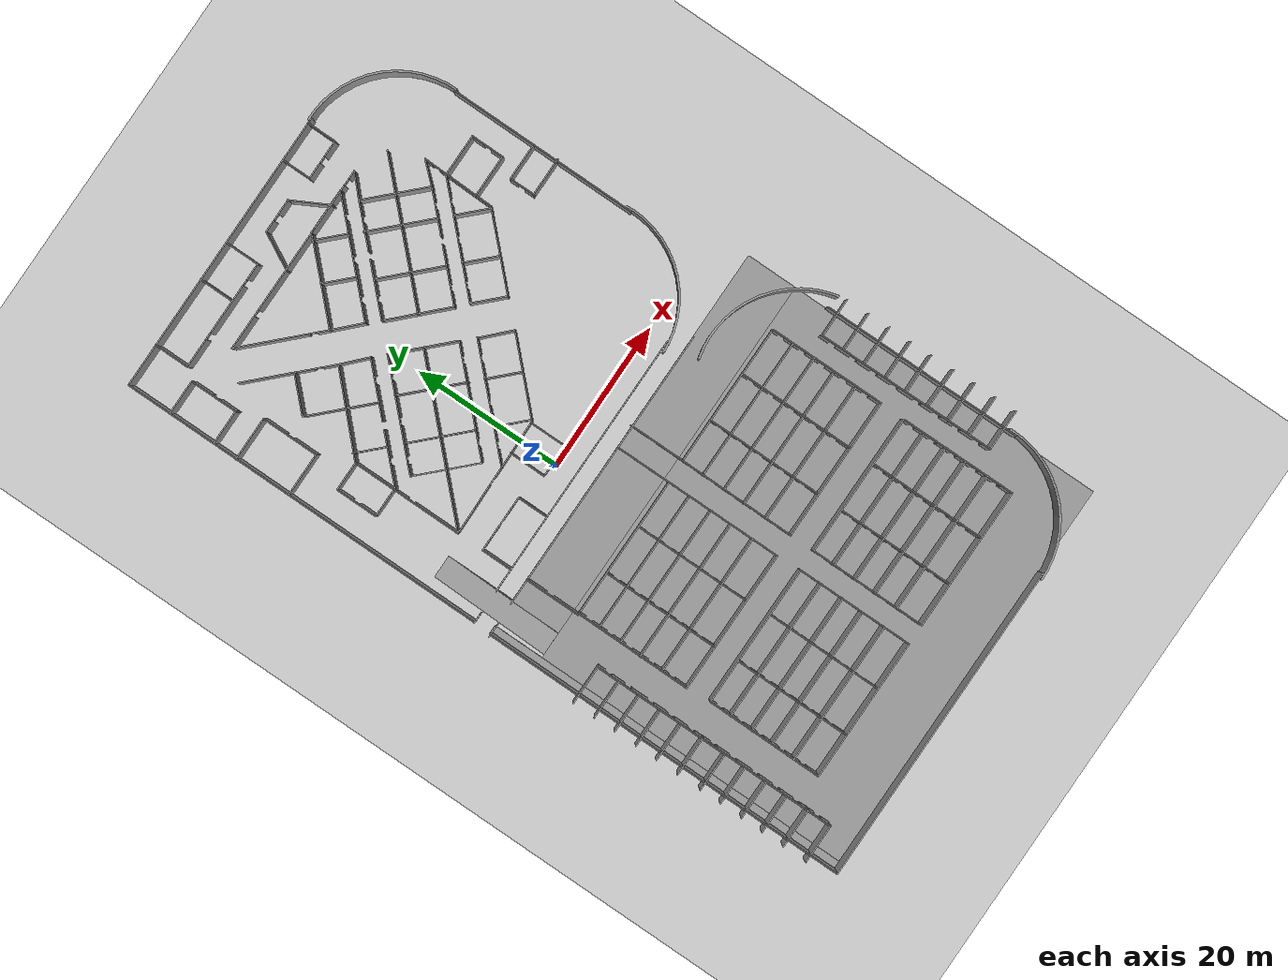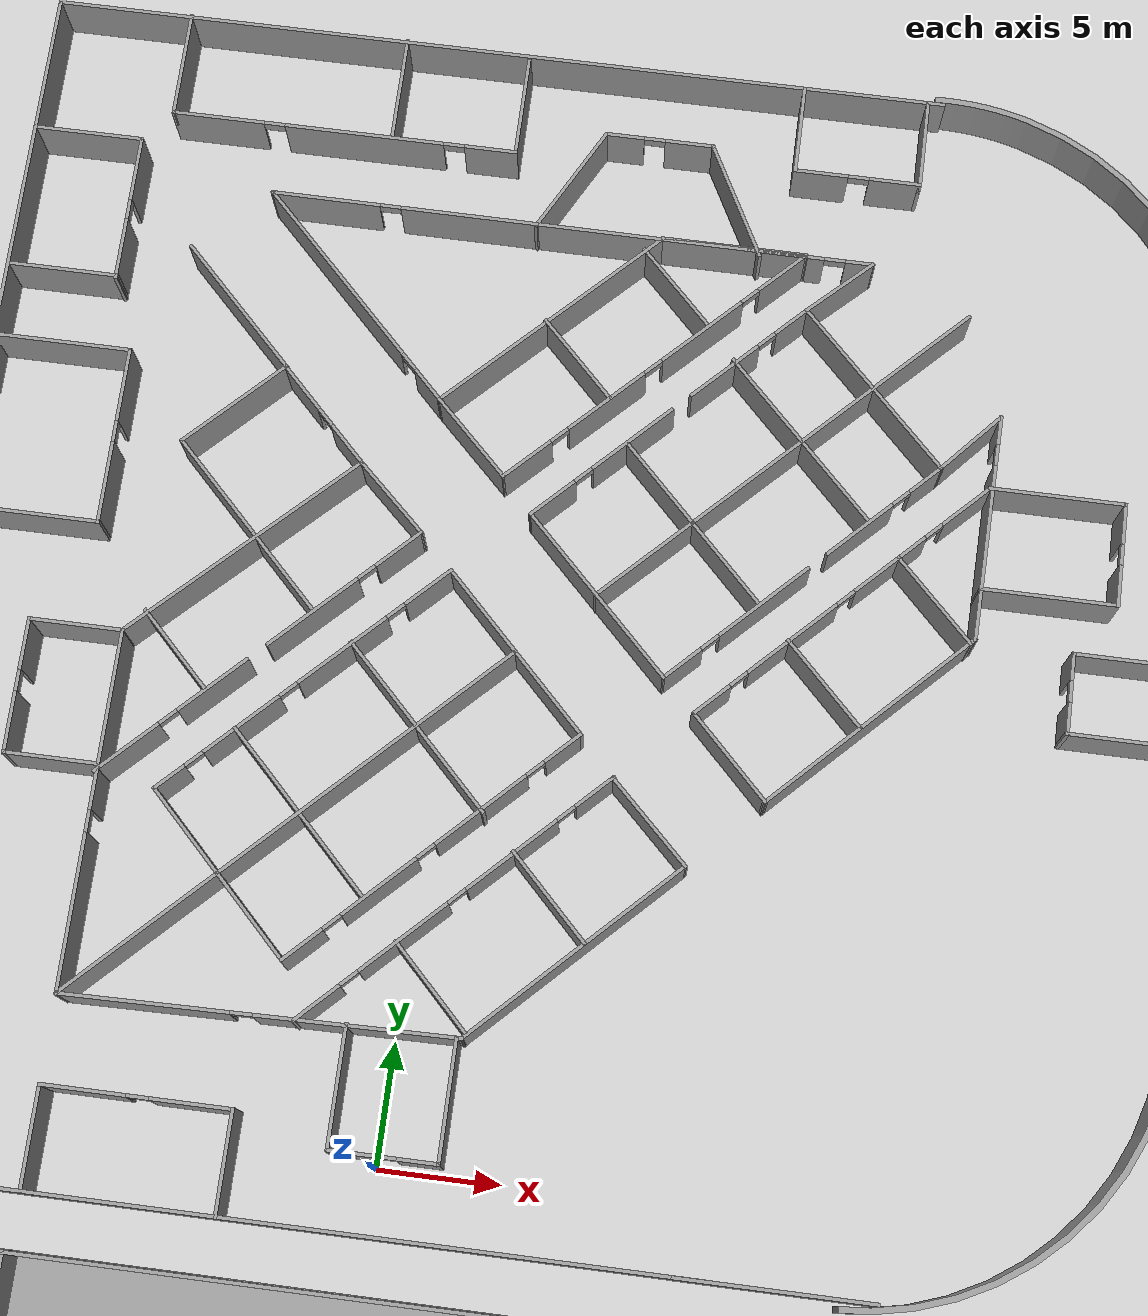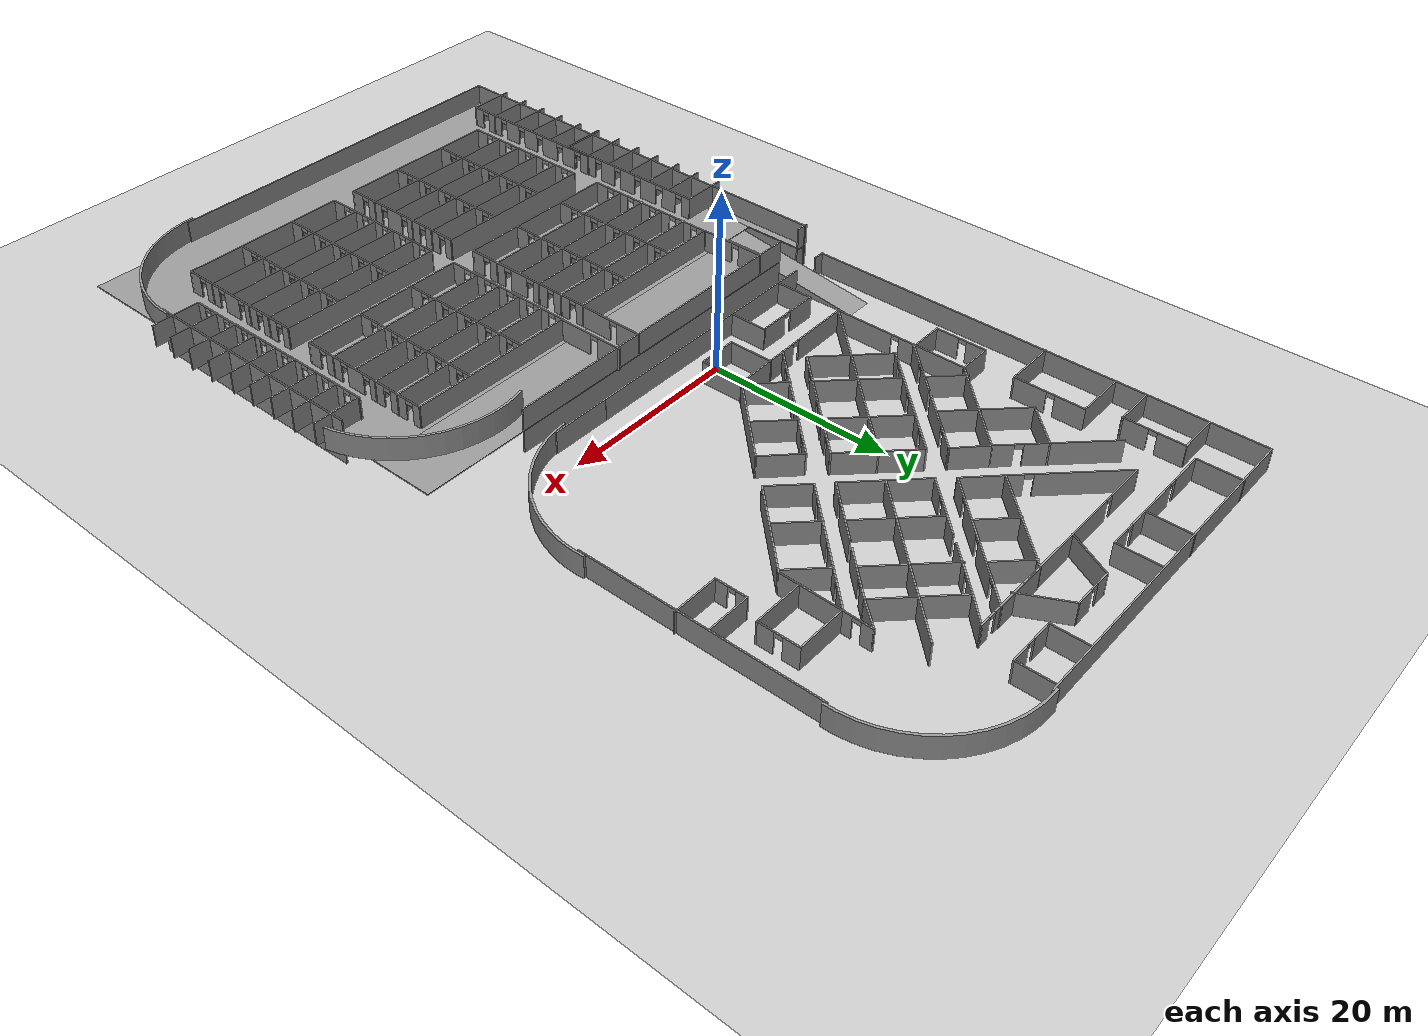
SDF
<sdf version="1.6">
 <world name="default">
  <light name="sun" type="directional">
   <pose>0 0 10 0 -0 0</pose>
   <diffuse>0.8 0.8 0.8 1</diffuse>
   <specular>0.2 0.2 0.2 1</specular>
   <attenuation>
    <range>1000</range>
    <constant>0.9</constant>
    <linear>0.01</linear>
    <quadratic>0.001</quadratic>
   </attenuation>
   <direction>-0.5 0.1 -0.9</direction>
  </light>
  <model name="ground_plane">
   <static>1</static>
   <link name="link">
    <collision name="collision">
     <geometry><plane><normal>0 0 1</normal><size>100 100</size></plane></geometry>
     <surface>
      <contact><collide_bitmask>65535</collide_bitmask></contact>
      <friction><ode><mu>100</mu><mu2>50</mu2></ode></friction>
     </surface>
    </collision>
    <visual name="visual">
     <cast_shadows>0</cast_shadows>
     <geometry><plane><normal>0 0 1</normal><size>100 100</size></plane></geometry>
     <material>
      <script><uri>file://media/materials/scripts/gazebo.material</uri><name>Gazebo/Grey</name></script>
     </material>
    </visual>
   </link>
  </model>
  <gravity>0 0 -9.8</gravity>
  <magnetic_field>6e-06 2.3e-05 -4.2e-05</magnetic_field>
  <atmosphere type="adiabatic"/>
  <physics name="default_physics" default="0" type="ode">
   <max_step_size>0.001</max_step_size>
   <real_time_factor>1</real_time_factor>
   <real_time_update_rate>1000</real_time_update_rate>
  </physics>
  <scene><ambient>0.4 0.4 0.4 1</ambient><background>0.7 0.7 0.7 1</background><shadows>1</shadows></scene>
  <spherical_coordinates>
   <surface_model>EARTH_WGS84</surface_model>
   <latitude_deg>0</latitude_deg>
   <longitude_deg>0</longitude_deg>
   <elevation>0</elevation>
   <heading_deg>0</heading_deg>
  </spherical_coordinates>
  <model name="5x3_Cubicles">
   <pose>-3.37089 -19.9476 2.66445 0 -0 0</pose>
   <link name="Wall_0">
    <pose>-9.39351 -0 0 0 -0 -1.57435</pose>
    <visual name="Wall_0_Visual_0">
     <pose>-7.27295 0 1.25 0 -0 0</pose>
     <geometry><box><size>1.03181 0.15 2.5</size></box></geometry>
     <material>
      <script><uri>file://media/materials/scripts/gazebo.material</uri><name>Gazebo/Grey</name></script>
      <ambient>1 1 1 1</ambient>
     </material>
     <meta><layer>0</layer></meta>
    </visual>
    <collision name="Wall_0_Collision_0">
     <geometry><box><size>1.03181 0.15 2.5</size></box></geometry>
     <pose>-7.27295 0 1.25 0 -0 0</pose>
    </collision>
    <visual name="Wall_0_Visual_1">
     <pose>-4.8086 0 1.25 0 -0 0</pose>
     <geometry><box><size>2.09689 0.15 2.5</size></box></geometry>
     <material>
      <script><uri>file://media/materials/scripts/gazebo.material</uri><name>Gazebo/Grey</name></script>
      <ambient>1 1 1 1</ambient>
     </material>
     <meta><layer>0</layer></meta>
    </visual>
    <collision name="Wall_0_Collision_1">
     <geometry><box><size>2.09689 0.15 2.5</size></box></geometry>
     <pose>-4.8086 0 1.25 0 -0 0</pose>
    </collision>
    <visual name="Wall_0_Visual_2">
     <pose>-1.91379 0 1.25 0 -0 0</pose>
     <geometry><box><size>1.89272 0.15 2.5</size></box></geometry>
     <material>
      <script><uri>file://media/materials/scripts/gazebo.material</uri><name>Gazebo/Grey</name></script>
      <ambient>1 1 1 1</ambient>
     </material>
     <meta><layer>0</layer></meta>
    </visual>
    <collision name="Wall_0_Collision_2">
     <geometry><box><size>1.89272 0.15 2.5</size></box></geometry>
     <pose>-1.91379 0 1.25 0 -0 0</pose>
    </collision>
    <visual name="Wall_0_Visual_3">
     <pose>1.06918 0 1.25 0 -0 0</pose>
     <geometry><box><size>2.27323 0.15 2.5</size></box></geometry>
     <material>
      <script><uri>file://media/materials/scripts/gazebo.material</uri><name>Gazebo/Grey</name></script>
      <ambient>1 1 1 1</ambient>
     </material>
     <meta><layer>0</layer></meta>
    </visual>
    <collision name="Wall_0_Collision_3">
     <geometry><box><size>2.27323 0.15 2.5</size></box></geometry>
     <pose>1.06918 0 1.25 0 -0 0</pose>
    </collision>
    <visual name="Wall_0_Visual_4">
     <pose>4.14705 0 1.25 0 -0 0</pose>
     <geometry><box><size>2.0825 0.15 2.5</size></box></geometry>
     <material>
      <script><uri>file://media/materials/scripts/gazebo.material</uri><name>Gazebo/Grey</name></script>
      <ambient>1 1 1 1</ambient>
     </material>
     <meta><layer>0</layer></meta>
    </visual>
    <collision name="Wall_0_Collision_4">
     <geometry><box><size>2.0825 0.15 2.5</size></box></geometry>
     <pose>4.14705 0 1.25 0 -0 0</pose>
    </collision>
    <visual name="Wall_0_Visual_5">
     <pose>6.93858 0 1.25 0 -0 0</pose>
     <geometry><box><size>1.70057 0.15 2.5</size></box></geometry>
     <material>
      <script><uri>file://media/materials/scripts/gazebo.material</uri><name>Gazebo/Grey</name></script>
      <ambient>1 1 1 1</ambient>
     </material>
     <meta><layer>0</layer></meta>
    </visual>
    <collision name="Wall_0_Collision_5">
     <geometry><box><size>1.70057 0.15 2.5</size></box></geometry>
     <pose>6.93858 0 1.25 0 -0 0</pose>
    </collision>
    <visual name="Wall_0_Visual_6">
     <pose>-6.30705 0 2.25 0 -0 0</pose>
     <geometry><box><size>0.9 0.15 0.5</size></box></geometry>
     <material>
      <script><uri>file://media/materials/scripts/gazebo.material</uri><name>Gazebo/Grey</name></script>
      <ambient>1 1 1 1</ambient>
     </material>
     <meta><layer>0</layer></meta>
    </visual>
    <collision name="Wall_0_Collision_6">
     <geometry><box><size>0.9 0.15 0.5</size></box></geometry>
     <pose>-6.30705 0 2.25 0 -0 0</pose>
    </collision>
    <visual name="Wall_0_Visual_7">
     <pose>-3.31016 0 2.25 0 -0 0</pose>
     <geometry><box><size>0.9 0.15 0.5</size></box></geometry>
     <material>
      <script><uri>file://media/materials/scripts/gazebo.material</uri><name>Gazebo/Grey</name></script>
      <ambient>1 1 1 1</ambient>
     </material>
     <meta><layer>0</layer></meta>
    </visual>
    <collision name="Wall_0_Collision_7">
     <geometry><box><size>0.9 0.15 0.5</size></box></geometry>
     <pose>-3.31016 0 2.25 0 -0 0</pose>
    </collision>
    <visual name="Wall_0_Visual_8">
     <pose>-0.517433 0 2.25 0 -0 0</pose>
     <geometry><box><size>0.9 0.15 0.5</size></box></geometry>
     <material>
      <script><uri>file://media/materials/scripts/gazebo.material</uri><name>Gazebo/Grey</name></script>
      <ambient>1 1 1 1</ambient>
     </material>
     <meta><layer>0</layer></meta>
    </visual>
    <collision name="Wall_0_Collision_8">
     <geometry><box><size>0.9 0.15 0.5</size></box></geometry>
     <pose>-0.517433 0 2.25 0 -0 0</pose>
    </collision>
    <visual name="Wall_0_Visual_9">
     <pose>2.6558 0 2.25 0 -0 0</pose>
     <geometry><box><size>0.9 0.15 0.5</size></box></geometry>
     <material>
      <script><uri>file://media/materials/scripts/gazebo.material</uri><name>Gazebo/Grey</name></script>
      <ambient>1 1 1 1</ambient>
     </material>
     <meta><layer>0</layer></meta>
    </visual>
    <collision name="Wall_0_Collision_9">
     <geometry><box><size>0.9 0.15 0.5</size></box></geometry>
     <pose>2.6558 0 2.25 0 -0 0</pose>
    </collision>
    <visual name="Wall_0_Visual_10">
     <pose>5.63829 0 2.25 0 -0 0</pose>
     <geometry><box><size>0.9 0.15 0.5</size></box></geometry>
     <material>
      <script><uri>file://media/materials/scripts/gazebo.material</uri><name>Gazebo/Grey</name></script>
      <ambient>1 1 1 1</ambient>
     </material>
     <meta><layer>0</layer></meta>
    </visual>
    <collision name="Wall_0_Collision_10">
     <geometry><box><size>0.9 0.15 0.5</size></box></geometry>
     <pose>5.63829 0 2.25 0 -0 0</pose>
    </collision>
   </link>
   <link name="Wall_10">
    <collision name="Wall_10_Collision">
     <geometry><box><size>19 0.15 2.5</size></box></geometry>
     <pose>0 0 1.25 0 -0 0</pose>
    </collision>
    <visual name="Wall_10_Visual">
     <pose>0 0 1.25 0 -0 0</pose>
     <geometry><box><size>19 0.15 2.5</size></box></geometry>
     <material>
      <script><uri>file://media/materials/scripts/gazebo.material</uri><name>Gazebo/Grey</name></script>
      <ambient>1 1 1 1</ambient>
     </material>
     <meta><layer>0</layer></meta>
    </visual>
    <pose>-0 1.73972 0 0 -0 0</pose>
   </link>
   <link name="Wall_12">
    <collision name="Wall_12_Collision">
     <geometry><box><size>19 0.15 2.5</size></box></geometry>
     <pose>0 0 1.25 0 -0 0</pose>
    </collision>
    <visual name="Wall_12_Visual">
     <pose>0 0 1.25 0 -0 0</pose>
     <geometry><box><size>19 0.15 2.5</size></box></geometry>
     <material>
      <script><uri>file://media/materials/scripts/gazebo.material</uri><name>Gazebo/Grey</name></script>
      <ambient>1 1 1 1</ambient>
     </material>
     <meta><layer>0</layer></meta>
    </visual>
    <pose>0.002757 4.78648 0 0 -0 0</pose>
   </link>
   <link name="Wall_14">
    <pose>3.03244 -0.038205 0 0 -0 -1.57332</pose>
    <visual name="Wall_14_Visual_0">
     <pose>-7.27661 0 1.25 0 -0 0</pose>
     <geometry><box><size>0.887786 0.15 2.5</size></box></geometry>
     <material>
      <script><uri>file://media/materials/scripts/gazebo.material</uri><name>Gazebo/Grey</name></script>
      <ambient>1 1 1 1</ambient>
     </material>
     <meta><layer>0</layer></meta>
    </visual>
    <collision name="Wall_14_Collision_0">
     <geometry><box><size>0.887786 0.15 2.5</size></box></geometry>
     <pose>-7.27661 0 1.25 0 -0 0</pose>
    </collision>
    <visual name="Wall_14_Visual_1">
     <pose>-4.91212 0 1.25 0 -0 0</pose>
     <geometry><box><size>2.04118 0.15 2.5</size></box></geometry>
     <material>
      <script><uri>file://media/materials/scripts/gazebo.material</uri><name>Gazebo/Grey</name></script>
      <ambient>1 1 1 1</ambient>
     </material>
     <meta><layer>0</layer></meta>
    </visual>
    <collision name="Wall_14_Collision_1">
     <geometry><box><size>2.04118 0.15 2.5</size></box></geometry>
     <pose>-4.91212 0 1.25 0 -0 0</pose>
    </collision>
    <visual name="Wall_14_Visual_2">
     <pose>-1.97726 0 1.25 0 -0 0</pose>
     <geometry><box><size>2.02854 0.15 2.5</size></box></geometry>
     <material>
      <script><uri>file://media/materials/scripts/gazebo.material</uri><name>Gazebo/Grey</name></script>
      <ambient>1 1 1 1</ambient>
     </material>
     <meta><layer>0</layer></meta>
    </visual>
    <collision name="Wall_14_Collision_2">
     <geometry><box><size>2.02854 0.15 2.5</size></box></geometry>
     <pose>-1.97726 0 1.25 0 -0 0</pose>
    </collision>
    <visual name="Wall_14_Visual_3">
     <pose>1.09454 0 1.25 0 -0 0</pose>
     <geometry><box><size>2.31505 0.15 2.5</size></box></geometry>
     <material>
      <script><uri>file://media/materials/scripts/gazebo.material</uri><name>Gazebo/Grey</name></script>
      <ambient>1 1 1 1</ambient>
     </material>
     <meta><layer>0</layer></meta>
    </visual>
    <collision name="Wall_14_Collision_3">
     <geometry><box><size>2.31505 0.15 2.5</size></box></geometry>
     <pose>1.09454 0 1.25 0 -0 0</pose>
    </collision>
    <visual name="Wall_14_Visual_4">
     <pose>4.15071 0 1.25 0 -0 0</pose>
     <geometry><box><size>1.9973 0.15 2.5</size></box></geometry>
     <material>
      <script><uri>file://media/materials/scripts/gazebo.material</uri><name>Gazebo/Grey</name></script>
      <ambient>1 1 1 1</ambient>
     </material>
     <meta><layer>0</layer></meta>
    </visual>
    <collision name="Wall_14_Collision_4">
     <geometry><box><size>1.9973 0.15 2.5</size></box></geometry>
     <pose>4.15071 0 1.25 0 -0 0</pose>
    </collision>
    <visual name="Wall_14_Visual_5">
     <pose>6.88493 0 1.25 0 -0 0</pose>
     <geometry><box><size>1.67114 0.15 2.5</size></box></geometry>
     <material>
      <script><uri>file://media/materials/scripts/gazebo.material</uri><name>Gazebo/Grey</name></script>
      <ambient>1 1 1 1</ambient>
     </material>
     <meta><layer>0</layer></meta>
    </visual>
    <collision name="Wall_14_Collision_5">
     <geometry><box><size>1.67114 0.15 2.5</size></box></geometry>
     <pose>6.88493 0 1.25 0 -0 0</pose>
    </collision>
    <visual name="Wall_14_Visual_6">
     <pose>-6.38271 0 2.25 0 -0 0</pose>
     <geometry><box><size>0.9 0.15 0.5</size></box></geometry>
     <material>
      <script><uri>file://media/materials/scripts/gazebo.material</uri><name>Gazebo/Grey</name></script>
      <ambient>1 1 1 1</ambient>
     </material>
     <meta><layer>0</layer></meta>
    </visual>
    <collision name="Wall_14_Collision_6">
     <geometry><box><size>0.9 0.15 0.5</size></box></geometry>
     <pose>-6.38271 0 2.25 0 -0 0</pose>
    </collision>
    <visual name="Wall_14_Visual_7">
     <pose>-3.44153 0 2.25 0 -0 0</pose>
     <geometry><box><size>0.9 0.15 0.5</size></box></geometry>
     <material>
      <script><uri>file://media/materials/scripts/gazebo.material</uri><name>Gazebo/Grey</name></script>
      <ambient>1 1 1 1</ambient>
     </material>
     <meta><layer>0</layer></meta>
    </visual>
    <collision name="Wall_14_Collision_7">
     <geometry><box><size>0.9 0.15 0.5</size></box></geometry>
     <pose>-3.44153 0 2.25 0 -0 0</pose>
    </collision>
    <visual name="Wall_14_Visual_8">
     <pose>-0.512986 0 2.25 0 -0 0</pose>
     <geometry><box><size>0.9 0.15 0.5</size></box></geometry>
     <material>
      <script><uri>file://media/materials/scripts/gazebo.material</uri><name>Gazebo/Grey</name></script>
      <ambient>1 1 1 1</ambient>
     </material>
     <meta><layer>0</layer></meta>
    </visual>
    <collision name="Wall_14_Collision_8">
     <geometry><box><size>0.9 0.15 0.5</size></box></geometry>
     <pose>-0.512986 0 2.25 0 -0 0</pose>
    </collision>
    <visual name="Wall_14_Visual_9">
     <pose>2.70206 0 2.25 0 -0 0</pose>
     <geometry><box><size>0.9 0.15 0.5</size></box></geometry>
     <material>
      <script><uri>file://media/materials/scripts/gazebo.material</uri><name>Gazebo/Grey</name></script>
      <ambient>1 1 1 1</ambient>
     </material>
     <meta><layer>0</layer></meta>
    </visual>
    <collision name="Wall_14_Collision_9">
     <geometry><box><size>0.9 0.15 0.5</size></box></geometry>
     <pose>2.70206 0 2.25 0 -0 0</pose>
    </collision>
    <visual name="Wall_14_Visual_10">
     <pose>5.59936 0 2.25 0 -0 0</pose>
     <geometry><box><size>0.9 0.15 0.5</size></box></geometry>
     <material>
      <script><uri>file://media/materials/scripts/gazebo.material</uri><name>Gazebo/Grey</name></script>
      <ambient>1 1 1 1</ambient>
     </material>
     <meta><layer>0</layer></meta>
    </visual>
    <collision name="Wall_14_Collision_10">
     <geometry><box><size>0.9 0.15 0.5</size></box></geometry>
     <pose>5.59936 0 2.25 0 -0 0</pose>
    </collision>
   </link>
   <link name="Wall_16">
    <pose>-3.57321 -0.011645 0 0 -0 -1.5708</pose>
    <visual name="Wall_16_Visual_0">
     <pose>-7.25015 0 1.25 0 -0 0</pose>
     <geometry><box><size>0.999697 0.15 2.5</size></box></geometry>
     <material>
      <script><uri>file://media/materials/scripts/gazebo.material</uri><name>Gazebo/Grey</name></script>
      <ambient>1 1 1 1</ambient>
     </material>
     <meta><layer>0</layer></meta>
    </visual>
    <collision name="Wall_16_Collision_0">
     <geometry><box><size>0.999697 0.15 2.5</size></box></geometry>
     <pose>-7.25015 0 1.25 0 -0 0</pose>
    </collision>
    <visual name="Wall_16_Visual_1">
     <pose>-4.84832 0 1.25 0 -0 0</pose>
     <geometry><box><size>2.00397 0.15 2.5</size></box></geometry>
     <material>
      <script><uri>file://media/materials/scripts/gazebo.material</uri><name>Gazebo/Grey</name></script>
      <ambient>1 1 1 1</ambient>
     </material>
     <meta><layer>0</layer></meta>
    </visual>
    <collision name="Wall_16_Collision_1">
     <geometry><box><size>2.00397 0.15 2.5</size></box></geometry>
     <pose>-4.84832 0 1.25 0 -0 0</pose>
    </collision>
    <visual name="Wall_16_Visual_2">
     <pose>-1.97337 0 1.25 0 -0 0</pose>
     <geometry><box><size>1.94594 0.15 2.5</size></box></geometry>
     <material>
      <script><uri>file://media/materials/scripts/gazebo.material</uri><name>Gazebo/Grey</name></script>
      <ambient>1 1 1 1</ambient>
     </material>
     <meta><layer>0</layer></meta>
    </visual>
    <collision name="Wall_16_Collision_2">
     <geometry><box><size>1.94594 0.15 2.5</size></box></geometry>
     <pose>-1.97337 0 1.25 0 -0 0</pose>
    </collision>
    <visual name="Wall_16_Visual_3">
     <pose>1.06765 0 1.25 0 -0 0</pose>
     <geometry><box><size>2.3361 0.15 2.5</size></box></geometry>
     <material>
      <script><uri>file://media/materials/scripts/gazebo.material</uri><name>Gazebo/Grey</name></script>
      <ambient>1 1 1 1</ambient>
     </material>
     <meta><layer>0</layer></meta>
    </visual>
    <collision name="Wall_16_Collision_3">
     <geometry><box><size>2.3361 0.15 2.5</size></box></geometry>
     <pose>1.06765 0 1.25 0 -0 0</pose>
    </collision>
    <visual name="Wall_16_Visual_4">
     <pose>4.14512 0 1.25 0 -0 0</pose>
     <geometry><box><size>2.01884 0.15 2.5</size></box></geometry>
     <material>
      <script><uri>file://media/materials/scripts/gazebo.material</uri><name>Gazebo/Grey</name></script>
      <ambient>1 1 1 1</ambient>
     </material>
     <meta><layer>0</layer></meta>
    </visual>
    <collision name="Wall_16_Collision_4">
     <geometry><box><size>2.01884 0.15 2.5</size></box></geometry>
     <pose>4.14512 0 1.25 0 -0 0</pose>
    </collision>
    <visual name="Wall_16_Visual_5">
     <pose>6.90227 0 1.25 0 -0 0</pose>
     <geometry><box><size>1.69546 0.15 2.5</size></box></geometry>
     <material>
      <script><uri>file://media/materials/scripts/gazebo.material</uri><name>Gazebo/Grey</name></script>
      <ambient>1 1 1 1</ambient>
     </material>
     <meta><layer>0</layer></meta>
    </visual>
    <collision name="Wall_16_Collision_5">
     <geometry><box><size>1.69546 0.15 2.5</size></box></geometry>
     <pose>6.90227 0 1.25 0 -0 0</pose>
    </collision>
    <visual name="Wall_16_Visual_6">
     <pose>-6.3003 0 2.25 0 -0 0</pose>
     <geometry><box><size>0.9 0.15 0.5</size></box></geometry>
     <material>
      <script><uri>file://media/materials/scripts/gazebo.material</uri><name>Gazebo/Grey</name></script>
      <ambient>1 1 1 1</ambient>
     </material>
     <meta><layer>0</layer></meta>
    </visual>
    <collision name="Wall_16_Collision_6">
     <geometry><box><size>0.9 0.15 0.5</size></box></geometry>
     <pose>-6.3003 0 2.25 0 -0 0</pose>
    </collision>
    <visual name="Wall_16_Visual_7">
     <pose>-3.39634 0 2.25 0 -0 0</pose>
     <geometry><box><size>0.9 0.15 0.5</size></box></geometry>
     <material>
      <script><uri>file://media/materials/scripts/gazebo.material</uri><name>Gazebo/Grey</name></script>
      <ambient>1 1 1 1</ambient>
     </material>
     <meta><layer>0</layer></meta>
    </visual>
    <collision name="Wall_16_Collision_7">
     <geometry><box><size>0.9 0.15 0.5</size></box></geometry>
     <pose>-3.39634 0 2.25 0 -0 0</pose>
    </collision>
    <visual name="Wall_16_Visual_8">
     <pose>-0.5504 0 2.25 0 -0 0</pose>
     <geometry><box><size>0.9 0.15 0.5</size></box></geometry>
     <material>
      <script><uri>file://media/materials/scripts/gazebo.material</uri><name>Gazebo/Grey</name></script>
      <ambient>1 1 1 1</ambient>
     </material>
     <meta><layer>0</layer></meta>
    </visual>
    <collision name="Wall_16_Collision_8">
     <geometry><box><size>0.9 0.15 0.5</size></box></geometry>
     <pose>-0.5504 0 2.25 0 -0 0</pose>
    </collision>
    <visual name="Wall_16_Visual_9">
     <pose>2.6857 0 2.25 0 -0 0</pose>
     <geometry><box><size>0.9 0.15 0.5</size></box></geometry>
     <material>
      <script><uri>file://media/materials/scripts/gazebo.material</uri><name>Gazebo/Grey</name></script>
      <ambient>1 1 1 1</ambient>
     </material>
     <meta><layer>0</layer></meta>
    </visual>
    <collision name="Wall_16_Collision_9">
     <geometry><box><size>0.9 0.15 0.5</size></box></geometry>
     <pose>2.6857 0 2.25 0 -0 0</pose>
    </collision>
    <visual name="Wall_16_Visual_10">
     <pose>5.60454 0 2.25 0 -0 0</pose>
     <geometry><box><size>0.9 0.15 0.5</size></box></geometry>
     <material>
      <script><uri>file://media/materials/scripts/gazebo.material</uri><name>Gazebo/Grey</name></script>
      <ambient>1 1 1 1</ambient>
     </material>
     <meta><layer>0</layer></meta>
    </visual>
    <collision name="Wall_16_Collision_10">
     <geometry><box><size>0.9 0.15 0.5</size></box></geometry>
     <pose>5.60454 0 2.25 0 -0 0</pose>
    </collision>
   </link>
   <link name="Wall_2">
    <collision name="Wall_2_Collision">
     <geometry><box><size>19 0.15 2.5</size></box></geometry>
     <pose>0 0 1.25 0 -0 0</pose>
    </collision>
    <visual name="Wall_2_Visual">
     <pose>0 0 1.25 0 -0 0</pose>
     <geometry><box><size>19 0.15 2.5</size></box></geometry>
     <material>
      <script><uri>file://media/materials/scripts/gazebo.material</uri><name>Gazebo/Grey</name></script>
      <ambient>1 1 1 1</ambient>
     </material>
     <meta><layer>0</layer></meta>
    </visual>
    <pose>0.004043 -7.71378 0 0 -0 0</pose>
   </link>
   <link name="Wall_3">
    <pose>9.40486 -0.007207 0 0 -0 1.57394</pose>
    <visual name="Wall_3_Visual_0">
     <pose>-6.96276 0 1.25 0 -0 0</pose>
     <geometry><box><size>1.63776 0.15 2.5</size></box></geometry>
     <material>
      <script><uri>file://media/materials/scripts/gazebo.material</uri><name>Gazebo/Grey</name></script>
      <ambient>1 1 1 1</ambient>
     </material>
     <meta><layer>0</layer></meta>
    </visual>
    <collision name="Wall_3_Collision_0">
     <geometry><box><size>1.63776 0.15 2.5</size></box></geometry>
     <pose>-6.96276 0 1.25 0 -0 0</pose>
    </collision>
    <visual name="Wall_3_Visual_1">
     <pose>-4.17068 0 1.25 0 -0 0</pose>
     <geometry><box><size>2.14639 0.15 2.5</size></box></geometry>
     <material>
      <script><uri>file://media/materials/scripts/gazebo.material</uri><name>Gazebo/Grey</name></script>
      <ambient>1 1 1 1</ambient>
     </material>
     <meta><layer>0</layer></meta>
    </visual>
    <collision name="Wall_3_Collision_1">
     <geometry><box><size>2.14639 0.15 2.5</size></box></geometry>
     <pose>-4.17068 0 1.25 0 -0 0</pose>
    </collision>
    <visual name="Wall_3_Visual_2">
     <pose>-1.08256 0 1.25 0 -0 0</pose>
     <geometry><box><size>2.22987 0.15 2.5</size></box></geometry>
     <material>
      <script><uri>file://media/materials/scripts/gazebo.material</uri><name>Gazebo/Grey</name></script>
      <ambient>1 1 1 1</ambient>
     </material>
     <meta><layer>0</layer></meta>
    </visual>
    <collision name="Wall_3_Collision_2">
     <geometry><box><size>2.22987 0.15 2.5</size></box></geometry>
     <pose>-1.08256 0 1.25 0 -0 0</pose>
    </collision>
    <visual name="Wall_3_Visual_3">
     <pose>1.90922 0 1.25 0 -0 0</pose>
     <geometry><box><size>1.95369 0.15 2.5</size></box></geometry>
     <material>
      <script><uri>file://media/materials/scripts/gazebo.material</uri><name>Gazebo/Grey</name></script>
      <ambient>1 1 1 1</ambient>
     </material>
     <meta><layer>0</layer></meta>
    </visual>
    <collision name="Wall_3_Collision_3">
     <geometry><box><size>1.95369 0.15 2.5</size></box></geometry>
     <pose>1.90922 0 1.25 0 -0 0</pose>
    </collision>
    <visual name="Wall_3_Visual_4">
     <pose>4.85258 0 1.25 0 -0 0</pose>
     <geometry><box><size>2.13302 0.15 2.5</size></box></geometry>
     <material>
      <script><uri>file://media/materials/scripts/gazebo.material</uri><name>Gazebo/Grey</name></script>
      <ambient>1 1 1 1</ambient>
     </material>
     <meta><layer>0</layer></meta>
    </visual>
    <collision name="Wall_3_Collision_4">
     <geometry><box><size>2.13302 0.15 2.5</size></box></geometry>
     <pose>4.85258 0 1.25 0 -0 0</pose>
    </collision>
    <visual name="Wall_3_Visual_5">
     <pose>7.30037 0 1.25 0 -0 0</pose>
     <geometry><box><size>0.962557 0.15 2.5</size></box></geometry>
     <material>
      <script><uri>file://media/materials/scripts/gazebo.material</uri><name>Gazebo/Grey</name></script>
      <ambient>1 1 1 1</ambient>
     </material>
     <meta><layer>0</layer></meta>
    </visual>
    <collision name="Wall_3_Collision_5">
     <geometry><box><size>0.962557 0.15 2.5</size></box></geometry>
     <pose>7.30037 0 1.25 0 -0 0</pose>
    </collision>
    <visual name="Wall_3_Visual_6">
     <pose>-5.69388 0 2.25 0 -0 0</pose>
     <geometry><box><size>0.9 0.15 0.5</size></box></geometry>
     <material>
      <script><uri>file://media/materials/scripts/gazebo.material</uri><name>Gazebo/Grey</name></script>
      <ambient>1 1 1 1</ambient>
     </material>
     <meta><layer>0</layer></meta>
    </visual>
    <collision name="Wall_3_Collision_6">
     <geometry><box><size>0.9 0.15 0.5</size></box></geometry>
     <pose>-5.69388 0 2.25 0 -0 0</pose>
    </collision>
    <visual name="Wall_3_Visual_7">
     <pose>-2.64749 0 2.25 0 -0 0</pose>
     <geometry><box><size>0.9 0.15 0.5</size></box></geometry>
     <material>
      <script><uri>file://media/materials/scripts/gazebo.material</uri><name>Gazebo/Grey</name></script>
      <ambient>1 1 1 1</ambient>
     </material>
     <meta><layer>0</layer></meta>
    </visual>
    <collision name="Wall_3_Collision_7">
     <geometry><box><size>0.9 0.15 0.5</size></box></geometry>
     <pose>-2.64749 0 2.25 0 -0 0</pose>
    </collision>
    <visual name="Wall_3_Visual_8">
     <pose>0.482376 0 2.25 0 -0 0</pose>
     <geometry><box><size>0.9 0.15 0.5</size></box></geometry>
     <material>
      <script><uri>file://media/materials/scripts/gazebo.material</uri><name>Gazebo/Grey</name></script>
      <ambient>1 1 1 1</ambient>
     </material>
     <meta><layer>0</layer></meta>
    </visual>
    <collision name="Wall_3_Collision_8">
     <geometry><box><size>0.9 0.15 0.5</size></box></geometry>
     <pose>0.482376 0 2.25 0 -0 0</pose>
    </collision>
    <visual name="Wall_3_Visual_9">
     <pose>3.33607 0 2.25 0 -0 0</pose>
     <geometry><box><size>0.9 0.15 0.5</size></box></geometry>
     <material>
      <script><uri>file://media/materials/scripts/gazebo.material</uri><name>Gazebo/Grey</name></script>
      <ambient>1 1 1 1</ambient>
     </material>
     <meta><layer>0</layer></meta>
    </visual>
    <collision name="Wall_3_Collision_9">
     <geometry><box><size>0.9 0.15 0.5</size></box></geometry>
     <pose>3.33607 0 2.25 0 -0 0</pose>
    </collision>
    <visual name="Wall_3_Visual_10">
     <pose>6.36909 0 2.25 0 -0 0</pose>
     <geometry><box><size>0.9 0.15 0.5</size></box></geometry>
     <material>
      <script><uri>file://media/materials/scripts/gazebo.material</uri><name>Gazebo/Grey</name></script>
      <ambient>1 1 1 1</ambient>
     </material>
     <meta><layer>0</layer></meta>
    </visual>
    <collision name="Wall_3_Collision_10">
     <geometry><box><size>0.9 0.15 0.5</size></box></geometry>
     <pose>6.36909 0 2.25 0 -0 0</pose>
    </collision>
   </link>
   <link name="Wall_4">
    <collision name="Wall_4_Collision">
     <geometry><box><size>18.8967 0.15 2.5</size></box></geometry>
     <pose>0 0 1.25 0 -0 0</pose>
    </collision>
    <visual name="Wall_4_Visual">
     <pose>0 0 1.25 0 -0 0</pose>
     <geometry><box><size>18.8967 0.15 2.5</size></box></geometry>
     <material>
      <script><uri>file://media/materials/scripts/gazebo.material</uri><name>Gazebo/Grey</name></script>
      <ambient>1 1 1 1</ambient>
     </material>
     <meta><layer>0</layer></meta>
    </visual>
    <pose>0.0073 7.70657 0 0 -0 3.14082</pose>
   </link>
   <link name="Wall_6">
    <collision name="Wall_6_Collision">
     <geometry><box><size>19 0.15 2.5</size></box></geometry>
     <pose>0 0 1.25 0 -0 0</pose>
    </collision>
    <visual name="Wall_6_Visual">
     <pose>0 0 1.25 0 -0 0</pose>
     <geometry><box><size>19 0.15 2.5</size></box></geometry>
     <material>
      <script><uri>file://media/materials/scripts/gazebo.material</uri><name>Gazebo/Grey</name></script>
      <ambient>1 1 1 1</ambient>
     </material>
     <meta><layer>0</layer></meta>
    </visual>
    <pose>0.024186 -4.2101 0 0 -0 0</pose>
   </link>
   <link name="Wall_8">
    <collision name="Wall_8_Collision">
     <geometry><box><size>19 0.15 2.5</size></box></geometry>
     <pose>0 0 1.25 0 -0 0</pose>
    </collision>
    <visual name="Wall_8_Visual">
     <pose>0 0 1.25 0 -0 0</pose>
     <geometry><box><size>19 0.15 2.5</size></box></geometry>
     <material>
      <script><uri>file://media/materials/scripts/gazebo.material</uri><name>Gazebo/Grey</name></script>
      <ambient>1 1 1 1</ambient>
     </material>
     <meta><layer>0</layer></meta>
    </visual>
    <pose>-0.024187 -1.11426 0 0 -0 0</pose>
   </link>
   <static>1</static>
  </model>
  <model name="5x3_Cubicles_0">
   <pose>18.3768 -19.8709 2.63141 0 -0 0</pose>
   <link name="Wall_0">
    <pose>-9.39351 -0 0 0 -0 -1.57435</pose>
    <visual name="Wall_0_Visual_0">
     <pose>-7.27295 0 1.25 0 -0 0</pose>
     <geometry><box><size>1.03181 0.15 2.5</size></box></geometry>
     <material>
      <script><uri>file://media/materials/scripts/gazebo.material</uri><name>Gazebo/Grey</name></script>
      <ambient>1 1 1 1</ambient>
     </material>
     <meta><layer>0</layer></meta>
    </visual>
    <collision name="Wall_0_Collision_0">
     <geometry><box><size>1.03181 0.15 2.5</size></box></geometry>
     <pose>-7.27295 0 1.25 0 -0 0</pose>
    </collision>
    <visual name="Wall_0_Visual_1">
     <pose>-4.8086 0 1.25 0 -0 0</pose>
     <geometry><box><size>2.09689 0.15 2.5</size></box></geometry>
     <material>
      <script><uri>file://media/materials/scripts/gazebo.material</uri><name>Gazebo/Grey</name></script>
      <ambient>1 1 1 1</ambient>
     </material>
     <meta><layer>0</layer></meta>
    </visual>
    <collision name="Wall_0_Collision_1">
     <geometry><box><size>2.09689 0.15 2.5</size></box></geometry>
     <pose>-4.8086 0 1.25 0 -0 0</pose>
    </collision>
    <visual name="Wall_0_Visual_2">
     <pose>-1.91379 0 1.25 0 -0 0</pose>
     <geometry><box><size>1.89272 0.15 2.5</size></box></geometry>
     <material>
      <script><uri>file://media/materials/scripts/gazebo.material</uri><name>Gazebo/Grey</name></script>
      <ambient>1 1 1 1</ambient>
     </material>
     <meta><layer>0</layer></meta>
    </visual>
    <collision name="Wall_0_Collision_2">
     <geometry><box><size>1.89272 0.15 2.5</size></box></geometry>
     <pose>-1.91379 0 1.25 0 -0 0</pose>
    </collision>
    <visual name="Wall_0_Visual_3">
     <pose>1.06918 0 1.25 0 -0 0</pose>
     <geometry><box><size>2.27323 0.15 2.5</size></box></geometry>
     <material>
      <script><uri>file://media/materials/scripts/gazebo.material</uri><name>Gazebo/Grey</name></script>
      <ambient>1 1 1 1</ambient>
     </material>
     <meta><layer>0</layer></meta>
    </visual>
    <collision name="Wall_0_Collision_3">
     <geometry><box><size>2.27323 0.15 2.5</size></box></geometry>
     <pose>1.06918 0 1.25 0 -0 0</pose>
    </collision>
    <visual name="Wall_0_Visual_4">
     <pose>4.14705 0 1.25 0 -0 0</pose>
     <geometry><box><size>2.0825 0.15 2.5</size></box></geometry>
     <material>
      <script><uri>file://media/materials/scripts/gazebo.material</uri><name>Gazebo/Grey</name></script>
      <ambient>1 1 1 1</ambient>
     </material>
     <meta><layer>0</layer></meta>
    </visual>
    <collision name="Wall_0_Collision_4">
     <geometry><box><size>2.0825 0.15 2.5</size></box></geometry>
     <pose>4.14705 0 1.25 0 -0 0</pose>
    </collision>
    <visual name="Wall_0_Visual_5">
     <pose>6.93858 0 1.25 0 -0 0</pose>
     <geometry><box><size>1.70057 0.15 2.5</size></box></geometry>
     <material>
      <script><uri>file://media/materials/scripts/gazebo.material</uri><name>Gazebo/Grey</name></script>
      <ambient>1 1 1 1</ambient>
     </material>
     <meta><layer>0</layer></meta>
    </visual>
    <collision name="Wall_0_Collision_5">
     <geometry><box><size>1.70057 0.15 2.5</size></box></geometry>
     <pose>6.93858 0 1.25 0 -0 0</pose>
    </collision>
    <visual name="Wall_0_Visual_6">
     <pose>-6.30705 0 2.25 0 -0 0</pose>
     <geometry><box><size>0.9 0.15 0.5</size></box></geometry>
     <material>
      <script><uri>file://media/materials/scripts/gazebo.material</uri><name>Gazebo/Grey</name></script>
      <ambient>1 1 1 1</ambient>
     </material>
     <meta><layer>0</layer></meta>
    </visual>
    <collision name="Wall_0_Collision_6">
     <geometry><box><size>0.9 0.15 0.5</size></box></geometry>
     <pose>-6.30705 0 2.25 0 -0 0</pose>
    </collision>
    <visual name="Wall_0_Visual_7">
     <pose>-3.31016 0 2.25 0 -0 0</pose>
     <geometry><box><size>0.9 0.15 0.5</size></box></geometry>
     <material>
      <script><uri>file://media/materials/scripts/gazebo.material</uri><name>Gazebo/Grey</name></script>
      <ambient>1 1 1 1</ambient>
     </material>
     <meta><layer>0</layer></meta>
    </visual>
    <collision name="Wall_0_Collision_7">
     <geometry><box><size>0.9 0.15 0.5</size></box></geometry>
     <pose>-3.31016 0 2.25 0 -0 0</pose>
    </collision>
    <visual name="Wall_0_Visual_8">
     <pose>-0.517433 0 2.25 0 -0 0</pose>
     <geometry><box><size>0.9 0.15 0.5</size></box></geometry>
     <material>
      <script><uri>file://media/materials/scripts/gazebo.material</uri><name>Gazebo/Grey</name></script>
      <ambient>1 1 1 1</ambient>
     </material>
     <meta><layer>0</layer></meta>
    </visual>
    <collision name="Wall_0_Collision_8">
     <geometry><box><size>0.9 0.15 0.5</size></box></geometry>
     <pose>-0.517433 0 2.25 0 -0 0</pose>
    </collision>
    <visual name="Wall_0_Visual_9">
     <pose>2.6558 0 2.25 0 -0 0</pose>
     <geometry><box><size>0.9 0.15 0.5</size></box></geometry>
     <material>
      <script><uri>file://media/materials/scripts/gazebo.material</uri><name>Gazebo/Grey</name></script>
      <ambient>1 1 1 1</ambient>
     </material>
     <meta><layer>0</layer></meta>
    </visual>
    <collision name="Wall_0_Collision_9">
     <geometry><box><size>0.9 0.15 0.5</size></box></geometry>
     <pose>2.6558 0 2.25 0 -0 0</pose>
    </collision>
    <visual name="Wall_0_Visual_10">
     <pose>5.63829 0 2.25 0 -0 0</pose>
     <geometry><box><size>0.9 0.15 0.5</size></box></geometry>
     <material>
      <script><uri>file://media/materials/scripts/gazebo.material</uri><name>Gazebo/Grey</name></script>
      <ambient>1 1 1 1</ambient>
     </material>
     <meta><layer>0</layer></meta>
    </visual>
    <collision name="Wall_0_Collision_10">
     <geometry><box><size>0.9 0.15 0.5</size></box></geometry>
     <pose>5.63829 0 2.25 0 -0 0</pose>
    </collision>
   </link>
   <link name="Wall_10">
    <collision name="Wall_10_Collision">
     <geometry><box><size>19 0.15 2.5</size></box></geometry>
     <pose>0 0 1.25 0 -0 0</pose>
    </collision>
    <visual name="Wall_10_Visual">
     <pose>0 0 1.25 0 -0 0</pose>
     <geometry><box><size>19 0.15 2.5</size></box></geometry>
     <material>
      <script><uri>file://media/materials/scripts/gazebo.material</uri><name>Gazebo/Grey</name></script>
      <ambient>1 1 1 1</ambient>
     </material>
     <meta><layer>0</layer></meta>
    </visual>
    <pose>-0 1.73972 0 0 -0 0</pose>
   </link>
   <link name="Wall_12">
    <collision name="Wall_12_Collision">
     <geometry><box><size>19 0.15 2.5</size></box></geometry>
     <pose>0 0 1.25 0 -0 0</pose>
    </collision>
    <visual name="Wall_12_Visual">
     <pose>0 0 1.25 0 -0 0</pose>
     <geometry><box><size>19 0.15 2.5</size></box></geometry>
     <material>
      <script><uri>file://media/materials/scripts/gazebo.material</uri><name>Gazebo/Grey</name></script>
      <ambient>1 1 1 1</ambient>
     </material>
     <meta><layer>0</layer></meta>
    </visual>
    <pose>0.002757 4.78648 0 0 -0 0</pose>
   </link>
   <link name="Wall_14">
    <pose>3.03244 -0.038205 0 0 -0 -1.57332</pose>
    <visual name="Wall_14_Visual_0">
     <pose>-7.27661 0 1.25 0 -0 0</pose>
     <geometry><box><size>0.887786 0.15 2.5</size></box></geometry>
     <material>
      <script><uri>file://media/materials/scripts/gazebo.material</uri><name>Gazebo/Grey</name></script>
      <ambient>1 1 1 1</ambient>
     </material>
     <meta><layer>0</layer></meta>
    </visual>
    <collision name="Wall_14_Collision_0">
     <geometry><box><size>0.887786 0.15 2.5</size></box></geometry>
     <pose>-7.27661 0 1.25 0 -0 0</pose>
    </collision>
    <visual name="Wall_14_Visual_1">
     <pose>-4.91212 0 1.25 0 -0 0</pose>
     <geometry><box><size>2.04118 0.15 2.5</size></box></geometry>
     <material>
      <script><uri>file://media/materials/scripts/gazebo.material</uri><name>Gazebo/Grey</name></script>
      <ambient>1 1 1 1</ambient>
     </material>
     <meta><layer>0</layer></meta>
    </visual>
    <collision name="Wall_14_Collision_1">
     <geometry><box><size>2.04118 0.15 2.5</size></box></geometry>
     <pose>-4.91212 0 1.25 0 -0 0</pose>
    </collision>
    <visual name="Wall_14_Visual_2">
     <pose>-1.97726 0 1.25 0 -0 0</pose>
     <geometry><box><size>2.02854 0.15 2.5</size></box></geometry>
     <material>
      <script><uri>file://media/materials/scripts/gazebo.material</uri><name>Gazebo/Grey</name></script>
      <ambient>1 1 1 1</ambient>
     </material>
     <meta><layer>0</layer></meta>
    </visual>
    <collision name="Wall_14_Collision_2">
     <geometry><box><size>2.02854 0.15 2.5</size></box></geometry>
     <pose>-1.97726 0 1.25 0 -0 0</pose>
    </collision>
    <visual name="Wall_14_Visual_3">
     <pose>1.09454 0 1.25 0 -0 0</pose>
     <geometry><box><size>2.31505 0.15 2.5</size></box></geometry>
     <material>
      <script><uri>file://media/materials/scripts/gazebo.material</uri><name>Gazebo/Grey</name></script>
      <ambient>1 1 1 1</ambient>
     </material>
     <meta><layer>0</layer></meta>
    </visual>
    <collision name="Wall_14_Collision_3">
     <geometry><box><size>2.31505 0.15 2.5</size></box></geometry>
     <pose>1.09454 0 1.25 0 -0 0</pose>
    </collision>
    <visual name="Wall_14_Visual_4">
     <pose>4.15071 0 1.25 0 -0 0</pose>
     <geometry><box><size>1.9973 0.15 2.5</size></box></geometry>
     <material>
      <script><uri>file://media/materials/scripts/gazebo.material</uri><name>Gazebo/Grey</name></script>
      <ambient>1 1 1 1</ambient>
     </material>
     <meta><layer>0</layer></meta>
    </visual>
    <collision name="Wall_14_Collision_4">
     <geometry><box><size>1.9973 0.15 2.5</size></box></geometry>
     <pose>4.15071 0 1.25 0 -0 0</pose>
    </collision>
    <visual name="Wall_14_Visual_5">
     <pose>6.88493 0 1.25 0 -0 0</pose>
     <geometry><box><size>1.67114 0.15 2.5</size></box></geometry>
     <material>
      <script><uri>file://media/materials/scripts/gazebo.material</uri><name>Gazebo/Grey</name></script>
      <ambient>1 1 1 1</ambient>
     </material>
     <meta><layer>0</layer></meta>
    </visual>
    <collision name="Wall_14_Collision_5">
     <geometry><box><size>1.67114 0.15 2.5</size></box></geometry>
     <pose>6.88493 0 1.25 0 -0 0</pose>
    </collision>
    <visual name="Wall_14_Visual_6">
     <pose>-6.38271 0 2.25 0 -0 0</pose>
     <geometry><box><size>0.9 0.15 0.5</size></box></geometry>
     <material>
      <script><uri>file://media/materials/scripts/gazebo.material</uri><name>Gazebo/Grey</name></script>
      <ambient>1 1 1 1</ambient>
     </material>
     <meta><layer>0</layer></meta>
    </visual>
    <collision name="Wall_14_Collision_6">
     <geometry><box><size>0.9 0.15 0.5</size></box></geometry>
     <pose>-6.38271 0 2.25 0 -0 0</pose>
    </collision>
    <visual name="Wall_14_Visual_7">
     <pose>-3.44153 0 2.25 0 -0 0</pose>
     <geometry><box><size>0.9 0.15 0.5</size></box></geometry>
     <material>
      <script><uri>file://media/materials/scripts/gazebo.material</uri><name>Gazebo/Grey</name></script>
      <ambient>1 1 1 1</ambient>
     </material>
     <meta><layer>0</layer></meta>
    </visual>
    <collision name="Wall_14_Collision_7">
     <geometry><box><size>0.9 0.15 0.5</size></box></geometry>
     <pose>-3.44153 0 2.25 0 -0 0</pose>
    </collision>
    <visual name="Wall_14_Visual_8">
     <pose>-0.512986 0 2.25 0 -0 0</pose>
     <geometry><box><size>0.9 0.15 0.5</size></box></geometry>
     <material>
      <script><uri>file://media/materials/scripts/gazebo.material</uri><name>Gazebo/Grey</name></script>
      <ambient>1 1 1 1</ambient>
     </material>
     <meta><layer>0</layer></meta>
    </visual>
    <collision name="Wall_14_Collision_8">
     <geometry><box><size>0.9 0.15 0.5</size></box></geometry>
     <pose>-0.512986 0 2.25 0 -0 0</pose>
    </collision>
    <visual name="Wall_14_Visual_9">
     <pose>2.70206 0 2.25 0 -0 0</pose>
     <geometry><box><size>0.9 0.15 0.5</size></box></geometry>
     <material>
      <script><uri>file://media/materials/scripts/gazebo.material</uri><name>Gazebo/Grey</name></script>
      <ambient>1 1 1 1</ambient>
     </material>
     <meta><layer>0</layer></meta>
    </visual>
    <collision name="Wall_14_Collision_9">
     <geometry><box><size>0.9 0.15 0.5</size></box></geometry>
     <pose>2.70206 0 2.25 0 -0 0</pose>
    </collision>
    <visual name="Wall_14_Visual_10">
     <pose>5.59936 0 2.25 0 -0 0</pose>
     <geometry><box><size>0.9 0.15 0.5</size></box></geometry>
     <material>
      <script><uri>file://media/materials/scripts/gazebo.material</uri><name>Gazebo/Grey</name></script>
      <ambient>1 1 1 1</ambient>
     </material>
     <meta><layer>0</layer></meta>
    </visual>
    <collision name="Wall_14_Collision_10">
     <geometry><box><size>0.9 0.15 0.5</size></box></geometry>
     <pose>5.59936 0 2.25 0 -0 0</pose>
    </collision>
   </link>
   <link name="Wall_16">
    <pose>-3.57321 -0.011645 0 0 -0 -1.5708</pose>
    <visual name="Wall_16_Visual_0">
     <pose>-7.25015 0 1.25 0 -0 0</pose>
     <geometry><box><size>0.999697 0.15 2.5</size></box></geometry>
     <material>
      <script><uri>file://media/materials/scripts/gazebo.material</uri><name>Gazebo/Grey</name></script>
      <ambient>1 1 1 1</ambient>
     </material>
     <meta><layer>0</layer></meta>
    </visual>
    <collision name="Wall_16_Collision_0">
     <geometry><box><size>0.999697 0.15 2.5</size></box></geometry>
     <pose>-7.25015 0 1.25 0 -0 0</pose>
    </collision>
    <visual name="Wall_16_Visual_1">
     <pose>-4.84832 0 1.25 0 -0 0</pose>
     <geometry><box><size>2.00397 0.15 2.5</size></box></geometry>
     <material>
      <script><uri>file://media/materials/scripts/gazebo.material</uri><name>Gazebo/Grey</name></script>
      <ambient>1 1 1 1</ambient>
     </material>
     <meta><layer>0</layer></meta>
    </visual>
    <collision name="Wall_16_Collision_1">
     <geometry><box><size>2.00397 0.15 2.5</size></box></geometry>
     <pose>-4.84832 0 1.25 0 -0 0</pose>
    </collision>
    <visual name="Wall_16_Visual_2">
     <pose>-1.97337 0 1.25 0 -0 0</pose>
     <geometry><box><size>1.94594 0.15 2.5</size></box></geometry>
     <material>
      <script><uri>file://media/materials/scripts/gazebo.material</uri><name>Gazebo/Grey</name></script>
      <ambient>1 1 1 1</ambient>
     </material>
     <meta><layer>0</layer></meta>
    </visual>
    <collision name="Wall_16_Collision_2">
     <geometry><box><size>1.94594 0.15 2.5</size></box></geometry>
     <pose>-1.97337 0 1.25 0 -0 0</pose>
    </collision>
    <visual name="Wall_16_Visual_3">
     <pose>1.06765 0 1.25 0 -0 0</pose>
     <geometry><box><size>2.3361 0.15 2.5</size></box></geometry>
     <material>
      <script><uri>file://media/materials/scripts/gazebo.material</uri><name>Gazebo/Grey</name></script>
      <ambient>1 1 1 1</ambient>
     </material>
     <meta><layer>0</layer></meta>
    </visual>
    <collision name="Wall_16_Collision_3">
     <geometry><box><size>2.3361 0.15 2.5</size></box></geometry>
     <pose>1.06765 0 1.25 0 -0 0</pose>
    </collision>
    <visual name="Wall_16_Visual_4">
     <pose>4.14512 0 1.25 0 -0 0</pose>
     <geometry><box><size>2.01884 0.15 2.5</size></box></geometry>
     <material>
      <script><uri>file://media/materials/scripts/gazebo.material</uri><name>Gazebo/Grey</name></script>
      <ambient>1 1 1 1</ambient>
     </material>
     <meta><layer>0</layer></meta>
    </visual>
    <collision name="Wall_16_Collision_4">
     <geometry><box><size>2.01884 0.15 2.5</size></box></geometry>
     <pose>4.14512 0 1.25 0 -0 0</pose>
    </collision>
    <visual name="Wall_16_Visual_5">
     <pose>6.90227 0 1.25 0 -0 0</pose>
     <geometry><box><size>1.69546 0.15 2.5</size></box></geometry>
     <material>
      <script><uri>file://media/materials/scripts/gazebo.material</uri><name>Gazebo/Grey</name></script>
      <ambient>1 1 1 1</ambient>
     </material>
     <meta><layer>0</layer></meta>
    </visual>
    <collision name="Wall_16_Collision_5">
     <geometry><box><size>1.69546 0.15 2.5</size></box></geometry>
     <pose>6.90227 0 1.25 0 -0 0</pose>
    </collision>
    <visual name="Wall_16_Visual_6">
     <pose>-6.3003 0 2.25 0 -0 0</pose>
     <geometry><box><size>0.9 0.15 0.5</size></box></geometry>
     <material>
      <script><uri>file://media/materials/scripts/gazebo.material</uri><name>Gazebo/Grey</name></script>
      <ambient>1 1 1 1</ambient>
     </material>
     <meta><layer>0</layer></meta>
    </visual>
    <collision name="Wall_16_Collision_6">
     <geometry><box><size>0.9 0.15 0.5</size></box></geometry>
     <pose>-6.3003 0 2.25 0 -0 0</pose>
    </collision>
    <visual name="Wall_16_Visual_7">
     <pose>-3.39634 0 2.25 0 -0 0</pose>
     <geometry><box><size>0.9 0.15 0.5</size></box></geometry>
     <material>
      <script><uri>file://media/materials/scripts/gazebo.material</uri><name>Gazebo/Grey</name></script>
      <ambient>1 1 1 1</ambient>
     </material>
     <meta><layer>0</layer></meta>
    </visual>
    <collision name="Wall_16_Collision_7">
     <geometry><box><size>0.9 0.15 0.5</size></box></geometry>
     <pose>-3.39634 0 2.25 0 -0 0</pose>
    </collision>
    <visual name="Wall_16_Visual_8">
     <pose>-0.5504 0 2.25 0 -0 0</pose>
     <geometry><box><size>0.9 0.15 0.5</size></box></geometry>
     <material>
      <script><uri>file://media/materials/scripts/gazebo.material</uri><name>Gazebo/Grey</name></script>
      <ambient>1 1 1 1</ambient>
     </material>
     <meta><layer>0</layer></meta>
    </visual>
    <collision name="Wall_16_Collision_8">
     <geometry><box><size>0.9 0.15 0.5</size></box></geometry>
     <pose>-0.5504 0 2.25 0 -0 0</pose>
    </collision>
    <visual name="Wall_16_Visual_9">
     <pose>2.6857 0 2.25 0 -0 0</pose>
     <geometry><box><size>0.9 0.15 0.5</size></box></geometry>
     <material>
      <script><uri>file://media/materials/scripts/gazebo.material</uri><name>Gazebo/Grey</name></script>
      <ambient>1 1 1 1</ambient>
     </material>
     <meta><layer>0</layer></meta>
    </visual>
    <collision name="Wall_16_Collision_9">
     <geometry><box><size>0.9 0.15 0.5</size></box></geometry>
     <pose>2.6857 0 2.25 0 -0 0</pose>
    </collision>
    <visual name="Wall_16_Visual_10">
     <pose>5.60454 0 2.25 0 -0 0</pose>
     <geometry><box><size>0.9 0.15 0.5</size></box></geometry>
     <material>
      <script><uri>file://media/materials/scripts/gazebo.material</uri><name>Gazebo/Grey</name></script>
      <ambient>1 1 1 1</ambient>
     </material>
     <meta><layer>0</layer></meta>
    </visual>
    <collision name="Wall_16_Collision_10">
     <geometry><box><size>0.9 0.15 0.5</size></box></geometry>
     <pose>5.60454 0 2.25 0 -0 0</pose>
    </collision>
   </link>
   <link name="Wall_2">
    <collision name="Wall_2_Collision">
     <geometry><box><size>19 0.15 2.5</size></box></geometry>
     <pose>0 0 1.25 0 -0 0</pose>
    </collision>
    <visual name="Wall_2_Visual">
     <pose>0 0 1.25 0 -0 0</pose>
     <geometry><box><size>19 0.15 2.5</size></box></geometry>
     <material>
      <script><uri>file://media/materials/scripts/gazebo.material</uri><name>Gazebo/Grey</name></script>
      <ambient>1 1 1 1</ambient>
     </material>
     <meta><layer>0</layer></meta>
    </visual>
    <pose>0.004043 -7.71378 0 0 -0 0</pose>
   </link>
   <link name="Wall_3">
    <pose>9.40486 -0.007207 0 0 -0 1.57394</pose>
    <visual name="Wall_3_Visual_0">
     <pose>-6.96276 0 1.25 0 -0 0</pose>
     <geometry><box><size>1.63776 0.15 2.5</size></box></geometry>
     <material>
      <script><uri>file://media/materials/scripts/gazebo.material</uri><name>Gazebo/Grey</name></script>
      <ambient>1 1 1 1</ambient>
     </material>
     <meta><layer>0</layer></meta>
    </visual>
    <collision name="Wall_3_Collision_0">
     <geometry><box><size>1.63776 0.15 2.5</size></box></geometry>
     <pose>-6.96276 0 1.25 0 -0 0</pose>
    </collision>
    <visual name="Wall_3_Visual_1">
     <pose>-4.17068 0 1.25 0 -0 0</pose>
     <geometry><box><size>2.14639 0.15 2.5</size></box></geometry>
     <material>
      <script><uri>file://media/materials/scripts/gazebo.material</uri><name>Gazebo/Grey</name></script>
      <ambient>1 1 1 1</ambient>
     </material>
     <meta><layer>0</layer></meta>
    </visual>
    <collision name="Wall_3_Collision_1">
     <geometry><box><size>2.14639 0.15 2.5</size></box></geometry>
     <pose>-4.17068 0 1.25 0 -0 0</pose>
    </collision>
    <visual name="Wall_3_Visual_2">
     <pose>-1.08256 0 1.25 0 -0 0</pose>
     <geometry><box><size>2.22987 0.15 2.5</size></box></geometry>
     <material>
      <script><uri>file://media/materials/scripts/gazebo.material</uri><name>Gazebo/Grey</name></script>
      <ambient>1 1 1 1</ambient>
     </material>
     <meta><layer>0</layer></meta>
    </visual>
    <collision name="Wall_3_Collision_2">
     <geometry><box><size>2.22987 0.15 2.5</size></box></geometry>
     <pose>-1.08256 0 1.25 0 -0 0</pose>
    </collision>
    <visual name="Wall_3_Visual_3">
     <pose>1.90922 0 1.25 0 -0 0</pose>
     <geometry><box><size>1.95369 0.15 2.5</size></box></geometry>
     <material>
      <script><uri>file://media/materials/scripts/gazebo.material</uri><name>Gazebo/Grey</name></script>
      <ambient>1 1 1 1</ambient>
     </material>
     <meta><layer>0</layer></meta>
    </visual>
    <collision name="Wall_3_Collision_3">
     <geometry><box><size>1.95369 0.15 2.5</size></box></geometry>
     <pose>1.90922 0 1.25 0 -0 0</pose>
    </collision>
    <visual name="Wall_3_Visual_4">
     <pose>4.85258 0 1.25 0 -0 0</pose>
     <geometry><box><size>2.13302 0.15 2.5</size></box></geometry>
     <material>
      <script><uri>file://media/materials/scripts/gazebo.material</uri><name>Gazebo/Grey</name></script>
      <ambient>1 1 1 1</ambient>
     </material>
     <meta><layer>0</layer></meta>
    </visual>
    <collision name="Wall_3_Collision_4">
     <geometry><box><size>2.13302 0.15 2.5</size></box></geometry>
     <pose>4.85258 0 1.25 0 -0 0</pose>
    </collision>
    <visual name="Wall_3_Visual_5">
     <pose>7.30037 0 1.25 0 -0 0</pose>
     <geometry><box><size>0.962557 0.15 2.5</size></box></geometry>
     <material>
      <script><uri>file://media/materials/scripts/gazebo.material</uri><name>Gazebo/Grey</name></script>
      <ambient>1 1 1 1</ambient>
     </material>
     <meta><layer>0</layer></meta>
    </visual>
    <collision name="Wall_3_Collision_5">
     <geometry><box><size>0.962557 0.15 2.5</size></box></geometry>
     <pose>7.30037 0 1.25 0 -0 0</pose>
    </collision>
    <visual name="Wall_3_Visual_6">
     <pose>-5.69388 0 2.25 0 -0 0</pose>
     <geometry><box><size>0.9 0.15 0.5</size></box></geometry>
     <material>
      <script><uri>file://media/materials/scripts/gazebo.material</uri><name>Gazebo/Grey</name></script>
      <ambient>1 1 1 1</ambient>
     </material>
     <meta><layer>0</layer></meta>
    </visual>
    <collision name="Wall_3_Collision_6">
     <geometry><box><size>0.9 0.15 0.5</size></box></geometry>
     <pose>-5.69388 0 2.25 0 -0 0</pose>
    </collision>
    <visual name="Wall_3_Visual_7">
     <pose>-2.64749 0 2.25 0 -0 0</pose>
     <geometry><box><size>0.9 0.15 0.5</size></box></geometry>
     <material>
      <script><uri>file://media/materials/scripts/gazebo.material</uri><name>Gazebo/Grey</name></script>
      <ambient>1 1 1 1</ambient>
     </material>
     <meta><layer>0</layer></meta>
    </visual>
    <collision name="Wall_3_Collision_7">
     <geometry><box><size>0.9 0.15 0.5</size></box></geometry>
     <pose>-2.64749 0 2.25 0 -0 0</pose>
    </collision>
    <visual name="Wall_3_Visual_8">
     <pose>0.482376 0 2.25 0 -0 0</pose>
     <geometry><box><size>0.9 0.15 0.5</size></box></geometry>
     <material>
      <script><uri>file://media/materials/scripts/gazebo.material</uri><name>Gazebo/Grey</name></script>
      <ambient>1 1 1 1</ambient>
     </material>
     <meta><layer>0</layer></meta>
    </visual>
    <collision name="Wall_3_Collision_8">
     <geometry><box><size>0.9 0.15 0.5</size></box></geometry>
     <pose>0.482376 0 2.25 0 -0 0</pose>
    </collision>
    <visual name="Wall_3_Visual_9">
     <pose>3.33607 0 2.25 0 -0 0</pose>
     <geometry><box><size>0.9 0.15 0.5</size></box></geometry>
     <material>
      <script><uri>file://media/materials/scripts/gazebo.material</uri><name>Gazebo/Grey</name></script>
      <ambient>1 1 1 1</ambient>
     </material>
     <meta><layer>0</layer></meta>
    </visual>
    <collision name="Wall_3_Collision_9">
     <geometry><box><size>0.9 0.15 0.5</size></box></geometry>
     <pose>3.33607 0 2.25 0 -0 0</pose>
    </collision>
    <visual name="Wall_3_Visual_10">
     <pose>6.36909 0 2.25 0 -0 0</pose>
     <geometry><box><size>0.9 0.15 0.5</size></box></geometry>
     <material>
      <script><uri>file://media/materials/scripts/gazebo.material</uri><name>Gazebo/Grey</name></script>
      <ambient>1 1 1 1</ambient>
     </material>
     <meta><layer>0</layer></meta>
    </visual>
    <collision name="Wall_3_Collision_10">
     <geometry><box><size>0.9 0.15 0.5</size></box></geometry>
     <pose>6.36909 0 2.25 0 -0 0</pose>
    </collision>
   </link>
   <link name="Wall_4">
    <collision name="Wall_4_Collision">
     <geometry><box><size>18.8967 0.15 2.5</size></box></geometry>
     <pose>0 0 1.25 0 -0 0</pose>
    </collision>
    <visual name="Wall_4_Visual">
     <pose>0 0 1.25 0 -0 0</pose>
     <geometry><box><size>18.8967 0.15 2.5</size></box></geometry>
     <material>
      <script><uri>file://media/materials/scripts/gazebo.material</uri><name>Gazebo/Grey</name></script>
      <ambient>1 1 1 1</ambient>
     </material>
     <meta><layer>0</layer></meta>
    </visual>
    <pose>0.0073 7.70657 0 0 -0 3.14082</pose>
   </link>
   <link name="Wall_6">
    <collision name="Wall_6_Collision">
     <geometry><box><size>19 0.15 2.5</size></box></geometry>
     <pose>0 0 1.25 0 -0 0</pose>
    </collision>
    <visual name="Wall_6_Visual">
     <pose>0 0 1.25 0 -0 0</pose>
     <geometry><box><size>19 0.15 2.5</size></box></geometry>
     <material>
      <script><uri>file://media/materials/scripts/gazebo.material</uri><name>Gazebo/Grey</name></script>
      <ambient>1 1 1 1</ambient>
     </material>
     <meta><layer>0</layer></meta>
    </visual>
    <pose>0.024186 -4.2101 0 0 -0 0</pose>
   </link>
   <link name="Wall_8">
    <collision name="Wall_8_Collision">
     <geometry><box><size>19 0.15 2.5</size></box></geometry>
     <pose>0 0 1.25 0 -0 0</pose>
    </collision>
    <visual name="Wall_8_Visual">
     <pose>0 0 1.25 0 -0 0</pose>
     <geometry><box><size>19 0.15 2.5</size></box></geometry>
     <material>
      <script><uri>file://media/materials/scripts/gazebo.material</uri><name>Gazebo/Grey</name></script>
      <ambient>1 1 1 1</ambient>
     </material>
     <meta><layer>0</layer></meta>
    </visual>
    <pose>-0.024187 -1.11426 0 0 -0 0</pose>
   </link>
   <static>1</static>
  </model>
  <model name="5x3_Cubicles_1">
   <pose>18.3518 -38.5604 2.72806 0 -0 0</pose>
   <link name="Wall_0">
    <pose>-9.39351 -0 0 0 -0 -1.57435</pose>
    <visual name="Wall_0_Visual_0">
     <pose>-7.27295 0 1.25 0 -0 0</pose>
     <geometry><box><size>1.03181 0.15 2.5</size></box></geometry>
     <material>
      <script><uri>file://media/materials/scripts/gazebo.material</uri><name>Gazebo/Grey</name></script>
      <ambient>1 1 1 1</ambient>
     </material>
     <meta><layer>0</layer></meta>
    </visual>
    <collision name="Wall_0_Collision_0">
     <geometry><box><size>1.03181 0.15 2.5</size></box></geometry>
     <pose>-7.27295 0 1.25 0 -0 0</pose>
    </collision>
    <visual name="Wall_0_Visual_1">
     <pose>-4.8086 0 1.25 0 -0 0</pose>
     <geometry><box><size>2.09689 0.15 2.5</size></box></geometry>
     <material>
      <script><uri>file://media/materials/scripts/gazebo.material</uri><name>Gazebo/Grey</name></script>
      <ambient>1 1 1 1</ambient>
     </material>
     <meta><layer>0</layer></meta>
    </visual>
    <collision name="Wall_0_Collision_1">
     <geometry><box><size>2.09689 0.15 2.5</size></box></geometry>
     <pose>-4.8086 0 1.25 0 -0 0</pose>
    </collision>
    <visual name="Wall_0_Visual_2">
     <pose>-1.91379 0 1.25 0 -0 0</pose>
     <geometry><box><size>1.89272 0.15 2.5</size></box></geometry>
     <material>
      <script><uri>file://media/materials/scripts/gazebo.material</uri><name>Gazebo/Grey</name></script>
      <ambient>1 1 1 1</ambient>
     </material>
     <meta><layer>0</layer></meta>
    </visual>
    <collision name="Wall_0_Collision_2">
     <geometry><box><size>1.89272 0.15 2.5</size></box></geometry>
     <pose>-1.91379 0 1.25 0 -0 0</pose>
    </collision>
    <visual name="Wall_0_Visual_3">
     <pose>1.06918 0 1.25 0 -0 0</pose>
     <geometry><box><size>2.27323 0.15 2.5</size></box></geometry>
     <material>
      <script><uri>file://media/materials/scripts/gazebo.material</uri><name>Gazebo/Grey</name></script>
      <ambient>1 1 1 1</ambient>
     </material>
     <meta><layer>0</layer></meta>
    </visual>
    <collision name="Wall_0_Collision_3">
     <geometry><box><size>2.27323 0.15 2.5</size></box></geometry>
     <pose>1.06918 0 1.25 0 -0 0</pose>
    </collision>
    <visual name="Wall_0_Visual_4">
     <pose>4.14705 0 1.25 0 -0 0</pose>
     <geometry><box><size>2.0825 0.15 2.5</size></box></geometry>
     <material>
      <script><uri>file://media/materials/scripts/gazebo.material</uri><name>Gazebo/Grey</name></script>
      <ambient>1 1 1 1</ambient>
     </material>
     <meta><layer>0</layer></meta>
    </visual>
    <collision name="Wall_0_Collision_4">
     <geometry><box><size>2.0825 0.15 2.5</size></box></geometry>
     <pose>4.14705 0 1.25 0 -0 0</pose>
    </collision>
    <visual name="Wall_0_Visual_5">
     <pose>6.93858 0 1.25 0 -0 0</pose>
     <geometry><box><size>1.70057 0.15 2.5</size></box></geometry>
     <material>
      <script><uri>file://media/materials/scripts/gazebo.material</uri><name>Gazebo/Grey</name></script>
      <ambient>1 1 1 1</ambient>
     </material>
     <meta><layer>0</layer></meta>
    </visual>
    <collision name="Wall_0_Collision_5">
     <geometry><box><size>1.70057 0.15 2.5</size></box></geometry>
     <pose>6.93858 0 1.25 0 -0 0</pose>
    </collision>
    <visual name="Wall_0_Visual_6">
     <pose>-6.30705 0 2.25 0 -0 0</pose>
     <geometry><box><size>0.9 0.15 0.5</size></box></geometry>
     <material>
      <script><uri>file://media/materials/scripts/gazebo.material</uri><name>Gazebo/Grey</name></script>
      <ambient>1 1 1 1</ambient>
     </material>
     <meta><layer>0</layer></meta>
    </visual>
    <collision name="Wall_0_Collision_6">
     <geometry><box><size>0.9 0.15 0.5</size></box></geometry>
     <pose>-6.30705 0 2.25 0 -0 0</pose>
    </collision>
    <visual name="Wall_0_Visual_7">
     <pose>-3.31016 0 2.25 0 -0 0</pose>
     <geometry><box><size>0.9 0.15 0.5</size></box></geometry>
     <material>
      <script><uri>file://media/materials/scripts/gazebo.material</uri><name>Gazebo/Grey</name></script>
      <ambient>1 1 1 1</ambient>
     </material>
     <meta><layer>0</layer></meta>
    </visual>
    <collision name="Wall_0_Collision_7">
     <geometry><box><size>0.9 0.15 0.5</size></box></geometry>
     <pose>-3.31016 0 2.25 0 -0 0</pose>
    </collision>
    <visual name="Wall_0_Visual_8">
     <pose>-0.517433 0 2.25 0 -0 0</pose>
     <geometry><box><size>0.9 0.15 0.5</size></box></geometry>
     <material>
      <script><uri>file://media/materials/scripts/gazebo.material</uri><name>Gazebo/Grey</name></script>
      <ambient>1 1 1 1</ambient>
     </material>
     <meta><layer>0</layer></meta>
    </visual>
    <collision name="Wall_0_Collision_8">
     <geometry><box><size>0.9 0.15 0.5</size></box></geometry>
     <pose>-0.517433 0 2.25 0 -0 0</pose>
    </collision>
    <visual name="Wall_0_Visual_9">
     <pose>2.6558 0 2.25 0 -0 0</pose>
     <geometry><box><size>0.9 0.15 0.5</size></box></geometry>
     <material>
      <script><uri>file://media/materials/scripts/gazebo.material</uri><name>Gazebo/Grey</name></script>
      <ambient>1 1 1 1</ambient>
     </material>
     <meta><layer>0</layer></meta>
    </visual>
    <collision name="Wall_0_Collision_9">
     <geometry><box><size>0.9 0.15 0.5</size></box></geometry>
     <pose>2.6558 0 2.25 0 -0 0</pose>
    </collision>
    <visual name="Wall_0_Visual_10">
     <pose>5.63829 0 2.25 0 -0 0</pose>
     <geometry><box><size>0.9 0.15 0.5</size></box></geometry>
     <material>
      <script><uri>file://media/materials/scripts/gazebo.material</uri><name>Gazebo/Grey</name></script>
      <ambient>1 1 1 1</ambient>
     </material>
     <meta><layer>0</layer></meta>
    </visual>
    <collision name="Wall_0_Collision_10">
     <geometry><box><size>0.9 0.15 0.5</size></box></geometry>
     <pose>5.63829 0 2.25 0 -0 0</pose>
    </collision>
   </link>
   <link name="Wall_10">
    <collision name="Wall_10_Collision">
     <geometry><box><size>19 0.15 2.5</size></box></geometry>
     <pose>0 0 1.25 0 -0 0</pose>
    </collision>
    <visual name="Wall_10_Visual">
     <pose>0 0 1.25 0 -0 0</pose>
     <geometry><box><size>19 0.15 2.5</size></box></geometry>
     <material>
      <script><uri>file://media/materials/scripts/gazebo.material</uri><name>Gazebo/Grey</name></script>
      <ambient>1 1 1 1</ambient>
     </material>
     <meta><layer>0</layer></meta>
    </visual>
    <pose>-0 1.73972 0 0 -0 0</pose>
   </link>
   <link name="Wall_12">
    <collision name="Wall_12_Collision">
     <geometry><box><size>19 0.15 2.5</size></box></geometry>
     <pose>0 0 1.25 0 -0 0</pose>
    </collision>
    <visual name="Wall_12_Visual">
     <pose>0 0 1.25 0 -0 0</pose>
     <geometry><box><size>19 0.15 2.5</size></box></geometry>
     <material>
      <script><uri>file://media/materials/scripts/gazebo.material</uri><name>Gazebo/Grey</name></script>
      <ambient>1 1 1 1</ambient>
     </material>
     <meta><layer>0</layer></meta>
    </visual>
    <pose>0.002757 4.78648 0 0 -0 0</pose>
   </link>
   <link name="Wall_14">
    <pose>3.03244 -0.038205 0 0 -0 -1.57332</pose>
    <visual name="Wall_14_Visual_0">
     <pose>-7.27661 0 1.25 0 -0 0</pose>
     <geometry><box><size>0.887786 0.15 2.5</size></box></geometry>
     <material>
      <script><uri>file://media/materials/scripts/gazebo.material</uri><name>Gazebo/Grey</name></script>
      <ambient>1 1 1 1</ambient>
     </material>
     <meta><layer>0</layer></meta>
    </visual>
    <collision name="Wall_14_Collision_0">
     <geometry><box><size>0.887786 0.15 2.5</size></box></geometry>
     <pose>-7.27661 0 1.25 0 -0 0</pose>
    </collision>
    <visual name="Wall_14_Visual_1">
     <pose>-4.91212 0 1.25 0 -0 0</pose>
     <geometry><box><size>2.04118 0.15 2.5</size></box></geometry>
     <material>
      <script><uri>file://media/materials/scripts/gazebo.material</uri><name>Gazebo/Grey</name></script>
      <ambient>1 1 1 1</ambient>
     </material>
     <meta><layer>0</layer></meta>
    </visual>
    <collision name="Wall_14_Collision_1">
     <geometry><box><size>2.04118 0.15 2.5</size></box></geometry>
     <pose>-4.91212 0 1.25 0 -0 0</pose>
    </collision>
    <visual name="Wall_14_Visual_2">
     <pose>-1.97726 0 1.25 0 -0 0</pose>
     <geometry><box><size>2.02854 0.15 2.5</size></box></geometry>
     <material>
      <script><uri>file://media/materials/scripts/gazebo.material</uri><name>Gazebo/Grey</name></script>
      <ambient>1 1 1 1</ambient>
     </material>
     <meta><layer>0</layer></meta>
    </visual>
    <collision name="Wall_14_Collision_2">
     <geometry><box><size>2.02854 0.15 2.5</size></box></geometry>
     <pose>-1.97726 0 1.25 0 -0 0</pose>
    </collision>
    <visual name="Wall_14_Visual_3">
     <pose>1.09454 0 1.25 0 -0 0</pose>
     <geometry><box><size>2.31505 0.15 2.5</size></box></geometry>
     <material>
      <script><uri>file://media/materials/scripts/gazebo.material</uri><name>Gazebo/Grey</name></script>
      <ambient>1 1 1 1</ambient>
     </material>
     <meta><layer>0</layer></meta>
    </visual>
    <collision name="Wall_14_Collision_3">
     <geometry><box><size>2.31505 0.15 2.5</size></box></geometry>
     <pose>1.09454 0 1.25 0 -0 0</pose>
    </collision>
    <visual name="Wall_14_Visual_4">
     <pose>4.15071 0 1.25 0 -0 0</pose>
     <geometry><box><size>1.9973 0.15 2.5</size></box></geometry>
     <material>
      <script><uri>file://media/materials/scripts/gazebo.material</uri><name>Gazebo/Grey</name></script>
      <ambient>1 1 1 1</ambient>
     </material>
     <meta><layer>0</layer></meta>
    </visual>
    <collision name="Wall_14_Collision_4">
     <geometry><box><size>1.9973 0.15 2.5</size></box></geometry>
     <pose>4.15071 0 1.25 0 -0 0</pose>
    </collision>
    <visual name="Wall_14_Visual_5">
     <pose>6.88493 0 1.25 0 -0 0</pose>
     <geometry><box><size>1.67114 0.15 2.5</size></box></geometry>
     <material>
      <script><uri>file://media/materials/scripts/gazebo.material</uri><name>Gazebo/Grey</name></script>
      <ambient>1 1 1 1</ambient>
     </material>
     <meta><layer>0</layer></meta>
    </visual>
    <collision name="Wall_14_Collision_5">
     <geometry><box><size>1.67114 0.15 2.5</size></box></geometry>
     <pose>6.88493 0 1.25 0 -0 0</pose>
    </collision>
    <visual name="Wall_14_Visual_6">
     <pose>-6.38271 0 2.25 0 -0 0</pose>
     <geometry><box><size>0.9 0.15 0.5</size></box></geometry>
     <material>
      <script><uri>file://media/materials/scripts/gazebo.material</uri><name>Gazebo/Grey</name></script>
      <ambient>1 1 1 1</ambient>
     </material>
     <meta><layer>0</layer></meta>
    </visual>
    <collision name="Wall_14_Collision_6">
     <geometry><box><size>0.9 0.15 0.5</size></box></geometry>
     <pose>-6.38271 0 2.25 0 -0 0</pose>
    </collision>
    <visual name="Wall_14_Visual_7">
     <pose>-3.44153 0 2.25 0 -0 0</pose>
     <geometry><box><size>0.9 0.15 0.5</size></box></geometry>
     <material>
      <script><uri>file://media/materials/scripts/gazebo.material</uri><name>Gazebo/Grey</name></script>
      <ambient>1 1 1 1</ambient>
     </material>
     <meta><layer>0</layer></meta>
    </visual>
    <collision name="Wall_14_Collision_7">
     <geometry><box><size>0.9 0.15 0.5</size></box></geometry>
     <pose>-3.44153 0 2.25 0 -0 0</pose>
    </collision>
    <visual name="Wall_14_Visual_8">
     <pose>-0.512986 0 2.25 0 -0 0</pose>
     <geometry><box><size>0.9 0.15 0.5</size></box></geometry>
     <material>
      <script><uri>file://media/materials/scripts/gazebo.material</uri><name>Gazebo/Grey</name></script>
      <ambient>1 1 1 1</ambient>
     </material>
     <meta><layer>0</layer></meta>
    </visual>
    <collision name="Wall_14_Collision_8">
     <geometry><box><size>0.9 0.15 0.5</size></box></geometry>
     <pose>-0.512986 0 2.25 0 -0 0</pose>
    </collision>
    <visual name="Wall_14_Visual_9">
     <pose>2.70206 0 2.25 0 -0 0</pose>
     <geometry><box><size>0.9 0.15 0.5</size></box></geometry>
     <material>
      <script><uri>file://media/materials/scripts/gazebo.material</uri><name>Gazebo/Grey</name></script>
      <ambient>1 1 1 1</ambient>
     </material>
     <meta><layer>0</layer></meta>
    </visual>
    <collision name="Wall_14_Collision_9">
     <geometry><box><size>0.9 0.15 0.5</size></box></geometry>
     <pose>2.70206 0 2.25 0 -0 0</pose>
    </collision>
    <visual name="Wall_14_Visual_10">
     <pose>5.59936 0 2.25 0 -0 0</pose>
     <geometry><box><size>0.9 0.15 0.5</size></box></geometry>
     <material>
      <script><uri>file://media/materials/scripts/gazebo.material</uri><name>Gazebo/Grey</name></script>
      <ambient>1 1 1 1</ambient>
     </material>
     <meta><layer>0</layer></meta>
    </visual>
    <collision name="Wall_14_Collision_10">
     <geometry><box><size>0.9 0.15 0.5</size></box></geometry>
     <pose>5.59936 0 2.25 0 -0 0</pose>
    </collision>
   </link>
   <link name="Wall_16">
    <pose>-3.57321 -0.011645 0 0 -0 -1.5708</pose>
    <visual name="Wall_16_Visual_0">
     <pose>-7.25015 0 1.25 0 -0 0</pose>
     <geometry><box><size>0.999697 0.15 2.5</size></box></geometry>
     <material>
      <script><uri>file://media/materials/scripts/gazebo.material</uri><name>Gazebo/Grey</name></script>
      <ambient>1 1 1 1</ambient>
     </material>
     <meta><layer>0</layer></meta>
    </visual>
    <collision name="Wall_16_Collision_0">
     <geometry><box><size>0.999697 0.15 2.5</size></box></geometry>
     <pose>-7.25015 0 1.25 0 -0 0</pose>
    </collision>
    <visual name="Wall_16_Visual_1">
     <pose>-4.84832 0 1.25 0 -0 0</pose>
     <geometry><box><size>2.00397 0.15 2.5</size></box></geometry>
     <material>
      <script><uri>file://media/materials/scripts/gazebo.material</uri><name>Gazebo/Grey</name></script>
      <ambient>1 1 1 1</ambient>
     </material>
     <meta><layer>0</layer></meta>
    </visual>
    <collision name="Wall_16_Collision_1">
     <geometry><box><size>2.00397 0.15 2.5</size></box></geometry>
     <pose>-4.84832 0 1.25 0 -0 0</pose>
    </collision>
    <visual name="Wall_16_Visual_2">
     <pose>-1.97337 0 1.25 0 -0 0</pose>
     <geometry><box><size>1.94594 0.15 2.5</size></box></geometry>
     <material>
      <script><uri>file://media/materials/scripts/gazebo.material</uri><name>Gazebo/Grey</name></script>
      <ambient>1 1 1 1</ambient>
     </material>
     <meta><layer>0</layer></meta>
    </visual>
    <collision name="Wall_16_Collision_2">
     <geometry><box><size>1.94594 0.15 2.5</size></box></geometry>
     <pose>-1.97337 0 1.25 0 -0 0</pose>
    </collision>
    <visual name="Wall_16_Visual_3">
     <pose>1.06765 0 1.25 0 -0 0</pose>
     <geometry><box><size>2.3361 0.15 2.5</size></box></geometry>
     <material>
      <script><uri>file://media/materials/scripts/gazebo.material</uri><name>Gazebo/Grey</name></script>
      <ambient>1 1 1 1</ambient>
     </material>
     <meta><layer>0</layer></meta>
    </visual>
    <collision name="Wall_16_Collision_3">
     <geometry><box><size>2.3361 0.15 2.5</size></box></geometry>
     <pose>1.06765 0 1.25 0 -0 0</pose>
    </collision>
    <visual name="Wall_16_Visual_4">
     <pose>4.14512 0 1.25 0 -0 0</pose>
     <geometry><box><size>2.01884 0.15 2.5</size></box></geometry>
     <material>
      <script><uri>file://media/materials/scripts/gazebo.material</uri><name>Gazebo/Grey</name></script>
      <ambient>1 1 1 1</ambient>
     </material>
     <meta><layer>0</layer></meta>
    </visual>
    <collision name="Wall_16_Collision_4">
     <geometry><box><size>2.01884 0.15 2.5</size></box></geometry>
     <pose>4.14512 0 1.25 0 -0 0</pose>
    </collision>
    <visual name="Wall_16_Visual_5">
     <pose>6.90227 0 1.25 0 -0 0</pose>
     <geometry><box><size>1.69546 0.15 2.5</size></box></geometry>
     <material>
      <script><uri>file://media/materials/scripts/gazebo.material</uri><name>Gazebo/Grey</name></script>
      <ambient>1 1 1 1</ambient>
     </material>
     <meta><layer>0</layer></meta>
    </visual>
    <collision name="Wall_16_Collision_5">
     <geometry><box><size>1.69546 0.15 2.5</size></box></geometry>
     <pose>6.90227 0 1.25 0 -0 0</pose>
    </collision>
    <visual name="Wall_16_Visual_6">
     <pose>-6.3003 0 2.25 0 -0 0</pose>
     <geometry><box><size>0.9 0.15 0.5</size></box></geometry>
     <material>
      <script><uri>file://media/materials/scripts/gazebo.material</uri><name>Gazebo/Grey</name></script>
      <ambient>1 1 1 1</ambient>
     </material>
     <meta><layer>0</layer></meta>
    </visual>
    <collision name="Wall_16_Collision_6">
     <geometry><box><size>0.9 0.15 0.5</size></box></geometry>
     <pose>-6.3003 0 2.25 0 -0 0</pose>
    </collision>
    <visual name="Wall_16_Visual_7">
     <pose>-3.39634 0 2.25 0 -0 0</pose>
     <geometry><box><size>0.9 0.15 0.5</size></box></geometry>
     <material>
      <script><uri>file://media/materials/scripts/gazebo.material</uri><name>Gazebo/Grey</name></script>
      <ambient>1 1 1 1</ambient>
     </material>
     <meta><layer>0</layer></meta>
    </visual>
    <collision name="Wall_16_Collision_7">
     <geometry><box><size>0.9 0.15 0.5</size></box></geometry>
     <pose>-3.39634 0 2.25 0 -0 0</pose>
    </collision>
    <visual name="Wall_16_Visual_8">
     <pose>-0.5504 0 2.25 0 -0 0</pose>
     <geometry><box><size>0.9 0.15 0.5</size></box></geometry>
     <material>
      <script><uri>file://media/materials/scripts/gazebo.material</uri><name>Gazebo/Grey</name></script>
      <ambient>1 1 1 1</ambient>
     </material>
     <meta><layer>0</layer></meta>
    </visual>
    <collision name="Wall_16_Collision_8">
     <geometry><box><size>0.9 0.15 0.5</size></box></geometry>
     <pose>-0.5504 0 2.25 0 -0 0</pose>
    </collision>
    <visual name="Wall_16_Visual_9">
     <pose>2.6857 0 2.25 0 -0 0</pose>
     <geometry><box><size>0.9 0.15 0.5</size></box></geometry>
     <material>
      <script><uri>file://media/materials/scripts/gazebo.material</uri><name>Gazebo/Grey</name></script>
      <ambient>1 1 1 1</ambient>
     </material>
     <meta><layer>0</layer></meta>
    </visual>
    <collision name="Wall_16_Collision_9">
     <geometry><box><size>0.9 0.15 0.5</size></box></geometry>
     <pose>2.6857 0 2.25 0 -0 0</pose>
    </collision>
    <visual name="Wall_16_Visual_10">
     <pose>5.60454 0 2.25 0 -0 0</pose>
     <geometry><box><size>0.9 0.15 0.5</size></box></geometry>
     <material>
      <script><uri>file://media/materials/scripts/gazebo.material</uri><name>Gazebo/Grey</name></script>
      <ambient>1 1 1 1</ambient>
     </material>
     <meta><layer>0</layer></meta>
    </visual>
    <collision name="Wall_16_Collision_10">
     <geometry><box><size>0.9 0.15 0.5</size></box></geometry>
     <pose>5.60454 0 2.25 0 -0 0</pose>
    </collision>
   </link>
   <link name="Wall_2">
    <collision name="Wall_2_Collision">
     <geometry><box><size>19 0.15 2.5</size></box></geometry>
     <pose>0 0 1.25 0 -0 0</pose>
    </collision>
    <visual name="Wall_2_Visual">
     <pose>0 0 1.25 0 -0 0</pose>
     <geometry><box><size>19 0.15 2.5</size></box></geometry>
     <material>
      <script><uri>file://media/materials/scripts/gazebo.material</uri><name>Gazebo/Grey</name></script>
      <ambient>1 1 1 1</ambient>
     </material>
     <meta><layer>0</layer></meta>
    </visual>
    <pose>0.004043 -7.71378 0 0 -0 0</pose>
   </link>
   <link name="Wall_3">
    <pose>9.40486 -0.007207 0 0 -0 1.57394</pose>
    <visual name="Wall_3_Visual_0">
     <pose>-6.96276 0 1.25 0 -0 0</pose>
     <geometry><box><size>1.63776 0.15 2.5</size></box></geometry>
     <material>
      <script><uri>file://media/materials/scripts/gazebo.material</uri><name>Gazebo/Grey</name></script>
      <ambient>1 1 1 1</ambient>
     </material>
     <meta><layer>0</layer></meta>
    </visual>
    <collision name="Wall_3_Collision_0">
     <geometry><box><size>1.63776 0.15 2.5</size></box></geometry>
     <pose>-6.96276 0 1.25 0 -0 0</pose>
    </collision>
    <visual name="Wall_3_Visual_1">
     <pose>-4.17068 0 1.25 0 -0 0</pose>
     <geometry><box><size>2.14639 0.15 2.5</size></box></geometry>
     <material>
      <script><uri>file://media/materials/scripts/gazebo.material</uri><name>Gazebo/Grey</name></script>
      <ambient>1 1 1 1</ambient>
     </material>
     <meta><layer>0</layer></meta>
    </visual>
    <collision name="Wall_3_Collision_1">
     <geometry><box><size>2.14639 0.15 2.5</size></box></geometry>
     <pose>-4.17068 0 1.25 0 -0 0</pose>
    </collision>
    <visual name="Wall_3_Visual_2">
     <pose>-1.08256 0 1.25 0 -0 0</pose>
     <geometry><box><size>2.22987 0.15 2.5</size></box></geometry>
     <material>
      <script><uri>file://media/materials/scripts/gazebo.material</uri><name>Gazebo/Grey</name></script>
      <ambient>1 1 1 1</ambient>
     </material>
     <meta><layer>0</layer></meta>
    </visual>
    <collision name="Wall_3_Collision_2">
     <geometry><box><size>2.22987 0.15 2.5</size></box></geometry>
     <pose>-1.08256 0 1.25 0 -0 0</pose>
    </collision>
    <visual name="Wall_3_Visual_3">
     <pose>1.90922 0 1.25 0 -0 0</pose>
     <geometry><box><size>1.95369 0.15 2.5</size></box></geometry>
     <material>
      <script><uri>file://media/materials/scripts/gazebo.material</uri><name>Gazebo/Grey</name></script>
      <ambient>1 1 1 1</ambient>
     </material>
     <meta><layer>0</layer></meta>
    </visual>
    <collision name="Wall_3_Collision_3">
     <geometry><box><size>1.95369 0.15 2.5</size></box></geometry>
     <pose>1.90922 0 1.25 0 -0 0</pose>
    </collision>
    <visual name="Wall_3_Visual_4">
     <pose>4.85258 0 1.25 0 -0 0</pose>
     <geometry><box><size>2.13302 0.15 2.5</size></box></geometry>
     <material>
      <script><uri>file://media/materials/scripts/gazebo.material</uri><name>Gazebo/Grey</name></script>
      <ambient>1 1 1 1</ambient>
     </material>
     <meta><layer>0</layer></meta>
    </visual>
    <collision name="Wall_3_Collision_4">
     <geometry><box><size>2.13302 0.15 2.5</size></box></geometry>
     <pose>4.85258 0 1.25 0 -0 0</pose>
    </collision>
    <visual name="Wall_3_Visual_5">
     <pose>7.30037 0 1.25 0 -0 0</pose>
     <geometry><box><size>0.962557 0.15 2.5</size></box></geometry>
     <material>
      <script><uri>file://media/materials/scripts/gazebo.material</uri><name>Gazebo/Grey</name></script>
      <ambient>1 1 1 1</ambient>
     </material>
     <meta><layer>0</layer></meta>
    </visual>
    <collision name="Wall_3_Collision_5">
     <geometry><box><size>0.962557 0.15 2.5</size></box></geometry>
     <pose>7.30037 0 1.25 0 -0 0</pose>
    </collision>
    <visual name="Wall_3_Visual_6">
     <pose>-5.69388 0 2.25 0 -0 0</pose>
     <geometry><box><size>0.9 0.15 0.5</size></box></geometry>
     <material>
      <script><uri>file://media/materials/scripts/gazebo.material</uri><name>Gazebo/Grey</name></script>
      <ambient>1 1 1 1</ambient>
     </material>
     <meta><layer>0</layer></meta>
    </visual>
    <collision name="Wall_3_Collision_6">
     <geometry><box><size>0.9 0.15 0.5</size></box></geometry>
     <pose>-5.69388 0 2.25 0 -0 0</pose>
    </collision>
    <visual name="Wall_3_Visual_7">
     <pose>-2.64749 0 2.25 0 -0 0</pose>
     <geometry><box><size>0.9 0.15 0.5</size></box></geometry>
     <material>
      <script><uri>file://media/materials/scripts/gazebo.material</uri><name>Gazebo/Grey</name></script>
      <ambient>1 1 1 1</ambient>
     </material>
     <meta><layer>0</layer></meta>
    </visual>
    <collision name="Wall_3_Collision_7">
     <geometry><box><size>0.9 0.15 0.5</size></box></geometry>
     <pose>-2.64749 0 2.25 0 -0 0</pose>
    </collision>
    <visual name="Wall_3_Visual_8">
     <pose>0.482376 0 2.25 0 -0 0</pose>
     <geometry><box><size>0.9 0.15 0.5</size></box></geometry>
     <material>
      <script><uri>file://media/materials/scripts/gazebo.material</uri><name>Gazebo/Grey</name></script>
      <ambient>1 1 1 1</ambient>
     </material>
     <meta><layer>0</layer></meta>
    </visual>
    <collision name="Wall_3_Collision_8">
     <geometry><box><size>0.9 0.15 0.5</size></box></geometry>
     <pose>0.482376 0 2.25 0 -0 0</pose>
    </collision>
    <visual name="Wall_3_Visual_9">
     <pose>3.33607 0 2.25 0 -0 0</pose>
     <geometry><box><size>0.9 0.15 0.5</size></box></geometry>
     <material>
      <script><uri>file://media/materials/scripts/gazebo.material</uri><name>Gazebo/Grey</name></script>
      <ambient>1 1 1 1</ambient>
     </material>
     <meta><layer>0</layer></meta>
    </visual>
    <collision name="Wall_3_Collision_9">
     <geometry><box><size>0.9 0.15 0.5</size></box></geometry>
     <pose>3.33607 0 2.25 0 -0 0</pose>
    </collision>
    <visual name="Wall_3_Visual_10">
     <pose>6.36909 0 2.25 0 -0 0</pose>
     <geometry><box><size>0.9 0.15 0.5</size></box></geometry>
     <material>
      <script><uri>file://media/materials/scripts/gazebo.material</uri><name>Gazebo/Grey</name></script>
      <ambient>1 1 1 1</ambient>
     </material>
     <meta><layer>0</layer></meta>
    </visual>
    <collision name="Wall_3_Collision_10">
     <geometry><box><size>0.9 0.15 0.5</size></box></geometry>
     <pose>6.36909 0 2.25 0 -0 0</pose>
    </collision>
   </link>
   <link name="Wall_4">
    <collision name="Wall_4_Collision">
     <geometry><box><size>18.8967 0.15 2.5</size></box></geometry>
     <pose>0 0 1.25 0 -0 0</pose>
    </collision>
    <visual name="Wall_4_Visual">
     <pose>0 0 1.25 0 -0 0</pose>
     <geometry><box><size>18.8967 0.15 2.5</size></box></geometry>
     <material>
      <script><uri>file://media/materials/scripts/gazebo.material</uri><name>Gazebo/Grey</name></script>
      <ambient>1 1 1 1</ambient>
     </material>
     <meta><layer>0</layer></meta>
    </visual>
    <pose>0.0073 7.70657 0 0 -0 3.14082</pose>
   </link>
   <link name="Wall_6">
    <collision name="Wall_6_Collision">
     <geometry><box><size>19 0.15 2.5</size></box></geometry>
     <pose>0 0 1.25 0 -0 0</pose>
    </collision>
    <visual name="Wall_6_Visual">
     <pose>0 0 1.25 0 -0 0</pose>
     <geometry><box><size>19 0.15 2.5</size></box></geometry>
     <material>
      <script><uri>file://media/materials/scripts/gazebo.material</uri><name>Gazebo/Grey</name></script>
      <ambient>1 1 1 1</ambient>
     </material>
     <meta><layer>0</layer></meta>
    </visual>
    <pose>0.024186 -4.2101 0 0 -0 0</pose>
   </link>
   <link name="Wall_8">
    <collision name="Wall_8_Collision">
     <geometry><box><size>19 0.15 2.5</size></box></geometry>
     <pose>0 0 1.25 0 -0 0</pose>
    </collision>
    <visual name="Wall_8_Visual">
     <pose>0 0 1.25 0 -0 0</pose>
     <geometry><box><size>19 0.15 2.5</size></box></geometry>
     <material>
      <script><uri>file://media/materials/scripts/gazebo.material</uri><name>Gazebo/Grey</name></script>
      <ambient>1 1 1 1</ambient>
     </material>
     <meta><layer>0</layer></meta>
    </visual>
    <pose>-0.024187 -1.11426 0 0 -0 0</pose>
   </link>
   <static>1</static>
  </model>
  <model name="5x3_Cubicles_2">
   <pose>-3.15819 -38.5547 2.74512 0 -0 0</pose>
   <link name="Wall_0">
    <pose>-9.39351 -0 0 0 -0 -1.57435</pose>
    <visual name="Wall_0_Visual_0">
     <pose>-7.27295 0 1.25 0 -0 0</pose>
     <geometry><box><size>1.03181 0.15 2.5</size></box></geometry>
     <material>
      <script><uri>file://media/materials/scripts/gazebo.material</uri><name>Gazebo/Grey</name></script>
      <ambient>1 1 1 1</ambient>
     </material>
     <meta><layer>0</layer></meta>
    </visual>
    <collision name="Wall_0_Collision_0">
     <geometry><box><size>1.03181 0.15 2.5</size></box></geometry>
     <pose>-7.27295 0 1.25 0 -0 0</pose>
    </collision>
    <visual name="Wall_0_Visual_1">
     <pose>-4.8086 0 1.25 0 -0 0</pose>
     <geometry><box><size>2.09689 0.15 2.5</size></box></geometry>
     <material>
      <script><uri>file://media/materials/scripts/gazebo.material</uri><name>Gazebo/Grey</name></script>
      <ambient>1 1 1 1</ambient>
     </material>
     <meta><layer>0</layer></meta>
    </visual>
    <collision name="Wall_0_Collision_1">
     <geometry><box><size>2.09689 0.15 2.5</size></box></geometry>
     <pose>-4.8086 0 1.25 0 -0 0</pose>
    </collision>
    <visual name="Wall_0_Visual_2">
     <pose>-1.91379 0 1.25 0 -0 0</pose>
     <geometry><box><size>1.89272 0.15 2.5</size></box></geometry>
     <material>
      <script><uri>file://media/materials/scripts/gazebo.material</uri><name>Gazebo/Grey</name></script>
      <ambient>1 1 1 1</ambient>
     </material>
     <meta><layer>0</layer></meta>
    </visual>
    <collision name="Wall_0_Collision_2">
     <geometry><box><size>1.89272 0.15 2.5</size></box></geometry>
     <pose>-1.91379 0 1.25 0 -0 0</pose>
    </collision>
    <visual name="Wall_0_Visual_3">
     <pose>1.06918 0 1.25 0 -0 0</pose>
     <geometry><box><size>2.27323 0.15 2.5</size></box></geometry>
     <material>
      <script><uri>file://media/materials/scripts/gazebo.material</uri><name>Gazebo/Grey</name></script>
      <ambient>1 1 1 1</ambient>
     </material>
     <meta><layer>0</layer></meta>
    </visual>
    <collision name="Wall_0_Collision_3">
     <geometry><box><size>2.27323 0.15 2.5</size></box></geometry>
     <pose>1.06918 0 1.25 0 -0 0</pose>
    </collision>
    <visual name="Wall_0_Visual_4">
     <pose>4.14705 0 1.25 0 -0 0</pose>
     <geometry><box><size>2.0825 0.15 2.5</size></box></geometry>
     <material>
      <script><uri>file://media/materials/scripts/gazebo.material</uri><name>Gazebo/Grey</name></script>
      <ambient>1 1 1 1</ambient>
     </material>
     <meta><layer>0</layer></meta>
    </visual>
    <collision name="Wall_0_Collision_4">
     <geometry><box><size>2.0825 0.15 2.5</size></box></geometry>
     <pose>4.14705 0 1.25 0 -0 0</pose>
    </collision>
    <visual name="Wall_0_Visual_5">
     <pose>6.93858 0 1.25 0 -0 0</pose>
     <geometry><box><size>1.70057 0.15 2.5</size></box></geometry>
     <material>
      <script><uri>file://media/materials/scripts/gazebo.material</uri><name>Gazebo/Grey</name></script>
      <ambient>1 1 1 1</ambient>
     </material>
     <meta><layer>0</layer></meta>
    </visual>
    <collision name="Wall_0_Collision_5">
     <geometry><box><size>1.70057 0.15 2.5</size></box></geometry>
     <pose>6.93858 0 1.25 0 -0 0</pose>
    </collision>
    <visual name="Wall_0_Visual_6">
     <pose>-6.30705 0 2.25 0 -0 0</pose>
     <geometry><box><size>0.9 0.15 0.5</size></box></geometry>
     <material>
      <script><uri>file://media/materials/scripts/gazebo.material</uri><name>Gazebo/Grey</name></script>
      <ambient>1 1 1 1</ambient>
     </material>
     <meta><layer>0</layer></meta>
    </visual>
    <collision name="Wall_0_Collision_6">
     <geometry><box><size>0.9 0.15 0.5</size></box></geometry>
     <pose>-6.30705 0 2.25 0 -0 0</pose>
    </collision>
    <visual name="Wall_0_Visual_7">
     <pose>-3.31016 0 2.25 0 -0 0</pose>
     <geometry><box><size>0.9 0.15 0.5</size></box></geometry>
     <material>
      <script><uri>file://media/materials/scripts/gazebo.material</uri><name>Gazebo/Grey</name></script>
      <ambient>1 1 1 1</ambient>
     </material>
     <meta><layer>0</layer></meta>
    </visual>
    <collision name="Wall_0_Collision_7">
     <geometry><box><size>0.9 0.15 0.5</size></box></geometry>
     <pose>-3.31016 0 2.25 0 -0 0</pose>
    </collision>
    <visual name="Wall_0_Visual_8">
     <pose>-0.517433 0 2.25 0 -0 0</pose>
     <geometry><box><size>0.9 0.15 0.5</size></box></geometry>
     <material>
      <script><uri>file://media/materials/scripts/gazebo.material</uri><name>Gazebo/Grey</name></script>
      <ambient>1 1 1 1</ambient>
     </material>
     <meta><layer>0</layer></meta>
    </visual>
    <collision name="Wall_0_Collision_8">
     <geometry><box><size>0.9 0.15 0.5</size></box></geometry>
     <pose>-0.517433 0 2.25 0 -0 0</pose>
    </collision>
    <visual name="Wall_0_Visual_9">
     <pose>2.6558 0 2.25 0 -0 0</pose>
     <geometry><box><size>0.9 0.15 0.5</size></box></geometry>
     <material>
      <script><uri>file://media/materials/scripts/gazebo.material</uri><name>Gazebo/Grey</name></script>
      <ambient>1 1 1 1</ambient>
     </material>
     <meta><layer>0</layer></meta>
    </visual>
    <collision name="Wall_0_Collision_9">
     <geometry><box><size>0.9 0.15 0.5</size></box></geometry>
     <pose>2.6558 0 2.25 0 -0 0</pose>
    </collision>
    <visual name="Wall_0_Visual_10">
     <pose>5.63829 0 2.25 0 -0 0</pose>
     <geometry><box><size>0.9 0.15 0.5</size></box></geometry>
     <material>
      <script><uri>file://media/materials/scripts/gazebo.material</uri><name>Gazebo/Grey</name></script>
      <ambient>1 1 1 1</ambient>
     </material>
     <meta><layer>0</layer></meta>
    </visual>
    <collision name="Wall_0_Collision_10">
     <geometry><box><size>0.9 0.15 0.5</size></box></geometry>
     <pose>5.63829 0 2.25 0 -0 0</pose>
    </collision>
   </link>
   <link name="Wall_10">
    <collision name="Wall_10_Collision">
     <geometry><box><size>19 0.15 2.5</size></box></geometry>
     <pose>0 0 1.25 0 -0 0</pose>
    </collision>
    <visual name="Wall_10_Visual">
     <pose>0 0 1.25 0 -0 0</pose>
     <geometry><box><size>19 0.15 2.5</size></box></geometry>
     <material>
      <script><uri>file://media/materials/scripts/gazebo.material</uri><name>Gazebo/Grey</name></script>
      <ambient>1 1 1 1</ambient>
     </material>
     <meta><layer>0</layer></meta>
    </visual>
    <pose>-0 1.73972 0 0 -0 0</pose>
   </link>
   <link name="Wall_12">
    <collision name="Wall_12_Collision">
     <geometry><box><size>19 0.15 2.5</size></box></geometry>
     <pose>0 0 1.25 0 -0 0</pose>
    </collision>
    <visual name="Wall_12_Visual">
     <pose>0 0 1.25 0 -0 0</pose>
     <geometry><box><size>19 0.15 2.5</size></box></geometry>
     <material>
      <script><uri>file://media/materials/scripts/gazebo.material</uri><name>Gazebo/Grey</name></script>
      <ambient>1 1 1 1</ambient>
     </material>
     <meta><layer>0</layer></meta>
    </visual>
    <pose>0.002757 4.78648 0 0 -0 0</pose>
   </link>
   <link name="Wall_14">
    <pose>3.03244 -0.038205 0 0 -0 -1.57332</pose>
    <visual name="Wall_14_Visual_0">
     <pose>-7.27661 0 1.25 0 -0 0</pose>
     <geometry><box><size>0.887786 0.15 2.5</size></box></geometry>
     <material>
      <script><uri>file://media/materials/scripts/gazebo.material</uri><name>Gazebo/Grey</name></script>
      <ambient>1 1 1 1</ambient>
     </material>
     <meta><layer>0</layer></meta>
    </visual>
    <collision name="Wall_14_Collision_0">
     <geometry><box><size>0.887786 0.15 2.5</size></box></geometry>
     <pose>-7.27661 0 1.25 0 -0 0</pose>
    </collision>
    <visual name="Wall_14_Visual_1">
     <pose>-4.91212 0 1.25 0 -0 0</pose>
     <geometry><box><size>2.04118 0.15 2.5</size></box></geometry>
     <material>
      <script><uri>file://media/materials/scripts/gazebo.material</uri><name>Gazebo/Grey</name></script>
      <ambient>1 1 1 1</ambient>
     </material>
     <meta><layer>0</layer></meta>
    </visual>
    <collision name="Wall_14_Collision_1">
     <geometry><box><size>2.04118 0.15 2.5</size></box></geometry>
     <pose>-4.91212 0 1.25 0 -0 0</pose>
    </collision>
    <visual name="Wall_14_Visual_2">
     <pose>-1.97726 0 1.25 0 -0 0</pose>
     <geometry><box><size>2.02854 0.15 2.5</size></box></geometry>
     <material>
      <script><uri>file://media/materials/scripts/gazebo.material</uri><name>Gazebo/Grey</name></script>
      <ambient>1 1 1 1</ambient>
     </material>
     <meta><layer>0</layer></meta>
    </visual>
    <collision name="Wall_14_Collision_2">
     <geometry><box><size>2.02854 0.15 2.5</size></box></geometry>
     <pose>-1.97726 0 1.25 0 -0 0</pose>
    </collision>
    <visual name="Wall_14_Visual_3">
     <pose>1.09454 0 1.25 0 -0 0</pose>
     <geometry><box><size>2.31505 0.15 2.5</size></box></geometry>
     <material>
      <script><uri>file://media/materials/scripts/gazebo.material</uri><name>Gazebo/Grey</name></script>
      <ambient>1 1 1 1</ambient>
     </material>
     <meta><layer>0</layer></meta>
    </visual>
    <collision name="Wall_14_Collision_3">
     <geometry><box><size>2.31505 0.15 2.5</size></box></geometry>
     <pose>1.09454 0 1.25 0 -0 0</pose>
    </collision>
    <visual name="Wall_14_Visual_4">
     <pose>4.15071 0 1.25 0 -0 0</pose>
     <geometry><box><size>1.9973 0.15 2.5</size></box></geometry>
     <material>
      <script><uri>file://media/materials/scripts/gazebo.material</uri><name>Gazebo/Grey</name></script>
      <ambient>1 1 1 1</ambient>
     </material>
     <meta><layer>0</layer></meta>
    </visual>
    <collision name="Wall_14_Collision_4">
     <geometry><box><size>1.9973 0.15 2.5</size></box></geometry>
     <pose>4.15071 0 1.25 0 -0 0</pose>
    </collision>
    <visual name="Wall_14_Visual_5">
     <pose>6.88493 0 1.25 0 -0 0</pose>
     <geometry><box><size>1.67114 0.15 2.5</size></box></geometry>
     <material>
      <script><uri>file://media/materials/scripts/gazebo.material</uri><name>Gazebo/Grey</name></script>
      <ambient>1 1 1 1</ambient>
     </material>
     <meta><layer>0</layer></meta>
    </visual>
    <collision name="Wall_14_Collision_5">
     <geometry><box><size>1.67114 0.15 2.5</size></box></geometry>
     <pose>6.88493 0 1.25 0 -0 0</pose>
    </collision>
    <visual name="Wall_14_Visual_6">
     <pose>-6.38271 0 2.25 0 -0 0</pose>
     <geometry><box><size>0.9 0.15 0.5</size></box></geometry>
     <material>
      <script><uri>file://media/materials/scripts/gazebo.material</uri><name>Gazebo/Grey</name></script>
      <ambient>1 1 1 1</ambient>
     </material>
     <meta><layer>0</layer></meta>
    </visual>
    <collision name="Wall_14_Collision_6">
     <geometry><box><size>0.9 0.15 0.5</size></box></geometry>
     <pose>-6.38271 0 2.25 0 -0 0</pose>
    </collision>
    <visual name="Wall_14_Visual_7">
     <pose>-3.44153 0 2.25 0 -0 0</pose>
     <geometry><box><size>0.9 0.15 0.5</size></box></geometry>
     <material>
      <script><uri>file://media/materials/scripts/gazebo.material</uri><name>Gazebo/Grey</name></script>
      <ambient>1 1 1 1</ambient>
     </material>
     <meta><layer>0</layer></meta>
    </visual>
    <collision name="Wall_14_Collision_7">
     <geometry><box><size>0.9 0.15 0.5</size></box></geometry>
     <pose>-3.44153 0 2.25 0 -0 0</pose>
    </collision>
    <visual name="Wall_14_Visual_8">
     <pose>-0.512986 0 2.25 0 -0 0</pose>
     <geometry><box><size>0.9 0.15 0.5</size></box></geometry>
     <material>
      <script><uri>file://media/materials/scripts/gazebo.material</uri><name>Gazebo/Grey</name></script>
      <ambient>1 1 1 1</ambient>
     </material>
     <meta><layer>0</layer></meta>
    </visual>
    <collision name="Wall_14_Collision_8">
     <geometry><box><size>0.9 0.15 0.5</size></box></geometry>
     <pose>-0.512986 0 2.25 0 -0 0</pose>
    </collision>
    <visual name="Wall_14_Visual_9">
     <pose>2.70206 0 2.25 0 -0 0</pose>
     <geometry><box><size>0.9 0.15 0.5</size></box></geometry>
     <material>
      <script><uri>file://media/materials/scripts/gazebo.material</uri><name>Gazebo/Grey</name></script>
      <ambient>1 1 1 1</ambient>
     </material>
     <meta><layer>0</layer></meta>
    </visual>
    <collision name="Wall_14_Collision_9">
     <geometry><box><size>0.9 0.15 0.5</size></box></geometry>
     <pose>2.70206 0 2.25 0 -0 0</pose>
    </collision>
    <visual name="Wall_14_Visual_10">
     <pose>5.59936 0 2.25 0 -0 0</pose>
     <geometry><box><size>0.9 0.15 0.5</size></box></geometry>
     <material>
      <script><uri>file://media/materials/scripts/gazebo.material</uri><name>Gazebo/Grey</name></script>
      <ambient>1 1 1 1</ambient>
     </material>
     <meta><layer>0</layer></meta>
    </visual>
    <collision name="Wall_14_Collision_10">
     <geometry><box><size>0.9 0.15 0.5</size></box></geometry>
     <pose>5.59936 0 2.25 0 -0 0</pose>
    </collision>
   </link>
   <link name="Wall_16">
    <pose>-3.57321 -0.011645 0 0 -0 -1.5708</pose>
    <visual name="Wall_16_Visual_0">
     <pose>-7.25015 0 1.25 0 -0 0</pose>
     <geometry><box><size>0.999697 0.15 2.5</size></box></geometry>
     <material>
      <script><uri>file://media/materials/scripts/gazebo.material</uri><name>Gazebo/Grey</name></script>
      <ambient>1 1 1 1</ambient>
     </material>
     <meta><layer>0</layer></meta>
    </visual>
    <collision name="Wall_16_Collision_0">
     <geometry><box><size>0.999697 0.15 2.5</size></box></geometry>
     <pose>-7.25015 0 1.25 0 -0 0</pose>
    </collision>
    <visual name="Wall_16_Visual_1">
     <pose>-4.84832 0 1.25 0 -0 0</pose>
     <geometry><box><size>2.00397 0.15 2.5</size></box></geometry>
     <material>
      <script><uri>file://media/materials/scripts/gazebo.material</uri><name>Gazebo/Grey</name></script>
      <ambient>1 1 1 1</ambient>
     </material>
     <meta><layer>0</layer></meta>
    </visual>
    <collision name="Wall_16_Collision_1">
     <geometry><box><size>2.00397 0.15 2.5</size></box></geometry>
     <pose>-4.84832 0 1.25 0 -0 0</pose>
    </collision>
    <visual name="Wall_16_Visual_2">
     <pose>-1.97337 0 1.25 0 -0 0</pose>
     <geometry><box><size>1.94594 0.15 2.5</size></box></geometry>
     <material>
      <script><uri>file://media/materials/scripts/gazebo.material</uri><name>Gazebo/Grey</name></script>
      <ambient>1 1 1 1</ambient>
     </material>
     <meta><layer>0</layer></meta>
    </visual>
    <collision name="Wall_16_Collision_2">
     <geometry><box><size>1.94594 0.15 2.5</size></box></geometry>
     <pose>-1.97337 0 1.25 0 -0 0</pose>
    </collision>
    <visual name="Wall_16_Visual_3">
     <pose>1.06765 0 1.25 0 -0 0</pose>
     <geometry><box><size>2.3361 0.15 2.5</size></box></geometry>
     <material>
      <script><uri>file://media/materials/scripts/gazebo.material</uri><name>Gazebo/Grey</name></script>
      <ambient>1 1 1 1</ambient>
     </material>
     <meta><layer>0</layer></meta>
    </visual>
    <collision name="Wall_16_Collision_3">
     <geometry><box><size>2.3361 0.15 2.5</size></box></geometry>
     <pose>1.06765 0 1.25 0 -0 0</pose>
    </collision>
    <visual name="Wall_16_Visual_4">
     <pose>4.14512 0 1.25 0 -0 0</pose>
     <geometry><box><size>2.01884 0.15 2.5</size></box></geometry>
     <material>
      <script><uri>file://media/materials/scripts/gazebo.material</uri><name>Gazebo/Grey</name></script>
      <ambient>1 1 1 1</ambient>
     </material>
     <meta><layer>0</layer></meta>
    </visual>
    <collision name="Wall_16_Collision_4">
     <geometry><box><size>2.01884 0.15 2.5</size></box></geometry>
     <pose>4.14512 0 1.25 0 -0 0</pose>
    </collision>
    <visual name="Wall_16_Visual_5">
     <pose>6.90227 0 1.25 0 -0 0</pose>
     <geometry><box><size>1.69546 0.15 2.5</size></box></geometry>
     <material>
      <script><uri>file://media/materials/scripts/gazebo.material</uri><name>Gazebo/Grey</name></script>
      <ambient>1 1 1 1</ambient>
     </material>
     <meta><layer>0</layer></meta>
    </visual>
    <collision name="Wall_16_Collision_5">
     <geometry><box><size>1.69546 0.15 2.5</size></box></geometry>
     <pose>6.90227 0 1.25 0 -0 0</pose>
    </collision>
    <visual name="Wall_16_Visual_6">
     <pose>-6.3003 0 2.25 0 -0 0</pose>
     <geometry><box><size>0.9 0.15 0.5</size></box></geometry>
     <material>
      <script><uri>file://media/materials/scripts/gazebo.material</uri><name>Gazebo/Grey</name></script>
      <ambient>1 1 1 1</ambient>
     </material>
     <meta><layer>0</layer></meta>
    </visual>
    <collision name="Wall_16_Collision_6">
     <geometry><box><size>0.9 0.15 0.5</size></box></geometry>
     <pose>-6.3003 0 2.25 0 -0 0</pose>
    </collision>
    <visual name="Wall_16_Visual_7">
     <pose>-3.39634 0 2.25 0 -0 0</pose>
     <geometry><box><size>0.9 0.15 0.5</size></box></geometry>
     <material>
      <script><uri>file://media/materials/scripts/gazebo.material</uri><name>Gazebo/Grey</name></script>
      <ambient>1 1 1 1</ambient>
     </material>
     <meta><layer>0</layer></meta>
    </visual>
    <collision name="Wall_16_Collision_7">
     <geometry><box><size>0.9 0.15 0.5</size></box></geometry>
     <pose>-3.39634 0 2.25 0 -0 0</pose>
    </collision>
    <visual name="Wall_16_Visual_8">
     <pose>-0.5504 0 2.25 0 -0 0</pose>
     <geometry><box><size>0.9 0.15 0.5</size></box></geometry>
     <material>
      <script><uri>file://media/materials/scripts/gazebo.material</uri><name>Gazebo/Grey</name></script>
      <ambient>1 1 1 1</ambient>
     </material>
     <meta><layer>0</layer></meta>
    </visual>
    <collision name="Wall_16_Collision_8">
     <geometry><box><size>0.9 0.15 0.5</size></box></geometry>
     <pose>-0.5504 0 2.25 0 -0 0</pose>
    </collision>
    <visual name="Wall_16_Visual_9">
     <pose>2.6857 0 2.25 0 -0 0</pose>
     <geometry><box><size>0.9 0.15 0.5</size></box></geometry>
     <material>
      <script><uri>file://media/materials/scripts/gazebo.material</uri><name>Gazebo/Grey</name></script>
      <ambient>1 1 1 1</ambient>
     </material>
     <meta><layer>0</layer></meta>
    </visual>
    <collision name="Wall_16_Collision_9">
     <geometry><box><size>0.9 0.15 0.5</size></box></geometry>
     <pose>2.6857 0 2.25 0 -0 0</pose>
    </collision>
    <visual name="Wall_16_Visual_10">
     <pose>5.60454 0 2.25 0 -0 0</pose>
     <geometry><box><size>0.9 0.15 0.5</size></box></geometry>
     <material>
      <script><uri>file://media/materials/scripts/gazebo.material</uri><name>Gazebo/Grey</name></script>
      <ambient>1 1 1 1</ambient>
     </material>
     <meta><layer>0</layer></meta>
    </visual>
    <collision name="Wall_16_Collision_10">
     <geometry><box><size>0.9 0.15 0.5</size></box></geometry>
     <pose>5.60454 0 2.25 0 -0 0</pose>
    </collision>
   </link>
   <link name="Wall_2">
    <collision name="Wall_2_Collision">
     <geometry><box><size>19 0.15 2.5</size></box></geometry>
     <pose>0 0 1.25 0 -0 0</pose>
    </collision>
    <visual name="Wall_2_Visual">
     <pose>0 0 1.25 0 -0 0</pose>
     <geometry><box><size>19 0.15 2.5</size></box></geometry>
     <material>
      <script><uri>file://media/materials/scripts/gazebo.material</uri><name>Gazebo/Grey</name></script>
      <ambient>1 1 1 1</ambient>
     </material>
     <meta><layer>0</layer></meta>
    </visual>
    <pose>0.004043 -7.71378 0 0 -0 0</pose>
   </link>
   <link name="Wall_3">
    <pose>9.40486 -0.007207 0 0 -0 1.57394</pose>
    <visual name="Wall_3_Visual_0">
     <pose>-6.96276 0 1.25 0 -0 0</pose>
     <geometry><box><size>1.63776 0.15 2.5</size></box></geometry>
     <material>
      <script><uri>file://media/materials/scripts/gazebo.material</uri><name>Gazebo/Grey</name></script>
      <ambient>1 1 1 1</ambient>
     </material>
     <meta><layer>0</layer></meta>
    </visual>
    <collision name="Wall_3_Collision_0">
     <geometry><box><size>1.63776 0.15 2.5</size></box></geometry>
     <pose>-6.96276 0 1.25 0 -0 0</pose>
    </collision>
    <visual name="Wall_3_Visual_1">
     <pose>-4.17068 0 1.25 0 -0 0</pose>
     <geometry><box><size>2.14639 0.15 2.5</size></box></geometry>
     <material>
      <script><uri>file://media/materials/scripts/gazebo.material</uri><name>Gazebo/Grey</name></script>
      <ambient>1 1 1 1</ambient>
     </material>
     <meta><layer>0</layer></meta>
    </visual>
    <collision name="Wall_3_Collision_1">
     <geometry><box><size>2.14639 0.15 2.5</size></box></geometry>
     <pose>-4.17068 0 1.25 0 -0 0</pose>
    </collision>
    <visual name="Wall_3_Visual_2">
     <pose>-1.08256 0 1.25 0 -0 0</pose>
     <geometry><box><size>2.22987 0.15 2.5</size></box></geometry>
     <material>
      <script><uri>file://media/materials/scripts/gazebo.material</uri><name>Gazebo/Grey</name></script>
      <ambient>1 1 1 1</ambient>
     </material>
     <meta><layer>0</layer></meta>
    </visual>
    <collision name="Wall_3_Collision_2">
     <geometry><box><size>2.22987 0.15 2.5</size></box></geometry>
     <pose>-1.08256 0 1.25 0 -0 0</pose>
    </collision>
    <visual name="Wall_3_Visual_3">
     <pose>1.90922 0 1.25 0 -0 0</pose>
     <geometry><box><size>1.95369 0.15 2.5</size></box></geometry>
     <material>
      <script><uri>file://media/materials/scripts/gazebo.material</uri><name>Gazebo/Grey</name></script>
      <ambient>1 1 1 1</ambient>
     </material>
     <meta><layer>0</layer></meta>
    </visual>
    <collision name="Wall_3_Collision_3">
     <geometry><box><size>1.95369 0.15 2.5</size></box></geometry>
     <pose>1.90922 0 1.25 0 -0 0</pose>
    </collision>
    <visual name="Wall_3_Visual_4">
     <pose>4.85258 0 1.25 0 -0 0</pose>
     <geometry><box><size>2.13302 0.15 2.5</size></box></geometry>
     <material>
      <script><uri>file://media/materials/scripts/gazebo.material</uri><name>Gazebo/Grey</name></script>
      <ambient>1 1 1 1</ambient>
     </material>
     <meta><layer>0</layer></meta>
    </visual>
    <collision name="Wall_3_Collision_4">
     <geometry><box><size>2.13302 0.15 2.5</size></box></geometry>
     <pose>4.85258 0 1.25 0 -0 0</pose>
    </collision>
    <visual name="Wall_3_Visual_5">
     <pose>7.30037 0 1.25 0 -0 0</pose>
     <geometry><box><size>0.962557 0.15 2.5</size></box></geometry>
     <material>
      <script><uri>file://media/materials/scripts/gazebo.material</uri><name>Gazebo/Grey</name></script>
      <ambient>1 1 1 1</ambient>
     </material>
     <meta><layer>0</layer></meta>
    </visual>
    <collision name="Wall_3_Collision_5">
     <geometry><box><size>0.962557 0.15 2.5</size></box></geometry>
     <pose>7.30037 0 1.25 0 -0 0</pose>
    </collision>
    <visual name="Wall_3_Visual_6">
     <pose>-5.69388 0 2.25 0 -0 0</pose>
     <geometry><box><size>0.9 0.15 0.5</size></box></geometry>
     <material>
      <script><uri>file://media/materials/scripts/gazebo.material</uri><name>Gazebo/Grey</name></script>
      <ambient>1 1 1 1</ambient>
     </material>
     <meta><layer>0</layer></meta>
    </visual>
    <collision name="Wall_3_Collision_6">
     <geometry><box><size>0.9 0.15 0.5</size></box></geometry>
     <pose>-5.69388 0 2.25 0 -0 0</pose>
    </collision>
    <visual name="Wall_3_Visual_7">
     <pose>-2.64749 0 2.25 0 -0 0</pose>
     <geometry><box><size>0.9 0.15 0.5</size></box></geometry>
     <material>
      <script><uri>file://media/materials/scripts/gazebo.material</uri><name>Gazebo/Grey</name></script>
      <ambient>1 1 1 1</ambient>
     </material>
     <meta><layer>0</layer></meta>
    </visual>
    <collision name="Wall_3_Collision_7">
     <geometry><box><size>0.9 0.15 0.5</size></box></geometry>
     <pose>-2.64749 0 2.25 0 -0 0</pose>
    </collision>
    <visual name="Wall_3_Visual_8">
     <pose>0.482376 0 2.25 0 -0 0</pose>
     <geometry><box><size>0.9 0.15 0.5</size></box></geometry>
     <material>
      <script><uri>file://media/materials/scripts/gazebo.material</uri><name>Gazebo/Grey</name></script>
      <ambient>1 1 1 1</ambient>
     </material>
     <meta><layer>0</layer></meta>
    </visual>
    <collision name="Wall_3_Collision_8">
     <geometry><box><size>0.9 0.15 0.5</size></box></geometry>
     <pose>0.482376 0 2.25 0 -0 0</pose>
    </collision>
    <visual name="Wall_3_Visual_9">
     <pose>3.33607 0 2.25 0 -0 0</pose>
     <geometry><box><size>0.9 0.15 0.5</size></box></geometry>
     <material>
      <script><uri>file://media/materials/scripts/gazebo.material</uri><name>Gazebo/Grey</name></script>
      <ambient>1 1 1 1</ambient>
     </material>
     <meta><layer>0</layer></meta>
    </visual>
    <collision name="Wall_3_Collision_9">
     <geometry><box><size>0.9 0.15 0.5</size></box></geometry>
     <pose>3.33607 0 2.25 0 -0 0</pose>
    </collision>
    <visual name="Wall_3_Visual_10">
     <pose>6.36909 0 2.25 0 -0 0</pose>
     <geometry><box><size>0.9 0.15 0.5</size></box></geometry>
     <material>
      <script><uri>file://media/materials/scripts/gazebo.material</uri><name>Gazebo/Grey</name></script>
      <ambient>1 1 1 1</ambient>
     </material>
     <meta><layer>0</layer></meta>
    </visual>
    <collision name="Wall_3_Collision_10">
     <geometry><box><size>0.9 0.15 0.5</size></box></geometry>
     <pose>6.36909 0 2.25 0 -0 0</pose>
    </collision>
   </link>
   <link name="Wall_4">
    <collision name="Wall_4_Collision">
     <geometry><box><size>18.8967 0.15 2.5</size></box></geometry>
     <pose>0 0 1.25 0 -0 0</pose>
    </collision>
    <visual name="Wall_4_Visual">
     <pose>0 0 1.25 0 -0 0</pose>
     <geometry><box><size>18.8967 0.15 2.5</size></box></geometry>
     <material>
      <script><uri>file://media/materials/scripts/gazebo.material</uri><name>Gazebo/Grey</name></script>
      <ambient>1 1 1 1</ambient>
     </material>
     <meta><layer>0</layer></meta>
    </visual>
    <pose>0.0073 7.70657 0 0 -0 3.14082</pose>
   </link>
   <link name="Wall_6">
    <collision name="Wall_6_Collision">
     <geometry><box><size>19 0.15 2.5</size></box></geometry>
     <pose>0 0 1.25 0 -0 0</pose>
    </collision>
    <visual name="Wall_6_Visual">
     <pose>0 0 1.25 0 -0 0</pose>
     <geometry><box><size>19 0.15 2.5</size></box></geometry>
     <material>
      <script><uri>file://media/materials/scripts/gazebo.material</uri><name>Gazebo/Grey</name></script>
      <ambient>1 1 1 1</ambient>
     </material>
     <meta><layer>0</layer></meta>
    </visual>
    <pose>0.024186 -4.2101 0 0 -0 0</pose>
   </link>
   <link name="Wall_8">
    <collision name="Wall_8_Collision">
     <geometry><box><size>19 0.15 2.5</size></box></geometry>
     <pose>0 0 1.25 0 -0 0</pose>
    </collision>
    <visual name="Wall_8_Visual">
     <pose>0 0 1.25 0 -0 0</pose>
     <geometry><box><size>19 0.15 2.5</size></box></geometry>
     <material>
      <script><uri>file://media/materials/scripts/gazebo.material</uri><name>Gazebo/Grey</name></script>
      <ambient>1 1 1 1</ambient>
     </material>
     <meta><layer>0</layer></meta>
    </visual>
    <pose>-0.024187 -1.11426 0 0 -0 0</pose>
   </link>
   <static>1</static>
  </model>
  <model name="6_cubicles_0">
   <pose>-19.1895 -41.7485 2.53743 0 -0 0</pose>
   <link name="Wall_18">
    <pose>2.54311 0 0 0 -0 -1.5708</pose>
    <visual name="Wall_18_Visual_0">
     <pose>-8.56856 0 1.25 0 -0 0</pose>
     <geometry><box><size>1.11288 0.15 2.5</size></box></geometry>
     <material>
      <script><uri>file://media/materials/scripts/gazebo.material</uri><name>Gazebo/Grey</name></script>
      <ambient>1 1 1 1</ambient>
     </material>
     <meta><layer>0</layer></meta>
    </visual>
    <collision name="Wall_18_Collision_0">
     <geometry><box><size>1.11288 0.15 2.5</size></box></geometry>
     <pose>-8.56856 0 1.25 0 -0 0</pose>
    </collision>
    <visual name="Wall_18_Visual_1">
     <pose>-6.16963 0 1.25 0 -0 0</pose>
     <geometry><box><size>1.885 0.15 2.5</size></box></geometry>
     <material>
      <script><uri>file://media/materials/scripts/gazebo.material</uri><name>Gazebo/Grey</name></script>
      <ambient>1 1 1 1</ambient>
     </material>
     <meta><layer>0</layer></meta>
    </visual>
    <collision name="Wall_18_Collision_1">
     <geometry><box><size>1.885 0.15 2.5</size></box></geometry>
     <pose>-6.16963 0 1.25 0 -0 0</pose>
    </collision>
    <visual name="Wall_18_Visual_2">
     <pose>-3.1748 0 1.25 0 -0 0</pose>
     <geometry><box><size>2.30465 0.15 2.5</size></box></geometry>
     <material>
      <script><uri>file://media/materials/scripts/gazebo.material</uri><name>Gazebo/Grey</name></script>
      <ambient>1 1 1 1</ambient>
     </material>
     <meta><layer>0</layer></meta>
    </visual>
    <collision name="Wall_18_Collision_2">
     <geometry><box><size>2.30465 0.15 2.5</size></box></geometry>
     <pose>-3.1748 0 1.25 0 -0 0</pose>
    </collision>
    <visual name="Wall_18_Visual_3">
     <pose>-0.103676 0 1.25 0 -0 0</pose>
     <geometry><box><size>2.0376 0.15 2.5</size></box></geometry>
     <material>
      <script><uri>file://media/materials/scripts/gazebo.material</uri><name>Gazebo/Grey</name></script>
      <ambient>1 1 1 1</ambient>
     </material>
     <meta><layer>0</layer></meta>
    </visual>
    <collision name="Wall_18_Collision_3">
     <geometry><box><size>2.0376 0.15 2.5</size></box></geometry>
     <pose>-0.103676 0 1.25 0 -0 0</pose>
    </collision>
    <visual name="Wall_18_Visual_4">
     <pose>2.83392 0 1.25 0 -0 0</pose>
     <geometry><box><size>2.0376 0.15 2.5</size></box></geometry>
     <material>
      <script><uri>file://media/materials/scripts/gazebo.material</uri><name>Gazebo/Grey</name></script>
      <ambient>1 1 1 1</ambient>
     </material>
     <meta><layer>0</layer></meta>
    </visual>
    <collision name="Wall_18_Collision_4">
     <geometry><box><size>2.0376 0.15 2.5</size></box></geometry>
     <pose>2.83392 0 1.25 0 -0 0</pose>
    </collision>
    <visual name="Wall_18_Visual_5">
     <pose>5.80967 0 1.25 0 -0 0</pose>
     <geometry><box><size>2.1139 0.15 2.5</size></box></geometry>
     <material>
      <script><uri>file://media/materials/scripts/gazebo.material</uri><name>Gazebo/Grey</name></script>
      <ambient>1 1 1 1</ambient>
     </material>
     <meta><layer>0</layer></meta>
    </visual>
    <collision name="Wall_18_Collision_5">
     <geometry><box><size>2.1139 0.15 2.5</size></box></geometry>
     <pose>5.80967 0 1.25 0 -0 0</pose>
    </collision>
    <visual name="Wall_18_Visual_6">
     <pose>8.44581 0 1.25 0 -0 0</pose>
     <geometry><box><size>1.35838 0.15 2.5</size></box></geometry>
     <material>
      <script><uri>file://media/materials/scripts/gazebo.material</uri><name>Gazebo/Grey</name></script>
      <ambient>1 1 1 1</ambient>
     </material>
     <meta><layer>0</layer></meta>
    </visual>
    <collision name="Wall_18_Collision_6">
     <geometry><box><size>1.35838 0.15 2.5</size></box></geometry>
     <pose>8.44581 0 1.25 0 -0 0</pose>
    </collision>
    <visual name="Wall_18_Visual_7">
     <pose>-7.56212 0 2.25 0 -0 0</pose>
     <geometry><box><size>0.9 0.15 0.5</size></box></geometry>
     <material>
      <script><uri>file://media/materials/scripts/gazebo.material</uri><name>Gazebo/Grey</name></script>
      <ambient>1 1 1 1</ambient>
     </material>
     <meta><layer>0</layer></meta>
    </visual>
    <collision name="Wall_18_Collision_7">
     <geometry><box><size>0.9 0.15 0.5</size></box></geometry>
     <pose>-7.56212 0 2.25 0 -0 0</pose>
    </collision>
    <visual name="Wall_18_Visual_8">
     <pose>-4.77713 0 2.25 0 -0 0</pose>
     <geometry><box><size>0.9 0.15 0.5</size></box></geometry>
     <material>
      <script><uri>file://media/materials/scripts/gazebo.material</uri><name>Gazebo/Grey</name></script>
      <ambient>1 1 1 1</ambient>
     </material>
     <meta><layer>0</layer></meta>
    </visual>
    <collision name="Wall_18_Collision_8">
     <geometry><box><size>0.9 0.15 0.5</size></box></geometry>
     <pose>-4.77713 0 2.25 0 -0 0</pose>
    </collision>
    <visual name="Wall_18_Visual_9">
     <pose>-1.57248 0 2.25 0 -0 0</pose>
     <geometry><box><size>0.9 0.15 0.5</size></box></geometry>
     <material>
      <script><uri>file://media/materials/scripts/gazebo.material</uri><name>Gazebo/Grey</name></script>
      <ambient>1 1 1 1</ambient>
     </material>
     <meta><layer>0</layer></meta>
    </visual>
    <collision name="Wall_18_Collision_9">
     <geometry><box><size>0.9 0.15 0.5</size></box></geometry>
     <pose>-1.57248 0 2.25 0 -0 0</pose>
    </collision>
    <visual name="Wall_18_Visual_10">
     <pose>1.36512 0 2.25 0 -0 0</pose>
     <geometry><box><size>0.9 0.15 0.5</size></box></geometry>
     <material>
      <script><uri>file://media/materials/scripts/gazebo.material</uri><name>Gazebo/Grey</name></script>
      <ambient>1 1 1 1</ambient>
     </material>
     <meta><layer>0</layer></meta>
    </visual>
    <collision name="Wall_18_Collision_10">
     <geometry><box><size>0.9 0.15 0.5</size></box></geometry>
     <pose>1.36512 0 2.25 0 -0 0</pose>
    </collision>
    <visual name="Wall_18_Visual_11">
     <pose>4.30272 0 2.25 0 -0 0</pose>
     <geometry><box><size>0.9 0.15 0.5</size></box></geometry>
     <material>
      <script><uri>file://media/materials/scripts/gazebo.material</uri><name>Gazebo/Grey</name></script>
      <ambient>1 1 1 1</ambient>
     </material>
     <meta><layer>0</layer></meta>
    </visual>
    <collision name="Wall_18_Collision_11">
     <geometry><box><size>0.9 0.15 0.5</size></box></geometry>
     <pose>4.30272 0 2.25 0 -0 0</pose>
    </collision>
    <visual name="Wall_18_Visual_12">
     <pose>7.31662 0 2.25 0 -0 0</pose>
     <geometry><box><size>0.9 0.15 0.5</size></box></geometry>
     <material>
      <script><uri>file://media/materials/scripts/gazebo.material</uri><name>Gazebo/Grey</name></script>
      <ambient>1 1 1 1</ambient>
     </material>
     <meta><layer>0</layer></meta>
    </visual>
    <collision name="Wall_18_Collision_12">
     <geometry><box><size>0.9 0.15 0.5</size></box></geometry>
     <pose>7.31662 0 2.25 0 -0 0</pose>
    </collision>
   </link>
   <link name="Wall_19">
    <collision name="Wall_19_Collision">
     <geometry><box><size>5.25 0.15 2.5</size></box></geometry>
     <pose>0 0 1.25 0 -0 0</pose>
    </collision>
    <visual name="Wall_19_Visual">
     <pose>0 0 1.25 0 -0 0</pose>
     <geometry><box><size>5.25 0.15 2.5</size></box></geometry>
     <material>
      <script><uri>file://media/materials/scripts/gazebo.material</uri><name>Gazebo/Grey</name></script>
      <ambient>1 1 1 1</ambient>
     </material>
     <meta><layer>0</layer></meta>
    </visual>
    <pose>-0.006891 -9.05 0 0 -0 3.14159</pose>
   </link>
   <link name="Wall_21">
    <collision name="Wall_21_Collision">
     <geometry><box><size>5.25 0.15 2.5</size></box></geometry>
     <pose>0 0 1.25 0 -0 0</pose>
    </collision>
    <visual name="Wall_21_Visual">
     <pose>0 0 1.25 0 -0 0</pose>
     <geometry><box><size>5.25 0.15 2.5</size></box></geometry>
     <material>
      <script><uri>file://media/materials/scripts/gazebo.material</uri><name>Gazebo/Grey</name></script>
      <ambient>1 1 1 1</ambient>
     </material>
     <meta><layer>0</layer></meta>
    </visual>
    <pose>-0.019075 6.0361 0 0 -0 0</pose>
   </link>
   <link name="Wall_23">
    <collision name="Wall_23_Collision">
     <geometry><box><size>5.25 0.15 2.5</size></box></geometry>
     <pose>0 0 1.25 0 -0 0</pose>
    </collision>
    <visual name="Wall_23_Visual">
     <pose>0 0 1.25 0 -0 0</pose>
     <geometry><box><size>5.25 0.15 2.5</size></box></geometry>
     <material>
      <script><uri>file://media/materials/scripts/gazebo.material</uri><name>Gazebo/Grey</name></script>
      <ambient>1 1 1 1</ambient>
     </material>
     <meta><layer>0</layer></meta>
    </visual>
    <pose>-0.019075 3.13665 0 0 -0 0</pose>
   </link>
   <link name="Wall_25">
    <collision name="Wall_25_Collision">
     <geometry><box><size>5.25 0.15 2.5</size></box></geometry>
     <pose>0 0 1.25 0 -0 0</pose>
    </collision>
    <visual name="Wall_25_Visual">
     <pose>0 0 1.25 0 -0 0</pose>
     <geometry><box><size>5.25 0.15 2.5</size></box></geometry>
     <material>
      <script><uri>file://media/materials/scripts/gazebo.material</uri><name>Gazebo/Grey</name></script>
      <ambient>1 1 1 1</ambient>
     </material>
     <meta><layer>0</layer></meta>
    </visual>
    <pose>-0.019075 0.122751 0 0 -0 0</pose>
   </link>
   <link name="Wall_27">
    <collision name="Wall_27_Collision">
     <geometry><box><size>5.25 0.15 2.5</size></box></geometry>
     <pose>0 0 1.25 0 -0 0</pose>
    </collision>
    <visual name="Wall_27_Visual">
     <pose>0 0 1.25 0 -0 0</pose>
     <geometry><box><size>5.25 0.15 2.5</size></box></geometry>
     <material>
      <script><uri>file://media/materials/scripts/gazebo.material</uri><name>Gazebo/Grey</name></script>
      <ambient>1 1 1 1</ambient>
     </material>
     <meta><layer>0</layer></meta>
    </visual>
    <pose>-0.019075 -2.81485 0 0 -0 0</pose>
   </link>
   <link name="Wall_29">
    <collision name="Wall_29_Collision">
     <geometry><box><size>5.25 0.15 2.5</size></box></geometry>
     <pose>0 0 1.25 0 -0 0</pose>
    </collision>
    <visual name="Wall_29_Visual">
     <pose>0 0 1.25 0 -0 0</pose>
     <geometry><box><size>5.25 0.15 2.5</size></box></geometry>
     <material>
      <script><uri>file://media/materials/scripts/gazebo.material</uri><name>Gazebo/Grey</name></script>
      <ambient>1 1 1 1</ambient>
     </material>
     <meta><layer>0</layer></meta>
    </visual>
    <pose>0.019075 -5.82875 0 0 -0 0</pose>
   </link>
   <static>1</static>
  </model>
  <model name="3_cubicles">
   <pose>33.2935 -36.8007 2.60521 0 -0 0</pose>
   <link name="Wall_31">
    <collision name="Wall_31_Collision">
     <geometry><box><size>5.43792 0.15 2.5</size></box></geometry>
     <pose>0 0 1.25 0 -0 0</pose>
    </collision>
    <visual name="Wall_31_Visual">
     <pose>0 0 1.25 0 -0 0</pose>
     <geometry><box><size>5.43792 0.15 2.5</size></box></geometry>
     <material>
      <script><uri>file://media/materials/scripts/gazebo.material</uri><name>Gazebo/Grey</name></script>
      <ambient>1 1 1 1</ambient>
     </material>
     <meta><layer>0</layer></meta>
    </visual>
    <pose>-0.043218 4.39971 0 0 -0 3.13216</pose>
   </link>
   <link name="Wall_32">
    <pose>-2.68718 -0.000351 0 0 -0 -1.5708</pose>
    <visual name="Wall_32_Visual_0">
     <pose>-3.91427 0 1.25 0 -0 0</pose>
     <geometry><box><size>1.17147 0.15 2.5</size></box></geometry>
     <material>
      <script><uri>file://media/materials/scripts/gazebo.material</uri><name>Gazebo/Grey</name></script>
      <ambient>1 1 1 1</ambient>
     </material>
     <meta><layer>0</layer></meta>
    </visual>
    <collision name="Wall_32_Collision_0">
     <geometry><box><size>1.17147 0.15 2.5</size></box></geometry>
     <pose>-3.91427 0 1.25 0 -0 0</pose>
    </collision>
    <visual name="Wall_32_Visual_1">
     <pose>-1.48172 0 1.25 0 -0 0</pose>
     <geometry><box><size>1.89362 0.15 2.5</size></box></geometry>
     <material>
      <script><uri>file://media/materials/scripts/gazebo.material</uri><name>Gazebo/Grey</name></script>
      <ambient>1 1 1 1</ambient>
     </material>
     <meta><layer>0</layer></meta>
    </visual>
    <collision name="Wall_32_Collision_1">
     <geometry><box><size>1.89362 0.15 2.5</size></box></geometry>
     <pose>-1.48172 0 1.25 0 -0 0</pose>
    </collision>
    <visual name="Wall_32_Visual_2">
     <pose>1.38672 0 1.25 0 -0 0</pose>
     <geometry><box><size>2.04328 0.15 2.5</size></box></geometry>
     <material>
      <script><uri>file://media/materials/scripts/gazebo.material</uri><name>Gazebo/Grey</name></script>
      <ambient>1 1 1 1</ambient>
     </material>
     <meta><layer>0</layer></meta>
    </visual>
    <collision name="Wall_32_Collision_2">
     <geometry><box><size>2.04328 0.15 2.5</size></box></geometry>
     <pose>1.38672 0 1.25 0 -0 0</pose>
    </collision>
    <visual name="Wall_32_Visual_3">
     <pose>3.90418 0 1.25 0 -0 0</pose>
     <geometry><box><size>1.19164 0.15 2.5</size></box></geometry>
     <material>
      <script><uri>file://media/materials/scripts/gazebo.material</uri><name>Gazebo/Grey</name></script>
      <ambient>1 1 1 1</ambient>
     </material>
     <meta><layer>0</layer></meta>
    </visual>
    <collision name="Wall_32_Collision_3">
     <geometry><box><size>1.19164 0.15 2.5</size></box></geometry>
     <pose>3.90418 0 1.25 0 -0 0</pose>
    </collision>
    <visual name="Wall_32_Visual_4">
     <pose>-2.87853 0 2.25 0 -0 0</pose>
     <geometry><box><size>0.9 0.15 0.5</size></box></geometry>
     <material>
      <script><uri>file://media/materials/scripts/gazebo.material</uri><name>Gazebo/Grey</name></script>
      <ambient>1 1 1 1</ambient>
     </material>
     <meta><layer>0</layer></meta>
    </visual>
    <collision name="Wall_32_Collision_4">
     <geometry><box><size>0.9 0.15 0.5</size></box></geometry>
     <pose>-2.87853 0 2.25 0 -0 0</pose>
    </collision>
    <visual name="Wall_32_Visual_5">
     <pose>-0.084914 0 2.25 0 -0 0</pose>
     <geometry><box><size>0.9 0.15 0.5</size></box></geometry>
     <material>
      <script><uri>file://media/materials/scripts/gazebo.material</uri><name>Gazebo/Grey</name></script>
      <ambient>1 1 1 1</ambient>
     </material>
     <meta><layer>0</layer></meta>
    </visual>
    <collision name="Wall_32_Collision_5">
     <geometry><box><size>0.9 0.15 0.5</size></box></geometry>
     <pose>-0.084914 0 2.25 0 -0 0</pose>
    </collision>
    <visual name="Wall_32_Visual_6">
     <pose>2.85836 0 2.25 0 -0 0</pose>
     <geometry><box><size>0.9 0.15 0.5</size></box></geometry>
     <material>
      <script><uri>file://media/materials/scripts/gazebo.material</uri><name>Gazebo/Grey</name></script>
      <ambient>1 1 1 1</ambient>
     </material>
     <meta><layer>0</layer></meta>
    </visual>
    <collision name="Wall_32_Collision_6">
     <geometry><box><size>0.9 0.15 0.5</size></box></geometry>
     <pose>2.85836 0 2.25 0 -0 0</pose>
    </collision>
   </link>
   <link name="Wall_33">
    <collision name="Wall_33_Collision">
     <geometry><box><size>5.5 0.15 2.5</size></box></geometry>
     <pose>0 0 1.25 0 -0 0</pose>
    </collision>
    <visual name="Wall_33_Visual">
     <pose>0 0 1.25 0 -0 0</pose>
     <geometry><box><size>5.5 0.15 2.5</size></box></geometry>
     <material>
      <script><uri>file://media/materials/scripts/gazebo.material</uri><name>Gazebo/Grey</name></script>
      <ambient>1 1 1 1</ambient>
     </material>
     <meta><layer>0</layer></meta>
    </visual>
    <pose>-0.012177 -4.42535 0 0 -0 0</pose>
   </link>
   <link name="Wall_35">
    <collision name="Wall_35_Collision">
     <geometry><box><size>5.5 0.15 2.5</size></box></geometry>
     <pose>0 0 1.25 0 -0 0</pose>
    </collision>
    <visual name="Wall_35_Visual">
     <pose>0 0 1.25 0 -0 0</pose>
     <geometry><box><size>5.5 0.15 2.5</size></box></geometry>
     <material>
      <script><uri>file://media/materials/scripts/gazebo.material</uri><name>Gazebo/Grey</name></script>
      <ambient>1 1 1 1</ambient>
     </material>
     <meta><layer>0</layer></meta>
    </visual>
    <pose>0.012765 1.43149 0 0 -0 0</pose>
   </link>
   <link name="Wall_37">
    <collision name="Wall_37_Collision">
     <geometry><box><size>5.5 0.15 2.5</size></box></geometry>
     <pose>0 0 1.25 0 -0 0</pose>
    </collision>
    <visual name="Wall_37_Visual">
     <pose>0 0 1.25 0 -0 0</pose>
     <geometry><box><size>5.5 0.15 2.5</size></box></geometry>
     <material>
      <script><uri>file://media/materials/scripts/gazebo.material</uri><name>Gazebo/Grey</name></script>
      <ambient>1 1 1 1</ambient>
     </material>
     <meta><layer>0</layer></meta>
    </visual>
    <pose>-0.012177 -1.51179 0 0 -0 0</pose>
   </link>
   <static>1</static>
  </model>
  <model name="6_cubicles">
   <link name="Wall_18">
    <pose>2.54311 0 0 0 0 -1.5708</pose>
    <visual name="Wall_18_Visual_0">
     <pose>-8.56856 0 1.25 0 -0 0</pose>
     <geometry><box><size>1.11288 0.15 2.5</size></box></geometry>
     <material>
      <script><uri>file://media/materials/scripts/gazebo.material</uri><name>Gazebo/Grey</name></script>
      <ambient>1 1 1 1</ambient>
      <shader type="pixel"/>
     </material>
     <meta><layer>0</layer></meta>
    </visual>
    <visual name="Wall_18_Visual_1">
     <pose>-6.16963 0 1.25 0 -0 0</pose>
     <geometry><box><size>1.885 0.15 2.5</size></box></geometry>
     <material>
      <script><uri>file://media/materials/scripts/gazebo.material</uri><name>Gazebo/Grey</name></script>
      <ambient>1 1 1 1</ambient>
      <shader type="pixel"/>
     </material>
     <meta><layer>0</layer></meta>
    </visual>
    <visual name="Wall_18_Visual_8">
     <pose>-4.77713 0 2.25 0 -0 0</pose>
     <geometry><box><size>0.9 0.15 0.5</size></box></geometry>
     <material>
      <script><uri>file://media/materials/scripts/gazebo.material</uri><name>Gazebo/Grey</name></script>
      <ambient>1 1 1 1</ambient>
      <shader type="pixel"/>
     </material>
     <meta><layer>0</layer></meta>
    </visual>
    <visual name="Wall_18_Visual_7">
     <pose>-7.56212 0 2.25 0 -0 0</pose>
     <geometry><box><size>0.9 0.15 0.5</size></box></geometry>
     <material>
      <script><uri>file://media/materials/scripts/gazebo.material</uri><name>Gazebo/Grey</name></script>
      <ambient>1 1 1 1</ambient>
      <shader type="pixel"/>
     </material>
     <meta><layer>0</layer></meta>
    </visual>
    <visual name="Wall_18_Visual_10">
     <pose>1.36512 0 2.25 0 -0 0</pose>
     <geometry><box><size>0.9 0.15 0.5</size></box></geometry>
     <material>
      <script><uri>file://media/materials/scripts/gazebo.material</uri><name>Gazebo/Grey</name></script>
      <ambient>1 1 1 1</ambient>
      <shader type="pixel"/>
     </material>
     <meta><layer>0</layer></meta>
    </visual>
    <visual name="Wall_18_Visual_12">
     <pose>7.31662 0 2.25 0 -0 0</pose>
     <geometry><box><size>0.9 0.15 0.5</size></box></geometry>
     <material>
      <script><uri>file://media/materials/scripts/gazebo.material</uri><name>Gazebo/Grey</name></script>
      <ambient>1 1 1 1</ambient>
      <shader type="pixel"/>
     </material>
     <meta><layer>0</layer></meta>
    </visual>
    <visual name="Wall_18_Visual_3">
     <pose>-0.103676 0 1.25 0 -0 0</pose>
     <geometry><box><size>2.0376 0.15 2.5</size></box></geometry>
     <material>
      <script><uri>file://media/materials/scripts/gazebo.material</uri><name>Gazebo/Grey</name></script>
      <ambient>1 1 1 1</ambient>
      <shader type="pixel"/>
     </material>
     <meta><layer>0</layer></meta>
    </visual>
    <visual name="Wall_18_Visual_9">
     <pose>-1.57248 0 2.25 0 -0 0</pose>
     <geometry><box><size>0.9 0.15 0.5</size></box></geometry>
     <material>
      <script><uri>file://media/materials/scripts/gazebo.material</uri><name>Gazebo/Grey</name></script>
      <ambient>1 1 1 1</ambient>
      <shader type="pixel"/>
     </material>
     <meta><layer>0</layer></meta>
    </visual>
    <visual name="Wall_18_Visual_5">
     <pose>5.80967 0 1.25 0 -0 0</pose>
     <geometry><box><size>2.1139 0.15 2.5</size></box></geometry>
     <material>
      <script><uri>file://media/materials/scripts/gazebo.material</uri><name>Gazebo/Grey</name></script>
      <ambient>1 1 1 1</ambient>
      <shader type="pixel"/>
     </material>
     <meta><layer>0</layer></meta>
    </visual>
    <visual name="Wall_18_Visual_11">
     <pose>4.30272 0 2.25 0 -0 0</pose>
     <geometry><box><size>0.9 0.15 0.5</size></box></geometry>
     <material>
      <script><uri>file://media/materials/scripts/gazebo.material</uri><name>Gazebo/Grey</name></script>
      <ambient>1 1 1 1</ambient>
      <shader type="pixel"/>
     </material>
     <meta><layer>0</layer></meta>
    </visual>
    <visual name="Wall_18_Visual_6">
     <pose>8.44581 0 1.25 0 -0 0</pose>
     <geometry><box><size>1.35838 0.15 2.5</size></box></geometry>
     <material>
      <script><uri>file://media/materials/scripts/gazebo.material</uri><name>Gazebo/Grey</name></script>
      <ambient>1 1 1 1</ambient>
      <shader type="pixel"/>
     </material>
     <meta><layer>0</layer></meta>
    </visual>
    <visual name="Wall_18_Visual_4">
     <pose>2.83392 0 1.25 0 -0 0</pose>
     <geometry><box><size>2.0376 0.15 2.5</size></box></geometry>
     <material>
      <script><uri>file://media/materials/scripts/gazebo.material</uri><name>Gazebo/Grey</name></script>
      <ambient>1 1 1 1</ambient>
      <shader type="pixel"/>
     </material>
     <meta><layer>0</layer></meta>
    </visual>
    <visual name="Wall_18_Visual_2">
     <pose>-3.1748 0 1.25 0 -0 0</pose>
     <geometry><box><size>2.30465 0.15 2.5</size></box></geometry>
     <material>
      <script><uri>file://media/materials/scripts/gazebo.material</uri><name>Gazebo/Grey</name></script>
      <ambient>1 1 1 1</ambient>
      <shader type="pixel"/>
     </material>
     <meta><layer>0</layer></meta>
    </visual>
    <collision name="Wall_18_Collision_7">
     <pose>-7.56212 0 2.25 0 -0 0</pose>
     <geometry><box><size>0.9 0.15 0.5</size></box></geometry>
     <surface>
      <friction>
       <ode><mu>1</mu><mu2>1</mu2><fdir1>0 0 0</fdir1><slip1>0</slip1><slip2>0</slip2></ode>
       <torsional>
        <coefficient>1</coefficient>
        <patch_radius>0</patch_radius>
        <surface_radius>0</surface_radius>
        <use_patch_radius>1</use_patch_radius>
        <ode><slip>0</slip></ode>
       </torsional>
      </friction>
      <bounce><restitution_coefficient>0</restitution_coefficient><threshold>1e+06</threshold></bounce>
      <contact>
       <collide_without_contact>0</collide_without_contact>
       <collide_without_contact_bitmask>1</collide_without_contact_bitmask>
       <collide_bitmask>1</collide_bitmask>
       <ode>
        <soft_cfm>0</soft_cfm>
        <soft_erp>0.2</soft_erp>
        <kp>1e+13</kp>
        <kd>1</kd>
        <max_vel>0.01</max_vel>
        <min_depth>0</min_depth>
       </ode>
       <bullet>
        <split_impulse>1</split_impulse>
        <split_impulse_penetration_threshold>-0.01</split_impulse_penetration_threshold>
        <soft_cfm>0</soft_cfm>
        <soft_erp>0.2</soft_erp>
        <kp>1e+13</kp>
        <kd>1</kd>
       </bullet>
      </contact>
     </surface>
    </collision>
    <collision name="Wall_18_Collision_3">
     <pose>-0.103676 0 1.25 0 -0 0</pose>
     <geometry><box><size>2.0376 0.15 2.5</size></box></geometry>
     <surface>
      <friction>
       <ode><mu>1</mu><mu2>1</mu2><fdir1>0 0 0</fdir1><slip1>0</slip1><slip2>0</slip2></ode>
       <torsional>
        <coefficient>1</coefficient>
        <patch_radius>0</patch_radius>
        <surface_radius>0</surface_radius>
        <use_patch_radius>1</use_patch_radius>
        <ode><slip>0</slip></ode>
       </torsional>
      </friction>
      <bounce><restitution_coefficient>0</restitution_coefficient><threshold>1e+06</threshold></bounce>
      <contact>
       <collide_without_contact>0</collide_without_contact>
       <collide_without_contact_bitmask>1</collide_without_contact_bitmask>
       <collide_bitmask>1</collide_bitmask>
       <ode>
        <soft_cfm>0</soft_cfm>
        <soft_erp>0.2</soft_erp>
        <kp>1e+13</kp>
        <kd>1</kd>
        <max_vel>0.01</max_vel>
        <min_depth>0</min_depth>
       </ode>
       <bullet>
        <split_impulse>1</split_impulse>
        <split_impulse_penetration_threshold>-0.01</split_impulse_penetration_threshold>
        <soft_cfm>0</soft_cfm>
        <soft_erp>0.2</soft_erp>
        <kp>1e+13</kp>
        <kd>1</kd>
       </bullet>
      </contact>
     </surface>
    </collision>
    <collision name="Wall_18_Collision_0">
     <pose>-8.56856 0 1.25 0 -0 0</pose>
     <geometry><box><size>1.11288 0.15 2.5</size></box></geometry>
     <surface>
      <friction>
       <ode><mu>1</mu><mu2>1</mu2><fdir1>0 0 0</fdir1><slip1>0</slip1><slip2>0</slip2></ode>
       <torsional>
        <coefficient>1</coefficient>
        <patch_radius>0</patch_radius>
        <surface_radius>0</surface_radius>
        <use_patch_radius>1</use_patch_radius>
        <ode><slip>0</slip></ode>
       </torsional>
      </friction>
      <bounce><restitution_coefficient>0</restitution_coefficient><threshold>1e+06</threshold></bounce>
      <contact>
       <collide_without_contact>0</collide_without_contact>
       <collide_without_contact_bitmask>1</collide_without_contact_bitmask>
       <collide_bitmask>1</collide_bitmask>
       <ode>
        <soft_cfm>0</soft_cfm>
        <soft_erp>0.2</soft_erp>
        <kp>1e+13</kp>
        <kd>1</kd>
        <max_vel>0.01</max_vel>
        <min_depth>0</min_depth>
       </ode>
       <bullet>
        <split_impulse>1</split_impulse>
        <split_impulse_penetration_threshold>-0.01</split_impulse_penetration_threshold>
        <soft_cfm>0</soft_cfm>
        <soft_erp>0.2</soft_erp>
        <kp>1e+13</kp>
        <kd>1</kd>
       </bullet>
      </contact>
     </surface>
    </collision>
    <collision name="Wall_18_Collision_5">
     <pose>5.80967 0 1.25 0 -0 0</pose>
     <geometry><box><size>2.1139 0.15 2.5</size></box></geometry>
     <surface>
      <friction>
       <ode><mu>1</mu><mu2>1</mu2><fdir1>0 0 0</fdir1><slip1>0</slip1><slip2>0</slip2></ode>
       <torsional>
        <coefficient>1</coefficient>
        <patch_radius>0</patch_radius>
        <surface_radius>0</surface_radius>
        <use_patch_radius>1</use_patch_radius>
        <ode><slip>0</slip></ode>
       </torsional>
      </friction>
      <bounce><restitution_coefficient>0</restitution_coefficient><threshold>1e+06</threshold></bounce>
      <contact>
       <collide_without_contact>0</collide_without_contact>
       <collide_without_contact_bitmask>1</collide_without_contact_bitmask>
       <collide_bitmask>1</collide_bitmask>
       <ode>
        <soft_cfm>0</soft_cfm>
        <soft_erp>0.2</soft_erp>
        <kp>1e+13</kp>
        <kd>1</kd>
        <max_vel>0.01</max_vel>
        <min_depth>0</min_depth>
       </ode>
       <bullet>
        <split_impulse>1</split_impulse>
        <split_impulse_penetration_threshold>-0.01</split_impulse_penetration_threshold>
        <soft_cfm>0</soft_cfm>
        <soft_erp>0.2</soft_erp>
        <kp>1e+13</kp>
        <kd>1</kd>
       </bullet>
      </contact>
     </surface>
    </collision>
    <collision name="Wall_18_Collision_8">
     <pose>-4.77713 0 2.25 0 -0 0</pose>
     <geometry><box><size>0.9 0.15 0.5</size></box></geometry>
     <surface>
      <friction>
       <ode><mu>1</mu><mu2>1</mu2><fdir1>0 0 0</fdir1><slip1>0</slip1><slip2>0</slip2></ode>
       <torsional>
        <coefficient>1</coefficient>
        <patch_radius>0</patch_radius>
        <surface_radius>0</surface_radius>
        <use_patch_radius>1</use_patch_radius>
        <ode><slip>0</slip></ode>
       </torsional>
      </friction>
      <bounce><restitution_coefficient>0</restitution_coefficient><threshold>1e+06</threshold></bounce>
      <contact>
       <collide_without_contact>0</collide_without_contact>
       <collide_without_contact_bitmask>1</collide_without_contact_bitmask>
       <collide_bitmask>1</collide_bitmask>
       <ode>
        <soft_cfm>0</soft_cfm>
        <soft_erp>0.2</soft_erp>
        <kp>1e+13</kp>
        <kd>1</kd>
        <max_vel>0.01</max_vel>
        <min_depth>0</min_depth>
       </ode>
       <bullet>
        <split_impulse>1</split_impulse>
        <split_impulse_penetration_threshold>-0.01</split_impulse_penetration_threshold>
        <soft_cfm>0</soft_cfm>
        <soft_erp>0.2</soft_erp>
        <kp>1e+13</kp>
        <kd>1</kd>
       </bullet>
      </contact>
     </surface>
    </collision>
    <collision name="Wall_18_Collision_1">
     <pose>-6.16963 0 1.25 0 -0 0</pose>
     <geometry><box><size>1.885 0.15 2.5</size></box></geometry>
     <surface>
      <friction>
       <ode><mu>1</mu><mu2>1</mu2><fdir1>0 0 0</fdir1><slip1>0</slip1><slip2>0</slip2></ode>
       <torsional>
        <coefficient>1</coefficient>
        <patch_radius>0</patch_radius>
        <surface_radius>0</surface_radius>
        <use_patch_radius>1</use_patch_radius>
        <ode><slip>0</slip></ode>
       </torsional>
      </friction>
      <bounce><restitution_coefficient>0</restitution_coefficient><threshold>1e+06</threshold></bounce>
      <contact>
       <collide_without_contact>0</collide_without_contact>
       <collide_without_contact_bitmask>1</collide_without_contact_bitmask>
       <collide_bitmask>1</collide_bitmask>
       <ode>
        <soft_cfm>0</soft_cfm>
        <soft_erp>0.2</soft_erp>
        <kp>1e+13</kp>
        <kd>1</kd>
        <max_vel>0.01</max_vel>
        <min_depth>0</min_depth>
       </ode>
       <bullet>
        <split_impulse>1</split_impulse>
        <split_impulse_penetration_threshold>-0.01</split_impulse_penetration_threshold>
        <soft_cfm>0</soft_cfm>
        <soft_erp>0.2</soft_erp>
        <kp>1e+13</kp>
        <kd>1</kd>
       </bullet>
      </contact>
     </surface>
    </collision>
    <collision name="Wall_18_Collision_6">
     <pose>8.44581 0 1.25 0 -0 0</pose>
     <geometry><box><size>1.35838 0.15 2.5</size></box></geometry>
     <surface>
      <friction>
       <ode><mu>1</mu><mu2>1</mu2><fdir1>0 0 0</fdir1><slip1>0</slip1><slip2>0</slip2></ode>
       <torsional>
        <coefficient>1</coefficient>
        <patch_radius>0</patch_radius>
        <surface_radius>0</surface_radius>
        <use_patch_radius>1</use_patch_radius>
        <ode><slip>0</slip></ode>
       </torsional>
      </friction>
      <bounce><restitution_coefficient>0</restitution_coefficient><threshold>1e+06</threshold></bounce>
      <contact>
       <collide_without_contact>0</collide_without_contact>
       <collide_without_contact_bitmask>1</collide_without_contact_bitmask>
       <collide_bitmask>1</collide_bitmask>
       <ode>
        <soft_cfm>0</soft_cfm>
        <soft_erp>0.2</soft_erp>
        <kp>1e+13</kp>
        <kd>1</kd>
        <max_vel>0.01</max_vel>
        <min_depth>0</min_depth>
       </ode>
       <bullet>
        <split_impulse>1</split_impulse>
        <split_impulse_penetration_threshold>-0.01</split_impulse_penetration_threshold>
        <soft_cfm>0</soft_cfm>
        <soft_erp>0.2</soft_erp>
        <kp>1e+13</kp>
        <kd>1</kd>
       </bullet>
      </contact>
     </surface>
    </collision>
    <collision name="Wall_18_Collision_9">
     <pose>-1.57248 0 2.25 0 -0 0</pose>
     <geometry><box><size>0.9 0.15 0.5</size></box></geometry>
     <surface>
      <friction>
       <ode><mu>1</mu><mu2>1</mu2><fdir1>0 0 0</fdir1><slip1>0</slip1><slip2>0</slip2></ode>
       <torsional>
        <coefficient>1</coefficient>
        <patch_radius>0</patch_radius>
        <surface_radius>0</surface_radius>
        <use_patch_radius>1</use_patch_radius>
        <ode><slip>0</slip></ode>
       </torsional>
      </friction>
      <bounce><restitution_coefficient>0</restitution_coefficient><threshold>1e+06</threshold></bounce>
      <contact>
       <collide_without_contact>0</collide_without_contact>
       <collide_without_contact_bitmask>1</collide_without_contact_bitmask>
       <collide_bitmask>1</collide_bitmask>
       <ode>
        <soft_cfm>0</soft_cfm>
        <soft_erp>0.2</soft_erp>
        <kp>1e+13</kp>
        <kd>1</kd>
        <max_vel>0.01</max_vel>
        <min_depth>0</min_depth>
       </ode>
       <bullet>
        <split_impulse>1</split_impulse>
        <split_impulse_penetration_threshold>-0.01</split_impulse_penetration_threshold>
        <soft_cfm>0</soft_cfm>
        <soft_erp>0.2</soft_erp>
        <kp>1e+13</kp>
        <kd>1</kd>
       </bullet>
      </contact>
     </surface>
    </collision>
    <collision name="Wall_18_Collision_10">
     <pose>1.36512 0 2.25 0 -0 0</pose>
     <geometry><box><size>0.9 0.15 0.5</size></box></geometry>
     <surface>
      <friction>
       <ode><mu>1</mu><mu2>1</mu2><fdir1>0 0 0</fdir1><slip1>0</slip1><slip2>0</slip2></ode>
       <torsional>
        <coefficient>1</coefficient>
        <patch_radius>0</patch_radius>
        <surface_radius>0</surface_radius>
        <use_patch_radius>1</use_patch_radius>
        <ode><slip>0</slip></ode>
       </torsional>
      </friction>
      <bounce><restitution_coefficient>0</restitution_coefficient><threshold>1e+06</threshold></bounce>
      <contact>
       <collide_without_contact>0</collide_without_contact>
       <collide_without_contact_bitmask>1</collide_without_contact_bitmask>
       <collide_bitmask>1</collide_bitmask>
       <ode>
        <soft_cfm>0</soft_cfm>
        <soft_erp>0.2</soft_erp>
        <kp>1e+13</kp>
        <kd>1</kd>
        <max_vel>0.01</max_vel>
        <min_depth>0</min_depth>
       </ode>
       <bullet>
        <split_impulse>1</split_impulse>
        <split_impulse_penetration_threshold>-0.01</split_impulse_penetration_threshold>
        <soft_cfm>0</soft_cfm>
        <soft_erp>0.2</soft_erp>
        <kp>1e+13</kp>
        <kd>1</kd>
       </bullet>
      </contact>
     </surface>
    </collision>
    <collision name="Wall_18_Collision_12">
     <pose>7.31662 0 2.25 0 -0 0</pose>
     <geometry><box><size>0.9 0.15 0.5</size></box></geometry>
     <surface>
      <friction>
       <ode><mu>1</mu><mu2>1</mu2><fdir1>0 0 0</fdir1><slip1>0</slip1><slip2>0</slip2></ode>
       <torsional>
        <coefficient>1</coefficient>
        <patch_radius>0</patch_radius>
        <surface_radius>0</surface_radius>
        <use_patch_radius>1</use_patch_radius>
        <ode><slip>0</slip></ode>
       </torsional>
      </friction>
      <bounce><restitution_coefficient>0</restitution_coefficient><threshold>1e+06</threshold></bounce>
      <contact>
       <collide_without_contact>0</collide_without_contact>
       <collide_without_contact_bitmask>1</collide_without_contact_bitmask>
       <collide_bitmask>1</collide_bitmask>
       <ode>
        <soft_cfm>0</soft_cfm>
        <soft_erp>0.2</soft_erp>
        <kp>1e+13</kp>
        <kd>1</kd>
        <max_vel>0.01</max_vel>
        <min_depth>0</min_depth>
       </ode>
       <bullet>
        <split_impulse>1</split_impulse>
        <split_impulse_penetration_threshold>-0.01</split_impulse_penetration_threshold>
        <soft_cfm>0</soft_cfm>
        <soft_erp>0.2</soft_erp>
        <kp>1e+13</kp>
        <kd>1</kd>
       </bullet>
      </contact>
     </surface>
    </collision>
    <collision name="Wall_18_Collision_11">
     <pose>4.30272 0 2.25 0 -0 0</pose>
     <geometry><box><size>0.9 0.15 0.5</size></box></geometry>
     <surface>
      <friction>
       <ode><mu>1</mu><mu2>1</mu2><fdir1>0 0 0</fdir1><slip1>0</slip1><slip2>0</slip2></ode>
       <torsional>
        <coefficient>1</coefficient>
        <patch_radius>0</patch_radius>
        <surface_radius>0</surface_radius>
        <use_patch_radius>1</use_patch_radius>
        <ode><slip>0</slip></ode>
       </torsional>
      </friction>
      <bounce><restitution_coefficient>0</restitution_coefficient><threshold>1e+06</threshold></bounce>
      <contact>
       <collide_without_contact>0</collide_without_contact>
       <collide_without_contact_bitmask>1</collide_without_contact_bitmask>
       <collide_bitmask>1</collide_bitmask>
       <ode>
        <soft_cfm>0</soft_cfm>
        <soft_erp>0.2</soft_erp>
        <kp>1e+13</kp>
        <kd>1</kd>
        <max_vel>0.01</max_vel>
        <min_depth>0</min_depth>
       </ode>
       <bullet>
        <split_impulse>1</split_impulse>
        <split_impulse_penetration_threshold>-0.01</split_impulse_penetration_threshold>
        <soft_cfm>0</soft_cfm>
        <soft_erp>0.2</soft_erp>
        <kp>1e+13</kp>
        <kd>1</kd>
       </bullet>
      </contact>
     </surface>
    </collision>
    <collision name="Wall_18_Collision_4">
     <pose>2.83392 0 1.25 0 -0 0</pose>
     <geometry><box><size>2.0376 0.15 2.5</size></box></geometry>
     <surface>
      <friction>
       <ode><mu>1</mu><mu2>1</mu2><fdir1>0 0 0</fdir1><slip1>0</slip1><slip2>0</slip2></ode>
       <torsional>
        <coefficient>1</coefficient>
        <patch_radius>0</patch_radius>
        <surface_radius>0</surface_radius>
        <use_patch_radius>1</use_patch_radius>
        <ode><slip>0</slip></ode>
       </torsional>
      </friction>
      <bounce><restitution_coefficient>0</restitution_coefficient><threshold>1e+06</threshold></bounce>
      <contact>
       <collide_without_contact>0</collide_without_contact>
       <collide_without_contact_bitmask>1</collide_without_contact_bitmask>
       <collide_bitmask>1</collide_bitmask>
       <ode>
        <soft_cfm>0</soft_cfm>
        <soft_erp>0.2</soft_erp>
        <kp>1e+13</kp>
        <kd>1</kd>
        <max_vel>0.01</max_vel>
        <min_depth>0</min_depth>
       </ode>
       <bullet>
        <split_impulse>1</split_impulse>
        <split_impulse_penetration_threshold>-0.01</split_impulse_penetration_threshold>
        <soft_cfm>0</soft_cfm>
        <soft_erp>0.2</soft_erp>
        <kp>1e+13</kp>
        <kd>1</kd>
       </bullet>
      </contact>
     </surface>
    </collision>
    <collision name="Wall_18_Collision_2">
     <pose>-3.1748 0 1.25 0 -0 0</pose>
     <geometry><box><size>2.30465 0.15 2.5</size></box></geometry>
     <surface>
      <friction>
       <ode><mu>1</mu><mu2>1</mu2><fdir1>0 0 0</fdir1><slip1>0</slip1><slip2>0</slip2></ode>
       <torsional>
        <coefficient>1</coefficient>
        <patch_radius>0</patch_radius>
        <surface_radius>0</surface_radius>
        <use_patch_radius>1</use_patch_radius>
        <ode><slip>0</slip></ode>
       </torsional>
      </friction>
      <bounce><restitution_coefficient>0</restitution_coefficient><threshold>1e+06</threshold></bounce>
      <contact>
       <collide_without_contact>0</collide_without_contact>
       <collide_without_contact_bitmask>1</collide_without_contact_bitmask>
       <collide_bitmask>1</collide_bitmask>
       <ode>
        <soft_cfm>0</soft_cfm>
        <soft_erp>0.2</soft_erp>
        <kp>1e+13</kp>
        <kd>1</kd>
        <max_vel>0.01</max_vel>
        <min_depth>0</min_depth>
       </ode>
       <bullet>
        <split_impulse>1</split_impulse>
        <split_impulse_penetration_threshold>-0.01</split_impulse_penetration_threshold>
        <soft_cfm>0</soft_cfm>
        <soft_erp>0.2</soft_erp>
        <kp>1e+13</kp>
        <kd>1</kd>
       </bullet>
      </contact>
     </surface>
    </collision>
   </link>
   <link name="Wall_19">
    <pose>-0.006891 -9.05 0 0 -0 3.14159</pose>
    <visual name="Wall_19_Visual">
     <pose>0 0 1.25 0 -0 0</pose>
     <geometry><box><size>5.25 0.15 2.5</size></box></geometry>
     <material>
      <script><uri>file://media/materials/scripts/gazebo.material</uri><name>Gazebo/Grey</name></script>
      <ambient>1 1 1 1</ambient>
      <shader type="pixel"/>
     </material>
     <meta><layer>0</layer></meta>
    </visual>
    <collision name="Wall_19_Collision">
     <pose>0 0 1.25 0 -0 0</pose>
     <geometry><box><size>5.25 0.15 2.5</size></box></geometry>
     <surface>
      <friction>
       <ode><mu>1</mu><mu2>1</mu2><fdir1>0 0 0</fdir1><slip1>0</slip1><slip2>0</slip2></ode>
       <torsional>
        <coefficient>1</coefficient>
        <patch_radius>0</patch_radius>
        <surface_radius>0</surface_radius>
        <use_patch_radius>1</use_patch_radius>
        <ode><slip>0</slip></ode>
       </torsional>
      </friction>
      <bounce><restitution_coefficient>0</restitution_coefficient><threshold>1e+06</threshold></bounce>
      <contact>
       <collide_without_contact>0</collide_without_contact>
       <collide_without_contact_bitmask>1</collide_without_contact_bitmask>
       <collide_bitmask>1</collide_bitmask>
       <ode>
        <soft_cfm>0</soft_cfm>
        <soft_erp>0.2</soft_erp>
        <kp>1e+13</kp>
        <kd>1</kd>
        <max_vel>0.01</max_vel>
        <min_depth>0</min_depth>
       </ode>
       <bullet>
        <split_impulse>1</split_impulse>
        <split_impulse_penetration_threshold>-0.01</split_impulse_penetration_threshold>
        <soft_cfm>0</soft_cfm>
        <soft_erp>0.2</soft_erp>
        <kp>1e+13</kp>
        <kd>1</kd>
       </bullet>
      </contact>
     </surface>
    </collision>
   </link>
   <link name="Wall_21">
    <pose>-0.019075 6.0361 0 0 -0 0</pose>
    <visual name="Wall_21_Visual">
     <pose>0 0 1.25 0 -0 0</pose>
     <geometry><box><size>5.25 0.15 2.5</size></box></geometry>
     <material>
      <script><uri>file://media/materials/scripts/gazebo.material</uri><name>Gazebo/Grey</name></script>
      <ambient>1 1 1 1</ambient>
      <shader type="pixel"/>
     </material>
     <meta><layer>0</layer></meta>
    </visual>
    <collision name="Wall_21_Collision">
     <pose>0 0 1.25 0 -0 0</pose>
     <geometry><box><size>5.25 0.15 2.5</size></box></geometry>
     <surface>
      <friction>
       <ode><mu>1</mu><mu2>1</mu2><fdir1>0 0 0</fdir1><slip1>0</slip1><slip2>0</slip2></ode>
       <torsional>
        <coefficient>1</coefficient>
        <patch_radius>0</patch_radius>
        <surface_radius>0</surface_radius>
        <use_patch_radius>1</use_patch_radius>
        <ode><slip>0</slip></ode>
       </torsional>
      </friction>
      <bounce><restitution_coefficient>0</restitution_coefficient><threshold>1e+06</threshold></bounce>
      <contact>
       <collide_without_contact>0</collide_without_contact>
       <collide_without_contact_bitmask>1</collide_without_contact_bitmask>
       <collide_bitmask>1</collide_bitmask>
       <ode>
        <soft_cfm>0</soft_cfm>
        <soft_erp>0.2</soft_erp>
        <kp>1e+13</kp>
        <kd>1</kd>
        <max_vel>0.01</max_vel>
        <min_depth>0</min_depth>
       </ode>
       <bullet>
        <split_impulse>1</split_impulse>
        <split_impulse_penetration_threshold>-0.01</split_impulse_penetration_threshold>
        <soft_cfm>0</soft_cfm>
        <soft_erp>0.2</soft_erp>
        <kp>1e+13</kp>
        <kd>1</kd>
       </bullet>
      </contact>
     </surface>
    </collision>
   </link>
   <link name="Wall_21_clone">
    <pose>-0.017763 9.05155 0 0 -0 0</pose>
    <visual name="Wall_21_Visual">
     <pose>0 0 1.25 0 -0 0</pose>
     <geometry><box><size>5.25 0.15 2.5</size></box></geometry>
     <material>
      <script><uri>file://media/materials/scripts/gazebo.material</uri><name>Gazebo/Grey</name></script>
      <ambient>1 1 1 1</ambient>
      <shader type="pixel"/>
     </material>
     <meta><layer>0</layer></meta>
    </visual>
    <collision name="Wall_21_Collision">
     <pose>0 0 1.25 0 -0 0</pose>
     <geometry><box><size>5.25 0.15 2.5</size></box></geometry>
     <surface>
      <friction>
       <ode><mu>1</mu><mu2>1</mu2><fdir1>0 0 0</fdir1><slip1>0</slip1><slip2>0</slip2></ode>
       <torsional>
        <coefficient>1</coefficient>
        <patch_radius>0</patch_radius>
        <surface_radius>0</surface_radius>
        <use_patch_radius>1</use_patch_radius>
        <ode><slip>0</slip></ode>
       </torsional>
      </friction>
      <bounce><restitution_coefficient>0</restitution_coefficient><threshold>1e+06</threshold></bounce>
      <contact>
       <collide_without_contact>0</collide_without_contact>
       <collide_without_contact_bitmask>1</collide_without_contact_bitmask>
       <collide_bitmask>1</collide_bitmask>
       <ode>
        <soft_cfm>0</soft_cfm>
        <soft_erp>0.2</soft_erp>
        <kp>1e+13</kp>
        <kd>1</kd>
        <max_vel>0.01</max_vel>
        <min_depth>0</min_depth>
       </ode>
       <bullet>
        <split_impulse>1</split_impulse>
        <split_impulse_penetration_threshold>-0.01</split_impulse_penetration_threshold>
        <soft_cfm>0</soft_cfm>
        <soft_erp>0.2</soft_erp>
        <kp>1e+13</kp>
        <kd>1</kd>
       </bullet>
      </contact>
     </surface>
    </collision>
   </link>
   <link name="Wall_23">
    <pose>-0.019075 3.13665 0 0 -0 0</pose>
    <visual name="Wall_23_Visual">
     <pose>0 0 1.25 0 -0 0</pose>
     <geometry><box><size>5.25 0.15 2.5</size></box></geometry>
     <material>
      <script><uri>file://media/materials/scripts/gazebo.material</uri><name>Gazebo/Grey</name></script>
      <ambient>1 1 1 1</ambient>
      <shader type="pixel"/>
     </material>
     <meta><layer>0</layer></meta>
    </visual>
    <collision name="Wall_23_Collision">
     <pose>0 0 1.25 0 -0 0</pose>
     <geometry><box><size>5.25 0.15 2.5</size></box></geometry>
     <surface>
      <friction>
       <ode><mu>1</mu><mu2>1</mu2><fdir1>0 0 0</fdir1><slip1>0</slip1><slip2>0</slip2></ode>
       <torsional>
        <coefficient>1</coefficient>
        <patch_radius>0</patch_radius>
        <surface_radius>0</surface_radius>
        <use_patch_radius>1</use_patch_radius>
        <ode><slip>0</slip></ode>
       </torsional>
      </friction>
      <bounce><restitution_coefficient>0</restitution_coefficient><threshold>1e+06</threshold></bounce>
      <contact>
       <collide_without_contact>0</collide_without_contact>
       <collide_without_contact_bitmask>1</collide_without_contact_bitmask>
       <collide_bitmask>1</collide_bitmask>
       <ode>
        <soft_cfm>0</soft_cfm>
        <soft_erp>0.2</soft_erp>
        <kp>1e+13</kp>
        <kd>1</kd>
        <max_vel>0.01</max_vel>
        <min_depth>0</min_depth>
       </ode>
       <bullet>
        <split_impulse>1</split_impulse>
        <split_impulse_penetration_threshold>-0.01</split_impulse_penetration_threshold>
        <soft_cfm>0</soft_cfm>
        <soft_erp>0.2</soft_erp>
        <kp>1e+13</kp>
        <kd>1</kd>
       </bullet>
      </contact>
     </surface>
    </collision>
   </link>
   <link name="Wall_25">
    <pose>-0.019075 0.122751 0 0 -0 0</pose>
    <visual name="Wall_25_Visual">
     <pose>0 0 1.25 0 -0 0</pose>
     <geometry><box><size>5.25 0.15 2.5</size></box></geometry>
     <material>
      <script><uri>file://media/materials/scripts/gazebo.material</uri><name>Gazebo/Grey</name></script>
      <ambient>1 1 1 1</ambient>
      <shader type="pixel"/>
     </material>
     <meta><layer>0</layer></meta>
    </visual>
    <collision name="Wall_25_Collision">
     <pose>0 0 1.25 0 -0 0</pose>
     <geometry><box><size>5.25 0.15 2.5</size></box></geometry>
     <surface>
      <friction>
       <ode><mu>1</mu><mu2>1</mu2><fdir1>0 0 0</fdir1><slip1>0</slip1><slip2>0</slip2></ode>
       <torsional>
        <coefficient>1</coefficient>
        <patch_radius>0</patch_radius>
        <surface_radius>0</surface_radius>
        <use_patch_radius>1</use_patch_radius>
        <ode><slip>0</slip></ode>
       </torsional>
      </friction>
      <bounce><restitution_coefficient>0</restitution_coefficient><threshold>1e+06</threshold></bounce>
      <contact>
       <collide_without_contact>0</collide_without_contact>
       <collide_without_contact_bitmask>1</collide_without_contact_bitmask>
       <collide_bitmask>1</collide_bitmask>
       <ode>
        <soft_cfm>0</soft_cfm>
        <soft_erp>0.2</soft_erp>
        <kp>1e+13</kp>
        <kd>1</kd>
        <max_vel>0.01</max_vel>
        <min_depth>0</min_depth>
       </ode>
       <bullet>
        <split_impulse>1</split_impulse>
        <split_impulse_penetration_threshold>-0.01</split_impulse_penetration_threshold>
        <soft_cfm>0</soft_cfm>
        <soft_erp>0.2</soft_erp>
        <kp>1e+13</kp>
        <kd>1</kd>
       </bullet>
      </contact>
     </surface>
    </collision>
   </link>
   <link name="Wall_27">
    <pose>-0.019075 -2.81485 0 0 -0 0</pose>
    <visual name="Wall_27_Visual">
     <pose>0 0 1.25 0 -0 0</pose>
     <geometry><box><size>5.25 0.15 2.5</size></box></geometry>
     <material>
      <script><uri>file://media/materials/scripts/gazebo.material</uri><name>Gazebo/Grey</name></script>
      <ambient>1 1 1 1</ambient>
      <shader type="pixel"/>
     </material>
     <meta><layer>0</layer></meta>
    </visual>
    <collision name="Wall_27_Collision">
     <pose>0 0 1.25 0 -0 0</pose>
     <geometry><box><size>5.25 0.15 2.5</size></box></geometry>
     <surface>
      <friction>
       <ode><mu>1</mu><mu2>1</mu2><fdir1>0 0 0</fdir1><slip1>0</slip1><slip2>0</slip2></ode>
       <torsional>
        <coefficient>1</coefficient>
        <patch_radius>0</patch_radius>
        <surface_radius>0</surface_radius>
        <use_patch_radius>1</use_patch_radius>
        <ode><slip>0</slip></ode>
       </torsional>
      </friction>
      <bounce><restitution_coefficient>0</restitution_coefficient><threshold>1e+06</threshold></bounce>
      <contact>
       <collide_without_contact>0</collide_without_contact>
       <collide_without_contact_bitmask>1</collide_without_contact_bitmask>
       <collide_bitmask>1</collide_bitmask>
       <ode>
        <soft_cfm>0</soft_cfm>
        <soft_erp>0.2</soft_erp>
        <kp>1e+13</kp>
        <kd>1</kd>
        <max_vel>0.01</max_vel>
        <min_depth>0</min_depth>
       </ode>
       <bullet>
        <split_impulse>1</split_impulse>
        <split_impulse_penetration_threshold>-0.01</split_impulse_penetration_threshold>
        <soft_cfm>0</soft_cfm>
        <soft_erp>0.2</soft_erp>
        <kp>1e+13</kp>
        <kd>1</kd>
       </bullet>
      </contact>
     </surface>
    </collision>
   </link>
   <link name="Wall_29">
    <pose>0.019075 -5.82875 0 0 -0 0</pose>
    <visual name="Wall_29_Visual">
     <pose>0 0 1.25 0 -0 0</pose>
     <geometry><box><size>5.25 0.15 2.5</size></box></geometry>
     <material>
      <script><uri>file://media/materials/scripts/gazebo.material</uri><name>Gazebo/Grey</name></script>
      <ambient>1 1 1 1</ambient>
      <shader type="pixel"/>
     </material>
     <meta><layer>0</layer></meta>
    </visual>
    <collision name="Wall_29_Collision">
     <pose>0 0 1.25 0 -0 0</pose>
     <geometry><box><size>5.25 0.15 2.5</size></box></geometry>
     <surface>
      <friction>
       <ode><mu>1</mu><mu2>1</mu2><fdir1>0 0 0</fdir1><slip1>0</slip1><slip2>0</slip2></ode>
       <torsional>
        <coefficient>1</coefficient>
        <patch_radius>0</patch_radius>
        <surface_radius>0</surface_radius>
        <use_patch_radius>1</use_patch_radius>
        <ode><slip>0</slip></ode>
       </torsional>
      </friction>
      <bounce><restitution_coefficient>0</restitution_coefficient><threshold>1e+06</threshold></bounce>
      <contact>
       <collide_without_contact>0</collide_without_contact>
       <collide_without_contact_bitmask>1</collide_without_contact_bitmask>
       <collide_bitmask>1</collide_bitmask>
       <ode>
        <soft_cfm>0</soft_cfm>
        <soft_erp>0.2</soft_erp>
        <kp>1e+13</kp>
        <kd>1</kd>
        <max_vel>0.01</max_vel>
        <min_depth>0</min_depth>
       </ode>
       <bullet>
        <split_impulse>1</split_impulse>
        <split_impulse_penetration_threshold>-0.01</split_impulse_penetration_threshold>
        <soft_cfm>0</soft_cfm>
        <soft_erp>0.2</soft_erp>
        <kp>1e+13</kp>
        <kd>1</kd>
       </bullet>
      </contact>
     </surface>
    </collision>
   </link>
   <static>1</static>
   <pose>-19.2194 -26.6895 2.70522 0 -0 0</pose>
  </model>
  <model name="Curved_wall_1.25m">
   <link name="link_0">
    <inertial>
     <mass>1</mass>
     <inertia>
      <ixx>0.166667</ixx>
      <ixy>0</ixy>
      <ixz>0</ixz>
      <iyy>0.166667</iyy>
      <iyz>0</iyz>
      <izz>0.166667</izz>
     </inertia>
    </inertial>
    <pose>-4.4e-05 -6e-06 0 0 -0 0</pose>
    <visual name="visual">
     <geometry><mesh><uri>meshes/curved wall.dae</uri><scale>1 1 1</scale></mesh></geometry>
     <material>
      <lighting>1</lighting>
      <script><uri>file://media/materials/scripts/gazebo.material</uri><name>Gazebo/Grey</name></script>
      <shader type="pixel"/>
     </material>
    </visual>
    <collision name="collision">
     <geometry><mesh><uri>meshes/curved wall.dae</uri><scale>1 1 1</scale></mesh></geometry>
     <surface>
      <friction>
       <ode><mu>1</mu><mu2>1</mu2><fdir1>0 0 0</fdir1><slip1>0</slip1><slip2>0</slip2></ode>
       <torsional>
        <coefficient>1</coefficient>
        <patch_radius>0</patch_radius>
        <surface_radius>0</surface_radius>
        <use_patch_radius>1</use_patch_radius>
        <ode><slip>0</slip></ode>
       </torsional>
      </friction>
      <bounce><restitution_coefficient>0</restitution_coefficient><threshold>1e+06</threshold></bounce>
      <contact>
       <collide_without_contact>0</collide_without_contact>
       <collide_without_contact_bitmask>1</collide_without_contact_bitmask>
       <collide_bitmask>1</collide_bitmask>
       <ode>
        <soft_cfm>0</soft_cfm>
        <soft_erp>0.2</soft_erp>
        <kp>1e+13</kp>
        <kd>1</kd>
        <max_vel>0.01</max_vel>
        <min_depth>0</min_depth>
       </ode>
       <bullet>
        <split_impulse>1</split_impulse>
        <split_impulse_penetration_threshold>-0.01</split_impulse_penetration_threshold>
        <soft_cfm>0</soft_cfm>
        <soft_erp>0.2</soft_erp>
        <kp>1e+13</kp>
        <kd>1</kd>
       </bullet>
      </contact>
     </surface>
    </collision>
   </link>
   <static>1</static>
   <pose>25.5983 43.227 1.24999 6e-06 -5e-06 0.031431</pose>
  </model>
  <model name="Curved_wall_1.25m_clone">
   <link name="link_0">
    <inertial>
     <mass>1</mass>
     <inertia>
      <ixx>0.166667</ixx>
      <ixy>0</ixy>
      <ixz>0</ixz>
      <iyy>0.166667</iyy>
      <iyz>0</iyz>
      <izz>0.166667</izz>
     </inertia>
    </inertial>
    <pose>-4.4e-05 -6e-06 0 0 -0 0</pose>
    <visual name="visual">
     <geometry><mesh><uri>meshes/curved wall.dae</uri><scale>1 1 1</scale></mesh></geometry>
     <material>
      <lighting>1</lighting>
      <script><uri>file://media/materials/scripts/gazebo.material</uri><name>Gazebo/Grey</name></script>
      <shader type="pixel"/>
     </material>
    </visual>
    <collision name="collision">
     <geometry><mesh><uri>meshes/curved wall.dae</uri><scale>1 1 1</scale></mesh></geometry>
     <surface>
      <friction>
       <ode><mu>1</mu><mu2>1</mu2><fdir1>0 0 0</fdir1><slip1>0</slip1><slip2>0</slip2></ode>
       <torsional>
        <coefficient>1</coefficient>
        <patch_radius>0</patch_radius>
        <surface_radius>0</surface_radius>
        <use_patch_radius>1</use_patch_radius>
        <ode><slip>0</slip></ode>
       </torsional>
      </friction>
      <bounce><restitution_coefficient>0</restitution_coefficient><threshold>1e+06</threshold></bounce>
      <contact>
       <collide_without_contact>0</collide_without_contact>
       <collide_without_contact_bitmask>1</collide_without_contact_bitmask>
       <collide_bitmask>1</collide_bitmask>
       <ode>
        <soft_cfm>0</soft_cfm>
        <soft_erp>0.2</soft_erp>
        <kp>1e+13</kp>
        <kd>1</kd>
        <max_vel>0.01</max_vel>
        <min_depth>0</min_depth>
       </ode>
       <bullet>
        <split_impulse>1</split_impulse>
        <split_impulse_penetration_threshold>-0.01</split_impulse_penetration_threshold>
        <soft_cfm>0</soft_cfm>
        <soft_erp>0.2</soft_erp>
        <kp>1e+13</kp>
        <kd>1</kd>
       </bullet>
      </contact>
     </surface>
    </collision>
   </link>
   <static>1</static>
   <pose>28.956 -9.47278 3.91891 2.4e-05 -3e-05 0.249755</pose>
  </model>
  <model name="6_cubicles_1">
   <link name="Wall_18">
    <pose>2.64253 3.06306 -0 0 0 -1.5708</pose>
    <visual name="Wall_18_Visual_0">
     <pose>-8.56856 0 1.25 0 -0 0</pose>
     <geometry><box><size>1.11288 0.15 2.5</size></box></geometry>
     <material>
      <script><uri>file://media/materials/scripts/gazebo.material</uri><name>Gazebo/Grey</name></script>
      <ambient>1 1 1 1</ambient>
      <shader type="pixel"/>
     </material>
     <meta><layer>0</layer></meta>
    </visual>
    <visual name="Wall_18_Visual_5">
     <pose>5.80967 0 1.25 0 -0 0</pose>
     <geometry><box><size>2.1139 0.15 2.5</size></box></geometry>
     <material>
      <script><uri>file://media/materials/scripts/gazebo.material</uri><name>Gazebo/Grey</name></script>
      <ambient>1 1 1 1</ambient>
      <shader type="pixel"/>
     </material>
     <meta><layer>0</layer></meta>
    </visual>
    <visual name="Wall_18_Visual_11">
     <pose>4.30272 0 2.25 0 -0 0</pose>
     <geometry><box><size>0.9 0.15 0.5</size></box></geometry>
     <material>
      <script><uri>file://media/materials/scripts/gazebo.material</uri><name>Gazebo/Grey</name></script>
      <ambient>1 1 1 1</ambient>
      <shader type="pixel"/>
     </material>
     <meta><layer>0</layer></meta>
    </visual>
    <visual name="Wall_18_Visual_8">
     <pose>-4.77713 0 2.25 0 -0 0</pose>
     <geometry><box><size>0.9 0.15 0.5</size></box></geometry>
     <material>
      <script><uri>file://media/materials/scripts/gazebo.material</uri><name>Gazebo/Grey</name></script>
      <ambient>1 1 1 1</ambient>
      <shader type="pixel"/>
     </material>
     <meta><layer>0</layer></meta>
    </visual>
    <visual name="Wall_18_Visual_4">
     <pose>2.83392 0 1.25 0 -0 0</pose>
     <geometry><box><size>2.0376 0.15 2.5</size></box></geometry>
     <material>
      <script><uri>file://media/materials/scripts/gazebo.material</uri><name>Gazebo/Grey</name></script>
      <ambient>1 1 1 1</ambient>
      <shader type="pixel"/>
     </material>
     <meta><layer>0</layer></meta>
    </visual>
    <visual name="Wall_18_Visual_3">
     <pose>-0.103676 0 1.25 0 -0 0</pose>
     <geometry><box><size>2.0376 0.15 2.5</size></box></geometry>
     <material>
      <script><uri>file://media/materials/scripts/gazebo.material</uri><name>Gazebo/Grey</name></script>
      <ambient>1 1 1 1</ambient>
      <shader type="pixel"/>
     </material>
     <meta><layer>0</layer></meta>
    </visual>
    <visual name="Wall_18_Visual_12">
     <pose>7.31662 0 2.25 0 -0 0</pose>
     <geometry><box><size>0.9 0.15 0.5</size></box></geometry>
     <material>
      <script><uri>file://media/materials/scripts/gazebo.material</uri><name>Gazebo/Grey</name></script>
      <ambient>1 1 1 1</ambient>
      <shader type="pixel"/>
     </material>
     <meta><layer>0</layer></meta>
    </visual>
    <visual name="Wall_18_Visual_9">
     <pose>-1.57248 0 2.25 0 -0 0</pose>
     <geometry><box><size>0.9 0.15 0.5</size></box></geometry>
     <material>
      <script><uri>file://media/materials/scripts/gazebo.material</uri><name>Gazebo/Grey</name></script>
      <ambient>1 1 1 1</ambient>
      <shader type="pixel"/>
     </material>
     <meta><layer>0</layer></meta>
    </visual>
    <visual name="Wall_18_Visual_2">
     <pose>-3.1748 0 1.25 0 -0 0</pose>
     <geometry><box><size>2.30465 0.15 2.5</size></box></geometry>
     <material>
      <script><uri>file://media/materials/scripts/gazebo.material</uri><name>Gazebo/Grey</name></script>
      <ambient>1 1 1 1</ambient>
      <shader type="pixel"/>
     </material>
     <meta><layer>0</layer></meta>
    </visual>
    <visual name="Wall_18_Visual_6">
     <pose>8.44581 0 1.25 0 -0 0</pose>
     <geometry><box><size>1.35838 0.15 2.5</size></box></geometry>
     <material>
      <script><uri>file://media/materials/scripts/gazebo.material</uri><name>Gazebo/Grey</name></script>
      <ambient>1 1 1 1</ambient>
      <shader type="pixel"/>
     </material>
     <meta><layer>0</layer></meta>
    </visual>
    <visual name="Wall_18_Visual_1">
     <pose>-6.16963 0 1.25 0 -0 0</pose>
     <geometry><box><size>1.885 0.15 2.5</size></box></geometry>
     <material>
      <script><uri>file://media/materials/scripts/gazebo.material</uri><name>Gazebo/Grey</name></script>
      <ambient>1 1 1 1</ambient>
      <shader type="pixel"/>
     </material>
     <meta><layer>0</layer></meta>
    </visual>
    <visual name="Wall_18_Visual_10">
     <pose>1.36512 0 2.25 0 -0 0</pose>
     <geometry><box><size>0.9 0.15 0.5</size></box></geometry>
     <material>
      <script><uri>file://media/materials/scripts/gazebo.material</uri><name>Gazebo/Grey</name></script>
      <ambient>1 1 1 1</ambient>
      <shader type="pixel"/>
     </material>
     <meta><layer>0</layer></meta>
    </visual>
    <visual name="Wall_18_Visual_7">
     <pose>-7.56212 0 2.25 0 -0 0</pose>
     <geometry><box><size>0.9 0.15 0.5</size></box></geometry>
     <material>
      <script><uri>file://media/materials/scripts/gazebo.material</uri><name>Gazebo/Grey</name></script>
      <ambient>1 1 1 1</ambient>
      <shader type="pixel"/>
     </material>
     <meta><layer>0</layer></meta>
    </visual>
    <collision name="Wall_18_Collision_7">
     <pose>-7.56212 0 2.25 0 -0 0</pose>
     <geometry><box><size>0.9 0.15 0.5</size></box></geometry>
     <surface>
      <friction>
       <ode><mu>1</mu><mu2>1</mu2><fdir1>0 0 0</fdir1><slip1>0</slip1><slip2>0</slip2></ode>
       <torsional>
        <coefficient>1</coefficient>
        <patch_radius>0</patch_radius>
        <surface_radius>0</surface_radius>
        <use_patch_radius>1</use_patch_radius>
        <ode><slip>0</slip></ode>
       </torsional>
      </friction>
      <bounce><restitution_coefficient>0</restitution_coefficient><threshold>1e+06</threshold></bounce>
      <contact>
       <collide_without_contact>0</collide_without_contact>
       <collide_without_contact_bitmask>1</collide_without_contact_bitmask>
       <collide_bitmask>1</collide_bitmask>
       <ode>
        <soft_cfm>0</soft_cfm>
        <soft_erp>0.2</soft_erp>
        <kp>1e+13</kp>
        <kd>1</kd>
        <max_vel>0.01</max_vel>
        <min_depth>0</min_depth>
       </ode>
       <bullet>
        <split_impulse>1</split_impulse>
        <split_impulse_penetration_threshold>-0.01</split_impulse_penetration_threshold>
        <soft_cfm>0</soft_cfm>
        <soft_erp>0.2</soft_erp>
        <kp>1e+13</kp>
        <kd>1</kd>
       </bullet>
      </contact>
     </surface>
    </collision>
    <collision name="Wall_18_Collision_1">
     <pose>-6.16963 0 1.25 0 -0 0</pose>
     <geometry><box><size>1.885 0.15 2.5</size></box></geometry>
     <surface>
      <friction>
       <ode><mu>1</mu><mu2>1</mu2><fdir1>0 0 0</fdir1><slip1>0</slip1><slip2>0</slip2></ode>
       <torsional>
        <coefficient>1</coefficient>
        <patch_radius>0</patch_radius>
        <surface_radius>0</surface_radius>
        <use_patch_radius>1</use_patch_radius>
        <ode><slip>0</slip></ode>
       </torsional>
      </friction>
      <bounce><restitution_coefficient>0</restitution_coefficient><threshold>1e+06</threshold></bounce>
      <contact>
       <collide_without_contact>0</collide_without_contact>
       <collide_without_contact_bitmask>1</collide_without_contact_bitmask>
       <collide_bitmask>1</collide_bitmask>
       <ode>
        <soft_cfm>0</soft_cfm>
        <soft_erp>0.2</soft_erp>
        <kp>1e+13</kp>
        <kd>1</kd>
        <max_vel>0.01</max_vel>
        <min_depth>0</min_depth>
       </ode>
       <bullet>
        <split_impulse>1</split_impulse>
        <split_impulse_penetration_threshold>-0.01</split_impulse_penetration_threshold>
        <soft_cfm>0</soft_cfm>
        <soft_erp>0.2</soft_erp>
        <kp>1e+13</kp>
        <kd>1</kd>
       </bullet>
      </contact>
     </surface>
    </collision>
    <collision name="Wall_18_Collision_12">
     <pose>7.31662 0 2.25 0 -0 0</pose>
     <geometry><box><size>0.9 0.15 0.5</size></box></geometry>
     <surface>
      <friction>
       <ode><mu>1</mu><mu2>1</mu2><fdir1>0 0 0</fdir1><slip1>0</slip1><slip2>0</slip2></ode>
       <torsional>
        <coefficient>1</coefficient>
        <patch_radius>0</patch_radius>
        <surface_radius>0</surface_radius>
        <use_patch_radius>1</use_patch_radius>
        <ode><slip>0</slip></ode>
       </torsional>
      </friction>
      <bounce><restitution_coefficient>0</restitution_coefficient><threshold>1e+06</threshold></bounce>
      <contact>
       <collide_without_contact>0</collide_without_contact>
       <collide_without_contact_bitmask>1</collide_without_contact_bitmask>
       <collide_bitmask>1</collide_bitmask>
       <ode>
        <soft_cfm>0</soft_cfm>
        <soft_erp>0.2</soft_erp>
        <kp>1e+13</kp>
        <kd>1</kd>
        <max_vel>0.01</max_vel>
        <min_depth>0</min_depth>
       </ode>
       <bullet>
        <split_impulse>1</split_impulse>
        <split_impulse_penetration_threshold>-0.01</split_impulse_penetration_threshold>
        <soft_cfm>0</soft_cfm>
        <soft_erp>0.2</soft_erp>
        <kp>1e+13</kp>
        <kd>1</kd>
       </bullet>
      </contact>
     </surface>
    </collision>
    <collision name="Wall_18_Collision_0">
     <pose>-8.56856 0 1.25 0 -0 0</pose>
     <geometry><box><size>1.11288 0.15 2.5</size></box></geometry>
     <surface>
      <friction>
       <ode><mu>1</mu><mu2>1</mu2><fdir1>0 0 0</fdir1><slip1>0</slip1><slip2>0</slip2></ode>
       <torsional>
        <coefficient>1</coefficient>
        <patch_radius>0</patch_radius>
        <surface_radius>0</surface_radius>
        <use_patch_radius>1</use_patch_radius>
        <ode><slip>0</slip></ode>
       </torsional>
      </friction>
      <bounce><restitution_coefficient>0</restitution_coefficient><threshold>1e+06</threshold></bounce>
      <contact>
       <collide_without_contact>0</collide_without_contact>
       <collide_without_contact_bitmask>1</collide_without_contact_bitmask>
       <collide_bitmask>1</collide_bitmask>
       <ode>
        <soft_cfm>0</soft_cfm>
        <soft_erp>0.2</soft_erp>
        <kp>1e+13</kp>
        <kd>1</kd>
        <max_vel>0.01</max_vel>
        <min_depth>0</min_depth>
       </ode>
       <bullet>
        <split_impulse>1</split_impulse>
        <split_impulse_penetration_threshold>-0.01</split_impulse_penetration_threshold>
        <soft_cfm>0</soft_cfm>
        <soft_erp>0.2</soft_erp>
        <kp>1e+13</kp>
        <kd>1</kd>
       </bullet>
      </contact>
     </surface>
    </collision>
    <collision name="Wall_18_Collision_2">
     <pose>-3.1748 0 1.25 0 -0 0</pose>
     <geometry><box><size>2.30465 0.15 2.5</size></box></geometry>
     <surface>
      <friction>
       <ode><mu>1</mu><mu2>1</mu2><fdir1>0 0 0</fdir1><slip1>0</slip1><slip2>0</slip2></ode>
       <torsional>
        <coefficient>1</coefficient>
        <patch_radius>0</patch_radius>
        <surface_radius>0</surface_radius>
        <use_patch_radius>1</use_patch_radius>
        <ode><slip>0</slip></ode>
       </torsional>
      </friction>
      <bounce><restitution_coefficient>0</restitution_coefficient><threshold>1e+06</threshold></bounce>
      <contact>
       <collide_without_contact>0</collide_without_contact>
       <collide_without_contact_bitmask>1</collide_without_contact_bitmask>
       <collide_bitmask>1</collide_bitmask>
       <ode>
        <soft_cfm>0</soft_cfm>
        <soft_erp>0.2</soft_erp>
        <kp>1e+13</kp>
        <kd>1</kd>
        <max_vel>0.01</max_vel>
        <min_depth>0</min_depth>
       </ode>
       <bullet>
        <split_impulse>1</split_impulse>
        <split_impulse_penetration_threshold>-0.01</split_impulse_penetration_threshold>
        <soft_cfm>0</soft_cfm>
        <soft_erp>0.2</soft_erp>
        <kp>1e+13</kp>
        <kd>1</kd>
       </bullet>
      </contact>
     </surface>
    </collision>
    <collision name="Wall_18_Collision_5">
     <pose>5.80967 0 1.25 0 -0 0</pose>
     <geometry><box><size>2.1139 0.15 2.5</size></box></geometry>
     <surface>
      <friction>
       <ode><mu>1</mu><mu2>1</mu2><fdir1>0 0 0</fdir1><slip1>0</slip1><slip2>0</slip2></ode>
       <torsional>
        <coefficient>1</coefficient>
        <patch_radius>0</patch_radius>
        <surface_radius>0</surface_radius>
        <use_patch_radius>1</use_patch_radius>
        <ode><slip>0</slip></ode>
       </torsional>
      </friction>
      <bounce><restitution_coefficient>0</restitution_coefficient><threshold>1e+06</threshold></bounce>
      <contact>
       <collide_without_contact>0</collide_without_contact>
       <collide_without_contact_bitmask>1</collide_without_contact_bitmask>
       <collide_bitmask>1</collide_bitmask>
       <ode>
        <soft_cfm>0</soft_cfm>
        <soft_erp>0.2</soft_erp>
        <kp>1e+13</kp>
        <kd>1</kd>
        <max_vel>0.01</max_vel>
        <min_depth>0</min_depth>
       </ode>
       <bullet>
        <split_impulse>1</split_impulse>
        <split_impulse_penetration_threshold>-0.01</split_impulse_penetration_threshold>
        <soft_cfm>0</soft_cfm>
        <soft_erp>0.2</soft_erp>
        <kp>1e+13</kp>
        <kd>1</kd>
       </bullet>
      </contact>
     </surface>
    </collision>
    <collision name="Wall_18_Collision_6">
     <pose>8.44581 0 1.25 0 -0 0</pose>
     <geometry><box><size>1.35838 0.15 2.5</size></box></geometry>
     <surface>
      <friction>
       <ode><mu>1</mu><mu2>1</mu2><fdir1>0 0 0</fdir1><slip1>0</slip1><slip2>0</slip2></ode>
       <torsional>
        <coefficient>1</coefficient>
        <patch_radius>0</patch_radius>
        <surface_radius>0</surface_radius>
        <use_patch_radius>1</use_patch_radius>
        <ode><slip>0</slip></ode>
       </torsional>
      </friction>
      <bounce><restitution_coefficient>0</restitution_coefficient><threshold>1e+06</threshold></bounce>
      <contact>
       <collide_without_contact>0</collide_without_contact>
       <collide_without_contact_bitmask>1</collide_without_contact_bitmask>
       <collide_bitmask>1</collide_bitmask>
       <ode>
        <soft_cfm>0</soft_cfm>
        <soft_erp>0.2</soft_erp>
        <kp>1e+13</kp>
        <kd>1</kd>
        <max_vel>0.01</max_vel>
        <min_depth>0</min_depth>
       </ode>
       <bullet>
        <split_impulse>1</split_impulse>
        <split_impulse_penetration_threshold>-0.01</split_impulse_penetration_threshold>
        <soft_cfm>0</soft_cfm>
        <soft_erp>0.2</soft_erp>
        <kp>1e+13</kp>
        <kd>1</kd>
       </bullet>
      </contact>
     </surface>
    </collision>
    <collision name="Wall_18_Collision_4">
     <pose>2.83392 0 1.25 0 -0 0</pose>
     <geometry><box><size>2.0376 0.15 2.5</size></box></geometry>
     <surface>
      <friction>
       <ode><mu>1</mu><mu2>1</mu2><fdir1>0 0 0</fdir1><slip1>0</slip1><slip2>0</slip2></ode>
       <torsional>
        <coefficient>1</coefficient>
        <patch_radius>0</patch_radius>
        <surface_radius>0</surface_radius>
        <use_patch_radius>1</use_patch_radius>
        <ode><slip>0</slip></ode>
       </torsional>
      </friction>
      <bounce><restitution_coefficient>0</restitution_coefficient><threshold>1e+06</threshold></bounce>
      <contact>
       <collide_without_contact>0</collide_without_contact>
       <collide_without_contact_bitmask>1</collide_without_contact_bitmask>
       <collide_bitmask>1</collide_bitmask>
       <ode>
        <soft_cfm>0</soft_cfm>
        <soft_erp>0.2</soft_erp>
        <kp>1e+13</kp>
        <kd>1</kd>
        <max_vel>0.01</max_vel>
        <min_depth>0</min_depth>
       </ode>
       <bullet>
        <split_impulse>1</split_impulse>
        <split_impulse_penetration_threshold>-0.01</split_impulse_penetration_threshold>
        <soft_cfm>0</soft_cfm>
        <soft_erp>0.2</soft_erp>
        <kp>1e+13</kp>
        <kd>1</kd>
       </bullet>
      </contact>
     </surface>
    </collision>
    <collision name="Wall_18_Collision_8">
     <pose>-4.77713 0 2.25 0 -0 0</pose>
     <geometry><box><size>0.9 0.15 0.5</size></box></geometry>
     <surface>
      <friction>
       <ode><mu>1</mu><mu2>1</mu2><fdir1>0 0 0</fdir1><slip1>0</slip1><slip2>0</slip2></ode>
       <torsional>
        <coefficient>1</coefficient>
        <patch_radius>0</patch_radius>
        <surface_radius>0</surface_radius>
        <use_patch_radius>1</use_patch_radius>
        <ode><slip>0</slip></ode>
       </torsional>
      </friction>
      <bounce><restitution_coefficient>0</restitution_coefficient><threshold>1e+06</threshold></bounce>
      <contact>
       <collide_without_contact>0</collide_without_contact>
       <collide_without_contact_bitmask>1</collide_without_contact_bitmask>
       <collide_bitmask>1</collide_bitmask>
       <ode>
        <soft_cfm>0</soft_cfm>
        <soft_erp>0.2</soft_erp>
        <kp>1e+13</kp>
        <kd>1</kd>
        <max_vel>0.01</max_vel>
        <min_depth>0</min_depth>
       </ode>
       <bullet>
        <split_impulse>1</split_impulse>
        <split_impulse_penetration_threshold>-0.01</split_impulse_penetration_threshold>
        <soft_cfm>0</soft_cfm>
        <soft_erp>0.2</soft_erp>
        <kp>1e+13</kp>
        <kd>1</kd>
       </bullet>
      </contact>
     </surface>
    </collision>
    <collision name="Wall_18_Collision_3">
     <pose>-0.103676 0 1.25 0 -0 0</pose>
     <geometry><box><size>2.0376 0.15 2.5</size></box></geometry>
     <surface>
      <friction>
       <ode><mu>1</mu><mu2>1</mu2><fdir1>0 0 0</fdir1><slip1>0</slip1><slip2>0</slip2></ode>
       <torsional>
        <coefficient>1</coefficient>
        <patch_radius>0</patch_radius>
        <surface_radius>0</surface_radius>
        <use_patch_radius>1</use_patch_radius>
        <ode><slip>0</slip></ode>
       </torsional>
      </friction>
      <bounce><restitution_coefficient>0</restitution_coefficient><threshold>1e+06</threshold></bounce>
      <contact>
       <collide_without_contact>0</collide_without_contact>
       <collide_without_contact_bitmask>1</collide_without_contact_bitmask>
       <collide_bitmask>1</collide_bitmask>
       <ode>
        <soft_cfm>0</soft_cfm>
        <soft_erp>0.2</soft_erp>
        <kp>1e+13</kp>
        <kd>1</kd>
        <max_vel>0.01</max_vel>
        <min_depth>0</min_depth>
       </ode>
       <bullet>
        <split_impulse>1</split_impulse>
        <split_impulse_penetration_threshold>-0.01</split_impulse_penetration_threshold>
        <soft_cfm>0</soft_cfm>
        <soft_erp>0.2</soft_erp>
        <kp>1e+13</kp>
        <kd>1</kd>
       </bullet>
      </contact>
     </surface>
    </collision>
    <collision name="Wall_18_Collision_9">
     <pose>-1.57248 0 2.25 0 -0 0</pose>
     <geometry><box><size>0.9 0.15 0.5</size></box></geometry>
     <surface>
      <friction>
       <ode><mu>1</mu><mu2>1</mu2><fdir1>0 0 0</fdir1><slip1>0</slip1><slip2>0</slip2></ode>
       <torsional>
        <coefficient>1</coefficient>
        <patch_radius>0</patch_radius>
        <surface_radius>0</surface_radius>
        <use_patch_radius>1</use_patch_radius>
        <ode><slip>0</slip></ode>
       </torsional>
      </friction>
      <bounce><restitution_coefficient>0</restitution_coefficient><threshold>1e+06</threshold></bounce>
      <contact>
       <collide_without_contact>0</collide_without_contact>
       <collide_without_contact_bitmask>1</collide_without_contact_bitmask>
       <collide_bitmask>1</collide_bitmask>
       <ode>
        <soft_cfm>0</soft_cfm>
        <soft_erp>0.2</soft_erp>
        <kp>1e+13</kp>
        <kd>1</kd>
        <max_vel>0.01</max_vel>
        <min_depth>0</min_depth>
       </ode>
       <bullet>
        <split_impulse>1</split_impulse>
        <split_impulse_penetration_threshold>-0.01</split_impulse_penetration_threshold>
        <soft_cfm>0</soft_cfm>
        <soft_erp>0.2</soft_erp>
        <kp>1e+13</kp>
        <kd>1</kd>
       </bullet>
      </contact>
     </surface>
    </collision>
    <collision name="Wall_18_Collision_11">
     <pose>4.30272 0 2.25 0 -0 0</pose>
     <geometry><box><size>0.9 0.15 0.5</size></box></geometry>
     <surface>
      <friction>
       <ode><mu>1</mu><mu2>1</mu2><fdir1>0 0 0</fdir1><slip1>0</slip1><slip2>0</slip2></ode>
       <torsional>
        <coefficient>1</coefficient>
        <patch_radius>0</patch_radius>
        <surface_radius>0</surface_radius>
        <use_patch_radius>1</use_patch_radius>
        <ode><slip>0</slip></ode>
       </torsional>
      </friction>
      <bounce><restitution_coefficient>0</restitution_coefficient><threshold>1e+06</threshold></bounce>
      <contact>
       <collide_without_contact>0</collide_without_contact>
       <collide_without_contact_bitmask>1</collide_without_contact_bitmask>
       <collide_bitmask>1</collide_bitmask>
       <ode>
        <soft_cfm>0</soft_cfm>
        <soft_erp>0.2</soft_erp>
        <kp>1e+13</kp>
        <kd>1</kd>
        <max_vel>0.01</max_vel>
        <min_depth>0</min_depth>
       </ode>
       <bullet>
        <split_impulse>1</split_impulse>
        <split_impulse_penetration_threshold>-0.01</split_impulse_penetration_threshold>
        <soft_cfm>0</soft_cfm>
        <soft_erp>0.2</soft_erp>
        <kp>1e+13</kp>
        <kd>1</kd>
       </bullet>
      </contact>
     </surface>
    </collision>
    <collision name="Wall_18_Collision_10">
     <pose>1.36512 0 2.25 0 -0 0</pose>
     <geometry><box><size>0.9 0.15 0.5</size></box></geometry>
     <surface>
      <friction>
       <ode><mu>1</mu><mu2>1</mu2><fdir1>0 0 0</fdir1><slip1>0</slip1><slip2>0</slip2></ode>
       <torsional>
        <coefficient>1</coefficient>
        <patch_radius>0</patch_radius>
        <surface_radius>0</surface_radius>
        <use_patch_radius>1</use_patch_radius>
        <ode><slip>0</slip></ode>
       </torsional>
      </friction>
      <bounce><restitution_coefficient>0</restitution_coefficient><threshold>1e+06</threshold></bounce>
      <contact>
       <collide_without_contact>0</collide_without_contact>
       <collide_without_contact_bitmask>1</collide_without_contact_bitmask>
       <collide_bitmask>1</collide_bitmask>
       <ode>
        <soft_cfm>0</soft_cfm>
        <soft_erp>0.2</soft_erp>
        <kp>1e+13</kp>
        <kd>1</kd>
        <max_vel>0.01</max_vel>
        <min_depth>0</min_depth>
       </ode>
       <bullet>
        <split_impulse>1</split_impulse>
        <split_impulse_penetration_threshold>-0.01</split_impulse_penetration_threshold>
        <soft_cfm>0</soft_cfm>
        <soft_erp>0.2</soft_erp>
        <kp>1e+13</kp>
        <kd>1</kd>
       </bullet>
      </contact>
     </surface>
    </collision>
   </link>
   <link name="Wall_21">
    <pose>-0.019077 6.0361 0 0 -0 0</pose>
    <visual name="Wall_21_Visual">
     <pose>0 0 1.25 0 -0 0</pose>
     <geometry><box><size>5.25 0.15 2.5</size></box></geometry>
     <material>
      <script><uri>file://media/materials/scripts/gazebo.material</uri><name>Gazebo/Grey</name></script>
      <ambient>1 1 1 1</ambient>
      <shader type="pixel"/>
     </material>
     <meta><layer>0</layer></meta>
    </visual>
    <collision name="Wall_21_Collision">
     <pose>0 0 1.25 0 -0 0</pose>
     <geometry><box><size>5.25 0.15 2.5</size></box></geometry>
     <surface>
      <friction>
       <ode><mu>1</mu><mu2>1</mu2><fdir1>0 0 0</fdir1><slip1>0</slip1><slip2>0</slip2></ode>
       <torsional>
        <coefficient>1</coefficient>
        <patch_radius>0</patch_radius>
        <surface_radius>0</surface_radius>
        <use_patch_radius>1</use_patch_radius>
        <ode><slip>0</slip></ode>
       </torsional>
      </friction>
      <bounce><restitution_coefficient>0</restitution_coefficient><threshold>1e+06</threshold></bounce>
      <contact>
       <collide_without_contact>0</collide_without_contact>
       <collide_without_contact_bitmask>1</collide_without_contact_bitmask>
       <collide_bitmask>1</collide_bitmask>
       <ode>
        <soft_cfm>0</soft_cfm>
        <soft_erp>0.2</soft_erp>
        <kp>1e+13</kp>
        <kd>1</kd>
        <max_vel>0.01</max_vel>
        <min_depth>0</min_depth>
       </ode>
       <bullet>
        <split_impulse>1</split_impulse>
        <split_impulse_penetration_threshold>-0.01</split_impulse_penetration_threshold>
        <soft_cfm>0</soft_cfm>
        <soft_erp>0.2</soft_erp>
        <kp>1e+13</kp>
        <kd>1</kd>
       </bullet>
      </contact>
     </surface>
    </collision>
   </link>
   <link name="Wall_23">
    <pose>-0.019073 3.13665 0 0 -0 0</pose>
    <visual name="Wall_23_Visual">
     <pose>0 0 1.25 0 -0 0</pose>
     <geometry><box><size>5.25 0.15 2.5</size></box></geometry>
     <material>
      <script><uri>file://media/materials/scripts/gazebo.material</uri><name>Gazebo/Grey</name></script>
      <ambient>1 1 1 1</ambient>
      <shader type="pixel"/>
     </material>
     <meta><layer>0</layer></meta>
    </visual>
    <collision name="Wall_23_Collision">
     <pose>0 0 1.25 0 -0 0</pose>
     <geometry><box><size>5.25 0.15 2.5</size></box></geometry>
     <surface>
      <friction>
       <ode><mu>1</mu><mu2>1</mu2><fdir1>0 0 0</fdir1><slip1>0</slip1><slip2>0</slip2></ode>
       <torsional>
        <coefficient>1</coefficient>
        <patch_radius>0</patch_radius>
        <surface_radius>0</surface_radius>
        <use_patch_radius>1</use_patch_radius>
        <ode><slip>0</slip></ode>
       </torsional>
      </friction>
      <bounce><restitution_coefficient>0</restitution_coefficient><threshold>1e+06</threshold></bounce>
      <contact>
       <collide_without_contact>0</collide_without_contact>
       <collide_without_contact_bitmask>1</collide_without_contact_bitmask>
       <collide_bitmask>1</collide_bitmask>
       <ode>
        <soft_cfm>0</soft_cfm>
        <soft_erp>0.2</soft_erp>
        <kp>1e+13</kp>
        <kd>1</kd>
        <max_vel>0.01</max_vel>
        <min_depth>0</min_depth>
       </ode>
       <bullet>
        <split_impulse>1</split_impulse>
        <split_impulse_penetration_threshold>-0.01</split_impulse_penetration_threshold>
        <soft_cfm>0</soft_cfm>
        <soft_erp>0.2</soft_erp>
        <kp>1e+13</kp>
        <kd>1</kd>
       </bullet>
      </contact>
     </surface>
    </collision>
   </link>
   <link name="Wall_25">
    <pose>-0.019074 0.122751 0 0 -0 0</pose>
    <visual name="Wall_25_Visual">
     <pose>0 0 1.25 0 -0 0</pose>
     <geometry><box><size>5.25 0.15 2.5</size></box></geometry>
     <material>
      <script><uri>file://media/materials/scripts/gazebo.material</uri><name>Gazebo/Grey</name></script>
      <ambient>1 1 1 1</ambient>
      <shader type="pixel"/>
     </material>
     <meta><layer>0</layer></meta>
    </visual>
    <collision name="Wall_25_Collision">
     <pose>0 0 1.25 0 -0 0</pose>
     <geometry><box><size>5.25 0.15 2.5</size></box></geometry>
     <surface>
      <friction>
       <ode><mu>1</mu><mu2>1</mu2><fdir1>0 0 0</fdir1><slip1>0</slip1><slip2>0</slip2></ode>
       <torsional>
        <coefficient>1</coefficient>
        <patch_radius>0</patch_radius>
        <surface_radius>0</surface_radius>
        <use_patch_radius>1</use_patch_radius>
        <ode><slip>0</slip></ode>
       </torsional>
      </friction>
      <bounce><restitution_coefficient>0</restitution_coefficient><threshold>1e+06</threshold></bounce>
      <contact>
       <collide_without_contact>0</collide_without_contact>
       <collide_without_contact_bitmask>1</collide_without_contact_bitmask>
       <collide_bitmask>1</collide_bitmask>
       <ode>
        <soft_cfm>0</soft_cfm>
        <soft_erp>0.2</soft_erp>
        <kp>1e+13</kp>
        <kd>1</kd>
        <max_vel>0.01</max_vel>
        <min_depth>0</min_depth>
       </ode>
       <bullet>
        <split_impulse>1</split_impulse>
        <split_impulse_penetration_threshold>-0.01</split_impulse_penetration_threshold>
        <soft_cfm>0</soft_cfm>
        <soft_erp>0.2</soft_erp>
        <kp>1e+13</kp>
        <kd>1</kd>
       </bullet>
      </contact>
     </surface>
    </collision>
   </link>
   <link name="Wall_27">
    <pose>-0.019075 -2.81485 0 0 -0 0</pose>
    <visual name="Wall_27_Visual">
     <pose>0 0 1.25 0 -0 0</pose>
     <geometry><box><size>5.25 0.15 2.5</size></box></geometry>
     <material>
      <script><uri>file://media/materials/scripts/gazebo.material</uri><name>Gazebo/Grey</name></script>
      <ambient>1 1 1 1</ambient>
      <shader type="pixel"/>
     </material>
     <meta><layer>0</layer></meta>
    </visual>
    <collision name="Wall_27_Collision">
     <pose>0 0 1.25 0 -0 0</pose>
     <geometry><box><size>5.25 0.15 2.5</size></box></geometry>
     <surface>
      <friction>
       <ode><mu>1</mu><mu2>1</mu2><fdir1>0 0 0</fdir1><slip1>0</slip1><slip2>0</slip2></ode>
       <torsional>
        <coefficient>1</coefficient>
        <patch_radius>0</patch_radius>
        <surface_radius>0</surface_radius>
        <use_patch_radius>1</use_patch_radius>
        <ode><slip>0</slip></ode>
       </torsional>
      </friction>
      <bounce><restitution_coefficient>0</restitution_coefficient><threshold>1e+06</threshold></bounce>
      <contact>
       <collide_without_contact>0</collide_without_contact>
       <collide_without_contact_bitmask>1</collide_without_contact_bitmask>
       <collide_bitmask>1</collide_bitmask>
       <ode>
        <soft_cfm>0</soft_cfm>
        <soft_erp>0.2</soft_erp>
        <kp>1e+13</kp>
        <kd>1</kd>
        <max_vel>0.01</max_vel>
        <min_depth>0</min_depth>
       </ode>
       <bullet>
        <split_impulse>1</split_impulse>
        <split_impulse_penetration_threshold>-0.01</split_impulse_penetration_threshold>
        <soft_cfm>0</soft_cfm>
        <soft_erp>0.2</soft_erp>
        <kp>1e+13</kp>
        <kd>1</kd>
       </bullet>
      </contact>
     </surface>
    </collision>
   </link>
   <link name="Wall_29">
    <pose>0.019076 -5.82875 0 0 -0 0</pose>
    <visual name="Wall_29_Visual">
     <pose>0 0 1.25 0 -0 0</pose>
     <geometry><box><size>5.25 0.15 2.5</size></box></geometry>
     <material>
      <script><uri>file://media/materials/scripts/gazebo.material</uri><name>Gazebo/Grey</name></script>
      <ambient>1 1 1 1</ambient>
      <shader type="pixel"/>
     </material>
     <meta><layer>0</layer></meta>
    </visual>
    <collision name="Wall_29_Collision">
     <pose>0 0 1.25 0 -0 0</pose>
     <geometry><box><size>5.25 0.15 2.5</size></box></geometry>
     <surface>
      <friction>
       <ode><mu>1</mu><mu2>1</mu2><fdir1>0 0 0</fdir1><slip1>0</slip1><slip2>0</slip2></ode>
       <torsional>
        <coefficient>1</coefficient>
        <patch_radius>0</patch_radius>
        <surface_radius>0</surface_radius>
        <use_patch_radius>1</use_patch_radius>
        <ode><slip>0</slip></ode>
       </torsional>
      </friction>
      <bounce><restitution_coefficient>0</restitution_coefficient><threshold>1e+06</threshold></bounce>
      <contact>
       <collide_without_contact>0</collide_without_contact>
       <collide_without_contact_bitmask>1</collide_without_contact_bitmask>
       <collide_bitmask>1</collide_bitmask>
       <ode>
        <soft_cfm>0</soft_cfm>
        <soft_erp>0.2</soft_erp>
        <kp>1e+13</kp>
        <kd>1</kd>
        <max_vel>0.01</max_vel>
        <min_depth>0</min_depth>
       </ode>
       <bullet>
        <split_impulse>1</split_impulse>
        <split_impulse_penetration_threshold>-0.01</split_impulse_penetration_threshold>
        <soft_cfm>0</soft_cfm>
        <soft_erp>0.2</soft_erp>
        <kp>1e+13</kp>
        <kd>1</kd>
       </bullet>
      </contact>
     </surface>
    </collision>
   </link>
   <static>1</static>
   <pose>33.1377 -23.2428 2.66791 0 -0 -3.13437</pose>
  </model>
  <model name="Curved_wall_1.25m_clone_0">
   <link name="link_0">
    <inertial>
     <mass>1</mass>
     <inertia>
      <ixx>0.166667</ixx>
      <ixy>0</ixy>
      <ixz>0</ixz>
      <iyy>0.166667</iyy>
      <iyz>0</iyz>
      <izz>0.166667</izz>
     </inertia>
    </inertial>
    <pose>-4.4e-05 -6e-06 0 0 -0 0</pose>
    <visual name="visual">
     <geometry><mesh><uri>meshes/curved wall.dae</uri><scale>1 1 1</scale></mesh></geometry>
     <material>
      <lighting>1</lighting>
      <script><uri>file://media/materials/scripts/gazebo.material</uri><name>Gazebo/Grey</name></script>
      <shader type="pixel"/>
     </material>
    </visual>
    <collision name="collision">
     <geometry><mesh><uri>meshes/curved wall.dae</uri><scale>1 1 1</scale></mesh></geometry>
     <surface>
      <friction>
       <ode><mu>1</mu><mu2>1</mu2><fdir1>0 0 0</fdir1><slip1>0</slip1><slip2>0</slip2></ode>
       <torsional>
        <coefficient>1</coefficient>
        <patch_radius>0</patch_radius>
        <surface_radius>0</surface_radius>
        <use_patch_radius>1</use_patch_radius>
        <ode><slip>0</slip></ode>
       </torsional>
      </friction>
      <bounce><restitution_coefficient>0</restitution_coefficient><threshold>1e+06</threshold></bounce>
      <contact>
       <collide_without_contact>0</collide_without_contact>
       <collide_without_contact_bitmask>1</collide_without_contact_bitmask>
       <collide_bitmask>1</collide_bitmask>
       <ode>
        <soft_cfm>0</soft_cfm>
        <soft_erp>0.2</soft_erp>
        <kp>1e+13</kp>
        <kd>1</kd>
        <max_vel>0.01</max_vel>
        <min_depth>0</min_depth>
       </ode>
       <bullet>
        <split_impulse>1</split_impulse>
        <split_impulse_penetration_threshold>-0.01</split_impulse_penetration_threshold>
        <soft_cfm>0</soft_cfm>
        <soft_erp>0.2</soft_erp>
        <kp>1e+13</kp>
        <kd>1</kd>
       </bullet>
      </contact>
     </surface>
    </collision>
   </link>
   <static>1</static>
   <pose>26.3043 2.10843 1.24993 2.1e-05 -5.6e-05 -1.49215</pose>
  </model>
  <model name="Curved_wall_1.25m_clone_clone">
   <link name="link_0">
    <inertial>
     <mass>1</mass>
     <inertia>
      <ixx>0.166667</ixx>
      <ixy>0</ixy>
      <ixz>0</ixz>
      <iyy>0.166667</iyy>
      <iyz>0</iyz>
      <izz>0.166667</izz>
     </inertia>
    </inertial>
    <pose>-4.4e-05 -6e-06 0 0 -0 0</pose>
    <visual name="visual">
     <geometry><mesh><uri>meshes/curved wall.dae</uri><scale>1 1 1</scale></mesh></geometry>
     <material>
      <lighting>1</lighting>
      <script><uri>file://media/materials/scripts/gazebo.material</uri><name>Gazebo/Grey</name></script>
      <shader type="pixel"/>
     </material>
    </visual>
    <collision name="collision">
     <geometry><mesh><uri>meshes/curved wall.dae</uri><scale>1 1 1</scale></mesh></geometry>
     <surface>
      <friction>
       <ode><mu>1</mu><mu2>1</mu2><fdir1>0 0 0</fdir1><slip1>0</slip1><slip2>0</slip2></ode>
       <torsional>
        <coefficient>1</coefficient>
        <patch_radius>0</patch_radius>
        <surface_radius>0</surface_radius>
        <use_patch_radius>1</use_patch_radius>
        <ode><slip>0</slip></ode>
       </torsional>
      </friction>
      <bounce><restitution_coefficient>0</restitution_coefficient><threshold>1e+06</threshold></bounce>
      <contact>
       <collide_without_contact>0</collide_without_contact>
       <collide_without_contact_bitmask>1</collide_without_contact_bitmask>
       <collide_bitmask>1</collide_bitmask>
       <ode>
        <soft_cfm>0</soft_cfm>
        <soft_erp>0.2</soft_erp>
        <kp>1e+13</kp>
        <kd>1</kd>
        <max_vel>0.01</max_vel>
        <min_depth>0</min_depth>
       </ode>
       <bullet>
        <split_impulse>1</split_impulse>
        <split_impulse_penetration_threshold>-0.01</split_impulse_penetration_threshold>
        <soft_cfm>0</soft_cfm>
        <soft_erp>0.2</soft_erp>
        <kp>1e+13</kp>
        <kd>1</kd>
       </bullet>
      </contact>
     </surface>
    </collision>
   </link>
   <static>1</static>
   <pose>29.4375 -50.0798 3.91892 1e-06 -1e-06 -1.53763</pose>
  </model>
  <model name="Level_1_with_doors">
   <link name="Wall_0">
    <pose>-25.5838 -0.028381 0 0 0 -1.5708</pose>
    <visual name="Wall_0_Visual">
     <pose>0 0 1.25 0 -0 0</pose>
     <geometry><box><size>50.25 0.15 2.5</size></box></geometry>
     <material>
      <script><uri>file://media/materials/scripts/gazebo.material</uri><name>Gazebo/Grey</name></script>
      <ambient>1 1 1 1</ambient>
      <shader type="pixel"/>
     </material>
     <meta><layer>0</layer></meta>
    </visual>
    <collision name="Wall_0_Collision">
     <pose>0 0 1.25 0 -0 0</pose>
     <geometry><box><size>50.25 0.15 2.5</size></box></geometry>
     <surface>
      <friction>
       <ode><mu>1</mu><mu2>1</mu2><fdir1>0 0 0</fdir1><slip1>0</slip1><slip2>0</slip2></ode>
       <torsional>
        <coefficient>1</coefficient>
        <patch_radius>0</patch_radius>
        <surface_radius>0</surface_radius>
        <use_patch_radius>1</use_patch_radius>
        <ode><slip>0</slip></ode>
       </torsional>
      </friction>
      <bounce><restitution_coefficient>0</restitution_coefficient><threshold>1e+06</threshold></bounce>
      <contact>
       <collide_without_contact>0</collide_without_contact>
       <collide_without_contact_bitmask>1</collide_without_contact_bitmask>
       <collide_bitmask>1</collide_bitmask>
       <ode>
        <soft_cfm>0</soft_cfm>
        <soft_erp>0.2</soft_erp>
        <kp>1e+13</kp>
        <kd>1</kd>
        <max_vel>0.01</max_vel>
        <min_depth>0</min_depth>
       </ode>
       <bullet>
        <split_impulse>1</split_impulse>
        <split_impulse_penetration_threshold>-0.01</split_impulse_penetration_threshold>
        <soft_cfm>0</soft_cfm>
        <soft_erp>0.2</soft_erp>
        <kp>1e+13</kp>
        <kd>1</kd>
       </bullet>
      </contact>
     </surface>
    </collision>
   </link>
   <link name="Wall_1">
    <pose>-6.28376 -25.0784 0 0 -0 0</pose>
    <inertial>
     <mass>1</mass>
     <inertia><ixx>1</ixx><ixy>0</ixy><ixz>0</ixz><iyy>1</iyy><iyz>0</iyz><izz>1</izz></inertia>
    </inertial>
    <visual name="Wall_1_Visual">
     <pose>0 0 1.25 0 -0 0</pose>
     <geometry><box><size>29.75 0.15 2.5</size></box></geometry>
     <material>
      <script><uri>file://media/materials/scripts/gazebo.material</uri><name>Gazebo/Grey</name></script>
      <ambient>1 1 1 1</ambient>
      <shader type="pixel"><normal_map>__default__</normal_map></shader>
      <diffuse>0.7 0.7 0.7 1</diffuse>
      <specular>0.01 0.01 0.01 1</specular>
      <emissive>0 0 0 1</emissive>
     </material>
     <meta><layer>0</layer></meta>
    </visual>
    <collision name="Wall_1_Collision">
     <pose>0 0 1.25 0 -0 0</pose>
     <geometry><box><size>29.75 0.15 2.5</size></box></geometry>
     <surface>
      <friction>
       <ode><mu>1</mu><mu2>1</mu2><fdir1>0 0 0</fdir1><slip1>0</slip1><slip2>0</slip2></ode>
       <torsional>
        <coefficient>1</coefficient>
        <patch_radius>0</patch_radius>
        <surface_radius>0</surface_radius>
        <use_patch_radius>1</use_patch_radius>
        <ode><slip>0</slip></ode>
       </torsional>
      </friction>
      <bounce><restitution_coefficient>0</restitution_coefficient><threshold>1e+06</threshold></bounce>
      <contact>
       <collide_without_contact>0</collide_without_contact>
       <collide_without_contact_bitmask>1</collide_without_contact_bitmask>
       <collide_bitmask>1</collide_bitmask>
       <ode>
        <soft_cfm>0</soft_cfm>
        <soft_erp>0.2</soft_erp>
        <kp>1e+13</kp>
        <kd>1</kd>
        <max_vel>0.01</max_vel>
        <min_depth>0</min_depth>
       </ode>
       <bullet>
        <split_impulse>1</split_impulse>
        <split_impulse_penetration_threshold>-0.01</split_impulse_penetration_threshold>
        <soft_cfm>0</soft_cfm>
        <soft_erp>0.2</soft_erp>
        <kp>1e+13</kp>
        <kd>1</kd>
       </bullet>
      </contact>
     </surface>
    </collision>
   </link>
   <link name="Wall_100">
    <pose>-15.0465 7.67091 0 0 -0 0.785398</pose>
    <visual name="Wall_100_Visual">
     <pose>0 0 1.25 0 -0 0</pose>
     <geometry><box><size>5.5 0.15 2.5</size></box></geometry>
     <material>
      <script><uri>file://media/materials/scripts/gazebo.material</uri><name>Gazebo/Grey</name></script>
      <ambient>1 1 1 1</ambient>
      <shader type="pixel"/>
     </material>
     <meta><layer>0</layer></meta>
    </visual>
    <collision name="Wall_100_Collision">
     <pose>0 0 1.25 0 -0 0</pose>
     <geometry><box><size>5.5 0.15 2.5</size></box></geometry>
     <surface>
      <friction>
       <ode><mu>1</mu><mu2>1</mu2><fdir1>0 0 0</fdir1><slip1>0</slip1><slip2>0</slip2></ode>
       <torsional>
        <coefficient>1</coefficient>
        <patch_radius>0</patch_radius>
        <surface_radius>0</surface_radius>
        <use_patch_radius>1</use_patch_radius>
        <ode><slip>0</slip></ode>
       </torsional>
      </friction>
      <bounce><restitution_coefficient>0</restitution_coefficient><threshold>1e+06</threshold></bounce>
      <contact>
       <collide_without_contact>0</collide_without_contact>
       <collide_without_contact_bitmask>1</collide_without_contact_bitmask>
       <collide_bitmask>1</collide_bitmask>
       <ode>
        <soft_cfm>0</soft_cfm>
        <soft_erp>0.2</soft_erp>
        <kp>1e+13</kp>
        <kd>1</kd>
        <max_vel>0.01</max_vel>
        <min_depth>0</min_depth>
       </ode>
       <bullet>
        <split_impulse>1</split_impulse>
        <split_impulse_penetration_threshold>-0.01</split_impulse_penetration_threshold>
        <soft_cfm>0</soft_cfm>
        <soft_erp>0.2</soft_erp>
        <kp>1e+13</kp>
        <kd>1</kd>
       </bullet>
      </contact>
     </surface>
    </collision>
   </link>
   <link name="Wall_101">
    <pose>-15.5769 11.9843 0 0 -0 2.35619</pose>
    <visual name="Wall_101_Visual">
     <pose>0 0 1.25 0 -0 0</pose>
     <geometry><box><size>7 0.15 2.5</size></box></geometry>
     <material>
      <script><uri>file://media/materials/scripts/gazebo.material</uri><name>Gazebo/Grey</name></script>
      <ambient>1 1 1 1</ambient>
      <shader type="pixel"/>
     </material>
     <meta><layer>0</layer></meta>
    </visual>
    <collision name="Wall_101_Collision">
     <pose>0 0 1.25 0 -0 0</pose>
     <geometry><box><size>7 0.15 2.5</size></box></geometry>
     <surface>
      <friction>
       <ode><mu>1</mu><mu2>1</mu2><fdir1>0 0 0</fdir1><slip1>0</slip1><slip2>0</slip2></ode>
       <torsional>
        <coefficient>1</coefficient>
        <patch_radius>0</patch_radius>
        <surface_radius>0</surface_radius>
        <use_patch_radius>1</use_patch_radius>
        <ode><slip>0</slip></ode>
       </torsional>
      </friction>
      <bounce><restitution_coefficient>0</restitution_coefficient><threshold>1e+06</threshold></bounce>
      <contact>
       <collide_without_contact>0</collide_without_contact>
       <collide_without_contact_bitmask>1</collide_without_contact_bitmask>
       <collide_bitmask>1</collide_bitmask>
       <ode>
        <soft_cfm>0</soft_cfm>
        <soft_erp>0.2</soft_erp>
        <kp>1e+13</kp>
        <kd>1</kd>
        <max_vel>0.01</max_vel>
        <min_depth>0</min_depth>
       </ode>
       <bullet>
        <split_impulse>1</split_impulse>
        <split_impulse_penetration_threshold>-0.01</split_impulse_penetration_threshold>
        <soft_cfm>0</soft_cfm>
        <soft_erp>0.2</soft_erp>
        <kp>1e+13</kp>
        <kd>1</kd>
       </bullet>
      </contact>
     </surface>
    </collision>
   </link>
   <link name="Wall_103">
    <pose>-11.2777 7.65854 0 0 -0 2.35619</pose>
    <visual name="Wall_103_Visual_0">
     <pose>-1.67645 0 1.25 0 -0 0</pose>
     <geometry><box><size>2.1471 0.15 2.5</size></box></geometry>
     <material>
      <script><uri>file://media/materials/scripts/gazebo.material</uri><name>Gazebo/Grey</name></script>
      <ambient>1 1 1 1</ambient>
      <shader type="pixel"/>
     </material>
     <meta><layer>0</layer></meta>
    </visual>
    <visual name="Wall_103_Visual_2">
     <pose>-0.152901 0 2.25 0 -0 0</pose>
     <geometry><box><size>0.9 0.15 0.5</size></box></geometry>
     <material>
      <script><uri>file://media/materials/scripts/gazebo.material</uri><name>Gazebo/Grey</name></script>
      <ambient>1 1 1 1</ambient>
      <shader type="pixel"/>
     </material>
     <meta><layer>0</layer></meta>
    </visual>
    <visual name="Wall_103_Visual_1">
     <pose>1.52355 0 1.25 0 -0 0</pose>
     <geometry><box><size>2.4529 0.15 2.5</size></box></geometry>
     <material>
      <script><uri>file://media/materials/scripts/gazebo.material</uri><name>Gazebo/Grey</name></script>
      <ambient>1 1 1 1</ambient>
      <shader type="pixel"/>
     </material>
     <meta><layer>0</layer></meta>
    </visual>
    <collision name="Wall_103_Collision_2">
     <pose>-0.152901 0 2.25 0 -0 0</pose>
     <geometry><box><size>0.9 0.15 0.5</size></box></geometry>
     <surface>
      <friction>
       <ode><mu>1</mu><mu2>1</mu2><fdir1>0 0 0</fdir1><slip1>0</slip1><slip2>0</slip2></ode>
       <torsional>
        <coefficient>1</coefficient>
        <patch_radius>0</patch_radius>
        <surface_radius>0</surface_radius>
        <use_patch_radius>1</use_patch_radius>
        <ode><slip>0</slip></ode>
       </torsional>
      </friction>
      <bounce><restitution_coefficient>0</restitution_coefficient><threshold>1e+06</threshold></bounce>
      <contact>
       <collide_without_contact>0</collide_without_contact>
       <collide_without_contact_bitmask>1</collide_without_contact_bitmask>
       <collide_bitmask>1</collide_bitmask>
       <ode>
        <soft_cfm>0</soft_cfm>
        <soft_erp>0.2</soft_erp>
        <kp>1e+13</kp>
        <kd>1</kd>
        <max_vel>0.01</max_vel>
        <min_depth>0</min_depth>
       </ode>
       <bullet>
        <split_impulse>1</split_impulse>
        <split_impulse_penetration_threshold>-0.01</split_impulse_penetration_threshold>
        <soft_cfm>0</soft_cfm>
        <soft_erp>0.2</soft_erp>
        <kp>1e+13</kp>
        <kd>1</kd>
       </bullet>
      </contact>
     </surface>
    </collision>
    <collision name="Wall_103_Collision_1">
     <pose>1.52355 0 1.25 0 -0 0</pose>
     <geometry><box><size>2.4529 0.15 2.5</size></box></geometry>
     <surface>
      <friction>
       <ode><mu>1</mu><mu2>1</mu2><fdir1>0 0 0</fdir1><slip1>0</slip1><slip2>0</slip2></ode>
       <torsional>
        <coefficient>1</coefficient>
        <patch_radius>0</patch_radius>
        <surface_radius>0</surface_radius>
        <use_patch_radius>1</use_patch_radius>
        <ode><slip>0</slip></ode>
       </torsional>
      </friction>
      <bounce><restitution_coefficient>0</restitution_coefficient><threshold>1e+06</threshold></bounce>
      <contact>
       <collide_without_contact>0</collide_without_contact>
       <collide_without_contact_bitmask>1</collide_without_contact_bitmask>
       <collide_bitmask>1</collide_bitmask>
       <ode>
        <soft_cfm>0</soft_cfm>
        <soft_erp>0.2</soft_erp>
        <kp>1e+13</kp>
        <kd>1</kd>
        <max_vel>0.01</max_vel>
        <min_depth>0</min_depth>
       </ode>
       <bullet>
        <split_impulse>1</split_impulse>
        <split_impulse_penetration_threshold>-0.01</split_impulse_penetration_threshold>
        <soft_cfm>0</soft_cfm>
        <soft_erp>0.2</soft_erp>
        <kp>1e+13</kp>
        <kd>1</kd>
       </bullet>
      </contact>
     </surface>
    </collision>
    <collision name="Wall_103_Collision_0">
     <pose>-1.67645 0 1.25 0 -0 0</pose>
     <geometry><box><size>2.1471 0.15 2.5</size></box></geometry>
     <surface>
      <friction>
       <ode><mu>1</mu><mu2>1</mu2><fdir1>0 0 0</fdir1><slip1>0</slip1><slip2>0</slip2></ode>
       <torsional>
        <coefficient>1</coefficient>
        <patch_radius>0</patch_radius>
        <surface_radius>0</surface_radius>
        <use_patch_radius>1</use_patch_radius>
        <ode><slip>0</slip></ode>
       </torsional>
      </friction>
      <bounce><restitution_coefficient>0</restitution_coefficient><threshold>1e+06</threshold></bounce>
      <contact>
       <collide_without_contact>0</collide_without_contact>
       <collide_without_contact_bitmask>1</collide_without_contact_bitmask>
       <collide_bitmask>1</collide_bitmask>
       <ode>
        <soft_cfm>0</soft_cfm>
        <soft_erp>0.2</soft_erp>
        <kp>1e+13</kp>
        <kd>1</kd>
        <max_vel>0.01</max_vel>
        <min_depth>0</min_depth>
       </ode>
       <bullet>
        <split_impulse>1</split_impulse>
        <split_impulse_penetration_threshold>-0.01</split_impulse_penetration_threshold>
        <soft_cfm>0</soft_cfm>
        <soft_erp>0.2</soft_erp>
        <kp>1e+13</kp>
        <kd>1</kd>
       </bullet>
      </contact>
     </surface>
    </collision>
   </link>
   <link name="Wall_105">
    <pose>-22.6986 9.45177 0 0 -0 0</pose>
    <visual name="Wall_105_Visual">
     <pose>0 0 1.25 0 -0 0</pose>
     <geometry><box><size>6 0.15 2.5</size></box></geometry>
     <material>
      <script><uri>file://media/materials/scripts/gazebo.material</uri><name>Gazebo/Grey</name></script>
      <ambient>1 1 1 1</ambient>
      <shader type="pixel"/>
     </material>
     <meta><layer>0</layer></meta>
    </visual>
    <collision name="Wall_105_Collision">
     <pose>0 0 1.25 0 -0 0</pose>
     <geometry><box><size>6 0.15 2.5</size></box></geometry>
     <surface>
      <friction>
       <ode><mu>1</mu><mu2>1</mu2><fdir1>0 0 0</fdir1><slip1>0</slip1><slip2>0</slip2></ode>
       <torsional>
        <coefficient>1</coefficient>
        <patch_radius>0</patch_radius>
        <surface_radius>0</surface_radius>
        <use_patch_radius>1</use_patch_radius>
        <ode><slip>0</slip></ode>
       </torsional>
      </friction>
      <bounce><restitution_coefficient>0</restitution_coefficient><threshold>1e+06</threshold></bounce>
      <contact>
       <collide_without_contact>0</collide_without_contact>
       <collide_without_contact_bitmask>1</collide_without_contact_bitmask>
       <collide_bitmask>1</collide_bitmask>
       <ode>
        <soft_cfm>0</soft_cfm>
        <soft_erp>0.2</soft_erp>
        <kp>1e+13</kp>
        <kd>1</kd>
        <max_vel>0.01</max_vel>
        <min_depth>0</min_depth>
       </ode>
       <bullet>
        <split_impulse>1</split_impulse>
        <split_impulse_penetration_threshold>-0.01</split_impulse_penetration_threshold>
        <soft_cfm>0</soft_cfm>
        <soft_erp>0.2</soft_erp>
        <kp>1e+13</kp>
        <kd>1</kd>
       </bullet>
      </contact>
     </surface>
    </collision>
   </link>
   <link name="Wall_106">
    <pose>-19.7736 5.65177 0 0 0 -1.5708</pose>
    <visual name="Wall_106_Visual_1">
     <pose>2.07597 0 1.25 0 -0 0</pose>
     <geometry><box><size>3.59806 0.15 2.5</size></box></geometry>
     <material>
      <script><uri>file://media/materials/scripts/gazebo.material</uri><name>Gazebo/Grey</name></script>
      <ambient>1 1 1 1</ambient>
      <shader type="pixel"/>
     </material>
     <meta><layer>0</layer></meta>
    </visual>
    <visual name="Wall_106_Visual_2">
     <pose>-0.173056 0 2.25 0 -0 0</pose>
     <geometry><box><size>0.9 0.15 0.5</size></box></geometry>
     <material>
      <script><uri>file://media/materials/scripts/gazebo.material</uri><name>Gazebo/Grey</name></script>
      <ambient>1 1 1 1</ambient>
      <shader type="pixel"/>
     </material>
     <meta><layer>0</layer></meta>
    </visual>
    <visual name="Wall_106_Visual_0">
     <pose>-2.24903 0 1.25 0 -0 0</pose>
     <geometry><box><size>3.25194 0.15 2.5</size></box></geometry>
     <material>
      <script><uri>file://media/materials/scripts/gazebo.material</uri><name>Gazebo/Grey</name></script>
      <ambient>1 1 1 1</ambient>
      <shader type="pixel"/>
     </material>
     <meta><layer>0</layer></meta>
    </visual>
    <collision name="Wall_106_Collision_2">
     <pose>-0.173056 0 2.25 0 -0 0</pose>
     <geometry><box><size>0.9 0.15 0.5</size></box></geometry>
     <surface>
      <friction>
       <ode><mu>1</mu><mu2>1</mu2><fdir1>0 0 0</fdir1><slip1>0</slip1><slip2>0</slip2></ode>
       <torsional>
        <coefficient>1</coefficient>
        <patch_radius>0</patch_radius>
        <surface_radius>0</surface_radius>
        <use_patch_radius>1</use_patch_radius>
        <ode><slip>0</slip></ode>
       </torsional>
      </friction>
      <bounce><restitution_coefficient>0</restitution_coefficient><threshold>1e+06</threshold></bounce>
      <contact>
       <collide_without_contact>0</collide_without_contact>
       <collide_without_contact_bitmask>1</collide_without_contact_bitmask>
       <collide_bitmask>1</collide_bitmask>
       <ode>
        <soft_cfm>0</soft_cfm>
        <soft_erp>0.2</soft_erp>
        <kp>1e+13</kp>
        <kd>1</kd>
        <max_vel>0.01</max_vel>
        <min_depth>0</min_depth>
       </ode>
       <bullet>
        <split_impulse>1</split_impulse>
        <split_impulse_penetration_threshold>-0.01</split_impulse_penetration_threshold>
        <soft_cfm>0</soft_cfm>
        <soft_erp>0.2</soft_erp>
        <kp>1e+13</kp>
        <kd>1</kd>
       </bullet>
      </contact>
     </surface>
    </collision>
    <collision name="Wall_106_Collision_0">
     <pose>-2.24903 0 1.25 0 -0 0</pose>
     <geometry><box><size>3.25194 0.15 2.5</size></box></geometry>
     <surface>
      <friction>
       <ode><mu>1</mu><mu2>1</mu2><fdir1>0 0 0</fdir1><slip1>0</slip1><slip2>0</slip2></ode>
       <torsional>
        <coefficient>1</coefficient>
        <patch_radius>0</patch_radius>
        <surface_radius>0</surface_radius>
        <use_patch_radius>1</use_patch_radius>
        <ode><slip>0</slip></ode>
       </torsional>
      </friction>
      <bounce><restitution_coefficient>0</restitution_coefficient><threshold>1e+06</threshold></bounce>
      <contact>
       <collide_without_contact>0</collide_without_contact>
       <collide_without_contact_bitmask>1</collide_without_contact_bitmask>
       <collide_bitmask>1</collide_bitmask>
       <ode>
        <soft_cfm>0</soft_cfm>
        <soft_erp>0.2</soft_erp>
        <kp>1e+13</kp>
        <kd>1</kd>
        <max_vel>0.01</max_vel>
        <min_depth>0</min_depth>
       </ode>
       <bullet>
        <split_impulse>1</split_impulse>
        <split_impulse_penetration_threshold>-0.01</split_impulse_penetration_threshold>
        <soft_cfm>0</soft_cfm>
        <soft_erp>0.2</soft_erp>
        <kp>1e+13</kp>
        <kd>1</kd>
       </bullet>
      </contact>
     </surface>
    </collision>
    <collision name="Wall_106_Collision_1">
     <pose>2.07597 0 1.25 0 -0 0</pose>
     <geometry><box><size>3.59806 0.15 2.5</size></box></geometry>
     <surface>
      <friction>
       <ode><mu>1</mu><mu2>1</mu2><fdir1>0 0 0</fdir1><slip1>0</slip1><slip2>0</slip2></ode>
       <torsional>
        <coefficient>1</coefficient>
        <patch_radius>0</patch_radius>
        <surface_radius>0</surface_radius>
        <use_patch_radius>1</use_patch_radius>
        <ode><slip>0</slip></ode>
       </torsional>
      </friction>
      <bounce><restitution_coefficient>0</restitution_coefficient><threshold>1e+06</threshold></bounce>
      <contact>
       <collide_without_contact>0</collide_without_contact>
       <collide_without_contact_bitmask>1</collide_without_contact_bitmask>
       <collide_bitmask>1</collide_bitmask>
       <ode>
        <soft_cfm>0</soft_cfm>
        <soft_erp>0.2</soft_erp>
        <kp>1e+13</kp>
        <kd>1</kd>
        <max_vel>0.01</max_vel>
        <min_depth>0</min_depth>
       </ode>
       <bullet>
        <split_impulse>1</split_impulse>
        <split_impulse_penetration_threshold>-0.01</split_impulse_penetration_threshold>
        <soft_cfm>0</soft_cfm>
        <soft_erp>0.2</soft_erp>
        <kp>1e+13</kp>
        <kd>1</kd>
       </bullet>
      </contact>
     </surface>
    </collision>
   </link>
   <link name="Wall_107">
    <pose>-22.6986 1.85177 0 0 -0 3.14159</pose>
    <visual name="Wall_107_Visual">
     <pose>0 0 1.25 0 -0 0</pose>
     <geometry><box><size>6 0.15 2.5</size></box></geometry>
     <material>
      <script><uri>file://media/materials/scripts/gazebo.material</uri><name>Gazebo/Grey</name></script>
      <ambient>1 1 1 1</ambient>
      <shader type="pixel"/>
     </material>
     <meta><layer>0</layer></meta>
    </visual>
    <collision name="Wall_107_Collision">
     <pose>0 0 1.25 0 -0 0</pose>
     <geometry><box><size>6 0.15 2.5</size></box></geometry>
     <surface>
      <friction>
       <ode><mu>1</mu><mu2>1</mu2><fdir1>0 0 0</fdir1><slip1>0</slip1><slip2>0</slip2></ode>
       <torsional>
        <coefficient>1</coefficient>
        <patch_radius>0</patch_radius>
        <surface_radius>0</surface_radius>
        <use_patch_radius>1</use_patch_radius>
        <ode><slip>0</slip></ode>
       </torsional>
      </friction>
      <bounce><restitution_coefficient>0</restitution_coefficient><threshold>1e+06</threshold></bounce>
      <contact>
       <collide_without_contact>0</collide_without_contact>
       <collide_without_contact_bitmask>1</collide_without_contact_bitmask>
       <collide_bitmask>1</collide_bitmask>
       <ode>
        <soft_cfm>0</soft_cfm>
        <soft_erp>0.2</soft_erp>
        <kp>1e+13</kp>
        <kd>1</kd>
        <max_vel>0.01</max_vel>
        <min_depth>0</min_depth>
       </ode>
       <bullet>
        <split_impulse>1</split_impulse>
        <split_impulse_penetration_threshold>-0.01</split_impulse_penetration_threshold>
        <soft_cfm>0</soft_cfm>
        <soft_erp>0.2</soft_erp>
        <kp>1e+13</kp>
        <kd>1</kd>
       </bullet>
      </contact>
     </surface>
    </collision>
   </link>
   <link name="Wall_109">
    <pose>-19.8804 -2.57464 0 0 -0 3.14159</pose>
    <visual name="Wall_109_Visual">
     <pose>0 0 1.25 0 -0 0</pose>
     <geometry><box><size>4 0.15 2.5</size></box></geometry>
     <material>
      <script><uri>file://media/materials/scripts/gazebo.material</uri><name>Gazebo/Grey</name></script>
      <ambient>1 1 1 1</ambient>
      <shader type="pixel"/>
     </material>
     <meta><layer>0</layer></meta>
    </visual>
    <collision name="Wall_109_Collision">
     <pose>0 0 1.25 0 -0 0</pose>
     <geometry><box><size>4 0.15 2.5</size></box></geometry>
     <surface>
      <friction>
       <ode><mu>1</mu><mu2>1</mu2><fdir1>0 0 0</fdir1><slip1>0</slip1><slip2>0</slip2></ode>
       <torsional>
        <coefficient>1</coefficient>
        <patch_radius>0</patch_radius>
        <surface_radius>0</surface_radius>
        <use_patch_radius>1</use_patch_radius>
        <ode><slip>0</slip></ode>
       </torsional>
      </friction>
      <bounce><restitution_coefficient>0</restitution_coefficient><threshold>1e+06</threshold></bounce>
      <contact>
       <collide_without_contact>0</collide_without_contact>
       <collide_without_contact_bitmask>1</collide_without_contact_bitmask>
       <collide_bitmask>1</collide_bitmask>
       <ode>
        <soft_cfm>0</soft_cfm>
        <soft_erp>0.2</soft_erp>
        <kp>1e+13</kp>
        <kd>1</kd>
        <max_vel>0.01</max_vel>
        <min_depth>0</min_depth>
       </ode>
       <bullet>
        <split_impulse>1</split_impulse>
        <split_impulse_penetration_threshold>-0.01</split_impulse_penetration_threshold>
        <soft_cfm>0</soft_cfm>
        <soft_erp>0.2</soft_erp>
        <kp>1e+13</kp>
        <kd>1</kd>
       </bullet>
      </contact>
     </surface>
    </collision>
   </link>
   <link name="Wall_11">
    <pose>-10.3199 22.7839 0 0 -0 1.5708</pose>
    <visual name="Wall_11_Visual">
     <pose>0 0 1.25 0 -0 0</pose>
     <geometry><box><size>4.75 0.15 2.5</size></box></geometry>
     <material>
      <script><uri>file://media/materials/scripts/gazebo.material</uri><name>Gazebo/Grey</name></script>
      <ambient>1 1 1 1</ambient>
      <shader type="pixel"/>
     </material>
     <meta><layer>0</layer></meta>
    </visual>
    <collision name="Wall_11_Collision">
     <pose>0 0 1.25 0 -0 0</pose>
     <geometry><box><size>4.75 0.15 2.5</size></box></geometry>
     <surface>
      <friction>
       <ode><mu>1</mu><mu2>1</mu2><fdir1>0 0 0</fdir1><slip1>0</slip1><slip2>0</slip2></ode>
       <torsional>
        <coefficient>1</coefficient>
        <patch_radius>0</patch_radius>
        <surface_radius>0</surface_radius>
        <use_patch_radius>1</use_patch_radius>
        <ode><slip>0</slip></ode>
       </torsional>
      </friction>
      <bounce><restitution_coefficient>0</restitution_coefficient><threshold>1e+06</threshold></bounce>
      <contact>
       <collide_without_contact>0</collide_without_contact>
       <collide_without_contact_bitmask>1</collide_without_contact_bitmask>
       <collide_bitmask>1</collide_bitmask>
       <ode>
        <soft_cfm>0</soft_cfm>
        <soft_erp>0.2</soft_erp>
        <kp>1e+13</kp>
        <kd>1</kd>
        <max_vel>0.01</max_vel>
        <min_depth>0</min_depth>
       </ode>
       <bullet>
        <split_impulse>1</split_impulse>
        <split_impulse_penetration_threshold>-0.01</split_impulse_penetration_threshold>
        <soft_cfm>0</soft_cfm>
        <soft_erp>0.2</soft_erp>
        <kp>1e+13</kp>
        <kd>1</kd>
       </bullet>
      </contact>
     </surface>
    </collision>
   </link>
   <link name="Wall_110">
    <pose>-21.8054 -5.37465 0 0 0 -1.5708</pose>
    <visual name="Wall_110_Visual_2">
     <pose>-0.199064 0 2.25 0 -0 0</pose>
     <geometry><box><size>0.9 0.15 0.5</size></box></geometry>
     <material>
      <script><uri>file://media/materials/scripts/gazebo.material</uri><name>Gazebo/Grey</name></script>
      <ambient>1 1 1 1</ambient>
      <shader type="pixel"/>
     </material>
     <meta><layer>0</layer></meta>
    </visual>
    <visual name="Wall_110_Visual_0">
     <pose>-1.76203 0 1.25 0 -0 0</pose>
     <geometry><box><size>2.22594 0.15 2.5</size></box></geometry>
     <material>
      <script><uri>file://media/materials/scripts/gazebo.material</uri><name>Gazebo/Grey</name></script>
      <ambient>1 1 1 1</ambient>
      <shader type="pixel"/>
     </material>
     <meta><layer>0</layer></meta>
    </visual>
    <visual name="Wall_110_Visual_1">
     <pose>1.56297 0 1.25 0 -0 0</pose>
     <geometry><box><size>2.62406 0.15 2.5</size></box></geometry>
     <material>
      <script><uri>file://media/materials/scripts/gazebo.material</uri><name>Gazebo/Grey</name></script>
      <ambient>1 1 1 1</ambient>
      <shader type="pixel"/>
     </material>
     <meta><layer>0</layer></meta>
    </visual>
    <collision name="Wall_110_Collision_1">
     <pose>1.56297 0 1.25 0 -0 0</pose>
     <geometry><box><size>2.62406 0.15 2.5</size></box></geometry>
     <surface>
      <friction>
       <ode><mu>1</mu><mu2>1</mu2><fdir1>0 0 0</fdir1><slip1>0</slip1><slip2>0</slip2></ode>
       <torsional>
        <coefficient>1</coefficient>
        <patch_radius>0</patch_radius>
        <surface_radius>0</surface_radius>
        <use_patch_radius>1</use_patch_radius>
        <ode><slip>0</slip></ode>
       </torsional>
      </friction>
      <bounce><restitution_coefficient>0</restitution_coefficient><threshold>1e+06</threshold></bounce>
      <contact>
       <collide_without_contact>0</collide_without_contact>
       <collide_without_contact_bitmask>1</collide_without_contact_bitmask>
       <collide_bitmask>1</collide_bitmask>
       <ode>
        <soft_cfm>0</soft_cfm>
        <soft_erp>0.2</soft_erp>
        <kp>1e+13</kp>
        <kd>1</kd>
        <max_vel>0.01</max_vel>
        <min_depth>0</min_depth>
       </ode>
       <bullet>
        <split_impulse>1</split_impulse>
        <split_impulse_penetration_threshold>-0.01</split_impulse_penetration_threshold>
        <soft_cfm>0</soft_cfm>
        <soft_erp>0.2</soft_erp>
        <kp>1e+13</kp>
        <kd>1</kd>
       </bullet>
      </contact>
     </surface>
    </collision>
    <collision name="Wall_110_Collision_0">
     <pose>-1.76203 0 1.25 0 -0 0</pose>
     <geometry><box><size>2.22594 0.15 2.5</size></box></geometry>
     <surface>
      <friction>
       <ode><mu>1</mu><mu2>1</mu2><fdir1>0 0 0</fdir1><slip1>0</slip1><slip2>0</slip2></ode>
       <torsional>
        <coefficient>1</coefficient>
        <patch_radius>0</patch_radius>
        <surface_radius>0</surface_radius>
        <use_patch_radius>1</use_patch_radius>
        <ode><slip>0</slip></ode>
       </torsional>
      </friction>
      <bounce><restitution_coefficient>0</restitution_coefficient><threshold>1e+06</threshold></bounce>
      <contact>
       <collide_without_contact>0</collide_without_contact>
       <collide_without_contact_bitmask>1</collide_without_contact_bitmask>
       <collide_bitmask>1</collide_bitmask>
       <ode>
        <soft_cfm>0</soft_cfm>
        <soft_erp>0.2</soft_erp>
        <kp>1e+13</kp>
        <kd>1</kd>
        <max_vel>0.01</max_vel>
        <min_depth>0</min_depth>
       </ode>
       <bullet>
        <split_impulse>1</split_impulse>
        <split_impulse_penetration_threshold>-0.01</split_impulse_penetration_threshold>
        <soft_cfm>0</soft_cfm>
        <soft_erp>0.2</soft_erp>
        <kp>1e+13</kp>
        <kd>1</kd>
       </bullet>
      </contact>
     </surface>
    </collision>
    <collision name="Wall_110_Collision_2">
     <pose>-0.199064 0 2.25 0 -0 0</pose>
     <geometry><box><size>0.9 0.15 0.5</size></box></geometry>
     <surface>
      <friction>
       <ode><mu>1</mu><mu2>1</mu2><fdir1>0 0 0</fdir1><slip1>0</slip1><slip2>0</slip2></ode>
       <torsional>
        <coefficient>1</coefficient>
        <patch_radius>0</patch_radius>
        <surface_radius>0</surface_radius>
        <use_patch_radius>1</use_patch_radius>
        <ode><slip>0</slip></ode>
       </torsional>
      </friction>
      <bounce><restitution_coefficient>0</restitution_coefficient><threshold>1e+06</threshold></bounce>
      <contact>
       <collide_without_contact>0</collide_without_contact>
       <collide_without_contact_bitmask>1</collide_without_contact_bitmask>
       <collide_bitmask>1</collide_bitmask>
       <ode>
        <soft_cfm>0</soft_cfm>
        <soft_erp>0.2</soft_erp>
        <kp>1e+13</kp>
        <kd>1</kd>
        <max_vel>0.01</max_vel>
        <min_depth>0</min_depth>
       </ode>
       <bullet>
        <split_impulse>1</split_impulse>
        <split_impulse_penetration_threshold>-0.01</split_impulse_penetration_threshold>
        <soft_cfm>0</soft_cfm>
        <soft_erp>0.2</soft_erp>
        <kp>1e+13</kp>
        <kd>1</kd>
       </bullet>
      </contact>
     </surface>
    </collision>
   </link>
   <link name="Wall_111">
    <pose>-19.8804 -8.17464 0 0 -0 0</pose>
    <visual name="Wall_111_Visual">
     <pose>0 0 1.25 0 -0 0</pose>
     <geometry><box><size>4 0.15 2.5</size></box></geometry>
     <material>
      <script><uri>file://media/materials/scripts/gazebo.material</uri><name>Gazebo/Grey</name></script>
      <ambient>1 1 1 1</ambient>
      <shader type="pixel"/>
     </material>
     <meta><layer>0</layer></meta>
    </visual>
    <collision name="Wall_111_Collision">
     <pose>0 0 1.25 0 -0 0</pose>
     <geometry><box><size>4 0.15 2.5</size></box></geometry>
     <surface>
      <friction>
       <ode><mu>1</mu><mu2>1</mu2><fdir1>0 0 0</fdir1><slip1>0</slip1><slip2>0</slip2></ode>
       <torsional>
        <coefficient>1</coefficient>
        <patch_radius>0</patch_radius>
        <surface_radius>0</surface_radius>
        <use_patch_radius>1</use_patch_radius>
        <ode><slip>0</slip></ode>
       </torsional>
      </friction>
      <bounce><restitution_coefficient>0</restitution_coefficient><threshold>1e+06</threshold></bounce>
      <contact>
       <collide_without_contact>0</collide_without_contact>
       <collide_without_contact_bitmask>1</collide_without_contact_bitmask>
       <collide_bitmask>1</collide_bitmask>
       <ode>
        <soft_cfm>0</soft_cfm>
        <soft_erp>0.2</soft_erp>
        <kp>1e+13</kp>
        <kd>1</kd>
        <max_vel>0.01</max_vel>
        <min_depth>0</min_depth>
       </ode>
       <bullet>
        <split_impulse>1</split_impulse>
        <split_impulse_penetration_threshold>-0.01</split_impulse_penetration_threshold>
        <soft_cfm>0</soft_cfm>
        <soft_erp>0.2</soft_erp>
        <kp>1e+13</kp>
        <kd>1</kd>
       </bullet>
      </contact>
     </surface>
    </collision>
   </link>
   <link name="Wall_111_clone">
    <pose>-25.0501 -25.0736 0 0 -0 0</pose>
    <inertial>
     <mass>0.80429</mass>
     <inertia>
      <ixx>0.420409</ixx>
      <ixy>0</ixy>
      <ixz>0</ixz>
      <iyy>0.55168</iyy>
      <iyz>0</iyz>
      <izz>0.134288</izz>
     </inertia>
    </inertial>
    <visual name="Wall_111_Visual">
     <pose>0 0 1.25 0 -0 0</pose>
     <geometry><box><size>1.40751 0.15 2.5</size></box></geometry>
     <material>
      <script><uri>file://media/materials/scripts/gazebo.material</uri><name>Gazebo/Grey</name></script>
      <ambient>1 1 1 1</ambient>
      <shader type="pixel"><normal_map>__default__</normal_map></shader>
      <diffuse>0.7 0.7 0.7 1</diffuse>
      <specular>0.01 0.01 0.01 1</specular>
      <emissive>0 0 0 1</emissive>
     </material>
     <meta><layer>0</layer></meta>
    </visual>
    <collision name="Wall_111_Collision">
     <pose>0 0 1.25 0 -0 0</pose>
     <geometry><box><size>1.40751 0.15 2.5</size></box></geometry>
     <surface>
      <friction>
       <ode><mu>1</mu><mu2>1</mu2><fdir1>0 0 0</fdir1><slip1>0</slip1><slip2>0</slip2></ode>
       <torsional>
        <coefficient>1</coefficient>
        <patch_radius>0</patch_radius>
        <surface_radius>0</surface_radius>
        <use_patch_radius>1</use_patch_radius>
        <ode><slip>0</slip></ode>
       </torsional>
      </friction>
      <bounce><restitution_coefficient>0</restitution_coefficient><threshold>1e+06</threshold></bounce>
      <contact>
       <collide_without_contact>0</collide_without_contact>
       <collide_without_contact_bitmask>1</collide_without_contact_bitmask>
       <collide_bitmask>1</collide_bitmask>
       <ode>
        <soft_cfm>0</soft_cfm>
        <soft_erp>0.2</soft_erp>
        <kp>1e+13</kp>
        <kd>1</kd>
        <max_vel>0.01</max_vel>
        <min_depth>0</min_depth>
       </ode>
       <bullet>
        <split_impulse>1</split_impulse>
        <split_impulse_penetration_threshold>-0.01</split_impulse_penetration_threshold>
        <soft_cfm>0</soft_cfm>
        <soft_erp>0.2</soft_erp>
        <kp>1e+13</kp>
        <kd>1</kd>
       </bullet>
      </contact>
     </surface>
    </collision>
   </link>
   <link name="Wall_111_clone_0">
    <pose>11.2397 -25.0859 0 0 -0 0</pose>
    <inertial>
     <mass>1</mass>
     <inertia><ixx>1</ixx><ixy>0</ixy><ixz>0</ixz><iyy>1</iyy><iyz>0</iyz><izz>1</izz></inertia>
    </inertial>
    <visual name="Wall_111_Visual">
     <pose>0 0 1.25 0 -0 0</pose>
     <geometry><box><size>8 0.15 2.5</size></box></geometry>
     <material>
      <script><uri>file://media/materials/scripts/gazebo.material</uri><name>Gazebo/Grey</name></script>
      <ambient>1 1 1 1</ambient>
      <shader type="pixel"><normal_map>__default__</normal_map></shader>
      <diffuse>0.7 0.7 0.7 1</diffuse>
      <specular>0.01 0.01 0.01 1</specular>
      <emissive>0 0 0 1</emissive>
     </material>
     <meta><layer>0</layer></meta>
    </visual>
    <collision name="Wall_111_Collision">
     <pose>0 0 1.25 0 -0 0</pose>
     <geometry><box><size>8 0.15 2.5</size></box></geometry>
     <surface>
      <friction>
       <ode><mu>1</mu><mu2>1</mu2><fdir1>0 0 0</fdir1><slip1>0</slip1><slip2>0</slip2></ode>
       <torsional>
        <coefficient>1</coefficient>
        <patch_radius>0</patch_radius>
        <surface_radius>0</surface_radius>
        <use_patch_radius>1</use_patch_radius>
        <ode><slip>0</slip></ode>
       </torsional>
      </friction>
      <bounce><restitution_coefficient>0</restitution_coefficient><threshold>1e+06</threshold></bounce>
      <contact>
       <collide_without_contact>0</collide_without_contact>
       <collide_without_contact_bitmask>1</collide_without_contact_bitmask>
       <collide_bitmask>1</collide_bitmask>
       <ode>
        <soft_cfm>0</soft_cfm>
        <soft_erp>0.2</soft_erp>
        <kp>1e+13</kp>
        <kd>1</kd>
        <max_vel>0.01</max_vel>
        <min_depth>0</min_depth>
       </ode>
       <bullet>
        <split_impulse>1</split_impulse>
        <split_impulse_penetration_threshold>-0.01</split_impulse_penetration_threshold>
        <soft_cfm>0</soft_cfm>
        <soft_erp>0.2</soft_erp>
        <kp>1e+13</kp>
        <kd>1</kd>
       </bullet>
      </contact>
     </surface>
    </collision>
   </link>
   <link name="Wall_113">
    <pose>-23.2791 19.0392 0 0 -0 0</pose>
    <visual name="Wall_113_Visual">
     <pose>0 0 1.25 0 -0 0</pose>
     <geometry><box><size>4.75 0.15 2.5</size></box></geometry>
     <material>
      <script><uri>file://media/materials/scripts/gazebo.material</uri><name>Gazebo/Grey</name></script>
      <ambient>1 1 1 1</ambient>
      <shader type="pixel"/>
     </material>
     <meta><layer>0</layer></meta>
    </visual>
    <collision name="Wall_113_Collision">
     <pose>0 0 1.25 0 -0 0</pose>
     <geometry><box><size>4.75 0.15 2.5</size></box></geometry>
     <surface>
      <friction>
       <ode><mu>1</mu><mu2>1</mu2><fdir1>0 0 0</fdir1><slip1>0</slip1><slip2>0</slip2></ode>
       <torsional>
        <coefficient>1</coefficient>
        <patch_radius>0</patch_radius>
        <surface_radius>0</surface_radius>
        <use_patch_radius>1</use_patch_radius>
        <ode><slip>0</slip></ode>
       </torsional>
      </friction>
      <bounce><restitution_coefficient>0</restitution_coefficient><threshold>1e+06</threshold></bounce>
      <contact>
       <collide_without_contact>0</collide_without_contact>
       <collide_without_contact_bitmask>1</collide_without_contact_bitmask>
       <collide_bitmask>1</collide_bitmask>
       <ode>
        <soft_cfm>0</soft_cfm>
        <soft_erp>0.2</soft_erp>
        <kp>1e+13</kp>
        <kd>1</kd>
        <max_vel>0.01</max_vel>
        <min_depth>0</min_depth>
       </ode>
       <bullet>
        <split_impulse>1</split_impulse>
        <split_impulse_penetration_threshold>-0.01</split_impulse_penetration_threshold>
        <soft_cfm>0</soft_cfm>
        <soft_erp>0.2</soft_erp>
        <kp>1e+13</kp>
        <kd>1</kd>
       </bullet>
      </contact>
     </surface>
    </collision>
   </link>
   <link name="Wall_114">
    <pose>-20.9508 15.8085 0 0 0 -1.5708</pose>
    <visual name="Wall_114_Visual_0">
     <pose>-1.82331 0 1.25 0 -0 0</pose>
     <geometry><box><size>2.85338 0.15 2.5</size></box></geometry>
     <material>
      <script><uri>file://media/materials/scripts/gazebo.material</uri><name>Gazebo/Grey</name></script>
      <ambient>1 1 1 1</ambient>
      <shader type="pixel"/>
     </material>
     <meta><layer>0</layer></meta>
    </visual>
    <visual name="Wall_114_Visual_1">
     <pose>1.87669 0 1.25 0 -0 0</pose>
     <geometry><box><size>2.74662 0.15 2.5</size></box></geometry>
     <material>
      <script><uri>file://media/materials/scripts/gazebo.material</uri><name>Gazebo/Grey</name></script>
      <ambient>1 1 1 1</ambient>
      <shader type="pixel"/>
     </material>
     <meta><layer>0</layer></meta>
    </visual>
    <visual name="Wall_114_Visual_2">
     <pose>0.05338 0 2.25 0 -0 0</pose>
     <geometry><box><size>0.9 0.15 0.5</size></box></geometry>
     <material>
      <script><uri>file://media/materials/scripts/gazebo.material</uri><name>Gazebo/Grey</name></script>
      <ambient>1 1 1 1</ambient>
      <shader type="pixel"/>
     </material>
     <meta><layer>0</layer></meta>
    </visual>
    <collision name="Wall_114_Collision_0">
     <pose>-1.82331 0 1.25 0 -0 0</pose>
     <geometry><box><size>2.85338 0.15 2.5</size></box></geometry>
     <surface>
      <friction>
       <ode><mu>1</mu><mu2>1</mu2><fdir1>0 0 0</fdir1><slip1>0</slip1><slip2>0</slip2></ode>
       <torsional>
        <coefficient>1</coefficient>
        <patch_radius>0</patch_radius>
        <surface_radius>0</surface_radius>
        <use_patch_radius>1</use_patch_radius>
        <ode><slip>0</slip></ode>
       </torsional>
      </friction>
      <bounce><restitution_coefficient>0</restitution_coefficient><threshold>1e+06</threshold></bounce>
      <contact>
       <collide_without_contact>0</collide_without_contact>
       <collide_without_contact_bitmask>1</collide_without_contact_bitmask>
       <collide_bitmask>1</collide_bitmask>
       <ode>
        <soft_cfm>0</soft_cfm>
        <soft_erp>0.2</soft_erp>
        <kp>1e+13</kp>
        <kd>1</kd>
        <max_vel>0.01</max_vel>
        <min_depth>0</min_depth>
       </ode>
       <bullet>
        <split_impulse>1</split_impulse>
        <split_impulse_penetration_threshold>-0.01</split_impulse_penetration_threshold>
        <soft_cfm>0</soft_cfm>
        <soft_erp>0.2</soft_erp>
        <kp>1e+13</kp>
        <kd>1</kd>
       </bullet>
      </contact>
     </surface>
    </collision>
    <collision name="Wall_114_Collision_2">
     <pose>0.05338 0 2.25 0 -0 0</pose>
     <geometry><box><size>0.9 0.15 0.5</size></box></geometry>
     <surface>
      <friction>
       <ode><mu>1</mu><mu2>1</mu2><fdir1>0 0 0</fdir1><slip1>0</slip1><slip2>0</slip2></ode>
       <torsional>
        <coefficient>1</coefficient>
        <patch_radius>0</patch_radius>
        <surface_radius>0</surface_radius>
        <use_patch_radius>1</use_patch_radius>
        <ode><slip>0</slip></ode>
       </torsional>
      </friction>
      <bounce><restitution_coefficient>0</restitution_coefficient><threshold>1e+06</threshold></bounce>
      <contact>
       <collide_without_contact>0</collide_without_contact>
       <collide_without_contact_bitmask>1</collide_without_contact_bitmask>
       <collide_bitmask>1</collide_bitmask>
       <ode>
        <soft_cfm>0</soft_cfm>
        <soft_erp>0.2</soft_erp>
        <kp>1e+13</kp>
        <kd>1</kd>
        <max_vel>0.01</max_vel>
        <min_depth>0</min_depth>
       </ode>
       <bullet>
        <split_impulse>1</split_impulse>
        <split_impulse_penetration_threshold>-0.01</split_impulse_penetration_threshold>
        <soft_cfm>0</soft_cfm>
        <soft_erp>0.2</soft_erp>
        <kp>1e+13</kp>
        <kd>1</kd>
       </bullet>
      </contact>
     </surface>
    </collision>
    <collision name="Wall_114_Collision_1">
     <pose>1.87669 0 1.25 0 -0 0</pose>
     <geometry><box><size>2.74662 0.15 2.5</size></box></geometry>
     <surface>
      <friction>
       <ode><mu>1</mu><mu2>1</mu2><fdir1>0 0 0</fdir1><slip1>0</slip1><slip2>0</slip2></ode>
       <torsional>
        <coefficient>1</coefficient>
        <patch_radius>0</patch_radius>
        <surface_radius>0</surface_radius>
        <use_patch_radius>1</use_patch_radius>
        <ode><slip>0</slip></ode>
       </torsional>
      </friction>
      <bounce><restitution_coefficient>0</restitution_coefficient><threshold>1e+06</threshold></bounce>
      <contact>
       <collide_without_contact>0</collide_without_contact>
       <collide_without_contact_bitmask>1</collide_without_contact_bitmask>
       <collide_bitmask>1</collide_bitmask>
       <ode>
        <soft_cfm>0</soft_cfm>
        <soft_erp>0.2</soft_erp>
        <kp>1e+13</kp>
        <kd>1</kd>
        <max_vel>0.01</max_vel>
        <min_depth>0</min_depth>
       </ode>
       <bullet>
        <split_impulse>1</split_impulse>
        <split_impulse_penetration_threshold>-0.01</split_impulse_penetration_threshold>
        <soft_cfm>0</soft_cfm>
        <soft_erp>0.2</soft_erp>
        <kp>1e+13</kp>
        <kd>1</kd>
       </bullet>
      </contact>
     </surface>
    </collision>
   </link>
   <link name="Wall_115">
    <pose>-23.2325 12.6918 0 0 -0 3.14159</pose>
    <visual name="Wall_115_Visual">
     <pose>0 0 1.25 0 -0 0</pose>
     <geometry><box><size>4.75 0.15 2.5</size></box></geometry>
     <material>
      <script><uri>file://media/materials/scripts/gazebo.material</uri><name>Gazebo/Grey</name></script>
      <ambient>1 1 1 1</ambient>
      <shader type="pixel"/>
     </material>
     <meta><layer>0</layer></meta>
    </visual>
    <collision name="Wall_115_Collision">
     <pose>0 0 1.25 0 -0 0</pose>
     <geometry><box><size>4.75 0.15 2.5</size></box></geometry>
     <surface>
      <friction>
       <ode><mu>1</mu><mu2>1</mu2><fdir1>0 0 0</fdir1><slip1>0</slip1><slip2>0</slip2></ode>
       <torsional>
        <coefficient>1</coefficient>
        <patch_radius>0</patch_radius>
        <surface_radius>0</surface_radius>
        <use_patch_radius>1</use_patch_radius>
        <ode><slip>0</slip></ode>
       </torsional>
      </friction>
      <bounce><restitution_coefficient>0</restitution_coefficient><threshold>1e+06</threshold></bounce>
      <contact>
       <collide_without_contact>0</collide_without_contact>
       <collide_without_contact_bitmask>1</collide_without_contact_bitmask>
       <collide_bitmask>1</collide_bitmask>
       <ode>
        <soft_cfm>0</soft_cfm>
        <soft_erp>0.2</soft_erp>
        <kp>1e+13</kp>
        <kd>1</kd>
        <max_vel>0.01</max_vel>
        <min_depth>0</min_depth>
       </ode>
       <bullet>
        <split_impulse>1</split_impulse>
        <split_impulse_penetration_threshold>-0.01</split_impulse_penetration_threshold>
        <soft_cfm>0</soft_cfm>
        <soft_erp>0.2</soft_erp>
        <kp>1e+13</kp>
        <kd>1</kd>
       </bullet>
      </contact>
     </surface>
    </collision>
   </link>
   <link name="Wall_117">
    <pose>-17.9512 -23.0339 0 0 -0 1.5708</pose>
    <visual name="Wall_117_Visual">
     <pose>0 0 1.25 0 -0 0</pose>
     <geometry><box><size>4.25 0.15 2.5</size></box></geometry>
     <material>
      <script><uri>file://media/materials/scripts/gazebo.material</uri><name>Gazebo/Grey</name></script>
      <ambient>1 1 1 1</ambient>
      <shader type="pixel"/>
     </material>
     <meta><layer>0</layer></meta>
    </visual>
    <collision name="Wall_117_Collision">
     <pose>0 0 1.25 0 -0 0</pose>
     <geometry><box><size>4.25 0.15 2.5</size></box></geometry>
     <surface>
      <friction>
       <ode><mu>1</mu><mu2>1</mu2><fdir1>0 0 0</fdir1><slip1>0</slip1><slip2>0</slip2></ode>
       <torsional>
        <coefficient>1</coefficient>
        <patch_radius>0</patch_radius>
        <surface_radius>0</surface_radius>
        <use_patch_radius>1</use_patch_radius>
        <ode><slip>0</slip></ode>
       </torsional>
      </friction>
      <bounce><restitution_coefficient>0</restitution_coefficient><threshold>1e+06</threshold></bounce>
      <contact>
       <collide_without_contact>0</collide_without_contact>
       <collide_without_contact_bitmask>1</collide_without_contact_bitmask>
       <collide_bitmask>1</collide_bitmask>
       <ode>
        <soft_cfm>0</soft_cfm>
        <soft_erp>0.2</soft_erp>
        <kp>1e+13</kp>
        <kd>1</kd>
        <max_vel>0.01</max_vel>
        <min_depth>0</min_depth>
       </ode>
       <bullet>
        <split_impulse>1</split_impulse>
        <split_impulse_penetration_threshold>-0.01</split_impulse_penetration_threshold>
        <soft_cfm>0</soft_cfm>
        <soft_erp>0.2</soft_erp>
        <kp>1e+13</kp>
        <kd>1</kd>
       </bullet>
      </contact>
     </surface>
    </collision>
   </link>
   <link name="Wall_118">
    <pose>-14.1512 -20.9839 0 0 -0 0</pose>
    <visual name="Wall_118_Visual_0">
     <pose>-2.13942 0 1.25 0 -0 0</pose>
     <geometry><box><size>3.47116 0.15 2.5</size></box></geometry>
     <material>
      <script><uri>file://media/materials/scripts/gazebo.material</uri><name>Gazebo/Grey</name></script>
      <ambient>1 1 1 1</ambient>
      <shader type="pixel"/>
     </material>
     <meta><layer>0</layer></meta>
    </visual>
    <visual name="Wall_118_Visual_1">
     <pose>2.18558 0 1.25 0 -0 0</pose>
     <geometry><box><size>3.37884 0.15 2.5</size></box></geometry>
     <material>
      <script><uri>file://media/materials/scripts/gazebo.material</uri><name>Gazebo/Grey</name></script>
      <ambient>1 1 1 1</ambient>
      <shader type="pixel"/>
     </material>
     <meta><layer>0</layer></meta>
    </visual>
    <visual name="Wall_118_Visual_2">
     <pose>0.046156 0 2.25 0 -0 0</pose>
     <geometry><box><size>0.9 0.15 0.5</size></box></geometry>
     <material>
      <script><uri>file://media/materials/scripts/gazebo.material</uri><name>Gazebo/Grey</name></script>
      <ambient>1 1 1 1</ambient>
      <shader type="pixel"/>
     </material>
     <meta><layer>0</layer></meta>
    </visual>
    <collision name="Wall_118_Collision_2">
     <pose>0.046156 0 2.25 0 -0 0</pose>
     <geometry><box><size>0.9 0.15 0.5</size></box></geometry>
     <surface>
      <friction>
       <ode><mu>1</mu><mu2>1</mu2><fdir1>0 0 0</fdir1><slip1>0</slip1><slip2>0</slip2></ode>
       <torsional>
        <coefficient>1</coefficient>
        <patch_radius>0</patch_radius>
        <surface_radius>0</surface_radius>
        <use_patch_radius>1</use_patch_radius>
        <ode><slip>0</slip></ode>
       </torsional>
      </friction>
      <bounce><restitution_coefficient>0</restitution_coefficient><threshold>1e+06</threshold></bounce>
      <contact>
       <collide_without_contact>0</collide_without_contact>
       <collide_without_contact_bitmask>1</collide_without_contact_bitmask>
       <collide_bitmask>1</collide_bitmask>
       <ode>
        <soft_cfm>0</soft_cfm>
        <soft_erp>0.2</soft_erp>
        <kp>1e+13</kp>
        <kd>1</kd>
        <max_vel>0.01</max_vel>
        <min_depth>0</min_depth>
       </ode>
       <bullet>
        <split_impulse>1</split_impulse>
        <split_impulse_penetration_threshold>-0.01</split_impulse_penetration_threshold>
        <soft_cfm>0</soft_cfm>
        <soft_erp>0.2</soft_erp>
        <kp>1e+13</kp>
        <kd>1</kd>
       </bullet>
      </contact>
     </surface>
    </collision>
    <collision name="Wall_118_Collision_1">
     <pose>2.18558 0 1.25 0 -0 0</pose>
     <geometry><box><size>3.37884 0.15 2.5</size></box></geometry>
     <surface>
      <friction>
       <ode><mu>1</mu><mu2>1</mu2><fdir1>0 0 0</fdir1><slip1>0</slip1><slip2>0</slip2></ode>
       <torsional>
        <coefficient>1</coefficient>
        <patch_radius>0</patch_radius>
        <surface_radius>0</surface_radius>
        <use_patch_radius>1</use_patch_radius>
        <ode><slip>0</slip></ode>
       </torsional>
      </friction>
      <bounce><restitution_coefficient>0</restitution_coefficient><threshold>1e+06</threshold></bounce>
      <contact>
       <collide_without_contact>0</collide_without_contact>
       <collide_without_contact_bitmask>1</collide_without_contact_bitmask>
       <collide_bitmask>1</collide_bitmask>
       <ode>
        <soft_cfm>0</soft_cfm>
        <soft_erp>0.2</soft_erp>
        <kp>1e+13</kp>
        <kd>1</kd>
        <max_vel>0.01</max_vel>
        <min_depth>0</min_depth>
       </ode>
       <bullet>
        <split_impulse>1</split_impulse>
        <split_impulse_penetration_threshold>-0.01</split_impulse_penetration_threshold>
        <soft_cfm>0</soft_cfm>
        <soft_erp>0.2</soft_erp>
        <kp>1e+13</kp>
        <kd>1</kd>
       </bullet>
      </contact>
     </surface>
    </collision>
    <collision name="Wall_118_Collision_0">
     <pose>-2.13942 0 1.25 0 -0 0</pose>
     <geometry><box><size>3.47116 0.15 2.5</size></box></geometry>
     <surface>
      <friction>
       <ode><mu>1</mu><mu2>1</mu2><fdir1>0 0 0</fdir1><slip1>0</slip1><slip2>0</slip2></ode>
       <torsional>
        <coefficient>1</coefficient>
        <patch_radius>0</patch_radius>
        <surface_radius>0</surface_radius>
        <use_patch_radius>1</use_patch_radius>
        <ode><slip>0</slip></ode>
       </torsional>
      </friction>
      <bounce><restitution_coefficient>0</restitution_coefficient><threshold>1e+06</threshold></bounce>
      <contact>
       <collide_without_contact>0</collide_without_contact>
       <collide_without_contact_bitmask>1</collide_without_contact_bitmask>
       <collide_bitmask>1</collide_bitmask>
       <ode>
        <soft_cfm>0</soft_cfm>
        <soft_erp>0.2</soft_erp>
        <kp>1e+13</kp>
        <kd>1</kd>
        <max_vel>0.01</max_vel>
        <min_depth>0</min_depth>
       </ode>
       <bullet>
        <split_impulse>1</split_impulse>
        <split_impulse_penetration_threshold>-0.01</split_impulse_penetration_threshold>
        <soft_cfm>0</soft_cfm>
        <soft_erp>0.2</soft_erp>
        <kp>1e+13</kp>
        <kd>1</kd>
       </bullet>
      </contact>
     </surface>
    </collision>
   </link>
   <link name="Wall_119">
    <pose>-10.3512 -23.0339 0 0 0 -1.5708</pose>
    <visual name="Wall_119_Visual">
     <pose>0 0 1.25 0 -0 0</pose>
     <geometry><box><size>4.25 0.15 2.5</size></box></geometry>
     <material>
      <script><uri>file://media/materials/scripts/gazebo.material</uri><name>Gazebo/Grey</name></script>
      <ambient>1 1 1 1</ambient>
      <shader type="pixel"/>
     </material>
     <meta><layer>0</layer></meta>
    </visual>
    <collision name="Wall_119_Collision">
     <pose>0 0 1.25 0 -0 0</pose>
     <geometry><box><size>4.25 0.15 2.5</size></box></geometry>
     <surface>
      <friction>
       <ode><mu>1</mu><mu2>1</mu2><fdir1>0 0 0</fdir1><slip1>0</slip1><slip2>0</slip2></ode>
       <torsional>
        <coefficient>1</coefficient>
        <patch_radius>0</patch_radius>
        <surface_radius>0</surface_radius>
        <use_patch_radius>1</use_patch_radius>
        <ode><slip>0</slip></ode>
       </torsional>
      </friction>
      <bounce><restitution_coefficient>0</restitution_coefficient><threshold>1e+06</threshold></bounce>
      <contact>
       <collide_without_contact>0</collide_without_contact>
       <collide_without_contact_bitmask>1</collide_without_contact_bitmask>
       <collide_bitmask>1</collide_bitmask>
       <ode>
        <soft_cfm>0</soft_cfm>
        <soft_erp>0.2</soft_erp>
        <kp>1e+13</kp>
        <kd>1</kd>
        <max_vel>0.01</max_vel>
        <min_depth>0</min_depth>
       </ode>
       <bullet>
        <split_impulse>1</split_impulse>
        <split_impulse_penetration_threshold>-0.01</split_impulse_penetration_threshold>
        <soft_cfm>0</soft_cfm>
        <soft_erp>0.2</soft_erp>
        <kp>1e+13</kp>
        <kd>1</kd>
       </bullet>
      </contact>
     </surface>
    </collision>
   </link>
   <link name="Wall_121">
    <pose>-6.49249 -19.6173 0 0 0 -1.5708</pose>
    <visual name="Wall_121_Visual">
     <pose>0 0 1.25 0 -0 0</pose>
     <geometry><box><size>5 0.15 2.5</size></box></geometry>
     <material>
      <script><uri>file://media/materials/scripts/gazebo.material</uri><name>Gazebo/Grey</name></script>
      <ambient>1 1 1 1</ambient>
      <shader type="pixel"/>
     </material>
     <meta><layer>0</layer></meta>
    </visual>
    <collision name="Wall_121_Collision">
     <pose>0 0 1.25 0 -0 0</pose>
     <geometry><box><size>5 0.15 2.5</size></box></geometry>
     <surface>
      <friction>
       <ode><mu>1</mu><mu2>1</mu2><fdir1>0 0 0</fdir1><slip1>0</slip1><slip2>0</slip2></ode>
       <torsional>
        <coefficient>1</coefficient>
        <patch_radius>0</patch_radius>
        <surface_radius>0</surface_radius>
        <use_patch_radius>1</use_patch_radius>
        <ode><slip>0</slip></ode>
       </torsional>
      </friction>
      <bounce><restitution_coefficient>0</restitution_coefficient><threshold>1e+06</threshold></bounce>
      <contact>
       <collide_without_contact>0</collide_without_contact>
       <collide_without_contact_bitmask>1</collide_without_contact_bitmask>
       <collide_bitmask>1</collide_bitmask>
       <ode>
        <soft_cfm>0</soft_cfm>
        <soft_erp>0.2</soft_erp>
        <kp>1e+13</kp>
        <kd>1</kd>
        <max_vel>0.01</max_vel>
        <min_depth>0</min_depth>
       </ode>
       <bullet>
        <split_impulse>1</split_impulse>
        <split_impulse_penetration_threshold>-0.01</split_impulse_penetration_threshold>
        <soft_cfm>0</soft_cfm>
        <soft_erp>0.2</soft_erp>
        <kp>1e+13</kp>
        <kd>1</kd>
       </bullet>
      </contact>
     </surface>
    </collision>
   </link>
   <link name="Wall_122">
    <pose>-4.31749 -22.0423 0 0 -0 0</pose>
    <visual name="Wall_122_Visual_0">
     <pose>-1.31155 0 1.25 0 -0 0</pose>
     <geometry><box><size>1.87689 0.15 2.5</size></box></geometry>
     <material>
      <script><uri>file://media/materials/scripts/gazebo.material</uri><name>Gazebo/Grey</name></script>
      <ambient>1 1 1 1</ambient>
      <shader type="pixel"/>
     </material>
     <meta><layer>0</layer></meta>
    </visual>
    <visual name="Wall_122_Visual_2">
     <pose>0.076894 0 2.25 0 -0 0</pose>
     <geometry><box><size>0.9 0.15 0.5</size></box></geometry>
     <material>
      <script><uri>file://media/materials/scripts/gazebo.material</uri><name>Gazebo/Grey</name></script>
      <ambient>1 1 1 1</ambient>
      <shader type="pixel"/>
     </material>
     <meta><layer>0</layer></meta>
    </visual>
    <visual name="Wall_122_Visual_1">
     <pose>1.38845 0 1.25 0 -0 0</pose>
     <geometry><box><size>1.72311 0.15 2.5</size></box></geometry>
     <material>
      <script><uri>file://media/materials/scripts/gazebo.material</uri><name>Gazebo/Grey</name></script>
      <ambient>1 1 1 1</ambient>
      <shader type="pixel"/>
     </material>
     <meta><layer>0</layer></meta>
    </visual>
    <collision name="Wall_122_Collision_1">
     <pose>1.38845 0 1.25 0 -0 0</pose>
     <geometry><box><size>1.72311 0.15 2.5</size></box></geometry>
     <surface>
      <friction>
       <ode><mu>1</mu><mu2>1</mu2><fdir1>0 0 0</fdir1><slip1>0</slip1><slip2>0</slip2></ode>
       <torsional>
        <coefficient>1</coefficient>
        <patch_radius>0</patch_radius>
        <surface_radius>0</surface_radius>
        <use_patch_radius>1</use_patch_radius>
        <ode><slip>0</slip></ode>
       </torsional>
      </friction>
      <bounce><restitution_coefficient>0</restitution_coefficient><threshold>1e+06</threshold></bounce>
      <contact>
       <collide_without_contact>0</collide_without_contact>
       <collide_without_contact_bitmask>1</collide_without_contact_bitmask>
       <collide_bitmask>1</collide_bitmask>
       <ode>
        <soft_cfm>0</soft_cfm>
        <soft_erp>0.2</soft_erp>
        <kp>1e+13</kp>
        <kd>1</kd>
        <max_vel>0.01</max_vel>
        <min_depth>0</min_depth>
       </ode>
       <bullet>
        <split_impulse>1</split_impulse>
        <split_impulse_penetration_threshold>-0.01</split_impulse_penetration_threshold>
        <soft_cfm>0</soft_cfm>
        <soft_erp>0.2</soft_erp>
        <kp>1e+13</kp>
        <kd>1</kd>
       </bullet>
      </contact>
     </surface>
    </collision>
    <collision name="Wall_122_Collision_2">
     <pose>0.076894 0 2.25 0 -0 0</pose>
     <geometry><box><size>0.9 0.15 0.5</size></box></geometry>
     <surface>
      <friction>
       <ode><mu>1</mu><mu2>1</mu2><fdir1>0 0 0</fdir1><slip1>0</slip1><slip2>0</slip2></ode>
       <torsional>
        <coefficient>1</coefficient>
        <patch_radius>0</patch_radius>
        <surface_radius>0</surface_radius>
        <use_patch_radius>1</use_patch_radius>
        <ode><slip>0</slip></ode>
       </torsional>
      </friction>
      <bounce><restitution_coefficient>0</restitution_coefficient><threshold>1e+06</threshold></bounce>
      <contact>
       <collide_without_contact>0</collide_without_contact>
       <collide_without_contact_bitmask>1</collide_without_contact_bitmask>
       <collide_bitmask>1</collide_bitmask>
       <ode>
        <soft_cfm>0</soft_cfm>
        <soft_erp>0.2</soft_erp>
        <kp>1e+13</kp>
        <kd>1</kd>
        <max_vel>0.01</max_vel>
        <min_depth>0</min_depth>
       </ode>
       <bullet>
        <split_impulse>1</split_impulse>
        <split_impulse_penetration_threshold>-0.01</split_impulse_penetration_threshold>
        <soft_cfm>0</soft_cfm>
        <soft_erp>0.2</soft_erp>
        <kp>1e+13</kp>
        <kd>1</kd>
       </bullet>
      </contact>
     </surface>
    </collision>
    <collision name="Wall_122_Collision_0">
     <pose>-1.31155 0 1.25 0 -0 0</pose>
     <geometry><box><size>1.87689 0.15 2.5</size></box></geometry>
     <surface>
      <friction>
       <ode><mu>1</mu><mu2>1</mu2><fdir1>0 0 0</fdir1><slip1>0</slip1><slip2>0</slip2></ode>
       <torsional>
        <coefficient>1</coefficient>
        <patch_radius>0</patch_radius>
        <surface_radius>0</surface_radius>
        <use_patch_radius>1</use_patch_radius>
        <ode><slip>0</slip></ode>
       </torsional>
      </friction>
      <bounce><restitution_coefficient>0</restitution_coefficient><threshold>1e+06</threshold></bounce>
      <contact>
       <collide_without_contact>0</collide_without_contact>
       <collide_without_contact_bitmask>1</collide_without_contact_bitmask>
       <collide_bitmask>1</collide_bitmask>
       <ode>
        <soft_cfm>0</soft_cfm>
        <soft_erp>0.2</soft_erp>
        <kp>1e+13</kp>
        <kd>1</kd>
        <max_vel>0.01</max_vel>
        <min_depth>0</min_depth>
       </ode>
       <bullet>
        <split_impulse>1</split_impulse>
        <split_impulse_penetration_threshold>-0.01</split_impulse_penetration_threshold>
        <soft_cfm>0</soft_cfm>
        <soft_erp>0.2</soft_erp>
        <kp>1e+13</kp>
        <kd>1</kd>
       </bullet>
      </contact>
     </surface>
    </collision>
   </link>
   <link name="Wall_123">
    <pose>-2.14249 -19.6173 0 0 -0 1.5708</pose>
    <visual name="Wall_123_Visual">
     <pose>0 0 1.25 0 -0 0</pose>
     <geometry><box><size>5 0.15 2.5</size></box></geometry>
     <material>
      <script><uri>file://media/materials/scripts/gazebo.material</uri><name>Gazebo/Grey</name></script>
      <ambient>1 1 1 1</ambient>
      <shader type="pixel"/>
     </material>
     <meta><layer>0</layer></meta>
    </visual>
    <collision name="Wall_123_Collision">
     <pose>0 0 1.25 0 -0 0</pose>
     <geometry><box><size>5 0.15 2.5</size></box></geometry>
     <surface>
      <friction>
       <ode><mu>1</mu><mu2>1</mu2><fdir1>0 0 0</fdir1><slip1>0</slip1><slip2>0</slip2></ode>
       <torsional>
        <coefficient>1</coefficient>
        <patch_radius>0</patch_radius>
        <surface_radius>0</surface_radius>
        <use_patch_radius>1</use_patch_radius>
        <ode><slip>0</slip></ode>
       </torsional>
      </friction>
      <bounce><restitution_coefficient>0</restitution_coefficient><threshold>1e+06</threshold></bounce>
      <contact>
       <collide_without_contact>0</collide_without_contact>
       <collide_without_contact_bitmask>1</collide_without_contact_bitmask>
       <collide_bitmask>1</collide_bitmask>
       <ode>
        <soft_cfm>0</soft_cfm>
        <soft_erp>0.2</soft_erp>
        <kp>1e+13</kp>
        <kd>1</kd>
        <max_vel>0.01</max_vel>
        <min_depth>0</min_depth>
       </ode>
       <bullet>
        <split_impulse>1</split_impulse>
        <split_impulse_penetration_threshold>-0.01</split_impulse_penetration_threshold>
        <soft_cfm>0</soft_cfm>
        <soft_erp>0.2</soft_erp>
        <kp>1e+13</kp>
        <kd>1</kd>
       </bullet>
      </contact>
     </surface>
    </collision>
   </link>
   <link name="Wall_13">
    <pose>-2.41325 19.5239 0 0 -0 1.08416</pose>
    <visual name="Wall_13_Visual">
     <pose>0 0 1.25 0 -0 0</pose>
     <geometry><box><size>5.33905 0.15 2.5</size></box></geometry>
     <material>
      <script><uri>file://media/materials/scripts/gazebo.material</uri><name>Gazebo/Grey</name></script>
      <ambient>1 1 1 1</ambient>
      <shader type="pixel"/>
     </material>
     <meta><layer>0</layer></meta>
    </visual>
    <collision name="Wall_13_Collision">
     <pose>0 0 1.25 0 -0 0</pose>
     <geometry><box><size>5.33905 0.15 2.5</size></box></geometry>
     <surface>
      <friction>
       <ode><mu>1</mu><mu2>1</mu2><fdir1>0 0 0</fdir1><slip1>0</slip1><slip2>0</slip2></ode>
       <torsional>
        <coefficient>1</coefficient>
        <patch_radius>0</patch_radius>
        <surface_radius>0</surface_radius>
        <use_patch_radius>1</use_patch_radius>
        <ode><slip>0</slip></ode>
       </torsional>
      </friction>
      <bounce><restitution_coefficient>0</restitution_coefficient><threshold>1e+06</threshold></bounce>
      <contact>
       <collide_without_contact>0</collide_without_contact>
       <collide_without_contact_bitmask>1</collide_without_contact_bitmask>
       <collide_bitmask>1</collide_bitmask>
       <ode>
        <soft_cfm>0</soft_cfm>
        <soft_erp>0.2</soft_erp>
        <kp>1e+13</kp>
        <kd>1</kd>
        <max_vel>0.01</max_vel>
        <min_depth>0</min_depth>
       </ode>
       <bullet>
        <split_impulse>1</split_impulse>
        <split_impulse_penetration_threshold>-0.01</split_impulse_penetration_threshold>
        <soft_cfm>0</soft_cfm>
        <soft_erp>0.2</soft_erp>
        <kp>1e+13</kp>
        <kd>1</kd>
       </bullet>
      </contact>
     </surface>
    </collision>
   </link>
   <link name="Wall_14">
    <pose>1.10008 21.8173 0 0 -0 0</pose>
    <visual name="Wall_14_Visual_1">
     <pose>1.3025 0 1.25 0 -0 0</pose>
     <geometry><box><size>2.145 0.15 2.5</size></box></geometry>
     <material>
      <script><uri>file://media/materials/scripts/gazebo.material</uri><name>Gazebo/Grey</name></script>
      <ambient>1 1 1 1</ambient>
      <shader type="pixel"/>
     </material>
     <meta><layer>0</layer></meta>
    </visual>
    <visual name="Wall_14_Visual_2">
     <pose>-0.22 0 2.25 0 -0 0</pose>
     <geometry><box><size>0.9 0.15 0.5</size></box></geometry>
     <material>
      <script><uri>file://media/materials/scripts/gazebo.material</uri><name>Gazebo/Grey</name></script>
      <ambient>1 1 1 1</ambient>
      <shader type="pixel"/>
     </material>
     <meta><layer>0</layer></meta>
    </visual>
    <visual name="Wall_14_Visual_0">
     <pose>-1.5225 0 1.25 0 -0 0</pose>
     <geometry><box><size>1.705 0.15 2.5</size></box></geometry>
     <material>
      <script><uri>file://media/materials/scripts/gazebo.material</uri><name>Gazebo/Grey</name></script>
      <ambient>1 1 1 1</ambient>
      <shader type="pixel"/>
     </material>
     <meta><layer>0</layer></meta>
    </visual>
    <collision name="Wall_14_Collision_0">
     <pose>-1.5225 0 1.25 0 -0 0</pose>
     <geometry><box><size>1.705 0.15 2.5</size></box></geometry>
     <surface>
      <friction>
       <ode><mu>1</mu><mu2>1</mu2><fdir1>0 0 0</fdir1><slip1>0</slip1><slip2>0</slip2></ode>
       <torsional>
        <coefficient>1</coefficient>
        <patch_radius>0</patch_radius>
        <surface_radius>0</surface_radius>
        <use_patch_radius>1</use_patch_radius>
        <ode><slip>0</slip></ode>
       </torsional>
      </friction>
      <bounce><restitution_coefficient>0</restitution_coefficient><threshold>1e+06</threshold></bounce>
      <contact>
       <collide_without_contact>0</collide_without_contact>
       <collide_without_contact_bitmask>1</collide_without_contact_bitmask>
       <collide_bitmask>1</collide_bitmask>
       <ode>
        <soft_cfm>0</soft_cfm>
        <soft_erp>0.2</soft_erp>
        <kp>1e+13</kp>
        <kd>1</kd>
        <max_vel>0.01</max_vel>
        <min_depth>0</min_depth>
       </ode>
       <bullet>
        <split_impulse>1</split_impulse>
        <split_impulse_penetration_threshold>-0.01</split_impulse_penetration_threshold>
        <soft_cfm>0</soft_cfm>
        <soft_erp>0.2</soft_erp>
        <kp>1e+13</kp>
        <kd>1</kd>
       </bullet>
      </contact>
     </surface>
    </collision>
    <collision name="Wall_14_Collision_1">
     <pose>1.3025 0 1.25 0 -0 0</pose>
     <geometry><box><size>2.145 0.15 2.5</size></box></geometry>
     <surface>
      <friction>
       <ode><mu>1</mu><mu2>1</mu2><fdir1>0 0 0</fdir1><slip1>0</slip1><slip2>0</slip2></ode>
       <torsional>
        <coefficient>1</coefficient>
        <patch_radius>0</patch_radius>
        <surface_radius>0</surface_radius>
        <use_patch_radius>1</use_patch_radius>
        <ode><slip>0</slip></ode>
       </torsional>
      </friction>
      <bounce><restitution_coefficient>0</restitution_coefficient><threshold>1e+06</threshold></bounce>
      <contact>
       <collide_without_contact>0</collide_without_contact>
       <collide_without_contact_bitmask>1</collide_without_contact_bitmask>
       <collide_bitmask>1</collide_bitmask>
       <ode>
        <soft_cfm>0</soft_cfm>
        <soft_erp>0.2</soft_erp>
        <kp>1e+13</kp>
        <kd>1</kd>
        <max_vel>0.01</max_vel>
        <min_depth>0</min_depth>
       </ode>
       <bullet>
        <split_impulse>1</split_impulse>
        <split_impulse_penetration_threshold>-0.01</split_impulse_penetration_threshold>
        <soft_cfm>0</soft_cfm>
        <soft_erp>0.2</soft_erp>
        <kp>1e+13</kp>
        <kd>1</kd>
       </bullet>
      </contact>
     </surface>
    </collision>
    <collision name="Wall_14_Collision_2">
     <pose>-0.22 0 2.25 0 -0 0</pose>
     <geometry><box><size>0.9 0.15 0.5</size></box></geometry>
     <surface>
      <friction>
       <ode><mu>1</mu><mu2>1</mu2><fdir1>0 0 0</fdir1><slip1>0</slip1><slip2>0</slip2></ode>
       <torsional>
        <coefficient>1</coefficient>
        <patch_radius>0</patch_radius>
        <surface_radius>0</surface_radius>
        <use_patch_radius>1</use_patch_radius>
        <ode><slip>0</slip></ode>
       </torsional>
      </friction>
      <bounce><restitution_coefficient>0</restitution_coefficient><threshold>1e+06</threshold></bounce>
      <contact>
       <collide_without_contact>0</collide_without_contact>
       <collide_without_contact_bitmask>1</collide_without_contact_bitmask>
       <collide_bitmask>1</collide_bitmask>
       <ode>
        <soft_cfm>0</soft_cfm>
        <soft_erp>0.2</soft_erp>
        <kp>1e+13</kp>
        <kd>1</kd>
        <max_vel>0.01</max_vel>
        <min_depth>0</min_depth>
       </ode>
       <bullet>
        <split_impulse>1</split_impulse>
        <split_impulse_penetration_threshold>-0.01</split_impulse_penetration_threshold>
        <soft_cfm>0</soft_cfm>
        <soft_erp>0.2</soft_erp>
        <kp>1e+13</kp>
        <kd>1</kd>
       </bullet>
      </contact>
     </surface>
    </collision>
   </link>
   <link name="Wall_15">
    <pose>4.66008 19.4439 0 0 0 -1.08274</pose>
    <visual name="Wall_15_Visual">
     <pose>0 0 1.25 0 -0 0</pose>
     <geometry><box><size>5.52413 0.15 2.5</size></box></geometry>
     <material>
      <script><uri>file://media/materials/scripts/gazebo.material</uri><name>Gazebo/Grey</name></script>
      <ambient>1 1 1 1</ambient>
      <shader type="pixel"/>
     </material>
     <meta><layer>0</layer></meta>
    </visual>
    <collision name="Wall_15_Collision">
     <pose>0 0 1.25 0 -0 0</pose>
     <geometry><box><size>5.52413 0.15 2.5</size></box></geometry>
     <surface>
      <friction>
       <ode><mu>1</mu><mu2>1</mu2><fdir1>0 0 0</fdir1><slip1>0</slip1><slip2>0</slip2></ode>
       <torsional>
        <coefficient>1</coefficient>
        <patch_radius>0</patch_radius>
        <surface_radius>0</surface_radius>
        <use_patch_radius>1</use_patch_radius>
        <ode><slip>0</slip></ode>
       </torsional>
      </friction>
      <bounce><restitution_coefficient>0</restitution_coefficient><threshold>1e+06</threshold></bounce>
      <contact>
       <collide_without_contact>0</collide_without_contact>
       <collide_without_contact_bitmask>1</collide_without_contact_bitmask>
       <collide_bitmask>1</collide_bitmask>
       <ode>
        <soft_cfm>0</soft_cfm>
        <soft_erp>0.2</soft_erp>
        <kp>1e+13</kp>
        <kd>1</kd>
        <max_vel>0.01</max_vel>
        <min_depth>0</min_depth>
       </ode>
       <bullet>
        <split_impulse>1</split_impulse>
        <split_impulse_penetration_threshold>-0.01</split_impulse_penetration_threshold>
        <soft_cfm>0</soft_cfm>
        <soft_erp>0.2</soft_erp>
        <kp>1e+13</kp>
        <kd>1</kd>
       </bullet>
      </contact>
     </surface>
    </collision>
   </link>
   <link name="Wall_17">
    <pose>7.00623 23.0867 0 0 0 -1.5708</pose>
    <visual name="Wall_17_Visual">
     <pose>0 0 1.25 0 -0 0</pose>
     <geometry><box><size>4 0.15 2.5</size></box></geometry>
     <material>
      <script><uri>file://media/materials/scripts/gazebo.material</uri><name>Gazebo/Grey</name></script>
      <ambient>1 1 1 1</ambient>
      <shader type="pixel"/>
     </material>
     <meta><layer>0</layer></meta>
    </visual>
    <collision name="Wall_17_Collision">
     <pose>0 0 1.25 0 -0 0</pose>
     <geometry><box><size>4 0.15 2.5</size></box></geometry>
     <surface>
      <friction>
       <ode><mu>1</mu><mu2>1</mu2><fdir1>0 0 0</fdir1><slip1>0</slip1><slip2>0</slip2></ode>
       <torsional>
        <coefficient>1</coefficient>
        <patch_radius>0</patch_radius>
        <surface_radius>0</surface_radius>
        <use_patch_radius>1</use_patch_radius>
        <ode><slip>0</slip></ode>
       </torsional>
      </friction>
      <bounce><restitution_coefficient>0</restitution_coefficient><threshold>1e+06</threshold></bounce>
      <contact>
       <collide_without_contact>0</collide_without_contact>
       <collide_without_contact_bitmask>1</collide_without_contact_bitmask>
       <collide_bitmask>1</collide_bitmask>
       <ode>
        <soft_cfm>0</soft_cfm>
        <soft_erp>0.2</soft_erp>
        <kp>1e+13</kp>
        <kd>1</kd>
        <max_vel>0.01</max_vel>
        <min_depth>0</min_depth>
       </ode>
       <bullet>
        <split_impulse>1</split_impulse>
        <split_impulse_penetration_threshold>-0.01</split_impulse_penetration_threshold>
        <soft_cfm>0</soft_cfm>
        <soft_erp>0.2</soft_erp>
        <kp>1e+13</kp>
        <kd>1</kd>
       </bullet>
      </contact>
     </surface>
    </collision>
   </link>
   <link name="Wall_18">
    <pose>9.68123 21.1617 0 0 -0 0</pose>
    <visual name="Wall_18_Visual_2">
     <pose>0.051797 0 2.25 0 -0 0</pose>
     <geometry><box><size>0.9 0.15 0.5</size></box></geometry>
     <material>
      <script><uri>file://media/materials/scripts/gazebo.material</uri><name>Gazebo/Grey</name></script>
      <ambient>1 1 1 1</ambient>
      <shader type="pixel"/>
     </material>
     <meta><layer>0</layer></meta>
    </visual>
    <visual name="Wall_18_Visual_1">
     <pose>1.6259 0 1.25 0 -0 0</pose>
     <geometry><box><size>2.2482 0.15 2.5</size></box></geometry>
     <material>
      <script><uri>file://media/materials/scripts/gazebo.material</uri><name>Gazebo/Grey</name></script>
      <ambient>1 1 1 1</ambient>
      <shader type="pixel"/>
     </material>
     <meta><layer>0</layer></meta>
    </visual>
    <visual name="Wall_18_Visual_0">
     <pose>-1.5741 0 1.25 0 -0 0</pose>
     <geometry><box><size>2.3518 0.15 2.5</size></box></geometry>
     <material>
      <script><uri>file://media/materials/scripts/gazebo.material</uri><name>Gazebo/Grey</name></script>
      <ambient>1 1 1 1</ambient>
      <shader type="pixel"/>
     </material>
     <meta><layer>0</layer></meta>
    </visual>
    <collision name="Wall_18_Collision_0">
     <pose>-1.5741 0 1.25 0 -0 0</pose>
     <geometry><box><size>2.3518 0.15 2.5</size></box></geometry>
     <surface>
      <friction>
       <ode><mu>1</mu><mu2>1</mu2><fdir1>0 0 0</fdir1><slip1>0</slip1><slip2>0</slip2></ode>
       <torsional>
        <coefficient>1</coefficient>
        <patch_radius>0</patch_radius>
        <surface_radius>0</surface_radius>
        <use_patch_radius>1</use_patch_radius>
        <ode><slip>0</slip></ode>
       </torsional>
      </friction>
      <bounce><restitution_coefficient>0</restitution_coefficient><threshold>1e+06</threshold></bounce>
      <contact>
       <collide_without_contact>0</collide_without_contact>
       <collide_without_contact_bitmask>1</collide_without_contact_bitmask>
       <collide_bitmask>1</collide_bitmask>
       <ode>
        <soft_cfm>0</soft_cfm>
        <soft_erp>0.2</soft_erp>
        <kp>1e+13</kp>
        <kd>1</kd>
        <max_vel>0.01</max_vel>
        <min_depth>0</min_depth>
       </ode>
       <bullet>
        <split_impulse>1</split_impulse>
        <split_impulse_penetration_threshold>-0.01</split_impulse_penetration_threshold>
        <soft_cfm>0</soft_cfm>
        <soft_erp>0.2</soft_erp>
        <kp>1e+13</kp>
        <kd>1</kd>
       </bullet>
      </contact>
     </surface>
    </collision>
    <collision name="Wall_18_Collision_2">
     <pose>0.051797 0 2.25 0 -0 0</pose>
     <geometry><box><size>0.9 0.15 0.5</size></box></geometry>
     <surface>
      <friction>
       <ode><mu>1</mu><mu2>1</mu2><fdir1>0 0 0</fdir1><slip1>0</slip1><slip2>0</slip2></ode>
       <torsional>
        <coefficient>1</coefficient>
        <patch_radius>0</patch_radius>
        <surface_radius>0</surface_radius>
        <use_patch_radius>1</use_patch_radius>
        <ode><slip>0</slip></ode>
       </torsional>
      </friction>
      <bounce><restitution_coefficient>0</restitution_coefficient><threshold>1e+06</threshold></bounce>
      <contact>
       <collide_without_contact>0</collide_without_contact>
       <collide_without_contact_bitmask>1</collide_without_contact_bitmask>
       <collide_bitmask>1</collide_bitmask>
       <ode>
        <soft_cfm>0</soft_cfm>
        <soft_erp>0.2</soft_erp>
        <kp>1e+13</kp>
        <kd>1</kd>
        <max_vel>0.01</max_vel>
        <min_depth>0</min_depth>
       </ode>
       <bullet>
        <split_impulse>1</split_impulse>
        <split_impulse_penetration_threshold>-0.01</split_impulse_penetration_threshold>
        <soft_cfm>0</soft_cfm>
        <soft_erp>0.2</soft_erp>
        <kp>1e+13</kp>
        <kd>1</kd>
       </bullet>
      </contact>
     </surface>
    </collision>
    <collision name="Wall_18_Collision_1">
     <pose>1.6259 0 1.25 0 -0 0</pose>
     <geometry><box><size>2.2482 0.15 2.5</size></box></geometry>
     <surface>
      <friction>
       <ode><mu>1</mu><mu2>1</mu2><fdir1>0 0 0</fdir1><slip1>0</slip1><slip2>0</slip2></ode>
       <torsional>
        <coefficient>1</coefficient>
        <patch_radius>0</patch_radius>
        <surface_radius>0</surface_radius>
        <use_patch_radius>1</use_patch_radius>
        <ode><slip>0</slip></ode>
       </torsional>
      </friction>
      <bounce><restitution_coefficient>0</restitution_coefficient><threshold>1e+06</threshold></bounce>
      <contact>
       <collide_without_contact>0</collide_without_contact>
       <collide_without_contact_bitmask>1</collide_without_contact_bitmask>
       <collide_bitmask>1</collide_bitmask>
       <ode>
        <soft_cfm>0</soft_cfm>
        <soft_erp>0.2</soft_erp>
        <kp>1e+13</kp>
        <kd>1</kd>
        <max_vel>0.01</max_vel>
        <min_depth>0</min_depth>
       </ode>
       <bullet>
        <split_impulse>1</split_impulse>
        <split_impulse_penetration_threshold>-0.01</split_impulse_penetration_threshold>
        <soft_cfm>0</soft_cfm>
        <soft_erp>0.2</soft_erp>
        <kp>1e+13</kp>
        <kd>1</kd>
       </bullet>
      </contact>
     </surface>
    </collision>
   </link>
   <link name="Wall_19">
    <pose>12.3562 23.0867 0 0 -0 1.5708</pose>
    <visual name="Wall_19_Visual">
     <pose>0 0 1.25 0 -0 0</pose>
     <geometry><box><size>4 0.15 2.5</size></box></geometry>
     <material>
      <script><uri>file://media/materials/scripts/gazebo.material</uri><name>Gazebo/Grey</name></script>
      <ambient>1 1 1 1</ambient>
      <shader type="pixel"/>
     </material>
     <meta><layer>0</layer></meta>
    </visual>
    <collision name="Wall_19_Collision">
     <pose>0 0 1.25 0 -0 0</pose>
     <geometry><box><size>4 0.15 2.5</size></box></geometry>
     <surface>
      <friction>
       <ode><mu>1</mu><mu2>1</mu2><fdir1>0 0 0</fdir1><slip1>0</slip1><slip2>0</slip2></ode>
       <torsional>
        <coefficient>1</coefficient>
        <patch_radius>0</patch_radius>
        <surface_radius>0</surface_radius>
        <use_patch_radius>1</use_patch_radius>
        <ode><slip>0</slip></ode>
       </torsional>
      </friction>
      <bounce><restitution_coefficient>0</restitution_coefficient><threshold>1e+06</threshold></bounce>
      <contact>
       <collide_without_contact>0</collide_without_contact>
       <collide_without_contact_bitmask>1</collide_without_contact_bitmask>
       <collide_bitmask>1</collide_bitmask>
       <ode>
        <soft_cfm>0</soft_cfm>
        <soft_erp>0.2</soft_erp>
        <kp>1e+13</kp>
        <kd>1</kd>
        <max_vel>0.01</max_vel>
        <min_depth>0</min_depth>
       </ode>
       <bullet>
        <split_impulse>1</split_impulse>
        <split_impulse_penetration_threshold>-0.01</split_impulse_penetration_threshold>
        <soft_cfm>0</soft_cfm>
        <soft_erp>0.2</soft_erp>
        <kp>1e+13</kp>
        <kd>1</kd>
       </bullet>
      </contact>
     </surface>
    </collision>
   </link>
   <link name="Wall_21">
    <pose>-3.54354 17.2816 0 0 0 -0.002706</pose>
    <visual name="Wall_21_Visual_0">
     <pose>-9.15572 0 1.25 0 -0 0</pose>
     <geometry><box><size>4.68857 0.15 2.5</size></box></geometry>
     <material>
      <script><uri>file://media/materials/scripts/gazebo.material</uri><name>Gazebo/Grey</name></script>
      <ambient>1 1 1 1</ambient>
      <shader type="pixel"/>
     </material>
     <meta><layer>0</layer></meta>
    </visual>
    <visual name="Wall_21_Visual_2">
     <pose>-6.36143 0 2.25 0 -0 0</pose>
     <geometry><box><size>0.9 0.15 0.5</size></box></geometry>
     <material>
      <script><uri>file://media/materials/scripts/gazebo.material</uri><name>Gazebo/Grey</name></script>
      <ambient>1 1 1 1</ambient>
      <shader type="pixel"/>
     </material>
     <meta><layer>0</layer></meta>
    </visual>
    <visual name="Wall_21_Visual_1">
     <pose>2.79428 0 1.25 0 -0 0</pose>
     <geometry><box><size>17.4114 0.15 2.5</size></box></geometry>
     <material>
      <script><uri>file://media/materials/scripts/gazebo.material</uri><name>Gazebo/Grey</name></script>
      <ambient>1 1 1 1</ambient>
      <shader type="pixel"/>
     </material>
     <meta><layer>0</layer></meta>
    </visual>
    <collision name="Wall_21_Collision_0">
     <pose>-9.15572 0 1.25 0 -0 0</pose>
     <geometry><box><size>4.68857 0.15 2.5</size></box></geometry>
     <surface>
      <friction>
       <ode><mu>1</mu><mu2>1</mu2><fdir1>0 0 0</fdir1><slip1>0</slip1><slip2>0</slip2></ode>
       <torsional>
        <coefficient>1</coefficient>
        <patch_radius>0</patch_radius>
        <surface_radius>0</surface_radius>
        <use_patch_radius>1</use_patch_radius>
        <ode><slip>0</slip></ode>
       </torsional>
      </friction>
      <bounce><restitution_coefficient>0</restitution_coefficient><threshold>1e+06</threshold></bounce>
      <contact>
       <collide_without_contact>0</collide_without_contact>
       <collide_without_contact_bitmask>1</collide_without_contact_bitmask>
       <collide_bitmask>1</collide_bitmask>
       <ode>
        <soft_cfm>0</soft_cfm>
        <soft_erp>0.2</soft_erp>
        <kp>1e+13</kp>
        <kd>1</kd>
        <max_vel>0.01</max_vel>
        <min_depth>0</min_depth>
       </ode>
       <bullet>
        <split_impulse>1</split_impulse>
        <split_impulse_penetration_threshold>-0.01</split_impulse_penetration_threshold>
        <soft_cfm>0</soft_cfm>
        <soft_erp>0.2</soft_erp>
        <kp>1e+13</kp>
        <kd>1</kd>
       </bullet>
      </contact>
     </surface>
    </collision>
    <collision name="Wall_21_Collision_2">
     <pose>-6.36143 0 2.25 0 -0 0</pose>
     <geometry><box><size>0.9 0.15 0.5</size></box></geometry>
     <surface>
      <friction>
       <ode><mu>1</mu><mu2>1</mu2><fdir1>0 0 0</fdir1><slip1>0</slip1><slip2>0</slip2></ode>
       <torsional>
        <coefficient>1</coefficient>
        <patch_radius>0</patch_radius>
        <surface_radius>0</surface_radius>
        <use_patch_radius>1</use_patch_radius>
        <ode><slip>0</slip></ode>
       </torsional>
      </friction>
      <bounce><restitution_coefficient>0</restitution_coefficient><threshold>1e+06</threshold></bounce>
      <contact>
       <collide_without_contact>0</collide_without_contact>
       <collide_without_contact_bitmask>1</collide_without_contact_bitmask>
       <collide_bitmask>1</collide_bitmask>
       <ode>
        <soft_cfm>0</soft_cfm>
        <soft_erp>0.2</soft_erp>
        <kp>1e+13</kp>
        <kd>1</kd>
        <max_vel>0.01</max_vel>
        <min_depth>0</min_depth>
       </ode>
       <bullet>
        <split_impulse>1</split_impulse>
        <split_impulse_penetration_threshold>-0.01</split_impulse_penetration_threshold>
        <soft_cfm>0</soft_cfm>
        <soft_erp>0.2</soft_erp>
        <kp>1e+13</kp>
        <kd>1</kd>
       </bullet>
      </contact>
     </surface>
    </collision>
    <collision name="Wall_21_Collision_1">
     <pose>2.79428 0 1.25 0 -0 0</pose>
     <geometry><box><size>17.4114 0.15 2.5</size></box></geometry>
     <surface>
      <friction>
       <ode><mu>1</mu><mu2>1</mu2><fdir1>0 0 0</fdir1><slip1>0</slip1><slip2>0</slip2></ode>
       <torsional>
        <coefficient>1</coefficient>
        <patch_radius>0</patch_radius>
        <surface_radius>0</surface_radius>
        <use_patch_radius>1</use_patch_radius>
        <ode><slip>0</slip></ode>
       </torsional>
      </friction>
      <bounce><restitution_coefficient>0</restitution_coefficient><threshold>1e+06</threshold></bounce>
      <contact>
       <collide_without_contact>0</collide_without_contact>
       <collide_without_contact_bitmask>1</collide_without_contact_bitmask>
       <collide_bitmask>1</collide_bitmask>
       <ode>
        <soft_cfm>0</soft_cfm>
        <soft_erp>0.2</soft_erp>
        <kp>1e+13</kp>
        <kd>1</kd>
        <max_vel>0.01</max_vel>
        <min_depth>0</min_depth>
       </ode>
       <bullet>
        <split_impulse>1</split_impulse>
        <split_impulse_penetration_threshold>-0.01</split_impulse_penetration_threshold>
        <soft_cfm>0</soft_cfm>
        <soft_erp>0.2</soft_erp>
        <kp>1e+13</kp>
        <kd>1</kd>
       </bullet>
      </contact>
     </surface>
    </collision>
   </link>
   <link name="Wall_23">
    <pose>0.985639 1.35399 0 0 0 -0.780433</pose>
    <visual name="Wall_23_Visual">
     <pose>0 0 1.25 0 -0 0</pose>
     <geometry><box><size>8.95638 0.15 2.5</size></box></geometry>
     <material>
      <script><uri>file://media/materials/scripts/gazebo.material</uri><name>Gazebo/Grey</name></script>
      <ambient>1 1 1 1</ambient>
      <shader type="pixel"/>
     </material>
     <meta><layer>0</layer></meta>
    </visual>
    <collision name="Wall_23_Collision">
     <pose>0 0 1.25 0 -0 0</pose>
     <geometry><box><size>8.95638 0.15 2.5</size></box></geometry>
     <surface>
      <friction>
       <ode><mu>1</mu><mu2>1</mu2><fdir1>0 0 0</fdir1><slip1>0</slip1><slip2>0</slip2></ode>
       <torsional>
        <coefficient>1</coefficient>
        <patch_radius>0</patch_radius>
        <surface_radius>0</surface_radius>
        <use_patch_radius>1</use_patch_radius>
        <ode><slip>0</slip></ode>
       </torsional>
      </friction>
      <bounce><restitution_coefficient>0</restitution_coefficient><threshold>1e+06</threshold></bounce>
      <contact>
       <collide_without_contact>0</collide_without_contact>
       <collide_without_contact_bitmask>1</collide_without_contact_bitmask>
       <collide_bitmask>1</collide_bitmask>
       <ode>
        <soft_cfm>0</soft_cfm>
        <soft_erp>0.2</soft_erp>
        <kp>1e+13</kp>
        <kd>1</kd>
        <max_vel>0.01</max_vel>
        <min_depth>0</min_depth>
       </ode>
       <bullet>
        <split_impulse>1</split_impulse>
        <split_impulse_penetration_threshold>-0.01</split_impulse_penetration_threshold>
        <soft_cfm>0</soft_cfm>
        <soft_erp>0.2</soft_erp>
        <kp>1e+13</kp>
        <kd>1</kd>
       </bullet>
      </contact>
     </surface>
    </collision>
   </link>
   <link name="Wall_24">
    <pose>9.27646 3.41784 0 0 -0 0.785398</pose>
    <visual name="Wall_24_Visual_6">
     <pose>5.16658 0 2.25 0 -0 0</pose>
     <geometry><box><size>0.9 0.15 0.5</size></box></geometry>
     <material>
      <script><uri>file://media/materials/scripts/gazebo.material</uri><name>Gazebo/Grey</name></script>
      <ambient>1 1 1 1</ambient>
      <shader type="pixel"/>
     </material>
     <meta><layer>0</layer></meta>
    </visual>
    <visual name="Wall_24_Visual_0">
     <pose>-6.3589 0 1.25 0 -0 0</pose>
     <geometry><box><size>2.0322 0.15 2.5</size></box></geometry>
     <material>
      <script><uri>file://media/materials/scripts/gazebo.material</uri><name>Gazebo/Grey</name></script>
      <ambient>1 1 1 1</ambient>
      <shader type="pixel"/>
     </material>
     <meta><layer>0</layer></meta>
    </visual>
    <visual name="Wall_24_Visual_5">
     <pose>0.291819 0 2.25 0 -0 0</pose>
     <geometry><box><size>0 0.15 0.5</size></box></geometry>
     <material>
      <script><uri>file://media/materials/scripts/gazebo.material</uri><name>Gazebo/Grey</name></script>
      <ambient>1 1 1 1</ambient>
      <shader type="pixel"/>
     </material>
     <meta><layer>0</layer></meta>
    </visual>
    <visual name="Wall_24_Visual_3">
     <pose>6.49579 0 1.25 0 -0 0</pose>
     <geometry><box><size>1.75842 0.15 2.5</size></box></geometry>
     <material>
      <script><uri>file://media/materials/scripts/gazebo.material</uri><name>Gazebo/Grey</name></script>
      <ambient>1 1 1 1</ambient>
      <shader type="pixel"/>
     </material>
     <meta><layer>0</layer></meta>
    </visual>
    <visual name="Wall_24_Visual_1">
     <pose>-2.07549 0 1.25 0 -0 0</pose>
     <geometry><box><size>4.73462 0.15 2.5</size></box></geometry>
     <material>
      <script><uri>file://media/materials/scripts/gazebo.material</uri><name>Gazebo/Grey</name></script>
      <ambient>1 1 1 1</ambient>
      <shader type="pixel"/>
     </material>
     <meta><layer>0</layer></meta>
    </visual>
    <visual name="Wall_24_Visual_2">
     <pose>2.9542 0 1.25 0 -0 0</pose>
     <geometry><box><size>3.52476 0.15 2.5</size></box></geometry>
     <material>
      <script><uri>file://media/materials/scripts/gazebo.material</uri><name>Gazebo/Grey</name></script>
      <ambient>1 1 1 1</ambient>
      <shader type="pixel"/>
     </material>
     <meta><layer>0</layer></meta>
    </visual>
    <visual name="Wall_24_Visual_4">
     <pose>-4.8928 0 2.25 0 -0 0</pose>
     <geometry><box><size>0.9 0.15 0.5</size></box></geometry>
     <material>
      <script><uri>file://media/materials/scripts/gazebo.material</uri><name>Gazebo/Grey</name></script>
      <ambient>1 1 1 1</ambient>
      <shader type="pixel"/>
     </material>
     <meta><layer>0</layer></meta>
    </visual>
    <collision name="Wall_24_Collision_1">
     <pose>-2.07549 0 1.25 0 -0 0</pose>
     <geometry><box><size>4.73462 0.15 2.5</size></box></geometry>
     <surface>
      <friction>
       <ode><mu>1</mu><mu2>1</mu2><fdir1>0 0 0</fdir1><slip1>0</slip1><slip2>0</slip2></ode>
       <torsional>
        <coefficient>1</coefficient>
        <patch_radius>0</patch_radius>
        <surface_radius>0</surface_radius>
        <use_patch_radius>1</use_patch_radius>
        <ode><slip>0</slip></ode>
       </torsional>
      </friction>
      <bounce><restitution_coefficient>0</restitution_coefficient><threshold>1e+06</threshold></bounce>
      <contact>
       <collide_without_contact>0</collide_without_contact>
       <collide_without_contact_bitmask>1</collide_without_contact_bitmask>
       <collide_bitmask>1</collide_bitmask>
       <ode>
        <soft_cfm>0</soft_cfm>
        <soft_erp>0.2</soft_erp>
        <kp>1e+13</kp>
        <kd>1</kd>
        <max_vel>0.01</max_vel>
        <min_depth>0</min_depth>
       </ode>
       <bullet>
        <split_impulse>1</split_impulse>
        <split_impulse_penetration_threshold>-0.01</split_impulse_penetration_threshold>
        <soft_cfm>0</soft_cfm>
        <soft_erp>0.2</soft_erp>
        <kp>1e+13</kp>
        <kd>1</kd>
       </bullet>
      </contact>
     </surface>
    </collision>
    <collision name="Wall_24_Collision_2">
     <pose>2.9542 0 1.25 0 -0 0</pose>
     <geometry><box><size>3.52476 0.15 2.5</size></box></geometry>
     <surface>
      <friction>
       <ode><mu>1</mu><mu2>1</mu2><fdir1>0 0 0</fdir1><slip1>0</slip1><slip2>0</slip2></ode>
       <torsional>
        <coefficient>1</coefficient>
        <patch_radius>0</patch_radius>
        <surface_radius>0</surface_radius>
        <use_patch_radius>1</use_patch_radius>
        <ode><slip>0</slip></ode>
       </torsional>
      </friction>
      <bounce><restitution_coefficient>0</restitution_coefficient><threshold>1e+06</threshold></bounce>
      <contact>
       <collide_without_contact>0</collide_without_contact>
       <collide_without_contact_bitmask>1</collide_without_contact_bitmask>
       <collide_bitmask>1</collide_bitmask>
       <ode>
        <soft_cfm>0</soft_cfm>
        <soft_erp>0.2</soft_erp>
        <kp>1e+13</kp>
        <kd>1</kd>
        <max_vel>0.01</max_vel>
        <min_depth>0</min_depth>
       </ode>
       <bullet>
        <split_impulse>1</split_impulse>
        <split_impulse_penetration_threshold>-0.01</split_impulse_penetration_threshold>
        <soft_cfm>0</soft_cfm>
        <soft_erp>0.2</soft_erp>
        <kp>1e+13</kp>
        <kd>1</kd>
       </bullet>
      </contact>
     </surface>
    </collision>
    <collision name="Wall_24_Collision_6">
     <pose>5.16658 0 2.25 0 -0 0</pose>
     <geometry><box><size>0.9 0.15 0.5</size></box></geometry>
     <surface>
      <friction>
       <ode><mu>1</mu><mu2>1</mu2><fdir1>0 0 0</fdir1><slip1>0</slip1><slip2>0</slip2></ode>
       <torsional>
        <coefficient>1</coefficient>
        <patch_radius>0</patch_radius>
        <surface_radius>0</surface_radius>
        <use_patch_radius>1</use_patch_radius>
        <ode><slip>0</slip></ode>
       </torsional>
      </friction>
      <bounce><restitution_coefficient>0</restitution_coefficient><threshold>1e+06</threshold></bounce>
      <contact>
       <collide_without_contact>0</collide_without_contact>
       <collide_without_contact_bitmask>1</collide_without_contact_bitmask>
       <collide_bitmask>1</collide_bitmask>
       <ode>
        <soft_cfm>0</soft_cfm>
        <soft_erp>0.2</soft_erp>
        <kp>1e+13</kp>
        <kd>1</kd>
        <max_vel>0.01</max_vel>
        <min_depth>0</min_depth>
       </ode>
       <bullet>
        <split_impulse>1</split_impulse>
        <split_impulse_penetration_threshold>-0.01</split_impulse_penetration_threshold>
        <soft_cfm>0</soft_cfm>
        <soft_erp>0.2</soft_erp>
        <kp>1e+13</kp>
        <kd>1</kd>
       </bullet>
      </contact>
     </surface>
    </collision>
    <collision name="Wall_24_Collision_3">
     <pose>6.49579 0 1.25 0 -0 0</pose>
     <geometry><box><size>1.75842 0.15 2.5</size></box></geometry>
     <surface>
      <friction>
       <ode><mu>1</mu><mu2>1</mu2><fdir1>0 0 0</fdir1><slip1>0</slip1><slip2>0</slip2></ode>
       <torsional>
        <coefficient>1</coefficient>
        <patch_radius>0</patch_radius>
        <surface_radius>0</surface_radius>
        <use_patch_radius>1</use_patch_radius>
        <ode><slip>0</slip></ode>
       </torsional>
      </friction>
      <bounce><restitution_coefficient>0</restitution_coefficient><threshold>1e+06</threshold></bounce>
      <contact>
       <collide_without_contact>0</collide_without_contact>
       <collide_without_contact_bitmask>1</collide_without_contact_bitmask>
       <collide_bitmask>1</collide_bitmask>
       <ode>
        <soft_cfm>0</soft_cfm>
        <soft_erp>0.2</soft_erp>
        <kp>1e+13</kp>
        <kd>1</kd>
        <max_vel>0.01</max_vel>
        <min_depth>0</min_depth>
       </ode>
       <bullet>
        <split_impulse>1</split_impulse>
        <split_impulse_penetration_threshold>-0.01</split_impulse_penetration_threshold>
        <soft_cfm>0</soft_cfm>
        <soft_erp>0.2</soft_erp>
        <kp>1e+13</kp>
        <kd>1</kd>
       </bullet>
      </contact>
     </surface>
    </collision>
    <collision name="Wall_24_Collision_0">
     <pose>-6.3589 0 1.25 0 -0 0</pose>
     <geometry><box><size>2.0322 0.15 2.5</size></box></geometry>
     <surface>
      <friction>
       <ode><mu>1</mu><mu2>1</mu2><fdir1>0 0 0</fdir1><slip1>0</slip1><slip2>0</slip2></ode>
       <torsional>
        <coefficient>1</coefficient>
        <patch_radius>0</patch_radius>
        <surface_radius>0</surface_radius>
        <use_patch_radius>1</use_patch_radius>
        <ode><slip>0</slip></ode>
       </torsional>
      </friction>
      <bounce><restitution_coefficient>0</restitution_coefficient><threshold>1e+06</threshold></bounce>
      <contact>
       <collide_without_contact>0</collide_without_contact>
       <collide_without_contact_bitmask>1</collide_without_contact_bitmask>
       <collide_bitmask>1</collide_bitmask>
       <ode>
        <soft_cfm>0</soft_cfm>
        <soft_erp>0.2</soft_erp>
        <kp>1e+13</kp>
        <kd>1</kd>
        <max_vel>0.01</max_vel>
        <min_depth>0</min_depth>
       </ode>
       <bullet>
        <split_impulse>1</split_impulse>
        <split_impulse_penetration_threshold>-0.01</split_impulse_penetration_threshold>
        <soft_cfm>0</soft_cfm>
        <soft_erp>0.2</soft_erp>
        <kp>1e+13</kp>
        <kd>1</kd>
       </bullet>
      </contact>
     </surface>
    </collision>
    <collision name="Wall_24_Collision_4">
     <pose>-4.8928 0 2.25 0 -0 0</pose>
     <geometry><box><size>0.9 0.15 0.5</size></box></geometry>
     <surface>
      <friction>
       <ode><mu>1</mu><mu2>1</mu2><fdir1>0 0 0</fdir1><slip1>0</slip1><slip2>0</slip2></ode>
       <torsional>
        <coefficient>1</coefficient>
        <patch_radius>0</patch_radius>
        <surface_radius>0</surface_radius>
        <use_patch_radius>1</use_patch_radius>
        <ode><slip>0</slip></ode>
       </torsional>
      </friction>
      <bounce><restitution_coefficient>0</restitution_coefficient><threshold>1e+06</threshold></bounce>
      <contact>
       <collide_without_contact>0</collide_without_contact>
       <collide_without_contact_bitmask>1</collide_without_contact_bitmask>
       <collide_bitmask>1</collide_bitmask>
       <ode>
        <soft_cfm>0</soft_cfm>
        <soft_erp>0.2</soft_erp>
        <kp>1e+13</kp>
        <kd>1</kd>
        <max_vel>0.01</max_vel>
        <min_depth>0</min_depth>
       </ode>
       <bullet>
        <split_impulse>1</split_impulse>
        <split_impulse_penetration_threshold>-0.01</split_impulse_penetration_threshold>
        <soft_cfm>0</soft_cfm>
        <soft_erp>0.2</soft_erp>
        <kp>1e+13</kp>
        <kd>1</kd>
       </bullet>
      </contact>
     </surface>
    </collision>
    <collision name="Wall_24_Collision_5">
     <pose>0.291819 0 2.25 0 -0 0</pose>
     <geometry><box><size>0 0.15 0.5</size></box></geometry>
     <surface>
      <friction>
       <ode><mu>1</mu><mu2>1</mu2><fdir1>0 0 0</fdir1><slip1>0</slip1><slip2>0</slip2></ode>
       <torsional>
        <coefficient>1</coefficient>
        <patch_radius>0</patch_radius>
        <surface_radius>0</surface_radius>
        <use_patch_radius>1</use_patch_radius>
        <ode><slip>0</slip></ode>
       </torsional>
      </friction>
      <bounce><restitution_coefficient>0</restitution_coefficient><threshold>1e+06</threshold></bounce>
      <contact>
       <collide_without_contact>0</collide_without_contact>
       <collide_without_contact_bitmask>1</collide_without_contact_bitmask>
       <collide_bitmask>1</collide_bitmask>
       <ode>
        <soft_cfm>0</soft_cfm>
        <soft_erp>0.2</soft_erp>
        <kp>1e+13</kp>
        <kd>1</kd>
        <max_vel>0.01</max_vel>
        <min_depth>0</min_depth>
       </ode>
       <bullet>
        <split_impulse>1</split_impulse>
        <split_impulse_penetration_threshold>-0.01</split_impulse_penetration_threshold>
        <soft_cfm>0</soft_cfm>
        <soft_erp>0.2</soft_erp>
        <kp>1e+13</kp>
        <kd>1</kd>
       </bullet>
      </contact>
     </surface>
    </collision>
   </link>
   <link name="Wall_25">
    <pose>11.3094 11.7087 0 0 -0 2.35619</pose>
    <visual name="Wall_25_Visual">
     <pose>0 0 1.25 0 -0 0</pose>
     <geometry><box><size>9 0.15 2.5</size></box></geometry>
     <material>
      <script><uri>file://media/materials/scripts/gazebo.material</uri><name>Gazebo/Grey</name></script>
      <ambient>1 1 1 1</ambient>
      <shader type="pixel"/>
     </material>
     <meta><layer>0</layer></meta>
    </visual>
    <collision name="Wall_25_Collision">
     <pose>0 0 1.25 0 -0 0</pose>
     <geometry><box><size>9 0.15 2.5</size></box></geometry>
     <surface>
      <friction>
       <ode><mu>1</mu><mu2>1</mu2><fdir1>0 0 0</fdir1><slip1>0</slip1><slip2>0</slip2></ode>
       <torsional>
        <coefficient>1</coefficient>
        <patch_radius>0</patch_radius>
        <surface_radius>0</surface_radius>
        <use_patch_radius>1</use_patch_radius>
        <ode><slip>0</slip></ode>
       </torsional>
      </friction>
      <bounce><restitution_coefficient>0</restitution_coefficient><threshold>1e+06</threshold></bounce>
      <contact>
       <collide_without_contact>0</collide_without_contact>
       <collide_without_contact_bitmask>1</collide_without_contact_bitmask>
       <collide_bitmask>1</collide_bitmask>
       <ode>
        <soft_cfm>0</soft_cfm>
        <soft_erp>0.2</soft_erp>
        <kp>1e+13</kp>
        <kd>1</kd>
        <max_vel>0.01</max_vel>
        <min_depth>0</min_depth>
       </ode>
       <bullet>
        <split_impulse>1</split_impulse>
        <split_impulse_penetration_threshold>-0.01</split_impulse_penetration_threshold>
        <soft_cfm>0</soft_cfm>
        <soft_erp>0.2</soft_erp>
        <kp>1e+13</kp>
        <kd>1</kd>
       </bullet>
      </contact>
     </surface>
    </collision>
   </link>
   <link name="Wall_27">
    <pose>3.01857 9.64481 0 0 -0 0.788384</pose>
    <visual name="Wall_27_Visual_5">
     <pose>0.162009 0 2.25 0 -0 0</pose>
     <geometry><box><size>0 0.15 0.5</size></box></geometry>
     <material>
      <script><uri>file://media/materials/scripts/gazebo.material</uri><name>Gazebo/Grey</name></script>
      <ambient>1 1 1 1</ambient>
      <shader type="pixel"/>
     </material>
     <meta><layer>0</layer></meta>
    </visual>
    <visual name="Wall_27_Visual_4">
     <pose>-4.57133 0 2.25 0 -0 0</pose>
     <geometry><box><size>0.9 0.15 0.5</size></box></geometry>
     <material>
      <script><uri>file://media/materials/scripts/gazebo.material</uri><name>Gazebo/Grey</name></script>
      <ambient>1 1 1 1</ambient>
      <shader type="pixel"/>
     </material>
     <meta><layer>0</layer></meta>
    </visual>
    <visual name="Wall_27_Visual_2">
     <pose>2.88774 0 1.25 0 -0 0</pose>
     <geometry><box><size>3.65146 0.15 2.5</size></box></geometry>
     <material>
      <script><uri>file://media/materials/scripts/gazebo.material</uri><name>Gazebo/Grey</name></script>
      <ambient>1 1 1 1</ambient>
      <shader type="pixel"/>
     </material>
     <meta><layer>0</layer></meta>
    </visual>
    <visual name="Wall_27_Visual_6">
     <pose>5.16347 0 2.25 0 -0 0</pose>
     <geometry><box><size>0.9 0.15 0.5</size></box></geometry>
     <material>
      <script><uri>file://media/materials/scripts/gazebo.material</uri><name>Gazebo/Grey</name></script>
      <ambient>1 1 1 1</ambient>
      <shader type="pixel"/>
     </material>
     <meta><layer>0</layer></meta>
    </visual>
    <visual name="Wall_27_Visual_1">
     <pose>-1.97966 0 1.25 0 -0 0</pose>
     <geometry><box><size>4.28334 0.15 2.5</size></box></geometry>
     <material>
      <script><uri>file://media/materials/scripts/gazebo.material</uri><name>Gazebo/Grey</name></script>
      <ambient>1 1 1 1</ambient>
      <shader type="pixel"/>
     </material>
     <meta><layer>0</layer></meta>
    </visual>
    <visual name="Wall_27_Visual_0">
     <pose>-6.20911 0 1.25 0 -0 0</pose>
     <geometry><box><size>2.37556 0.15 2.5</size></box></geometry>
     <material>
      <script><uri>file://media/materials/scripts/gazebo.material</uri><name>Gazebo/Grey</name></script>
      <ambient>1 1 1 1</ambient>
      <shader type="pixel"/>
     </material>
     <meta><layer>0</layer></meta>
    </visual>
    <visual name="Wall_27_Visual_3">
     <pose>6.50518 0 1.25 0 -0 0</pose>
     <geometry><box><size>1.78342 0.15 2.5</size></box></geometry>
     <material>
      <script><uri>file://media/materials/scripts/gazebo.material</uri><name>Gazebo/Grey</name></script>
      <ambient>1 1 1 1</ambient>
      <shader type="pixel"/>
     </material>
     <meta><layer>0</layer></meta>
    </visual>
    <collision name="Wall_27_Collision_5">
     <pose>0.162009 0 2.25 0 -0 0</pose>
     <geometry><box><size>0 0.15 0.5</size></box></geometry>
     <surface>
      <friction>
       <ode><mu>1</mu><mu2>1</mu2><fdir1>0 0 0</fdir1><slip1>0</slip1><slip2>0</slip2></ode>
       <torsional>
        <coefficient>1</coefficient>
        <patch_radius>0</patch_radius>
        <surface_radius>0</surface_radius>
        <use_patch_radius>1</use_patch_radius>
        <ode><slip>0</slip></ode>
       </torsional>
      </friction>
      <bounce><restitution_coefficient>0</restitution_coefficient><threshold>1e+06</threshold></bounce>
      <contact>
       <collide_without_contact>0</collide_without_contact>
       <collide_without_contact_bitmask>1</collide_without_contact_bitmask>
       <collide_bitmask>1</collide_bitmask>
       <ode>
        <soft_cfm>0</soft_cfm>
        <soft_erp>0.2</soft_erp>
        <kp>1e+13</kp>
        <kd>1</kd>
        <max_vel>0.01</max_vel>
        <min_depth>0</min_depth>
       </ode>
       <bullet>
        <split_impulse>1</split_impulse>
        <split_impulse_penetration_threshold>-0.01</split_impulse_penetration_threshold>
        <soft_cfm>0</soft_cfm>
        <soft_erp>0.2</soft_erp>
        <kp>1e+13</kp>
        <kd>1</kd>
       </bullet>
      </contact>
     </surface>
    </collision>
    <collision name="Wall_27_Collision_4">
     <pose>-4.57133 0 2.25 0 -0 0</pose>
     <geometry><box><size>0.9 0.15 0.5</size></box></geometry>
     <surface>
      <friction>
       <ode><mu>1</mu><mu2>1</mu2><fdir1>0 0 0</fdir1><slip1>0</slip1><slip2>0</slip2></ode>
       <torsional>
        <coefficient>1</coefficient>
        <patch_radius>0</patch_radius>
        <surface_radius>0</surface_radius>
        <use_patch_radius>1</use_patch_radius>
        <ode><slip>0</slip></ode>
       </torsional>
      </friction>
      <bounce><restitution_coefficient>0</restitution_coefficient><threshold>1e+06</threshold></bounce>
      <contact>
       <collide_without_contact>0</collide_without_contact>
       <collide_without_contact_bitmask>1</collide_without_contact_bitmask>
       <collide_bitmask>1</collide_bitmask>
       <ode>
        <soft_cfm>0</soft_cfm>
        <soft_erp>0.2</soft_erp>
        <kp>1e+13</kp>
        <kd>1</kd>
        <max_vel>0.01</max_vel>
        <min_depth>0</min_depth>
       </ode>
       <bullet>
        <split_impulse>1</split_impulse>
        <split_impulse_penetration_threshold>-0.01</split_impulse_penetration_threshold>
        <soft_cfm>0</soft_cfm>
        <soft_erp>0.2</soft_erp>
        <kp>1e+13</kp>
        <kd>1</kd>
       </bullet>
      </contact>
     </surface>
    </collision>
    <collision name="Wall_27_Collision_0">
     <pose>-6.20911 0 1.25 0 -0 0</pose>
     <geometry><box><size>2.37556 0.15 2.5</size></box></geometry>
     <surface>
      <friction>
       <ode><mu>1</mu><mu2>1</mu2><fdir1>0 0 0</fdir1><slip1>0</slip1><slip2>0</slip2></ode>
       <torsional>
        <coefficient>1</coefficient>
        <patch_radius>0</patch_radius>
        <surface_radius>0</surface_radius>
        <use_patch_radius>1</use_patch_radius>
        <ode><slip>0</slip></ode>
       </torsional>
      </friction>
      <bounce><restitution_coefficient>0</restitution_coefficient><threshold>1e+06</threshold></bounce>
      <contact>
       <collide_without_contact>0</collide_without_contact>
       <collide_without_contact_bitmask>1</collide_without_contact_bitmask>
       <collide_bitmask>1</collide_bitmask>
       <ode>
        <soft_cfm>0</soft_cfm>
        <soft_erp>0.2</soft_erp>
        <kp>1e+13</kp>
        <kd>1</kd>
        <max_vel>0.01</max_vel>
        <min_depth>0</min_depth>
       </ode>
       <bullet>
        <split_impulse>1</split_impulse>
        <split_impulse_penetration_threshold>-0.01</split_impulse_penetration_threshold>
        <soft_cfm>0</soft_cfm>
        <soft_erp>0.2</soft_erp>
        <kp>1e+13</kp>
        <kd>1</kd>
       </bullet>
      </contact>
     </surface>
    </collision>
    <collision name="Wall_27_Collision_1">
     <pose>-1.97966 0 1.25 0 -0 0</pose>
     <geometry><box><size>4.28334 0.15 2.5</size></box></geometry>
     <surface>
      <friction>
       <ode><mu>1</mu><mu2>1</mu2><fdir1>0 0 0</fdir1><slip1>0</slip1><slip2>0</slip2></ode>
       <torsional>
        <coefficient>1</coefficient>
        <patch_radius>0</patch_radius>
        <surface_radius>0</surface_radius>
        <use_patch_radius>1</use_patch_radius>
        <ode><slip>0</slip></ode>
       </torsional>
      </friction>
      <bounce><restitution_coefficient>0</restitution_coefficient><threshold>1e+06</threshold></bounce>
      <contact>
       <collide_without_contact>0</collide_without_contact>
       <collide_without_contact_bitmask>1</collide_without_contact_bitmask>
       <collide_bitmask>1</collide_bitmask>
       <ode>
        <soft_cfm>0</soft_cfm>
        <soft_erp>0.2</soft_erp>
        <kp>1e+13</kp>
        <kd>1</kd>
        <max_vel>0.01</max_vel>
        <min_depth>0</min_depth>
       </ode>
       <bullet>
        <split_impulse>1</split_impulse>
        <split_impulse_penetration_threshold>-0.01</split_impulse_penetration_threshold>
        <soft_cfm>0</soft_cfm>
        <soft_erp>0.2</soft_erp>
        <kp>1e+13</kp>
        <kd>1</kd>
       </bullet>
      </contact>
     </surface>
    </collision>
    <collision name="Wall_27_Collision_3">
     <pose>6.50518 0 1.25 0 -0 0</pose>
     <geometry><box><size>1.78342 0.15 2.5</size></box></geometry>
     <surface>
      <friction>
       <ode><mu>1</mu><mu2>1</mu2><fdir1>0 0 0</fdir1><slip1>0</slip1><slip2>0</slip2></ode>
       <torsional>
        <coefficient>1</coefficient>
        <patch_radius>0</patch_radius>
        <surface_radius>0</surface_radius>
        <use_patch_radius>1</use_patch_radius>
        <ode><slip>0</slip></ode>
       </torsional>
      </friction>
      <bounce><restitution_coefficient>0</restitution_coefficient><threshold>1e+06</threshold></bounce>
      <contact>
       <collide_without_contact>0</collide_without_contact>
       <collide_without_contact_bitmask>1</collide_without_contact_bitmask>
       <collide_bitmask>1</collide_bitmask>
       <ode>
        <soft_cfm>0</soft_cfm>
        <soft_erp>0.2</soft_erp>
        <kp>1e+13</kp>
        <kd>1</kd>
        <max_vel>0.01</max_vel>
        <min_depth>0</min_depth>
       </ode>
       <bullet>
        <split_impulse>1</split_impulse>
        <split_impulse_penetration_threshold>-0.01</split_impulse_penetration_threshold>
        <soft_cfm>0</soft_cfm>
        <soft_erp>0.2</soft_erp>
        <kp>1e+13</kp>
        <kd>1</kd>
       </bullet>
      </contact>
     </surface>
    </collision>
    <collision name="Wall_27_Collision_6">
     <pose>5.16347 0 2.25 0 -0 0</pose>
     <geometry><box><size>0.9 0.15 0.5</size></box></geometry>
     <surface>
      <friction>
       <ode><mu>1</mu><mu2>1</mu2><fdir1>0 0 0</fdir1><slip1>0</slip1><slip2>0</slip2></ode>
       <torsional>
        <coefficient>1</coefficient>
        <patch_radius>0</patch_radius>
        <surface_radius>0</surface_radius>
        <use_patch_radius>1</use_patch_radius>
        <ode><slip>0</slip></ode>
       </torsional>
      </friction>
      <bounce><restitution_coefficient>0</restitution_coefficient><threshold>1e+06</threshold></bounce>
      <contact>
       <collide_without_contact>0</collide_without_contact>
       <collide_without_contact_bitmask>1</collide_without_contact_bitmask>
       <collide_bitmask>1</collide_bitmask>
       <ode>
        <soft_cfm>0</soft_cfm>
        <soft_erp>0.2</soft_erp>
        <kp>1e+13</kp>
        <kd>1</kd>
        <max_vel>0.01</max_vel>
        <min_depth>0</min_depth>
       </ode>
       <bullet>
        <split_impulse>1</split_impulse>
        <split_impulse_penetration_threshold>-0.01</split_impulse_penetration_threshold>
        <soft_cfm>0</soft_cfm>
        <soft_erp>0.2</soft_erp>
        <kp>1e+13</kp>
        <kd>1</kd>
       </bullet>
      </contact>
     </surface>
    </collision>
    <collision name="Wall_27_Collision_2">
     <pose>2.88774 0 1.25 0 -0 0</pose>
     <geometry><box><size>3.65146 0.15 2.5</size></box></geometry>
     <surface>
      <friction>
       <ode><mu>1</mu><mu2>1</mu2><fdir1>0 0 0</fdir1><slip1>0</slip1><slip2>0</slip2></ode>
       <torsional>
        <coefficient>1</coefficient>
        <patch_radius>0</patch_radius>
        <surface_radius>0</surface_radius>
        <use_patch_radius>1</use_patch_radius>
        <ode><slip>0</slip></ode>
       </torsional>
      </friction>
      <bounce><restitution_coefficient>0</restitution_coefficient><threshold>1e+06</threshold></bounce>
      <contact>
       <collide_without_contact>0</collide_without_contact>
       <collide_without_contact_bitmask>1</collide_without_contact_bitmask>
       <collide_bitmask>1</collide_bitmask>
       <ode>
        <soft_cfm>0</soft_cfm>
        <soft_erp>0.2</soft_erp>
        <kp>1e+13</kp>
        <kd>1</kd>
        <max_vel>0.01</max_vel>
        <min_depth>0</min_depth>
       </ode>
       <bullet>
        <split_impulse>1</split_impulse>
        <split_impulse_penetration_threshold>-0.01</split_impulse_penetration_threshold>
        <soft_cfm>0</soft_cfm>
        <soft_erp>0.2</soft_erp>
        <kp>1e+13</kp>
        <kd>1</kd>
       </bullet>
      </contact>
     </surface>
    </collision>
   </link>
   <link name="Wall_29">
    <pose>9.30646 17.2506 0 0 -0 0</pose>
    <visual name="Wall_29_Visual_0">
     <pose>-1.06598 0 1.25 0 -0 0</pose>
     <geometry><box><size>0.868033 0.15 2.5</size></box></geometry>
     <material>
      <script><uri>file://media/materials/scripts/gazebo.material</uri><name>Gazebo/Grey</name></script>
      <ambient>1 1 1 1</ambient>
      <shader type="pixel"/>
     </material>
     <meta><layer>0</layer></meta>
    </visual>
    <visual name="Wall_29_Visual_1">
     <pose>0.884017 0 1.25 0 -0 0</pose>
     <geometry><box><size>1.23197 0.15 2.5</size></box></geometry>
     <material>
      <script><uri>file://media/materials/scripts/gazebo.material</uri><name>Gazebo/Grey</name></script>
      <ambient>1 1 1 1</ambient>
      <shader type="pixel"/>
     </material>
     <meta><layer>0</layer></meta>
    </visual>
    <visual name="Wall_29_Visual_2">
     <pose>-0.181967 0 2.25 0 -0 0</pose>
     <geometry><box><size>0.9 0.15 0.5</size></box></geometry>
     <material>
      <script><uri>file://media/materials/scripts/gazebo.material</uri><name>Gazebo/Grey</name></script>
      <ambient>1 1 1 1</ambient>
      <shader type="pixel"/>
     </material>
     <meta><layer>0</layer></meta>
    </visual>
    <collision name="Wall_29_Collision_0">
     <pose>-1.06598 0 1.25 0 -0 0</pose>
     <geometry><box><size>0.868033 0.15 2.5</size></box></geometry>
     <surface>
      <friction>
       <ode><mu>1</mu><mu2>1</mu2><fdir1>0 0 0</fdir1><slip1>0</slip1><slip2>0</slip2></ode>
       <torsional>
        <coefficient>1</coefficient>
        <patch_radius>0</patch_radius>
        <surface_radius>0</surface_radius>
        <use_patch_radius>1</use_patch_radius>
        <ode><slip>0</slip></ode>
       </torsional>
      </friction>
      <bounce><restitution_coefficient>0</restitution_coefficient><threshold>1e+06</threshold></bounce>
      <contact>
       <collide_without_contact>0</collide_without_contact>
       <collide_without_contact_bitmask>1</collide_without_contact_bitmask>
       <collide_bitmask>1</collide_bitmask>
       <ode>
        <soft_cfm>0</soft_cfm>
        <soft_erp>0.2</soft_erp>
        <kp>1e+13</kp>
        <kd>1</kd>
        <max_vel>0.01</max_vel>
        <min_depth>0</min_depth>
       </ode>
       <bullet>
        <split_impulse>1</split_impulse>
        <split_impulse_penetration_threshold>-0.01</split_impulse_penetration_threshold>
        <soft_cfm>0</soft_cfm>
        <soft_erp>0.2</soft_erp>
        <kp>1e+13</kp>
        <kd>1</kd>
       </bullet>
      </contact>
     </surface>
    </collision>
    <collision name="Wall_29_Collision_2">
     <pose>-0.181967 0 2.25 0 -0 0</pose>
     <geometry><box><size>0.9 0.15 0.5</size></box></geometry>
     <surface>
      <friction>
       <ode><mu>1</mu><mu2>1</mu2><fdir1>0 0 0</fdir1><slip1>0</slip1><slip2>0</slip2></ode>
       <torsional>
        <coefficient>1</coefficient>
        <patch_radius>0</patch_radius>
        <surface_radius>0</surface_radius>
        <use_patch_radius>1</use_patch_radius>
        <ode><slip>0</slip></ode>
       </torsional>
      </friction>
      <bounce><restitution_coefficient>0</restitution_coefficient><threshold>1e+06</threshold></bounce>
      <contact>
       <collide_without_contact>0</collide_without_contact>
       <collide_without_contact_bitmask>1</collide_without_contact_bitmask>
       <collide_bitmask>1</collide_bitmask>
       <ode>
        <soft_cfm>0</soft_cfm>
        <soft_erp>0.2</soft_erp>
        <kp>1e+13</kp>
        <kd>1</kd>
        <max_vel>0.01</max_vel>
        <min_depth>0</min_depth>
       </ode>
       <bullet>
        <split_impulse>1</split_impulse>
        <split_impulse_penetration_threshold>-0.01</split_impulse_penetration_threshold>
        <soft_cfm>0</soft_cfm>
        <soft_erp>0.2</soft_erp>
        <kp>1e+13</kp>
        <kd>1</kd>
       </bullet>
      </contact>
     </surface>
    </collision>
    <collision name="Wall_29_Collision_1">
     <pose>0.884017 0 1.25 0 -0 0</pose>
     <geometry><box><size>1.23197 0.15 2.5</size></box></geometry>
     <surface>
      <friction>
       <ode><mu>1</mu><mu2>1</mu2><fdir1>0 0 0</fdir1><slip1>0</slip1><slip2>0</slip2></ode>
       <torsional>
        <coefficient>1</coefficient>
        <patch_radius>0</patch_radius>
        <surface_radius>0</surface_radius>
        <use_patch_radius>1</use_patch_radius>
        <ode><slip>0</slip></ode>
       </torsional>
      </friction>
      <bounce><restitution_coefficient>0</restitution_coefficient><threshold>1e+06</threshold></bounce>
      <contact>
       <collide_without_contact>0</collide_without_contact>
       <collide_without_contact_bitmask>1</collide_without_contact_bitmask>
       <collide_bitmask>1</collide_bitmask>
       <ode>
        <soft_cfm>0</soft_cfm>
        <soft_erp>0.2</soft_erp>
        <kp>1e+13</kp>
        <kd>1</kd>
        <max_vel>0.01</max_vel>
        <min_depth>0</min_depth>
       </ode>
       <bullet>
        <split_impulse>1</split_impulse>
        <split_impulse_penetration_threshold>-0.01</split_impulse_penetration_threshold>
        <soft_cfm>0</soft_cfm>
        <soft_erp>0.2</soft_erp>
        <kp>1e+13</kp>
        <kd>1</kd>
       </bullet>
      </contact>
     </surface>
    </collision>
   </link>
   <link name="Wall_3">
    <pose>-6.28376 25.0216 0 0 -0 0</pose>
    <visual name="Wall_3_Visual">
     <pose>0 0 1.25 0 -0 0</pose>
     <geometry><box><size>38.75 0.15 2.5</size></box></geometry>
     <material>
      <script><uri>file://media/materials/scripts/gazebo.material</uri><name>Gazebo/Grey</name></script>
      <ambient>1 1 1 1</ambient>
      <shader type="pixel"/>
     </material>
     <meta><layer>0</layer></meta>
    </visual>
    <collision name="Wall_3_Collision">
     <pose>0 0 1.25 0 -0 0</pose>
     <geometry><box><size>38.75 0.15 2.5</size></box></geometry>
     <surface>
      <friction>
       <ode><mu>1</mu><mu2>1</mu2><fdir1>0 0 0</fdir1><slip1>0</slip1><slip2>0</slip2></ode>
       <torsional>
        <coefficient>1</coefficient>
        <patch_radius>0</patch_radius>
        <surface_radius>0</surface_radius>
        <use_patch_radius>1</use_patch_radius>
        <ode><slip>0</slip></ode>
       </torsional>
      </friction>
      <bounce><restitution_coefficient>0</restitution_coefficient><threshold>1e+06</threshold></bounce>
      <contact>
       <collide_without_contact>0</collide_without_contact>
       <collide_without_contact_bitmask>1</collide_without_contact_bitmask>
       <collide_bitmask>1</collide_bitmask>
       <ode>
        <soft_cfm>0</soft_cfm>
        <soft_erp>0.2</soft_erp>
        <kp>1e+13</kp>
        <kd>1</kd>
        <max_vel>0.01</max_vel>
        <min_depth>0</min_depth>
       </ode>
       <bullet>
        <split_impulse>1</split_impulse>
        <split_impulse_penetration_threshold>-0.01</split_impulse_penetration_threshold>
        <soft_cfm>0</soft_cfm>
        <soft_erp>0.2</soft_erp>
        <kp>1e+13</kp>
        <kd>1</kd>
       </bullet>
      </contact>
     </surface>
    </collision>
   </link>
   <link name="Wall_30">
    <pose>9.45595 16.0441 0 0 0 -2.38398</pose>
    <visual name="Wall_30_Visual">
     <pose>0 0 1.25 0 -0 0</pose>
     <geometry><box><size>3.66146 0.15 2.5</size></box></geometry>
     <material>
      <script><uri>file://media/materials/scripts/gazebo.material</uri><name>Gazebo/Grey</name></script>
      <ambient>1 1 1 1</ambient>
      <shader type="pixel"/>
     </material>
     <meta><layer>0</layer></meta>
    </visual>
    <collision name="Wall_30_Collision">
     <pose>0 0 1.25 0 -0 0</pose>
     <geometry><box><size>3.66146 0.15 2.5</size></box></geometry>
     <surface>
      <friction>
       <ode><mu>1</mu><mu2>1</mu2><fdir1>0 0 0</fdir1><slip1>0</slip1><slip2>0</slip2></ode>
       <torsional>
        <coefficient>1</coefficient>
        <patch_radius>0</patch_radius>
        <surface_radius>0</surface_radius>
        <use_patch_radius>1</use_patch_radius>
        <ode><slip>0</slip></ode>
       </torsional>
      </friction>
      <bounce><restitution_coefficient>0</restitution_coefficient><threshold>1e+06</threshold></bounce>
      <contact>
       <collide_without_contact>0</collide_without_contact>
       <collide_without_contact_bitmask>1</collide_without_contact_bitmask>
       <collide_bitmask>1</collide_bitmask>
       <ode>
        <soft_cfm>0</soft_cfm>
        <soft_erp>0.2</soft_erp>
        <kp>1e+13</kp>
        <kd>1</kd>
        <max_vel>0.01</max_vel>
        <min_depth>0</min_depth>
       </ode>
       <bullet>
        <split_impulse>1</split_impulse>
        <split_impulse_penetration_threshold>-0.01</split_impulse_penetration_threshold>
        <soft_cfm>0</soft_cfm>
        <soft_erp>0.2</soft_erp>
        <kp>1e+13</kp>
        <kd>1</kd>
       </bullet>
      </contact>
     </surface>
    </collision>
   </link>
   <link name="Wall_32">
    <pose>15.5755 9.84637 0 0 -0 0.839226</pose>
    <visual name="Wall_32_Visual">
     <pose>0 0 1.25 0 -0 0</pose>
     <geometry><box><size>3.5544 0.15 2.5</size></box></geometry>
     <material>
      <script><uri>file://media/materials/scripts/gazebo.material</uri><name>Gazebo/Grey</name></script>
      <ambient>1 1 1 1</ambient>
      <shader type="pixel"/>
     </material>
     <meta><layer>0</layer></meta>
    </visual>
    <collision name="Wall_32_Collision">
     <pose>0 0 1.25 0 -0 0</pose>
     <geometry><box><size>3.5544 0.15 2.5</size></box></geometry>
     <surface>
      <friction>
       <ode><mu>1</mu><mu2>1</mu2><fdir1>0 0 0</fdir1><slip1>0</slip1><slip2>0</slip2></ode>
       <torsional>
        <coefficient>1</coefficient>
        <patch_radius>0</patch_radius>
        <surface_radius>0</surface_radius>
        <use_patch_radius>1</use_patch_radius>
        <ode><slip>0</slip></ode>
       </torsional>
      </friction>
      <bounce><restitution_coefficient>0</restitution_coefficient><threshold>1e+06</threshold></bounce>
      <contact>
       <collide_without_contact>0</collide_without_contact>
       <collide_without_contact_bitmask>1</collide_without_contact_bitmask>
       <collide_bitmask>1</collide_bitmask>
       <ode>
        <soft_cfm>0</soft_cfm>
        <soft_erp>0.2</soft_erp>
        <kp>1e+13</kp>
        <kd>1</kd>
        <max_vel>0.01</max_vel>
        <min_depth>0</min_depth>
       </ode>
       <bullet>
        <split_impulse>1</split_impulse>
        <split_impulse_penetration_threshold>-0.01</split_impulse_penetration_threshold>
        <soft_cfm>0</soft_cfm>
        <soft_erp>0.2</soft_erp>
        <kp>1e+13</kp>
        <kd>1</kd>
       </bullet>
      </contact>
     </surface>
    </collision>
   </link>
   <link name="Wall_33">
    <pose>16.6068 6.28149 0 0 0 -1.59269</pose>
    <visual name="Wall_33_Visual_2">
     <pose>-3.17151 0 2.25 0 -0 0</pose>
     <geometry><box><size>0.9 0.15 0.5</size></box></geometry>
     <material>
      <script><uri>file://media/materials/scripts/gazebo.material</uri><name>Gazebo/Grey</name></script>
      <ambient>1 1 1 1</ambient>
      <shader type="pixel"/>
     </material>
     <meta><layer>0</layer></meta>
    </visual>
    <visual name="Wall_33_Visual_0">
     <pose>-4.26474 0 1.25 0 -0 0</pose>
     <geometry><box><size>1.28645 0.15 2.5</size></box></geometry>
     <material>
      <script><uri>file://media/materials/scripts/gazebo.material</uri><name>Gazebo/Grey</name></script>
      <ambient>1 1 1 1</ambient>
      <shader type="pixel"/>
     </material>
     <meta><layer>0</layer></meta>
    </visual>
    <visual name="Wall_33_Visual_1">
     <pose>1.09323 0 1.25 0 -0 0</pose>
     <geometry><box><size>7.62947 0.15 2.5</size></box></geometry>
     <material>
      <script><uri>file://media/materials/scripts/gazebo.material</uri><name>Gazebo/Grey</name></script>
      <ambient>1 1 1 1</ambient>
      <shader type="pixel"/>
     </material>
     <meta><layer>0</layer></meta>
    </visual>
    <collision name="Wall_33_Collision_2">
     <pose>-3.17151 0 2.25 0 -0 0</pose>
     <geometry><box><size>0.9 0.15 0.5</size></box></geometry>
     <surface>
      <friction>
       <ode><mu>1</mu><mu2>1</mu2><fdir1>0 0 0</fdir1><slip1>0</slip1><slip2>0</slip2></ode>
       <torsional>
        <coefficient>1</coefficient>
        <patch_radius>0</patch_radius>
        <surface_radius>0</surface_radius>
        <use_patch_radius>1</use_patch_radius>
        <ode><slip>0</slip></ode>
       </torsional>
      </friction>
      <bounce><restitution_coefficient>0</restitution_coefficient><threshold>1e+06</threshold></bounce>
      <contact>
       <collide_without_contact>0</collide_without_contact>
       <collide_without_contact_bitmask>1</collide_without_contact_bitmask>
       <collide_bitmask>1</collide_bitmask>
       <ode>
        <soft_cfm>0</soft_cfm>
        <soft_erp>0.2</soft_erp>
        <kp>1e+13</kp>
        <kd>1</kd>
        <max_vel>0.01</max_vel>
        <min_depth>0</min_depth>
       </ode>
       <bullet>
        <split_impulse>1</split_impulse>
        <split_impulse_penetration_threshold>-0.01</split_impulse_penetration_threshold>
        <soft_cfm>0</soft_cfm>
        <soft_erp>0.2</soft_erp>
        <kp>1e+13</kp>
        <kd>1</kd>
       </bullet>
      </contact>
     </surface>
    </collision>
    <collision name="Wall_33_Collision_1">
     <pose>1.09323 0 1.25 0 -0 0</pose>
     <geometry><box><size>7.62947 0.15 2.5</size></box></geometry>
     <surface>
      <friction>
       <ode><mu>1</mu><mu2>1</mu2><fdir1>0 0 0</fdir1><slip1>0</slip1><slip2>0</slip2></ode>
       <torsional>
        <coefficient>1</coefficient>
        <patch_radius>0</patch_radius>
        <surface_radius>0</surface_radius>
        <use_patch_radius>1</use_patch_radius>
        <ode><slip>0</slip></ode>
       </torsional>
      </friction>
      <bounce><restitution_coefficient>0</restitution_coefficient><threshold>1e+06</threshold></bounce>
      <contact>
       <collide_without_contact>0</collide_without_contact>
       <collide_without_contact_bitmask>1</collide_without_contact_bitmask>
       <collide_bitmask>1</collide_bitmask>
       <ode>
        <soft_cfm>0</soft_cfm>
        <soft_erp>0.2</soft_erp>
        <kp>1e+13</kp>
        <kd>1</kd>
        <max_vel>0.01</max_vel>
        <min_depth>0</min_depth>
       </ode>
       <bullet>
        <split_impulse>1</split_impulse>
        <split_impulse_penetration_threshold>-0.01</split_impulse_penetration_threshold>
        <soft_cfm>0</soft_cfm>
        <soft_erp>0.2</soft_erp>
        <kp>1e+13</kp>
        <kd>1</kd>
       </bullet>
      </contact>
     </surface>
    </collision>
    <collision name="Wall_33_Collision_0">
     <pose>-4.26474 0 1.25 0 -0 0</pose>
     <geometry><box><size>1.28645 0.15 2.5</size></box></geometry>
     <surface>
      <friction>
       <ode><mu>1</mu><mu2>1</mu2><fdir1>0 0 0</fdir1><slip1>0</slip1><slip2>0</slip2></ode>
       <torsional>
        <coefficient>1</coefficient>
        <patch_radius>0</patch_radius>
        <surface_radius>0</surface_radius>
        <use_patch_radius>1</use_patch_radius>
        <ode><slip>0</slip></ode>
       </torsional>
      </friction>
      <bounce><restitution_coefficient>0</restitution_coefficient><threshold>1e+06</threshold></bounce>
      <contact>
       <collide_without_contact>0</collide_without_contact>
       <collide_without_contact_bitmask>1</collide_without_contact_bitmask>
       <collide_bitmask>1</collide_bitmask>
       <ode>
        <soft_cfm>0</soft_cfm>
        <soft_erp>0.2</soft_erp>
        <kp>1e+13</kp>
        <kd>1</kd>
        <max_vel>0.01</max_vel>
        <min_depth>0</min_depth>
       </ode>
       <bullet>
        <split_impulse>1</split_impulse>
        <split_impulse_penetration_threshold>-0.01</split_impulse_penetration_threshold>
        <soft_cfm>0</soft_cfm>
        <soft_erp>0.2</soft_erp>
        <kp>1e+13</kp>
        <kd>1</kd>
       </bullet>
      </contact>
     </surface>
    </collision>
   </link>
   <link name="Wall_34">
    <pose>12.633 -2.43377 0 0 0 -2.35417</pose>
    <visual name="Wall_34_Visual">
     <pose>0 0 1.25 0 -0 0</pose>
     <geometry><box><size>11.1126 0.15 2.5</size></box></geometry>
     <material>
      <script><uri>file://media/materials/scripts/gazebo.material</uri><name>Gazebo/Grey</name></script>
      <ambient>1 1 1 1</ambient>
      <shader type="pixel"/>
     </material>
     <meta><layer>0</layer></meta>
    </visual>
    <collision name="Wall_34_Collision">
     <pose>0 0 1.25 0 -0 0</pose>
     <geometry><box><size>11.1126 0.15 2.5</size></box></geometry>
     <surface>
      <friction>
       <ode><mu>1</mu><mu2>1</mu2><fdir1>0 0 0</fdir1><slip1>0</slip1><slip2>0</slip2></ode>
       <torsional>
        <coefficient>1</coefficient>
        <patch_radius>0</patch_radius>
        <surface_radius>0</surface_radius>
        <use_patch_radius>1</use_patch_radius>
        <ode><slip>0</slip></ode>
       </torsional>
      </friction>
      <bounce><restitution_coefficient>0</restitution_coefficient><threshold>1e+06</threshold></bounce>
      <contact>
       <collide_without_contact>0</collide_without_contact>
       <collide_without_contact_bitmask>1</collide_without_contact_bitmask>
       <collide_bitmask>1</collide_bitmask>
       <ode>
        <soft_cfm>0</soft_cfm>
        <soft_erp>0.2</soft_erp>
        <kp>1e+13</kp>
        <kd>1</kd>
        <max_vel>0.01</max_vel>
        <min_depth>0</min_depth>
       </ode>
       <bullet>
        <split_impulse>1</split_impulse>
        <split_impulse_penetration_threshold>-0.01</split_impulse_penetration_threshold>
        <soft_cfm>0</soft_cfm>
        <soft_erp>0.2</soft_erp>
        <kp>1e+13</kp>
        <kd>1</kd>
       </bullet>
      </contact>
     </surface>
    </collision>
   </link>
   <link name="Wall_35">
    <pose>7.13868 -4.69114 0 0 -0 2.35619</pose>
    <visual name="Wall_35_Visual">
     <pose>0 0 1.25 0 -0 0</pose>
     <geometry><box><size>4.75 0.15 2.5</size></box></geometry>
     <material>
      <script><uri>file://media/materials/scripts/gazebo.material</uri><name>Gazebo/Grey</name></script>
      <ambient>1 1 1 1</ambient>
      <shader type="pixel"/>
     </material>
     <meta><layer>0</layer></meta>
    </visual>
    <collision name="Wall_35_Collision">
     <pose>0 0 1.25 0 -0 0</pose>
     <geometry><box><size>4.75 0.15 2.5</size></box></geometry>
     <surface>
      <friction>
       <ode><mu>1</mu><mu2>1</mu2><fdir1>0 0 0</fdir1><slip1>0</slip1><slip2>0</slip2></ode>
       <torsional>
        <coefficient>1</coefficient>
        <patch_radius>0</patch_radius>
        <surface_radius>0</surface_radius>
        <use_patch_radius>1</use_patch_radius>
        <ode><slip>0</slip></ode>
       </torsional>
      </friction>
      <bounce><restitution_coefficient>0</restitution_coefficient><threshold>1e+06</threshold></bounce>
      <contact>
       <collide_without_contact>0</collide_without_contact>
       <collide_without_contact_bitmask>1</collide_without_contact_bitmask>
       <collide_bitmask>1</collide_bitmask>
       <ode>
        <soft_cfm>0</soft_cfm>
        <soft_erp>0.2</soft_erp>
        <kp>1e+13</kp>
        <kd>1</kd>
        <max_vel>0.01</max_vel>
        <min_depth>0</min_depth>
       </ode>
       <bullet>
        <split_impulse>1</split_impulse>
        <split_impulse_penetration_threshold>-0.01</split_impulse_penetration_threshold>
        <soft_cfm>0</soft_cfm>
        <soft_erp>0.2</soft_erp>
        <kp>1e+13</kp>
        <kd>1</kd>
       </bullet>
      </contact>
     </surface>
    </collision>
   </link>
   <link name="Wall_36">
    <pose>11.0278 2.45063 0 0 -0 0.785398</pose>
    <visual name="Wall_36_Visual_2">
     <pose>2.43912 0 1.25 0 -0 0</pose>
     <geometry><box><size>3.77284 0.15 2.5</size></box></geometry>
     <material>
      <script><uri>file://media/materials/scripts/gazebo.material</uri><name>Gazebo/Grey</name></script>
      <ambient>1 1 1 1</ambient>
      <shader type="pixel"/>
     </material>
     <meta><layer>0</layer></meta>
    </visual>
    <visual name="Wall_36_Visual_1">
     <pose>-2.69069 0 1.25 0 -0 0</pose>
     <geometry><box><size>4.68677 0.15 2.5</size></box></geometry>
     <material>
      <script><uri>file://media/materials/scripts/gazebo.material</uri><name>Gazebo/Grey</name></script>
      <ambient>1 1 1 1</ambient>
      <shader type="pixel"/>
     </material>
     <meta><layer>0</layer></meta>
    </visual>
    <visual name="Wall_36_Visual_4">
     <pose>-5.48407 0 2.25 0 -0 0</pose>
     <geometry><box><size>0.9 0.15 0.5</size></box></geometry>
     <material>
      <script><uri>file://media/materials/scripts/gazebo.material</uri><name>Gazebo/Grey</name></script>
      <ambient>1 1 1 1</ambient>
      <shader type="pixel"/>
     </material>
     <meta><layer>0</layer></meta>
    </visual>
    <visual name="Wall_36_Visual_3">
     <pose>6.55027 0 1.25 0 -0 0</pose>
     <geometry><box><size>2.64946 0.15 2.5</size></box></geometry>
     <material>
      <script><uri>file://media/materials/scripts/gazebo.material</uri><name>Gazebo/Grey</name></script>
      <ambient>1 1 1 1</ambient>
      <shader type="pixel"/>
     </material>
     <meta><layer>0</layer></meta>
    </visual>
    <visual name="Wall_36_Visual_5">
     <pose>0.102698 0 2.25 0 -0 0</pose>
     <geometry><box><size>0.9 0.15 0.5</size></box></geometry>
     <material>
      <script><uri>file://media/materials/scripts/gazebo.material</uri><name>Gazebo/Grey</name></script>
      <ambient>1 1 1 1</ambient>
      <shader type="pixel"/>
     </material>
     <meta><layer>0</layer></meta>
    </visual>
    <visual name="Wall_36_Visual_6">
     <pose>4.77554 0 2.25 0 -0 0</pose>
     <geometry><box><size>0.9 0.15 0.5</size></box></geometry>
     <material>
      <script><uri>file://media/materials/scripts/gazebo.material</uri><name>Gazebo/Grey</name></script>
      <ambient>1 1 1 1</ambient>
      <shader type="pixel"/>
     </material>
     <meta><layer>0</layer></meta>
    </visual>
    <visual name="Wall_36_Visual_0">
     <pose>-6.90454 0 1.25 0 -0 0</pose>
     <geometry><box><size>1.94093 0.15 2.5</size></box></geometry>
     <material>
      <script><uri>file://media/materials/scripts/gazebo.material</uri><name>Gazebo/Grey</name></script>
      <ambient>1 1 1 1</ambient>
      <shader type="pixel"/>
     </material>
     <meta><layer>0</layer></meta>
    </visual>
    <collision name="Wall_36_Collision_2">
     <pose>2.43912 0 1.25 0 -0 0</pose>
     <geometry><box><size>3.77284 0.15 2.5</size></box></geometry>
     <surface>
      <friction>
       <ode><mu>1</mu><mu2>1</mu2><fdir1>0 0 0</fdir1><slip1>0</slip1><slip2>0</slip2></ode>
       <torsional>
        <coefficient>1</coefficient>
        <patch_radius>0</patch_radius>
        <surface_radius>0</surface_radius>
        <use_patch_radius>1</use_patch_radius>
        <ode><slip>0</slip></ode>
       </torsional>
      </friction>
      <bounce><restitution_coefficient>0</restitution_coefficient><threshold>1e+06</threshold></bounce>
      <contact>
       <collide_without_contact>0</collide_without_contact>
       <collide_without_contact_bitmask>1</collide_without_contact_bitmask>
       <collide_bitmask>1</collide_bitmask>
       <ode>
        <soft_cfm>0</soft_cfm>
        <soft_erp>0.2</soft_erp>
        <kp>1e+13</kp>
        <kd>1</kd>
        <max_vel>0.01</max_vel>
        <min_depth>0</min_depth>
       </ode>
       <bullet>
        <split_impulse>1</split_impulse>
        <split_impulse_penetration_threshold>-0.01</split_impulse_penetration_threshold>
        <soft_cfm>0</soft_cfm>
        <soft_erp>0.2</soft_erp>
        <kp>1e+13</kp>
        <kd>1</kd>
       </bullet>
      </contact>
     </surface>
    </collision>
    <collision name="Wall_36_Collision_0">
     <pose>-6.90454 0 1.25 0 -0 0</pose>
     <geometry><box><size>1.94093 0.15 2.5</size></box></geometry>
     <surface>
      <friction>
       <ode><mu>1</mu><mu2>1</mu2><fdir1>0 0 0</fdir1><slip1>0</slip1><slip2>0</slip2></ode>
       <torsional>
        <coefficient>1</coefficient>
        <patch_radius>0</patch_radius>
        <surface_radius>0</surface_radius>
        <use_patch_radius>1</use_patch_radius>
        <ode><slip>0</slip></ode>
       </torsional>
      </friction>
      <bounce><restitution_coefficient>0</restitution_coefficient><threshold>1e+06</threshold></bounce>
      <contact>
       <collide_without_contact>0</collide_without_contact>
       <collide_without_contact_bitmask>1</collide_without_contact_bitmask>
       <collide_bitmask>1</collide_bitmask>
       <ode>
        <soft_cfm>0</soft_cfm>
        <soft_erp>0.2</soft_erp>
        <kp>1e+13</kp>
        <kd>1</kd>
        <max_vel>0.01</max_vel>
        <min_depth>0</min_depth>
       </ode>
       <bullet>
        <split_impulse>1</split_impulse>
        <split_impulse_penetration_threshold>-0.01</split_impulse_penetration_threshold>
        <soft_cfm>0</soft_cfm>
        <soft_erp>0.2</soft_erp>
        <kp>1e+13</kp>
        <kd>1</kd>
       </bullet>
      </contact>
     </surface>
    </collision>
    <collision name="Wall_36_Collision_1">
     <pose>-2.69069 0 1.25 0 -0 0</pose>
     <geometry><box><size>4.68677 0.15 2.5</size></box></geometry>
     <surface>
      <friction>
       <ode><mu>1</mu><mu2>1</mu2><fdir1>0 0 0</fdir1><slip1>0</slip1><slip2>0</slip2></ode>
       <torsional>
        <coefficient>1</coefficient>
        <patch_radius>0</patch_radius>
        <surface_radius>0</surface_radius>
        <use_patch_radius>1</use_patch_radius>
        <ode><slip>0</slip></ode>
       </torsional>
      </friction>
      <bounce><restitution_coefficient>0</restitution_coefficient><threshold>1e+06</threshold></bounce>
      <contact>
       <collide_without_contact>0</collide_without_contact>
       <collide_without_contact_bitmask>1</collide_without_contact_bitmask>
       <collide_bitmask>1</collide_bitmask>
       <ode>
        <soft_cfm>0</soft_cfm>
        <soft_erp>0.2</soft_erp>
        <kp>1e+13</kp>
        <kd>1</kd>
        <max_vel>0.01</max_vel>
        <min_depth>0</min_depth>
       </ode>
       <bullet>
        <split_impulse>1</split_impulse>
        <split_impulse_penetration_threshold>-0.01</split_impulse_penetration_threshold>
        <soft_cfm>0</soft_cfm>
        <soft_erp>0.2</soft_erp>
        <kp>1e+13</kp>
        <kd>1</kd>
       </bullet>
      </contact>
     </surface>
    </collision>
    <collision name="Wall_36_Collision_5">
     <pose>0.102698 0 2.25 0 -0 0</pose>
     <geometry><box><size>0.9 0.15 0.5</size></box></geometry>
     <surface>
      <friction>
       <ode><mu>1</mu><mu2>1</mu2><fdir1>0 0 0</fdir1><slip1>0</slip1><slip2>0</slip2></ode>
       <torsional>
        <coefficient>1</coefficient>
        <patch_radius>0</patch_radius>
        <surface_radius>0</surface_radius>
        <use_patch_radius>1</use_patch_radius>
        <ode><slip>0</slip></ode>
       </torsional>
      </friction>
      <bounce><restitution_coefficient>0</restitution_coefficient><threshold>1e+06</threshold></bounce>
      <contact>
       <collide_without_contact>0</collide_without_contact>
       <collide_without_contact_bitmask>1</collide_without_contact_bitmask>
       <collide_bitmask>1</collide_bitmask>
       <ode>
        <soft_cfm>0</soft_cfm>
        <soft_erp>0.2</soft_erp>
        <kp>1e+13</kp>
        <kd>1</kd>
        <max_vel>0.01</max_vel>
        <min_depth>0</min_depth>
       </ode>
       <bullet>
        <split_impulse>1</split_impulse>
        <split_impulse_penetration_threshold>-0.01</split_impulse_penetration_threshold>
        <soft_cfm>0</soft_cfm>
        <soft_erp>0.2</soft_erp>
        <kp>1e+13</kp>
        <kd>1</kd>
       </bullet>
      </contact>
     </surface>
    </collision>
    <collision name="Wall_36_Collision_6">
     <pose>4.77554 0 2.25 0 -0 0</pose>
     <geometry><box><size>0.9 0.15 0.5</size></box></geometry>
     <surface>
      <friction>
       <ode><mu>1</mu><mu2>1</mu2><fdir1>0 0 0</fdir1><slip1>0</slip1><slip2>0</slip2></ode>
       <torsional>
        <coefficient>1</coefficient>
        <patch_radius>0</patch_radius>
        <surface_radius>0</surface_radius>
        <use_patch_radius>1</use_patch_radius>
        <ode><slip>0</slip></ode>
       </torsional>
      </friction>
      <bounce><restitution_coefficient>0</restitution_coefficient><threshold>1e+06</threshold></bounce>
      <contact>
       <collide_without_contact>0</collide_without_contact>
       <collide_without_contact_bitmask>1</collide_without_contact_bitmask>
       <collide_bitmask>1</collide_bitmask>
       <ode>
        <soft_cfm>0</soft_cfm>
        <soft_erp>0.2</soft_erp>
        <kp>1e+13</kp>
        <kd>1</kd>
        <max_vel>0.01</max_vel>
        <min_depth>0</min_depth>
       </ode>
       <bullet>
        <split_impulse>1</split_impulse>
        <split_impulse_penetration_threshold>-0.01</split_impulse_penetration_threshold>
        <soft_cfm>0</soft_cfm>
        <soft_erp>0.2</soft_erp>
        <kp>1e+13</kp>
        <kd>1</kd>
       </bullet>
      </contact>
     </surface>
    </collision>
    <collision name="Wall_36_Collision_3">
     <pose>6.55027 0 1.25 0 -0 0</pose>
     <geometry><box><size>2.64946 0.15 2.5</size></box></geometry>
     <surface>
      <friction>
       <ode><mu>1</mu><mu2>1</mu2><fdir1>0 0 0</fdir1><slip1>0</slip1><slip2>0</slip2></ode>
       <torsional>
        <coefficient>1</coefficient>
        <patch_radius>0</patch_radius>
        <surface_radius>0</surface_radius>
        <use_patch_radius>1</use_patch_radius>
        <ode><slip>0</slip></ode>
       </torsional>
      </friction>
      <bounce><restitution_coefficient>0</restitution_coefficient><threshold>1e+06</threshold></bounce>
      <contact>
       <collide_without_contact>0</collide_without_contact>
       <collide_without_contact_bitmask>1</collide_without_contact_bitmask>
       <collide_bitmask>1</collide_bitmask>
       <ode>
        <soft_cfm>0</soft_cfm>
        <soft_erp>0.2</soft_erp>
        <kp>1e+13</kp>
        <kd>1</kd>
        <max_vel>0.01</max_vel>
        <min_depth>0</min_depth>
       </ode>
       <bullet>
        <split_impulse>1</split_impulse>
        <split_impulse_penetration_threshold>-0.01</split_impulse_penetration_threshold>
        <soft_cfm>0</soft_cfm>
        <soft_erp>0.2</soft_erp>
        <kp>1e+13</kp>
        <kd>1</kd>
       </bullet>
      </contact>
     </surface>
    </collision>
    <collision name="Wall_36_Collision_4">
     <pose>-5.48407 0 2.25 0 -0 0</pose>
     <geometry><box><size>0.9 0.15 0.5</size></box></geometry>
     <surface>
      <friction>
       <ode><mu>1</mu><mu2>1</mu2><fdir1>0 0 0</fdir1><slip1>0</slip1><slip2>0</slip2></ode>
       <torsional>
        <coefficient>1</coefficient>
        <patch_radius>0</patch_radius>
        <surface_radius>0</surface_radius>
        <use_patch_radius>1</use_patch_radius>
        <ode><slip>0</slip></ode>
       </torsional>
      </friction>
      <bounce><restitution_coefficient>0</restitution_coefficient><threshold>1e+06</threshold></bounce>
      <contact>
       <collide_without_contact>0</collide_without_contact>
       <collide_without_contact_bitmask>1</collide_without_contact_bitmask>
       <collide_bitmask>1</collide_bitmask>
       <ode>
        <soft_cfm>0</soft_cfm>
        <soft_erp>0.2</soft_erp>
        <kp>1e+13</kp>
        <kd>1</kd>
        <max_vel>0.01</max_vel>
        <min_depth>0</min_depth>
       </ode>
       <bullet>
        <split_impulse>1</split_impulse>
        <split_impulse_penetration_threshold>-0.01</split_impulse_penetration_threshold>
        <soft_cfm>0</soft_cfm>
        <soft_erp>0.2</soft_erp>
        <kp>1e+13</kp>
        <kd>1</kd>
       </bullet>
      </contact>
     </surface>
    </collision>
   </link>
   <link name="Wall_38">
    <pose>7.96599 8.37358 0 0 -0 0.785398</pose>
    <visual name="Wall_38_Visual">
     <pose>0 0 1.25 0 -0 0</pose>
     <geometry><box><size>20 0.15 2.5</size></box></geometry>
     <material>
      <script><uri>file://media/materials/scripts/gazebo.material</uri><name>Gazebo/Grey</name></script>
      <ambient>1 1 1 1</ambient>
      <shader type="pixel"/>
     </material>
     <meta><layer>0</layer></meta>
    </visual>
    <collision name="Wall_38_Collision">
     <pose>0 0 1.25 0 -0 0</pose>
     <geometry><box><size>20 0.15 2.5</size></box></geometry>
     <surface>
      <friction>
       <ode><mu>1</mu><mu2>1</mu2><fdir1>0 0 0</fdir1><slip1>0</slip1><slip2>0</slip2></ode>
       <torsional>
        <coefficient>1</coefficient>
        <patch_radius>0</patch_radius>
        <surface_radius>0</surface_radius>
        <use_patch_radius>1</use_patch_radius>
        <ode><slip>0</slip></ode>
       </torsional>
      </friction>
      <bounce><restitution_coefficient>0</restitution_coefficient><threshold>1e+06</threshold></bounce>
      <contact>
       <collide_without_contact>0</collide_without_contact>
       <collide_without_contact_bitmask>1</collide_without_contact_bitmask>
       <collide_bitmask>1</collide_bitmask>
       <ode>
        <soft_cfm>0</soft_cfm>
        <soft_erp>0.2</soft_erp>
        <kp>1e+13</kp>
        <kd>1</kd>
        <max_vel>0.01</max_vel>
        <min_depth>0</min_depth>
       </ode>
       <bullet>
        <split_impulse>1</split_impulse>
        <split_impulse_penetration_threshold>-0.01</split_impulse_penetration_threshold>
        <soft_cfm>0</soft_cfm>
        <soft_erp>0.2</soft_erp>
        <kp>1e+13</kp>
        <kd>1</kd>
       </bullet>
      </contact>
     </surface>
    </collision>
   </link>
   <link name="Wall_40">
    <pose>4.50312 4.92361 0 0 0 -0.785398</pose>
    <visual name="Wall_40_Visual">
     <pose>0 0 1.25 0 -0 0</pose>
     <geometry><box><size>8.75 0.15 2.5</size></box></geometry>
     <material>
      <script><uri>file://media/materials/scripts/gazebo.material</uri><name>Gazebo/Grey</name></script>
      <ambient>1 1 1 1</ambient>
      <shader type="pixel"/>
     </material>
     <meta><layer>0</layer></meta>
    </visual>
    <collision name="Wall_40_Collision">
     <pose>0 0 1.25 0 -0 0</pose>
     <geometry><box><size>8.75 0.15 2.5</size></box></geometry>
     <surface>
      <friction>
       <ode><mu>1</mu><mu2>1</mu2><fdir1>0 0 0</fdir1><slip1>0</slip1><slip2>0</slip2></ode>
       <torsional>
        <coefficient>1</coefficient>
        <patch_radius>0</patch_radius>
        <surface_radius>0</surface_radius>
        <use_patch_radius>1</use_patch_radius>
        <ode><slip>0</slip></ode>
       </torsional>
      </friction>
      <bounce><restitution_coefficient>0</restitution_coefficient><threshold>1e+06</threshold></bounce>
      <contact>
       <collide_without_contact>0</collide_without_contact>
       <collide_without_contact_bitmask>1</collide_without_contact_bitmask>
       <collide_bitmask>1</collide_bitmask>
       <ode>
        <soft_cfm>0</soft_cfm>
        <soft_erp>0.2</soft_erp>
        <kp>1e+13</kp>
        <kd>1</kd>
        <max_vel>0.01</max_vel>
        <min_depth>0</min_depth>
       </ode>
       <bullet>
        <split_impulse>1</split_impulse>
        <split_impulse_penetration_threshold>-0.01</split_impulse_penetration_threshold>
        <soft_cfm>0</soft_cfm>
        <soft_erp>0.2</soft_erp>
        <kp>1e+13</kp>
        <kd>1</kd>
       </bullet>
      </contact>
     </surface>
    </collision>
   </link>
   <link name="Wall_42">
    <pose>8.51311 9.0953 0 0 0 -0.785398</pose>
    <visual name="Wall_42_Visual">
     <pose>0 0 1.25 0 -0 0</pose>
     <geometry><box><size>9 0.15 2.5</size></box></geometry>
     <material>
      <script><uri>file://media/materials/scripts/gazebo.material</uri><name>Gazebo/Grey</name></script>
      <ambient>1 1 1 1</ambient>
      <shader type="pixel"/>
     </material>
     <meta><layer>0</layer></meta>
    </visual>
    <collision name="Wall_42_Collision">
     <pose>0 0 1.25 0 -0 0</pose>
     <geometry><box><size>9 0.15 2.5</size></box></geometry>
     <surface>
      <friction>
       <ode><mu>1</mu><mu2>1</mu2><fdir1>0 0 0</fdir1><slip1>0</slip1><slip2>0</slip2></ode>
       <torsional>
        <coefficient>1</coefficient>
        <patch_radius>0</patch_radius>
        <surface_radius>0</surface_radius>
        <use_patch_radius>1</use_patch_radius>
        <ode><slip>0</slip></ode>
       </torsional>
      </friction>
      <bounce><restitution_coefficient>0</restitution_coefficient><threshold>1e+06</threshold></bounce>
      <contact>
       <collide_without_contact>0</collide_without_contact>
       <collide_without_contact_bitmask>1</collide_without_contact_bitmask>
       <collide_bitmask>1</collide_bitmask>
       <ode>
        <soft_cfm>0</soft_cfm>
        <soft_erp>0.2</soft_erp>
        <kp>1e+13</kp>
        <kd>1</kd>
        <max_vel>0.01</max_vel>
        <min_depth>0</min_depth>
       </ode>
       <bullet>
        <split_impulse>1</split_impulse>
        <split_impulse_penetration_threshold>-0.01</split_impulse_penetration_threshold>
        <soft_cfm>0</soft_cfm>
        <soft_erp>0.2</soft_erp>
        <kp>1e+13</kp>
        <kd>1</kd>
       </bullet>
      </contact>
     </surface>
    </collision>
   </link>
   <link name="Wall_44">
    <pose>10.5913 -1.18716 0 0 0 -0.785398</pose>
    <visual name="Wall_44_Visual">
     <pose>0 0 1.25 0 -0 0</pose>
     <geometry><box><size>4.75 0.15 2.5</size></box></geometry>
     <material>
      <script><uri>file://media/materials/scripts/gazebo.material</uri><name>Gazebo/Grey</name></script>
      <ambient>1 1 1 1</ambient>
      <shader type="pixel"/>
     </material>
     <meta><layer>0</layer></meta>
    </visual>
    <collision name="Wall_44_Collision">
     <pose>0 0 1.25 0 -0 0</pose>
     <geometry><box><size>4.75 0.15 2.5</size></box></geometry>
     <surface>
      <friction>
       <ode><mu>1</mu><mu2>1</mu2><fdir1>0 0 0</fdir1><slip1>0</slip1><slip2>0</slip2></ode>
       <torsional>
        <coefficient>1</coefficient>
        <patch_radius>0</patch_radius>
        <surface_radius>0</surface_radius>
        <use_patch_radius>1</use_patch_radius>
        <ode><slip>0</slip></ode>
       </torsional>
      </friction>
      <bounce><restitution_coefficient>0</restitution_coefficient><threshold>1e+06</threshold></bounce>
      <contact>
       <collide_without_contact>0</collide_without_contact>
       <collide_without_contact_bitmask>1</collide_without_contact_bitmask>
       <collide_bitmask>1</collide_bitmask>
       <ode>
        <soft_cfm>0</soft_cfm>
        <soft_erp>0.2</soft_erp>
        <kp>1e+13</kp>
        <kd>1</kd>
        <max_vel>0.01</max_vel>
        <min_depth>0</min_depth>
       </ode>
       <bullet>
        <split_impulse>1</split_impulse>
        <split_impulse_penetration_threshold>-0.01</split_impulse_penetration_threshold>
        <soft_cfm>0</soft_cfm>
        <soft_erp>0.2</soft_erp>
        <kp>1e+13</kp>
        <kd>1</kd>
       </bullet>
      </contact>
     </surface>
    </collision>
   </link>
   <link name="Wall_46">
    <pose>14.7047 2.86577 0 0 0 -0.785398</pose>
    <visual name="Wall_46_Visual">
     <pose>0 0 1.25 0 -0 0</pose>
     <geometry><box><size>4.75 0.15 2.5</size></box></geometry>
     <material>
      <script><uri>file://media/materials/scripts/gazebo.material</uri><name>Gazebo/Grey</name></script>
      <ambient>1 1 1 1</ambient>
      <shader type="pixel"/>
     </material>
     <meta><layer>0</layer></meta>
    </visual>
    <collision name="Wall_46_Collision">
     <pose>0 0 1.25 0 -0 0</pose>
     <geometry><box><size>4.75 0.15 2.5</size></box></geometry>
     <surface>
      <friction>
       <ode><mu>1</mu><mu2>1</mu2><fdir1>0 0 0</fdir1><slip1>0</slip1><slip2>0</slip2></ode>
       <torsional>
        <coefficient>1</coefficient>
        <patch_radius>0</patch_radius>
        <surface_radius>0</surface_radius>
        <use_patch_radius>1</use_patch_radius>
        <ode><slip>0</slip></ode>
       </torsional>
      </friction>
      <bounce><restitution_coefficient>0</restitution_coefficient><threshold>1e+06</threshold></bounce>
      <contact>
       <collide_without_contact>0</collide_without_contact>
       <collide_without_contact_bitmask>1</collide_without_contact_bitmask>
       <collide_bitmask>1</collide_bitmask>
       <ode>
        <soft_cfm>0</soft_cfm>
        <soft_erp>0.2</soft_erp>
        <kp>1e+13</kp>
        <kd>1</kd>
        <max_vel>0.01</max_vel>
        <min_depth>0</min_depth>
       </ode>
       <bullet>
        <split_impulse>1</split_impulse>
        <split_impulse_penetration_threshold>-0.01</split_impulse_penetration_threshold>
        <soft_cfm>0</soft_cfm>
        <soft_erp>0.2</soft_erp>
        <kp>1e+13</kp>
        <kd>1</kd>
       </bullet>
      </contact>
     </surface>
    </collision>
   </link>
   <link name="Wall_48">
    <pose>-10.7789 13.1229 0 0 0 -0.785398</pose>
    <visual name="Wall_48_Visual_1">
     <pose>5.12573 0 1.25 0 -0 0</pose>
     <geometry><box><size>1.74854 0.15 2.5</size></box></geometry>
     <material>
      <script><uri>file://media/materials/scripts/gazebo.material</uri><name>Gazebo/Grey</name></script>
      <ambient>1 1 1 1</ambient>
      <shader type="pixel"/>
     </material>
     <meta><layer>0</layer></meta>
    </visual>
    <visual name="Wall_48_Visual_0">
     <pose>-1.32427 0 1.25 0 -0 0</pose>
     <geometry><box><size>9.35146 0.15 2.5</size></box></geometry>
     <material>
      <script><uri>file://media/materials/scripts/gazebo.material</uri><name>Gazebo/Grey</name></script>
      <ambient>1 1 1 1</ambient>
      <shader type="pixel"/>
     </material>
     <meta><layer>0</layer></meta>
    </visual>
    <visual name="Wall_48_Visual_2">
     <pose>3.80146 0 2.25 0 -0 0</pose>
     <geometry><box><size>0.9 0.15 0.5</size></box></geometry>
     <material>
      <script><uri>file://media/materials/scripts/gazebo.material</uri><name>Gazebo/Grey</name></script>
      <ambient>1 1 1 1</ambient>
      <shader type="pixel"/>
     </material>
     <meta><layer>0</layer></meta>
    </visual>
    <collision name="Wall_48_Collision_2">
     <pose>3.80146 0 2.25 0 -0 0</pose>
     <geometry><box><size>0.9 0.15 0.5</size></box></geometry>
     <surface>
      <friction>
       <ode><mu>1</mu><mu2>1</mu2><fdir1>0 0 0</fdir1><slip1>0</slip1><slip2>0</slip2></ode>
       <torsional>
        <coefficient>1</coefficient>
        <patch_radius>0</patch_radius>
        <surface_radius>0</surface_radius>
        <use_patch_radius>1</use_patch_radius>
        <ode><slip>0</slip></ode>
       </torsional>
      </friction>
      <bounce><restitution_coefficient>0</restitution_coefficient><threshold>1e+06</threshold></bounce>
      <contact>
       <collide_without_contact>0</collide_without_contact>
       <collide_without_contact_bitmask>1</collide_without_contact_bitmask>
       <collide_bitmask>1</collide_bitmask>
       <ode>
        <soft_cfm>0</soft_cfm>
        <soft_erp>0.2</soft_erp>
        <kp>1e+13</kp>
        <kd>1</kd>
        <max_vel>0.01</max_vel>
        <min_depth>0</min_depth>
       </ode>
       <bullet>
        <split_impulse>1</split_impulse>
        <split_impulse_penetration_threshold>-0.01</split_impulse_penetration_threshold>
        <soft_cfm>0</soft_cfm>
        <soft_erp>0.2</soft_erp>
        <kp>1e+13</kp>
        <kd>1</kd>
       </bullet>
      </contact>
     </surface>
    </collision>
    <collision name="Wall_48_Collision_0">
     <pose>-1.32427 0 1.25 0 -0 0</pose>
     <geometry><box><size>9.35146 0.15 2.5</size></box></geometry>
     <surface>
      <friction>
       <ode><mu>1</mu><mu2>1</mu2><fdir1>0 0 0</fdir1><slip1>0</slip1><slip2>0</slip2></ode>
       <torsional>
        <coefficient>1</coefficient>
        <patch_radius>0</patch_radius>
        <surface_radius>0</surface_radius>
        <use_patch_radius>1</use_patch_radius>
        <ode><slip>0</slip></ode>
       </torsional>
      </friction>
      <bounce><restitution_coefficient>0</restitution_coefficient><threshold>1e+06</threshold></bounce>
      <contact>
       <collide_without_contact>0</collide_without_contact>
       <collide_without_contact_bitmask>1</collide_without_contact_bitmask>
       <collide_bitmask>1</collide_bitmask>
       <ode>
        <soft_cfm>0</soft_cfm>
        <soft_erp>0.2</soft_erp>
        <kp>1e+13</kp>
        <kd>1</kd>
        <max_vel>0.01</max_vel>
        <min_depth>0</min_depth>
       </ode>
       <bullet>
        <split_impulse>1</split_impulse>
        <split_impulse_penetration_threshold>-0.01</split_impulse_penetration_threshold>
        <soft_cfm>0</soft_cfm>
        <soft_erp>0.2</soft_erp>
        <kp>1e+13</kp>
        <kd>1</kd>
       </bullet>
      </contact>
     </surface>
    </collision>
    <collision name="Wall_48_Collision_1">
     <pose>5.12573 0 1.25 0 -0 0</pose>
     <geometry><box><size>1.74854 0.15 2.5</size></box></geometry>
     <surface>
      <friction>
       <ode><mu>1</mu><mu2>1</mu2><fdir1>0 0 0</fdir1><slip1>0</slip1><slip2>0</slip2></ode>
       <torsional>
        <coefficient>1</coefficient>
        <patch_radius>0</patch_radius>
        <surface_radius>0</surface_radius>
        <use_patch_radius>1</use_patch_radius>
        <ode><slip>0</slip></ode>
       </torsional>
      </friction>
      <bounce><restitution_coefficient>0</restitution_coefficient><threshold>1e+06</threshold></bounce>
      <contact>
       <collide_without_contact>0</collide_without_contact>
       <collide_without_contact_bitmask>1</collide_without_contact_bitmask>
       <collide_bitmask>1</collide_bitmask>
       <ode>
        <soft_cfm>0</soft_cfm>
        <soft_erp>0.2</soft_erp>
        <kp>1e+13</kp>
        <kd>1</kd>
        <max_vel>0.01</max_vel>
        <min_depth>0</min_depth>
       </ode>
       <bullet>
        <split_impulse>1</split_impulse>
        <split_impulse_penetration_threshold>-0.01</split_impulse_penetration_threshold>
        <soft_cfm>0</soft_cfm>
        <soft_erp>0.2</soft_erp>
        <kp>1e+13</kp>
        <kd>1</kd>
       </bullet>
      </contact>
     </surface>
    </collision>
   </link>
   <link name="Wall_49">
    <pose>-2.39972 13.1229 0 0 -0 0.785398</pose>
    <visual name="Wall_49_Visual">
     <pose>0 0 1.25 0 -0 0</pose>
     <geometry><box><size>12 0.15 2.5</size></box></geometry>
     <material>
      <script><uri>file://media/materials/scripts/gazebo.material</uri><name>Gazebo/Grey</name></script>
      <ambient>1 1 1 1</ambient>
      <shader type="pixel"/>
     </material>
     <meta><layer>0</layer></meta>
    </visual>
    <collision name="Wall_49_Collision">
     <pose>0 0 1.25 0 -0 0</pose>
     <geometry><box><size>12 0.15 2.5</size></box></geometry>
     <surface>
      <friction>
       <ode><mu>1</mu><mu2>1</mu2><fdir1>0 0 0</fdir1><slip1>0</slip1><slip2>0</slip2></ode>
       <torsional>
        <coefficient>1</coefficient>
        <patch_radius>0</patch_radius>
        <surface_radius>0</surface_radius>
        <use_patch_radius>1</use_patch_radius>
        <ode><slip>0</slip></ode>
       </torsional>
      </friction>
      <bounce><restitution_coefficient>0</restitution_coefficient><threshold>1e+06</threshold></bounce>
      <contact>
       <collide_without_contact>0</collide_without_contact>
       <collide_without_contact_bitmask>1</collide_without_contact_bitmask>
       <collide_bitmask>1</collide_bitmask>
       <ode>
        <soft_cfm>0</soft_cfm>
        <soft_erp>0.2</soft_erp>
        <kp>1e+13</kp>
        <kd>1</kd>
        <max_vel>0.01</max_vel>
        <min_depth>0</min_depth>
       </ode>
       <bullet>
        <split_impulse>1</split_impulse>
        <split_impulse_penetration_threshold>-0.01</split_impulse_penetration_threshold>
        <soft_cfm>0</soft_cfm>
        <soft_erp>0.2</soft_erp>
        <kp>1e+13</kp>
        <kd>1</kd>
       </bullet>
      </contact>
     </surface>
    </collision>
   </link>
   <link name="Wall_5">
    <pose>25.4175 0.086367 0 0 0 -1.5708</pose>
    <visual name="Wall_5_Visual">
     <pose>0 0 1.25 0 -0 0</pose>
     <geometry><box><size>25.75 0.15 2.5</size></box></geometry>
     <material>
      <script><uri>file://media/materials/scripts/gazebo.material</uri><name>Gazebo/Grey</name></script>
      <ambient>1 1 1 1</ambient>
      <shader type="pixel"/>
     </material>
     <meta><layer>0</layer></meta>
    </visual>
    <collision name="Wall_5_Collision">
     <pose>0 0 1.25 0 -0 0</pose>
     <geometry><box><size>25.75 0.15 2.5</size></box></geometry>
     <surface>
      <friction>
       <ode><mu>1</mu><mu2>1</mu2><fdir1>0 0 0</fdir1><slip1>0</slip1><slip2>0</slip2></ode>
       <torsional>
        <coefficient>1</coefficient>
        <patch_radius>0</patch_radius>
        <surface_radius>0</surface_radius>
        <use_patch_radius>1</use_patch_radius>
        <ode><slip>0</slip></ode>
       </torsional>
      </friction>
      <bounce><restitution_coefficient>0</restitution_coefficient><threshold>1e+06</threshold></bounce>
      <contact>
       <collide_without_contact>0</collide_without_contact>
       <collide_without_contact_bitmask>1</collide_without_contact_bitmask>
       <collide_bitmask>1</collide_bitmask>
       <ode>
        <soft_cfm>0</soft_cfm>
        <soft_erp>0.2</soft_erp>
        <kp>1e+13</kp>
        <kd>1</kd>
        <max_vel>0.01</max_vel>
        <min_depth>0</min_depth>
       </ode>
       <bullet>
        <split_impulse>1</split_impulse>
        <split_impulse_penetration_threshold>-0.01</split_impulse_penetration_threshold>
        <soft_cfm>0</soft_cfm>
        <soft_erp>0.2</soft_erp>
        <kp>1e+13</kp>
        <kd>1</kd>
       </bullet>
      </contact>
     </surface>
    </collision>
   </link>
   <link name="Wall_50">
    <pose>4.83989 17.3125 0 0 -0 0</pose>
    <visual name="Wall_50_Visual">
     <pose>0 0 1.25 0 -0 0</pose>
     <geometry><box><size>6.25 0.15 2.5</size></box></geometry>
     <material>
      <script><uri>file://media/materials/scripts/gazebo.material</uri><name>Gazebo/Grey</name></script>
      <ambient>1 1 1 1</ambient>
      <shader type="pixel"/>
     </material>
     <meta><layer>0</layer></meta>
    </visual>
    <collision name="Wall_50_Collision">
     <pose>0 0 1.25 0 -0 0</pose>
     <geometry><box><size>6.25 0.15 2.5</size></box></geometry>
     <surface>
      <friction>
       <ode><mu>1</mu><mu2>1</mu2><fdir1>0 0 0</fdir1><slip1>0</slip1><slip2>0</slip2></ode>
       <torsional>
        <coefficient>1</coefficient>
        <patch_radius>0</patch_radius>
        <surface_radius>0</surface_radius>
        <use_patch_radius>1</use_patch_radius>
        <ode><slip>0</slip></ode>
       </torsional>
      </friction>
      <bounce><restitution_coefficient>0</restitution_coefficient><threshold>1e+06</threshold></bounce>
      <contact>
       <collide_without_contact>0</collide_without_contact>
       <collide_without_contact_bitmask>1</collide_without_contact_bitmask>
       <collide_bitmask>1</collide_bitmask>
       <ode>
        <soft_cfm>0</soft_cfm>
        <soft_erp>0.2</soft_erp>
        <kp>1e+13</kp>
        <kd>1</kd>
        <max_vel>0.01</max_vel>
        <min_depth>0</min_depth>
       </ode>
       <bullet>
        <split_impulse>1</split_impulse>
        <split_impulse_penetration_threshold>-0.01</split_impulse_penetration_threshold>
        <soft_cfm>0</soft_cfm>
        <soft_erp>0.2</soft_erp>
        <kp>1e+13</kp>
        <kd>1</kd>
       </bullet>
      </contact>
     </surface>
    </collision>
   </link>
   <link name="Wall_51">
    <pose>2.19768 11.6203 0 0 0 -2.35619</pose>
    <visual name="Wall_51_Visual_1">
     <pose>-2.42322 0 1.25 0 -0 0</pose>
     <geometry><box><size>4.28545 0.15 2.5</size></box></geometry>
     <material>
      <script><uri>file://media/materials/scripts/gazebo.material</uri><name>Gazebo/Grey</name></script>
      <ambient>1 1 1 1</ambient>
      <shader type="pixel"/>
     </material>
     <meta><layer>0</layer></meta>
    </visual>
    <visual name="Wall_51_Visual_2">
     <pose>2.63926 0 1.25 0 -0 0</pose>
     <geometry><box><size>4.0395 0.15 2.5</size></box></geometry>
     <material>
      <script><uri>file://media/materials/scripts/gazebo.material</uri><name>Gazebo/Grey</name></script>
      <ambient>1 1 1 1</ambient>
      <shader type="pixel"/>
     </material>
     <meta><layer>0</layer></meta>
    </visual>
    <visual name="Wall_51_Visual_6">
     <pose>5.10901 0 2.25 0 -0 0</pose>
     <geometry><box><size>0.9 0.15 0.5</size></box></geometry>
     <material>
      <script><uri>file://media/materials/scripts/gazebo.material</uri><name>Gazebo/Grey</name></script>
      <ambient>1 1 1 1</ambient>
      <shader type="pixel"/>
     </material>
     <meta><layer>0</layer></meta>
    </visual>
    <visual name="Wall_51_Visual_0">
     <pose>-6.79547 0 1.25 0 -0 0</pose>
     <geometry><box><size>2.65906 0.15 2.5</size></box></geometry>
     <material>
      <script><uri>file://media/materials/scripts/gazebo.material</uri><name>Gazebo/Grey</name></script>
      <ambient>1 1 1 1</ambient>
      <shader type="pixel"/>
     </material>
     <meta><layer>0</layer></meta>
    </visual>
    <visual name="Wall_51_Visual_4">
     <pose>-5.01594 0 2.25 0 -0 0</pose>
     <geometry><box><size>0.9 0.15 0.5</size></box></geometry>
     <material>
      <script><uri>file://media/materials/scripts/gazebo.material</uri><name>Gazebo/Grey</name></script>
      <ambient>1 1 1 1</ambient>
      <shader type="pixel"/>
     </material>
     <meta><layer>0</layer></meta>
    </visual>
    <visual name="Wall_51_Visual_3">
     <pose>6.842 0 1.25 0 -0 0</pose>
     <geometry><box><size>2.56599 0.15 2.5</size></box></geometry>
     <material>
      <script><uri>file://media/materials/scripts/gazebo.material</uri><name>Gazebo/Grey</name></script>
      <ambient>1 1 1 1</ambient>
      <shader type="pixel"/>
     </material>
     <meta><layer>0</layer></meta>
    </visual>
    <visual name="Wall_51_Visual_5">
     <pose>0.169508 0 2.25 0 -0 0</pose>
     <geometry><box><size>0.9 0.15 0.5</size></box></geometry>
     <material>
      <script><uri>file://media/materials/scripts/gazebo.material</uri><name>Gazebo/Grey</name></script>
      <ambient>1 1 1 1</ambient>
      <shader type="pixel"/>
     </material>
     <meta><layer>0</layer></meta>
    </visual>
    <collision name="Wall_51_Collision_5">
     <pose>0.169508 0 2.25 0 -0 0</pose>
     <geometry><box><size>0.9 0.15 0.5</size></box></geometry>
     <surface>
      <friction>
       <ode><mu>1</mu><mu2>1</mu2><fdir1>0 0 0</fdir1><slip1>0</slip1><slip2>0</slip2></ode>
       <torsional>
        <coefficient>1</coefficient>
        <patch_radius>0</patch_radius>
        <surface_radius>0</surface_radius>
        <use_patch_radius>1</use_patch_radius>
        <ode><slip>0</slip></ode>
       </torsional>
      </friction>
      <bounce><restitution_coefficient>0</restitution_coefficient><threshold>1e+06</threshold></bounce>
      <contact>
       <collide_without_contact>0</collide_without_contact>
       <collide_without_contact_bitmask>1</collide_without_contact_bitmask>
       <collide_bitmask>1</collide_bitmask>
       <ode>
        <soft_cfm>0</soft_cfm>
        <soft_erp>0.2</soft_erp>
        <kp>1e+13</kp>
        <kd>1</kd>
        <max_vel>0.01</max_vel>
        <min_depth>0</min_depth>
       </ode>
       <bullet>
        <split_impulse>1</split_impulse>
        <split_impulse_penetration_threshold>-0.01</split_impulse_penetration_threshold>
        <soft_cfm>0</soft_cfm>
        <soft_erp>0.2</soft_erp>
        <kp>1e+13</kp>
        <kd>1</kd>
       </bullet>
      </contact>
     </surface>
    </collision>
    <collision name="Wall_51_Collision_4">
     <pose>-5.01594 0 2.25 0 -0 0</pose>
     <geometry><box><size>0.9 0.15 0.5</size></box></geometry>
     <surface>
      <friction>
       <ode><mu>1</mu><mu2>1</mu2><fdir1>0 0 0</fdir1><slip1>0</slip1><slip2>0</slip2></ode>
       <torsional>
        <coefficient>1</coefficient>
        <patch_radius>0</patch_radius>
        <surface_radius>0</surface_radius>
        <use_patch_radius>1</use_patch_radius>
        <ode><slip>0</slip></ode>
       </torsional>
      </friction>
      <bounce><restitution_coefficient>0</restitution_coefficient><threshold>1e+06</threshold></bounce>
      <contact>
       <collide_without_contact>0</collide_without_contact>
       <collide_without_contact_bitmask>1</collide_without_contact_bitmask>
       <collide_bitmask>1</collide_bitmask>
       <ode>
        <soft_cfm>0</soft_cfm>
        <soft_erp>0.2</soft_erp>
        <kp>1e+13</kp>
        <kd>1</kd>
        <max_vel>0.01</max_vel>
        <min_depth>0</min_depth>
       </ode>
       <bullet>
        <split_impulse>1</split_impulse>
        <split_impulse_penetration_threshold>-0.01</split_impulse_penetration_threshold>
        <soft_cfm>0</soft_cfm>
        <soft_erp>0.2</soft_erp>
        <kp>1e+13</kp>
        <kd>1</kd>
       </bullet>
      </contact>
     </surface>
    </collision>
    <collision name="Wall_51_Collision_0">
     <pose>-6.79547 0 1.25 0 -0 0</pose>
     <geometry><box><size>2.65906 0.15 2.5</size></box></geometry>
     <surface>
      <friction>
       <ode><mu>1</mu><mu2>1</mu2><fdir1>0 0 0</fdir1><slip1>0</slip1><slip2>0</slip2></ode>
       <torsional>
        <coefficient>1</coefficient>
        <patch_radius>0</patch_radius>
        <surface_radius>0</surface_radius>
        <use_patch_radius>1</use_patch_radius>
        <ode><slip>0</slip></ode>
       </torsional>
      </friction>
      <bounce><restitution_coefficient>0</restitution_coefficient><threshold>1e+06</threshold></bounce>
      <contact>
       <collide_without_contact>0</collide_without_contact>
       <collide_without_contact_bitmask>1</collide_without_contact_bitmask>
       <collide_bitmask>1</collide_bitmask>
       <ode>
        <soft_cfm>0</soft_cfm>
        <soft_erp>0.2</soft_erp>
        <kp>1e+13</kp>
        <kd>1</kd>
        <max_vel>0.01</max_vel>
        <min_depth>0</min_depth>
       </ode>
       <bullet>
        <split_impulse>1</split_impulse>
        <split_impulse_penetration_threshold>-0.01</split_impulse_penetration_threshold>
        <soft_cfm>0</soft_cfm>
        <soft_erp>0.2</soft_erp>
        <kp>1e+13</kp>
        <kd>1</kd>
       </bullet>
      </contact>
     </surface>
    </collision>
    <collision name="Wall_51_Collision_1">
     <pose>-2.42322 0 1.25 0 -0 0</pose>
     <geometry><box><size>4.28545 0.15 2.5</size></box></geometry>
     <surface>
      <friction>
       <ode><mu>1</mu><mu2>1</mu2><fdir1>0 0 0</fdir1><slip1>0</slip1><slip2>0</slip2></ode>
       <torsional>
        <coefficient>1</coefficient>
        <patch_radius>0</patch_radius>
        <surface_radius>0</surface_radius>
        <use_patch_radius>1</use_patch_radius>
        <ode><slip>0</slip></ode>
       </torsional>
      </friction>
      <bounce><restitution_coefficient>0</restitution_coefficient><threshold>1e+06</threshold></bounce>
      <contact>
       <collide_without_contact>0</collide_without_contact>
       <collide_without_contact_bitmask>1</collide_without_contact_bitmask>
       <collide_bitmask>1</collide_bitmask>
       <ode>
        <soft_cfm>0</soft_cfm>
        <soft_erp>0.2</soft_erp>
        <kp>1e+13</kp>
        <kd>1</kd>
        <max_vel>0.01</max_vel>
        <min_depth>0</min_depth>
       </ode>
       <bullet>
        <split_impulse>1</split_impulse>
        <split_impulse_penetration_threshold>-0.01</split_impulse_penetration_threshold>
        <soft_cfm>0</soft_cfm>
        <soft_erp>0.2</soft_erp>
        <kp>1e+13</kp>
        <kd>1</kd>
       </bullet>
      </contact>
     </surface>
    </collision>
    <collision name="Wall_51_Collision_6">
     <pose>5.10901 0 2.25 0 -0 0</pose>
     <geometry><box><size>0.9 0.15 0.5</size></box></geometry>
     <surface>
      <friction>
       <ode><mu>1</mu><mu2>1</mu2><fdir1>0 0 0</fdir1><slip1>0</slip1><slip2>0</slip2></ode>
       <torsional>
        <coefficient>1</coefficient>
        <patch_radius>0</patch_radius>
        <surface_radius>0</surface_radius>
        <use_patch_radius>1</use_patch_radius>
        <ode><slip>0</slip></ode>
       </torsional>
      </friction>
      <bounce><restitution_coefficient>0</restitution_coefficient><threshold>1e+06</threshold></bounce>
      <contact>
       <collide_without_contact>0</collide_without_contact>
       <collide_without_contact_bitmask>1</collide_without_contact_bitmask>
       <collide_bitmask>1</collide_bitmask>
       <ode>
        <soft_cfm>0</soft_cfm>
        <soft_erp>0.2</soft_erp>
        <kp>1e+13</kp>
        <kd>1</kd>
        <max_vel>0.01</max_vel>
        <min_depth>0</min_depth>
       </ode>
       <bullet>
        <split_impulse>1</split_impulse>
        <split_impulse_penetration_threshold>-0.01</split_impulse_penetration_threshold>
        <soft_cfm>0</soft_cfm>
        <soft_erp>0.2</soft_erp>
        <kp>1e+13</kp>
        <kd>1</kd>
       </bullet>
      </contact>
     </surface>
    </collision>
    <collision name="Wall_51_Collision_2">
     <pose>2.63926 0 1.25 0 -0 0</pose>
     <geometry><box><size>4.0395 0.15 2.5</size></box></geometry>
     <surface>
      <friction>
       <ode><mu>1</mu><mu2>1</mu2><fdir1>0 0 0</fdir1><slip1>0</slip1><slip2>0</slip2></ode>
       <torsional>
        <coefficient>1</coefficient>
        <patch_radius>0</patch_radius>
        <surface_radius>0</surface_radius>
        <use_patch_radius>1</use_patch_radius>
        <ode><slip>0</slip></ode>
       </torsional>
      </friction>
      <bounce><restitution_coefficient>0</restitution_coefficient><threshold>1e+06</threshold></bounce>
      <contact>
       <collide_without_contact>0</collide_without_contact>
       <collide_without_contact_bitmask>1</collide_without_contact_bitmask>
       <collide_bitmask>1</collide_bitmask>
       <ode>
        <soft_cfm>0</soft_cfm>
        <soft_erp>0.2</soft_erp>
        <kp>1e+13</kp>
        <kd>1</kd>
        <max_vel>0.01</max_vel>
        <min_depth>0</min_depth>
       </ode>
       <bullet>
        <split_impulse>1</split_impulse>
        <split_impulse_penetration_threshold>-0.01</split_impulse_penetration_threshold>
        <soft_cfm>0</soft_cfm>
        <soft_erp>0.2</soft_erp>
        <kp>1e+13</kp>
        <kd>1</kd>
       </bullet>
      </contact>
     </surface>
    </collision>
    <collision name="Wall_51_Collision_3">
     <pose>6.842 0 1.25 0 -0 0</pose>
     <geometry><box><size>2.56599 0.15 2.5</size></box></geometry>
     <surface>
      <friction>
       <ode><mu>1</mu><mu2>1</mu2><fdir1>0 0 0</fdir1><slip1>0</slip1><slip2>0</slip2></ode>
       <torsional>
        <coefficient>1</coefficient>
        <patch_radius>0</patch_radius>
        <surface_radius>0</surface_radius>
        <use_patch_radius>1</use_patch_radius>
        <ode><slip>0</slip></ode>
       </torsional>
      </friction>
      <bounce><restitution_coefficient>0</restitution_coefficient><threshold>1e+06</threshold></bounce>
      <contact>
       <collide_without_contact>0</collide_without_contact>
       <collide_without_contact_bitmask>1</collide_without_contact_bitmask>
       <collide_bitmask>1</collide_bitmask>
       <ode>
        <soft_cfm>0</soft_cfm>
        <soft_erp>0.2</soft_erp>
        <kp>1e+13</kp>
        <kd>1</kd>
        <max_vel>0.01</max_vel>
        <min_depth>0</min_depth>
       </ode>
       <bullet>
        <split_impulse>1</split_impulse>
        <split_impulse_penetration_threshold>-0.01</split_impulse_penetration_threshold>
        <soft_cfm>0</soft_cfm>
        <soft_erp>0.2</soft_erp>
        <kp>1e+13</kp>
        <kd>1</kd>
       </bullet>
      </contact>
     </surface>
    </collision>
   </link>
   <link name="Wall_52">
    <pose>-5.04193 7.43067 0 0 -0 2.37088</pose>
    <visual name="Wall_52_Visual">
     <pose>0 0 1.25 0 -0 0</pose>
     <geometry><box><size>4.46382 0.15 2.5</size></box></geometry>
     <material>
      <script><uri>file://media/materials/scripts/gazebo.material</uri><name>Gazebo/Grey</name></script>
      <ambient>1 1 1 1</ambient>
      <shader type="pixel"/>
     </material>
     <meta><layer>0</layer></meta>
    </visual>
    <collision name="Wall_52_Collision">
     <pose>0 0 1.25 0 -0 0</pose>
     <geometry><box><size>4.46382 0.15 2.5</size></box></geometry>
     <surface>
      <friction>
       <ode><mu>1</mu><mu2>1</mu2><fdir1>0 0 0</fdir1><slip1>0</slip1><slip2>0</slip2></ode>
       <torsional>
        <coefficient>1</coefficient>
        <patch_radius>0</patch_radius>
        <surface_radius>0</surface_radius>
        <use_patch_radius>1</use_patch_radius>
        <ode><slip>0</slip></ode>
       </torsional>
      </friction>
      <bounce><restitution_coefficient>0</restitution_coefficient><threshold>1e+06</threshold></bounce>
      <contact>
       <collide_without_contact>0</collide_without_contact>
       <collide_without_contact_bitmask>1</collide_without_contact_bitmask>
       <collide_bitmask>1</collide_bitmask>
       <ode>
        <soft_cfm>0</soft_cfm>
        <soft_erp>0.2</soft_erp>
        <kp>1e+13</kp>
        <kd>1</kd>
        <max_vel>0.01</max_vel>
        <min_depth>0</min_depth>
       </ode>
       <bullet>
        <split_impulse>1</split_impulse>
        <split_impulse_penetration_threshold>-0.01</split_impulse_penetration_threshold>
        <soft_cfm>0</soft_cfm>
        <soft_erp>0.2</soft_erp>
        <kp>1e+13</kp>
        <kd>1</kd>
       </bullet>
      </contact>
     </surface>
    </collision>
   </link>
   <link name="Wall_54">
    <pose>-1.1008 11.4327 0 0 0 -0.785398</pose>
    <visual name="Wall_54_Visual">
     <pose>0 0 1.25 0 -0 0</pose>
     <geometry><box><size>4.5 0.15 2.5</size></box></geometry>
     <material>
      <script><uri>file://media/materials/scripts/gazebo.material</uri><name>Gazebo/Grey</name></script>
      <ambient>1 1 1 1</ambient>
      <shader type="pixel"/>
     </material>
     <meta><layer>0</layer></meta>
    </visual>
    <collision name="Wall_54_Collision">
     <pose>0 0 1.25 0 -0 0</pose>
     <geometry><box><size>4.5 0.15 2.5</size></box></geometry>
     <surface>
      <friction>
       <ode><mu>1</mu><mu2>1</mu2><fdir1>0 0 0</fdir1><slip1>0</slip1><slip2>0</slip2></ode>
       <torsional>
        <coefficient>1</coefficient>
        <patch_radius>0</patch_radius>
        <surface_radius>0</surface_radius>
        <use_patch_radius>1</use_patch_radius>
        <ode><slip>0</slip></ode>
       </torsional>
      </friction>
      <bounce><restitution_coefficient>0</restitution_coefficient><threshold>1e+06</threshold></bounce>
      <contact>
       <collide_without_contact>0</collide_without_contact>
       <collide_without_contact_bitmask>1</collide_without_contact_bitmask>
       <collide_bitmask>1</collide_bitmask>
       <ode>
        <soft_cfm>0</soft_cfm>
        <soft_erp>0.2</soft_erp>
        <kp>1e+13</kp>
        <kd>1</kd>
        <max_vel>0.01</max_vel>
        <min_depth>0</min_depth>
       </ode>
       <bullet>
        <split_impulse>1</split_impulse>
        <split_impulse_penetration_threshold>-0.01</split_impulse_penetration_threshold>
        <soft_cfm>0</soft_cfm>
        <soft_erp>0.2</soft_erp>
        <kp>1e+13</kp>
        <kd>1</kd>
       </bullet>
      </contact>
     </surface>
    </collision>
   </link>
   <link name="Wall_56">
    <pose>2.60935 15.1718 0 0 0 -0.785398</pose>
    <visual name="Wall_56_Visual">
     <pose>0 0 1.25 0 -0 0</pose>
     <geometry><box><size>4.5 0.15 2.5</size></box></geometry>
     <material>
      <script><uri>file://media/materials/scripts/gazebo.material</uri><name>Gazebo/Grey</name></script>
      <ambient>1 1 1 1</ambient>
      <shader type="pixel"/>
     </material>
     <meta><layer>0</layer></meta>
    </visual>
    <collision name="Wall_56_Collision">
     <pose>0 0 1.25 0 -0 0</pose>
     <geometry><box><size>4.5 0.15 2.5</size></box></geometry>
     <surface>
      <friction>
       <ode><mu>1</mu><mu2>1</mu2><fdir1>0 0 0</fdir1><slip1>0</slip1><slip2>0</slip2></ode>
       <torsional>
        <coefficient>1</coefficient>
        <patch_radius>0</patch_radius>
        <surface_radius>0</surface_radius>
        <use_patch_radius>1</use_patch_radius>
        <ode><slip>0</slip></ode>
       </torsional>
      </friction>
      <bounce><restitution_coefficient>0</restitution_coefficient><threshold>1e+06</threshold></bounce>
      <contact>
       <collide_without_contact>0</collide_without_contact>
       <collide_without_contact_bitmask>1</collide_without_contact_bitmask>
       <collide_bitmask>1</collide_bitmask>
       <ode>
        <soft_cfm>0</soft_cfm>
        <soft_erp>0.2</soft_erp>
        <kp>1e+13</kp>
        <kd>1</kd>
        <max_vel>0.01</max_vel>
        <min_depth>0</min_depth>
       </ode>
       <bullet>
        <split_impulse>1</split_impulse>
        <split_impulse_penetration_threshold>-0.01</split_impulse_penetration_threshold>
        <soft_cfm>0</soft_cfm>
        <soft_erp>0.2</soft_erp>
        <kp>1e+13</kp>
        <kd>1</kd>
       </bullet>
      </contact>
     </surface>
    </collision>
   </link>
   <link name="Wall_61">
    <pose>19.3432 7.96607 0 0 -0 0</pose>
    <visual name="Wall_61_Visual">
     <pose>0 0 1.25 0 -0 0</pose>
     <geometry><box><size>5.75 0.15 2.5</size></box></geometry>
     <material>
      <script><uri>file://media/materials/scripts/gazebo.material</uri><name>Gazebo/Grey</name></script>
      <ambient>1 1 1 1</ambient>
      <shader type="pixel"/>
     </material>
     <meta><layer>0</layer></meta>
    </visual>
    <collision name="Wall_61_Collision">
     <pose>0 0 1.25 0 -0 0</pose>
     <geometry><box><size>5.75 0.15 2.5</size></box></geometry>
     <surface>
      <friction>
       <ode><mu>1</mu><mu2>1</mu2><fdir1>0 0 0</fdir1><slip1>0</slip1><slip2>0</slip2></ode>
       <torsional>
        <coefficient>1</coefficient>
        <patch_radius>0</patch_radius>
        <surface_radius>0</surface_radius>
        <use_patch_radius>1</use_patch_radius>
        <ode><slip>0</slip></ode>
       </torsional>
      </friction>
      <bounce><restitution_coefficient>0</restitution_coefficient><threshold>1e+06</threshold></bounce>
      <contact>
       <collide_without_contact>0</collide_without_contact>
       <collide_without_contact_bitmask>1</collide_without_contact_bitmask>
       <collide_bitmask>1</collide_bitmask>
       <ode>
        <soft_cfm>0</soft_cfm>
        <soft_erp>0.2</soft_erp>
        <kp>1e+13</kp>
        <kd>1</kd>
        <max_vel>0.01</max_vel>
        <min_depth>0</min_depth>
       </ode>
       <bullet>
        <split_impulse>1</split_impulse>
        <split_impulse_penetration_threshold>-0.01</split_impulse_penetration_threshold>
        <soft_cfm>0</soft_cfm>
        <soft_erp>0.2</soft_erp>
        <kp>1e+13</kp>
        <kd>1</kd>
       </bullet>
      </contact>
     </surface>
    </collision>
   </link>
   <link name="Wall_62">
    <pose>22.1432 5.79107 0 0 0 -1.5708</pose>
    <visual name="Wall_62_Visual_1">
     <pose>1.33995 0 1.25 0 -0 0</pose>
     <geometry><box><size>1.8201 0.15 2.5</size></box></geometry>
     <material>
      <script><uri>file://media/materials/scripts/gazebo.material</uri><name>Gazebo/Grey</name></script>
      <ambient>1 1 1 1</ambient>
      <shader type="pixel"/>
     </material>
     <meta><layer>0</layer></meta>
    </visual>
    <visual name="Wall_62_Visual_0">
     <pose>-1.36005 0 1.25 0 -0 0</pose>
     <geometry><box><size>1.7799 0.15 2.5</size></box></geometry>
     <material>
      <script><uri>file://media/materials/scripts/gazebo.material</uri><name>Gazebo/Grey</name></script>
      <ambient>1 1 1 1</ambient>
      <shader type="pixel"/>
     </material>
     <meta><layer>0</layer></meta>
    </visual>
    <visual name="Wall_62_Visual_2">
     <pose>-0.020099 0 2.25 0 -0 0</pose>
     <geometry><box><size>0.9 0.15 0.5</size></box></geometry>
     <material>
      <script><uri>file://media/materials/scripts/gazebo.material</uri><name>Gazebo/Grey</name></script>
      <ambient>1 1 1 1</ambient>
      <shader type="pixel"/>
     </material>
     <meta><layer>0</layer></meta>
    </visual>
    <collision name="Wall_62_Collision_2">
     <pose>-0.020099 0 2.25 0 -0 0</pose>
     <geometry><box><size>0.9 0.15 0.5</size></box></geometry>
     <surface>
      <friction>
       <ode><mu>1</mu><mu2>1</mu2><fdir1>0 0 0</fdir1><slip1>0</slip1><slip2>0</slip2></ode>
       <torsional>
        <coefficient>1</coefficient>
        <patch_radius>0</patch_radius>
        <surface_radius>0</surface_radius>
        <use_patch_radius>1</use_patch_radius>
        <ode><slip>0</slip></ode>
       </torsional>
      </friction>
      <bounce><restitution_coefficient>0</restitution_coefficient><threshold>1e+06</threshold></bounce>
      <contact>
       <collide_without_contact>0</collide_without_contact>
       <collide_without_contact_bitmask>1</collide_without_contact_bitmask>
       <collide_bitmask>1</collide_bitmask>
       <ode>
        <soft_cfm>0</soft_cfm>
        <soft_erp>0.2</soft_erp>
        <kp>1e+13</kp>
        <kd>1</kd>
        <max_vel>0.01</max_vel>
        <min_depth>0</min_depth>
       </ode>
       <bullet>
        <split_impulse>1</split_impulse>
        <split_impulse_penetration_threshold>-0.01</split_impulse_penetration_threshold>
        <soft_cfm>0</soft_cfm>
        <soft_erp>0.2</soft_erp>
        <kp>1e+13</kp>
        <kd>1</kd>
       </bullet>
      </contact>
     </surface>
    </collision>
    <collision name="Wall_62_Collision_0">
     <pose>-1.36005 0 1.25 0 -0 0</pose>
     <geometry><box><size>1.7799 0.15 2.5</size></box></geometry>
     <surface>
      <friction>
       <ode><mu>1</mu><mu2>1</mu2><fdir1>0 0 0</fdir1><slip1>0</slip1><slip2>0</slip2></ode>
       <torsional>
        <coefficient>1</coefficient>
        <patch_radius>0</patch_radius>
        <surface_radius>0</surface_radius>
        <use_patch_radius>1</use_patch_radius>
        <ode><slip>0</slip></ode>
       </torsional>
      </friction>
      <bounce><restitution_coefficient>0</restitution_coefficient><threshold>1e+06</threshold></bounce>
      <contact>
       <collide_without_contact>0</collide_without_contact>
       <collide_without_contact_bitmask>1</collide_without_contact_bitmask>
       <collide_bitmask>1</collide_bitmask>
       <ode>
        <soft_cfm>0</soft_cfm>
        <soft_erp>0.2</soft_erp>
        <kp>1e+13</kp>
        <kd>1</kd>
        <max_vel>0.01</max_vel>
        <min_depth>0</min_depth>
       </ode>
       <bullet>
        <split_impulse>1</split_impulse>
        <split_impulse_penetration_threshold>-0.01</split_impulse_penetration_threshold>
        <soft_cfm>0</soft_cfm>
        <soft_erp>0.2</soft_erp>
        <kp>1e+13</kp>
        <kd>1</kd>
       </bullet>
      </contact>
     </surface>
    </collision>
    <collision name="Wall_62_Collision_1">
     <pose>1.33995 0 1.25 0 -0 0</pose>
     <geometry><box><size>1.8201 0.15 2.5</size></box></geometry>
     <surface>
      <friction>
       <ode><mu>1</mu><mu2>1</mu2><fdir1>0 0 0</fdir1><slip1>0</slip1><slip2>0</slip2></ode>
       <torsional>
        <coefficient>1</coefficient>
        <patch_radius>0</patch_radius>
        <surface_radius>0</surface_radius>
        <use_patch_radius>1</use_patch_radius>
        <ode><slip>0</slip></ode>
       </torsional>
      </friction>
      <bounce><restitution_coefficient>0</restitution_coefficient><threshold>1e+06</threshold></bounce>
      <contact>
       <collide_without_contact>0</collide_without_contact>
       <collide_without_contact_bitmask>1</collide_without_contact_bitmask>
       <collide_bitmask>1</collide_bitmask>
       <ode>
        <soft_cfm>0</soft_cfm>
        <soft_erp>0.2</soft_erp>
        <kp>1e+13</kp>
        <kd>1</kd>
        <max_vel>0.01</max_vel>
        <min_depth>0</min_depth>
       </ode>
       <bullet>
        <split_impulse>1</split_impulse>
        <split_impulse_penetration_threshold>-0.01</split_impulse_penetration_threshold>
        <soft_cfm>0</soft_cfm>
        <soft_erp>0.2</soft_erp>
        <kp>1e+13</kp>
        <kd>1</kd>
       </bullet>
      </contact>
     </surface>
    </collision>
   </link>
   <link name="Wall_63">
    <pose>19.3432 3.61607 0 0 -0 3.14159</pose>
    <visual name="Wall_63_Visual">
     <pose>0 0 1.25 0 -0 0</pose>
     <geometry><box><size>5.75 0.15 2.5</size></box></geometry>
     <material>
      <script><uri>file://media/materials/scripts/gazebo.material</uri><name>Gazebo/Grey</name></script>
      <ambient>1 1 1 1</ambient>
      <shader type="pixel"/>
     </material>
     <meta><layer>0</layer></meta>
    </visual>
    <collision name="Wall_63_Collision">
     <pose>0 0 1.25 0 -0 0</pose>
     <geometry><box><size>5.75 0.15 2.5</size></box></geometry>
     <surface>
      <friction>
       <ode><mu>1</mu><mu2>1</mu2><fdir1>0 0 0</fdir1><slip1>0</slip1><slip2>0</slip2></ode>
       <torsional>
        <coefficient>1</coefficient>
        <patch_radius>0</patch_radius>
        <surface_radius>0</surface_radius>
        <use_patch_radius>1</use_patch_radius>
        <ode><slip>0</slip></ode>
       </torsional>
      </friction>
      <bounce><restitution_coefficient>0</restitution_coefficient><threshold>1e+06</threshold></bounce>
      <contact>
       <collide_without_contact>0</collide_without_contact>
       <collide_without_contact_bitmask>1</collide_without_contact_bitmask>
       <collide_bitmask>1</collide_bitmask>
       <ode>
        <soft_cfm>0</soft_cfm>
        <soft_erp>0.2</soft_erp>
        <kp>1e+13</kp>
        <kd>1</kd>
        <max_vel>0.01</max_vel>
        <min_depth>0</min_depth>
       </ode>
       <bullet>
        <split_impulse>1</split_impulse>
        <split_impulse_penetration_threshold>-0.01</split_impulse_penetration_threshold>
        <soft_cfm>0</soft_cfm>
        <soft_erp>0.2</soft_erp>
        <kp>1e+13</kp>
        <kd>1</kd>
       </bullet>
      </contact>
     </surface>
    </collision>
   </link>
   <link name="Wall_65">
    <pose>23.0736 -1.99346 0 0 -0 3.14159</pose>
    <visual name="Wall_65_Visual">
     <pose>0 0 1.25 0 -0 0</pose>
     <geometry><box><size>5.25 0.15 2.5</size></box></geometry>
     <material>
      <script><uri>file://media/materials/scripts/gazebo.material</uri><name>Gazebo/Grey</name></script>
      <ambient>1 1 1 1</ambient>
      <shader type="pixel"/>
     </material>
     <meta><layer>0</layer></meta>
    </visual>
    <collision name="Wall_65_Collision">
     <pose>0 0 1.25 0 -0 0</pose>
     <geometry><box><size>5.25 0.15 2.5</size></box></geometry>
     <surface>
      <friction>
       <ode><mu>1</mu><mu2>1</mu2><fdir1>0 0 0</fdir1><slip1>0</slip1><slip2>0</slip2></ode>
       <torsional>
        <coefficient>1</coefficient>
        <patch_radius>0</patch_radius>
        <surface_radius>0</surface_radius>
        <use_patch_radius>1</use_patch_radius>
        <ode><slip>0</slip></ode>
       </torsional>
      </friction>
      <bounce><restitution_coefficient>0</restitution_coefficient><threshold>1e+06</threshold></bounce>
      <contact>
       <collide_without_contact>0</collide_without_contact>
       <collide_without_contact_bitmask>1</collide_without_contact_bitmask>
       <collide_bitmask>1</collide_bitmask>
       <ode>
        <soft_cfm>0</soft_cfm>
        <soft_erp>0.2</soft_erp>
        <kp>1e+13</kp>
        <kd>1</kd>
        <max_vel>0.01</max_vel>
        <min_depth>0</min_depth>
       </ode>
       <bullet>
        <split_impulse>1</split_impulse>
        <split_impulse_penetration_threshold>-0.01</split_impulse_penetration_threshold>
        <soft_cfm>0</soft_cfm>
        <soft_erp>0.2</soft_erp>
        <kp>1e+13</kp>
        <kd>1</kd>
       </bullet>
      </contact>
     </surface>
    </collision>
   </link>
   <link name="Wall_66">
    <pose>20.5236 -0.31846 0 0 -0 1.5708</pose>
    <visual name="Wall_66_Visual_1">
     <pose>1.14926 0 1.25 0 -0 0</pose>
     <geometry><box><size>1.20148 0.15 2.5</size></box></geometry>
     <material>
      <script><uri>file://media/materials/scripts/gazebo.material</uri><name>Gazebo/Grey</name></script>
      <ambient>1 1 1 1</ambient>
      <shader type="pixel"/>
     </material>
     <meta><layer>0</layer></meta>
    </visual>
    <visual name="Wall_66_Visual_2">
     <pose>0.098515 0 2.25 0 -0 0</pose>
     <geometry><box><size>0.9 0.15 0.5</size></box></geometry>
     <material>
      <script><uri>file://media/materials/scripts/gazebo.material</uri><name>Gazebo/Grey</name></script>
      <ambient>1 1 1 1</ambient>
      <shader type="pixel"/>
     </material>
     <meta><layer>0</layer></meta>
    </visual>
    <visual name="Wall_66_Visual_0">
     <pose>-1.05074 0 1.25 0 -0 0</pose>
     <geometry><box><size>1.39851 0.15 2.5</size></box></geometry>
     <material>
      <script><uri>file://media/materials/scripts/gazebo.material</uri><name>Gazebo/Grey</name></script>
      <ambient>1 1 1 1</ambient>
      <shader type="pixel"/>
     </material>
     <meta><layer>0</layer></meta>
    </visual>
    <collision name="Wall_66_Collision_1">
     <pose>1.14926 0 1.25 0 -0 0</pose>
     <geometry><box><size>1.20148 0.15 2.5</size></box></geometry>
     <surface>
      <friction>
       <ode><mu>1</mu><mu2>1</mu2><fdir1>0 0 0</fdir1><slip1>0</slip1><slip2>0</slip2></ode>
       <torsional>
        <coefficient>1</coefficient>
        <patch_radius>0</patch_radius>
        <surface_radius>0</surface_radius>
        <use_patch_radius>1</use_patch_radius>
        <ode><slip>0</slip></ode>
       </torsional>
      </friction>
      <bounce><restitution_coefficient>0</restitution_coefficient><threshold>1e+06</threshold></bounce>
      <contact>
       <collide_without_contact>0</collide_without_contact>
       <collide_without_contact_bitmask>1</collide_without_contact_bitmask>
       <collide_bitmask>1</collide_bitmask>
       <ode>
        <soft_cfm>0</soft_cfm>
        <soft_erp>0.2</soft_erp>
        <kp>1e+13</kp>
        <kd>1</kd>
        <max_vel>0.01</max_vel>
        <min_depth>0</min_depth>
       </ode>
       <bullet>
        <split_impulse>1</split_impulse>
        <split_impulse_penetration_threshold>-0.01</split_impulse_penetration_threshold>
        <soft_cfm>0</soft_cfm>
        <soft_erp>0.2</soft_erp>
        <kp>1e+13</kp>
        <kd>1</kd>
       </bullet>
      </contact>
     </surface>
    </collision>
    <collision name="Wall_66_Collision_0">
     <pose>-1.05074 0 1.25 0 -0 0</pose>
     <geometry><box><size>1.39851 0.15 2.5</size></box></geometry>
     <surface>
      <friction>
       <ode><mu>1</mu><mu2>1</mu2><fdir1>0 0 0</fdir1><slip1>0</slip1><slip2>0</slip2></ode>
       <torsional>
        <coefficient>1</coefficient>
        <patch_radius>0</patch_radius>
        <surface_radius>0</surface_radius>
        <use_patch_radius>1</use_patch_radius>
        <ode><slip>0</slip></ode>
       </torsional>
      </friction>
      <bounce><restitution_coefficient>0</restitution_coefficient><threshold>1e+06</threshold></bounce>
      <contact>
       <collide_without_contact>0</collide_without_contact>
       <collide_without_contact_bitmask>1</collide_without_contact_bitmask>
       <collide_bitmask>1</collide_bitmask>
       <ode>
        <soft_cfm>0</soft_cfm>
        <soft_erp>0.2</soft_erp>
        <kp>1e+13</kp>
        <kd>1</kd>
        <max_vel>0.01</max_vel>
        <min_depth>0</min_depth>
       </ode>
       <bullet>
        <split_impulse>1</split_impulse>
        <split_impulse_penetration_threshold>-0.01</split_impulse_penetration_threshold>
        <soft_cfm>0</soft_cfm>
        <soft_erp>0.2</soft_erp>
        <kp>1e+13</kp>
        <kd>1</kd>
       </bullet>
      </contact>
     </surface>
    </collision>
    <collision name="Wall_66_Collision_2">
     <pose>0.098515 0 2.25 0 -0 0</pose>
     <geometry><box><size>0.9 0.15 0.5</size></box></geometry>
     <surface>
      <friction>
       <ode><mu>1</mu><mu2>1</mu2><fdir1>0 0 0</fdir1><slip1>0</slip1><slip2>0</slip2></ode>
       <torsional>
        <coefficient>1</coefficient>
        <patch_radius>0</patch_radius>
        <surface_radius>0</surface_radius>
        <use_patch_radius>1</use_patch_radius>
        <ode><slip>0</slip></ode>
       </torsional>
      </friction>
      <bounce><restitution_coefficient>0</restitution_coefficient><threshold>1e+06</threshold></bounce>
      <contact>
       <collide_without_contact>0</collide_without_contact>
       <collide_without_contact_bitmask>1</collide_without_contact_bitmask>
       <collide_bitmask>1</collide_bitmask>
       <ode>
        <soft_cfm>0</soft_cfm>
        <soft_erp>0.2</soft_erp>
        <kp>1e+13</kp>
        <kd>1</kd>
        <max_vel>0.01</max_vel>
        <min_depth>0</min_depth>
       </ode>
       <bullet>
        <split_impulse>1</split_impulse>
        <split_impulse_penetration_threshold>-0.01</split_impulse_penetration_threshold>
        <soft_cfm>0</soft_cfm>
        <soft_erp>0.2</soft_erp>
        <kp>1e+13</kp>
        <kd>1</kd>
       </bullet>
      </contact>
     </surface>
    </collision>
   </link>
   <link name="Wall_67">
    <pose>22.9486 1.35654 0 0 -0 0</pose>
    <visual name="Wall_67_Visual">
     <pose>0 0 1.25 0 -0 0</pose>
     <geometry><box><size>5 0.15 2.5</size></box></geometry>
     <material>
      <script><uri>file://media/materials/scripts/gazebo.material</uri><name>Gazebo/Grey</name></script>
      <ambient>1 1 1 1</ambient>
      <shader type="pixel"/>
     </material>
     <meta><layer>0</layer></meta>
    </visual>
    <collision name="Wall_67_Collision">
     <pose>0 0 1.25 0 -0 0</pose>
     <geometry><box><size>5 0.15 2.5</size></box></geometry>
     <surface>
      <friction>
       <ode><mu>1</mu><mu2>1</mu2><fdir1>0 0 0</fdir1><slip1>0</slip1><slip2>0</slip2></ode>
       <torsional>
        <coefficient>1</coefficient>
        <patch_radius>0</patch_radius>
        <surface_radius>0</surface_radius>
        <use_patch_radius>1</use_patch_radius>
        <ode><slip>0</slip></ode>
       </torsional>
      </friction>
      <bounce><restitution_coefficient>0</restitution_coefficient><threshold>1e+06</threshold></bounce>
      <contact>
       <collide_without_contact>0</collide_without_contact>
       <collide_without_contact_bitmask>1</collide_without_contact_bitmask>
       <collide_bitmask>1</collide_bitmask>
       <ode>
        <soft_cfm>0</soft_cfm>
        <soft_erp>0.2</soft_erp>
        <kp>1e+13</kp>
        <kd>1</kd>
        <max_vel>0.01</max_vel>
        <min_depth>0</min_depth>
       </ode>
       <bullet>
        <split_impulse>1</split_impulse>
        <split_impulse_penetration_threshold>-0.01</split_impulse_penetration_threshold>
        <soft_cfm>0</soft_cfm>
        <soft_erp>0.2</soft_erp>
        <kp>1e+13</kp>
        <kd>1</kd>
       </bullet>
      </contact>
     </surface>
    </collision>
   </link>
   <link name="Wall_69">
    <pose>-9.94879 -17.2886 0 0 -0 0.016989</pose>
    <visual name="Wall_69_Visual_1">
     <pose>3.92632 0 1.25 0 -0 0</pose>
     <geometry><box><size>8.31218 0.15 2.5</size></box></geometry>
     <material>
      <script><uri>file://media/materials/scripts/gazebo.material</uri><name>Gazebo/Grey</name></script>
      <ambient>1 1 1 1</ambient>
      <shader type="pixel"/>
     </material>
     <meta><layer>0</layer></meta>
    </visual>
    <visual name="Wall_69_Visual_2">
     <pose>-0.67977 0 2.25 0 -0 0</pose>
     <geometry><box><size>0.9 0.15 0.5</size></box></geometry>
     <material>
      <script><uri>file://media/materials/scripts/gazebo.material</uri><name>Gazebo/Grey</name></script>
      <ambient>1 1 1 1</ambient>
      <shader type="pixel"/>
     </material>
     <meta><layer>0</layer></meta>
    </visual>
    <visual name="Wall_69_Visual_0">
     <pose>-4.60609 0 1.25 0 -0 0</pose>
     <geometry><box><size>6.95264 0.15 2.5</size></box></geometry>
     <material>
      <script><uri>file://media/materials/scripts/gazebo.material</uri><name>Gazebo/Grey</name></script>
      <ambient>1 1 1 1</ambient>
      <shader type="pixel"/>
     </material>
     <meta><layer>0</layer></meta>
    </visual>
    <collision name="Wall_69_Collision_0">
     <pose>-4.60609 0 1.25 0 -0 0</pose>
     <geometry><box><size>6.95264 0.15 2.5</size></box></geometry>
     <surface>
      <friction>
       <ode><mu>1</mu><mu2>1</mu2><fdir1>0 0 0</fdir1><slip1>0</slip1><slip2>0</slip2></ode>
       <torsional>
        <coefficient>1</coefficient>
        <patch_radius>0</patch_radius>
        <surface_radius>0</surface_radius>
        <use_patch_radius>1</use_patch_radius>
        <ode><slip>0</slip></ode>
       </torsional>
      </friction>
      <bounce><restitution_coefficient>0</restitution_coefficient><threshold>1e+06</threshold></bounce>
      <contact>
       <collide_without_contact>0</collide_without_contact>
       <collide_without_contact_bitmask>1</collide_without_contact_bitmask>
       <collide_bitmask>1</collide_bitmask>
       <ode>
        <soft_cfm>0</soft_cfm>
        <soft_erp>0.2</soft_erp>
        <kp>1e+13</kp>
        <kd>1</kd>
        <max_vel>0.01</max_vel>
        <min_depth>0</min_depth>
       </ode>
       <bullet>
        <split_impulse>1</split_impulse>
        <split_impulse_penetration_threshold>-0.01</split_impulse_penetration_threshold>
        <soft_cfm>0</soft_cfm>
        <soft_erp>0.2</soft_erp>
        <kp>1e+13</kp>
        <kd>1</kd>
       </bullet>
      </contact>
     </surface>
    </collision>
    <collision name="Wall_69_Collision_1">
     <pose>3.92632 0 1.25 0 -0 0</pose>
     <geometry><box><size>8.31218 0.15 2.5</size></box></geometry>
     <surface>
      <friction>
       <ode><mu>1</mu><mu2>1</mu2><fdir1>0 0 0</fdir1><slip1>0</slip1><slip2>0</slip2></ode>
       <torsional>
        <coefficient>1</coefficient>
        <patch_radius>0</patch_radius>
        <surface_radius>0</surface_radius>
        <use_patch_radius>1</use_patch_radius>
        <ode><slip>0</slip></ode>
       </torsional>
      </friction>
      <bounce><restitution_coefficient>0</restitution_coefficient><threshold>1e+06</threshold></bounce>
      <contact>
       <collide_without_contact>0</collide_without_contact>
       <collide_without_contact_bitmask>1</collide_without_contact_bitmask>
       <collide_bitmask>1</collide_bitmask>
       <ode>
        <soft_cfm>0</soft_cfm>
        <soft_erp>0.2</soft_erp>
        <kp>1e+13</kp>
        <kd>1</kd>
        <max_vel>0.01</max_vel>
        <min_depth>0</min_depth>
       </ode>
       <bullet>
        <split_impulse>1</split_impulse>
        <split_impulse_penetration_threshold>-0.01</split_impulse_penetration_threshold>
        <soft_cfm>0</soft_cfm>
        <soft_erp>0.2</soft_erp>
        <kp>1e+13</kp>
        <kd>1</kd>
       </bullet>
      </contact>
     </surface>
    </collision>
    <collision name="Wall_69_Collision_2">
     <pose>-0.67977 0 2.25 0 -0 0</pose>
     <geometry><box><size>0.9 0.15 0.5</size></box></geometry>
     <surface>
      <friction>
       <ode><mu>1</mu><mu2>1</mu2><fdir1>0 0 0</fdir1><slip1>0</slip1><slip2>0</slip2></ode>
       <torsional>
        <coefficient>1</coefficient>
        <patch_radius>0</patch_radius>
        <surface_radius>0</surface_radius>
        <use_patch_radius>1</use_patch_radius>
        <ode><slip>0</slip></ode>
       </torsional>
      </friction>
      <bounce><restitution_coefficient>0</restitution_coefficient><threshold>1e+06</threshold></bounce>
      <contact>
       <collide_without_contact>0</collide_without_contact>
       <collide_without_contact_bitmask>1</collide_without_contact_bitmask>
       <collide_bitmask>1</collide_bitmask>
       <ode>
        <soft_cfm>0</soft_cfm>
        <soft_erp>0.2</soft_erp>
        <kp>1e+13</kp>
        <kd>1</kd>
        <max_vel>0.01</max_vel>
        <min_depth>0</min_depth>
       </ode>
       <bullet>
        <split_impulse>1</split_impulse>
        <split_impulse_penetration_threshold>-0.01</split_impulse_penetration_threshold>
        <soft_cfm>0</soft_cfm>
        <soft_erp>0.2</soft_erp>
        <kp>1e+13</kp>
        <kd>1</kd>
       </bullet>
      </contact>
     </surface>
    </collision>
   </link>
   <link name="Wall_7">
    <pose>-19.8133 22.7706 0 0 0 -1.5708</pose>
    <visual name="Wall_7_Visual">
     <pose>0 0 1.25 0 -0 0</pose>
     <geometry><box><size>4.75 0.15 2.5</size></box></geometry>
     <material>
      <script><uri>file://media/materials/scripts/gazebo.material</uri><name>Gazebo/Grey</name></script>
      <ambient>1 1 1 1</ambient>
      <shader type="pixel"/>
     </material>
     <meta><layer>0</layer></meta>
    </visual>
    <collision name="Wall_7_Collision">
     <pose>0 0 1.25 0 -0 0</pose>
     <geometry><box><size>4.75 0.15 2.5</size></box></geometry>
     <surface>
      <friction>
       <ode><mu>1</mu><mu2>1</mu2><fdir1>0 0 0</fdir1><slip1>0</slip1><slip2>0</slip2></ode>
       <torsional>
        <coefficient>1</coefficient>
        <patch_radius>0</patch_radius>
        <surface_radius>0</surface_radius>
        <use_patch_radius>1</use_patch_radius>
        <ode><slip>0</slip></ode>
       </torsional>
      </friction>
      <bounce><restitution_coefficient>0</restitution_coefficient><threshold>1e+06</threshold></bounce>
      <contact>
       <collide_without_contact>0</collide_without_contact>
       <collide_without_contact_bitmask>1</collide_without_contact_bitmask>
       <collide_bitmask>1</collide_bitmask>
       <ode>
        <soft_cfm>0</soft_cfm>
        <soft_erp>0.2</soft_erp>
        <kp>1e+13</kp>
        <kd>1</kd>
        <max_vel>0.01</max_vel>
        <min_depth>0</min_depth>
       </ode>
       <bullet>
        <split_impulse>1</split_impulse>
        <split_impulse_penetration_threshold>-0.01</split_impulse_penetration_threshold>
        <soft_cfm>0</soft_cfm>
        <soft_erp>0.2</soft_erp>
        <kp>1e+13</kp>
        <kd>1</kd>
       </bullet>
      </contact>
     </surface>
    </collision>
   </link>
   <link name="Wall_70">
    <pose>1.98222 -13.2281 0 0 -0 0.785398</pose>
    <visual name="Wall_70_Visual">
     <pose>0 0 1.25 0 -0 0</pose>
     <geometry><box><size>11.25 0.15 2.5</size></box></geometry>
     <material>
      <script><uri>file://media/materials/scripts/gazebo.material</uri><name>Gazebo/Grey</name></script>
      <ambient>1 1 1 1</ambient>
      <shader type="pixel"/>
     </material>
     <meta><layer>0</layer></meta>
    </visual>
    <collision name="Wall_70_Collision">
     <pose>0 0 1.25 0 -0 0</pose>
     <geometry><box><size>11.25 0.15 2.5</size></box></geometry>
     <surface>
      <friction>
       <ode><mu>1</mu><mu2>1</mu2><fdir1>0 0 0</fdir1><slip1>0</slip1><slip2>0</slip2></ode>
       <torsional>
        <coefficient>1</coefficient>
        <patch_radius>0</patch_radius>
        <surface_radius>0</surface_radius>
        <use_patch_radius>1</use_patch_radius>
        <ode><slip>0</slip></ode>
       </torsional>
      </friction>
      <bounce><restitution_coefficient>0</restitution_coefficient><threshold>1e+06</threshold></bounce>
      <contact>
       <collide_without_contact>0</collide_without_contact>
       <collide_without_contact_bitmask>1</collide_without_contact_bitmask>
       <collide_bitmask>1</collide_bitmask>
       <ode>
        <soft_cfm>0</soft_cfm>
        <soft_erp>0.2</soft_erp>
        <kp>1e+13</kp>
        <kd>1</kd>
        <max_vel>0.01</max_vel>
        <min_depth>0</min_depth>
       </ode>
       <bullet>
        <split_impulse>1</split_impulse>
        <split_impulse_penetration_threshold>-0.01</split_impulse_penetration_threshold>
        <soft_cfm>0</soft_cfm>
        <soft_erp>0.2</soft_erp>
        <kp>1e+13</kp>
        <kd>1</kd>
       </bullet>
      </contact>
     </surface>
    </collision>
   </link>
   <link name="Wall_71">
    <pose>4.26562 -7.72143 0 0 -0 2.37443</pose>
    <visual name="Wall_71_Visual">
     <pose>0 0 1.25 0 -0 0</pose>
     <geometry><box><size>4.7092 0.15 2.5</size></box></geometry>
     <material>
      <script><uri>file://media/materials/scripts/gazebo.material</uri><name>Gazebo/Grey</name></script>
      <ambient>1 1 1 1</ambient>
      <shader type="pixel"/>
     </material>
     <meta><layer>0</layer></meta>
    </visual>
    <collision name="Wall_71_Collision">
     <pose>0 0 1.25 0 -0 0</pose>
     <geometry><box><size>4.7092 0.15 2.5</size></box></geometry>
     <surface>
      <friction>
       <ode><mu>1</mu><mu2>1</mu2><fdir1>0 0 0</fdir1><slip1>0</slip1><slip2>0</slip2></ode>
       <torsional>
        <coefficient>1</coefficient>
        <patch_radius>0</patch_radius>
        <surface_radius>0</surface_radius>
        <use_patch_radius>1</use_patch_radius>
        <ode><slip>0</slip></ode>
       </torsional>
      </friction>
      <bounce><restitution_coefficient>0</restitution_coefficient><threshold>1e+06</threshold></bounce>
      <contact>
       <collide_without_contact>0</collide_without_contact>
       <collide_without_contact_bitmask>1</collide_without_contact_bitmask>
       <collide_bitmask>1</collide_bitmask>
       <ode>
        <soft_cfm>0</soft_cfm>
        <soft_erp>0.2</soft_erp>
        <kp>1e+13</kp>
        <kd>1</kd>
        <max_vel>0.01</max_vel>
        <min_depth>0</min_depth>
       </ode>
       <bullet>
        <split_impulse>1</split_impulse>
        <split_impulse_penetration_threshold>-0.01</split_impulse_penetration_threshold>
        <soft_cfm>0</soft_cfm>
        <soft_erp>0.2</soft_erp>
        <kp>1e+13</kp>
        <kd>1</kd>
       </bullet>
      </contact>
     </surface>
    </collision>
   </link>
   <link name="Wall_72">
    <pose>-2.96455 -11.6989 0 0 0 -2.35619</pose>
    <visual name="Wall_72_Visual_1">
     <pose>-2.80148 0 1.25 0 -0 0</pose>
     <geometry><box><size>4.54489 0.15 2.5</size></box></geometry>
     <material>
      <script><uri>file://media/materials/scripts/gazebo.material</uri><name>Gazebo/Grey</name></script>
      <ambient>1 1 1 1</ambient>
      <shader type="pixel"/>
     </material>
     <meta><layer>0</layer></meta>
    </visual>
    <visual name="Wall_72_Visual_2">
     <pose>2.57432 0 1.25 0 -0 0</pose>
     <geometry><box><size>4.4067 0.15 2.5</size></box></geometry>
     <material>
      <script><uri>file://media/materials/scripts/gazebo.material</uri><name>Gazebo/Grey</name></script>
      <ambient>1 1 1 1</ambient>
      <shader type="pixel"/>
     </material>
     <meta><layer>0</layer></meta>
    </visual>
    <visual name="Wall_72_Visual_6">
     <pose>5.22767 0 2.25 0 -0 0</pose>
     <geometry><box><size>0.9 0.15 0.5</size></box></geometry>
     <material>
      <script><uri>file://media/materials/scripts/gazebo.material</uri><name>Gazebo/Grey</name></script>
      <ambient>1 1 1 1</ambient>
      <shader type="pixel"/>
     </material>
     <meta><layer>0</layer></meta>
    </visual>
    <visual name="Wall_72_Visual_3">
     <pose>6.83883 0 1.25 0 -0 0</pose>
     <geometry><box><size>2.32233 0.15 2.5</size></box></geometry>
     <material>
      <script><uri>file://media/materials/scripts/gazebo.material</uri><name>Gazebo/Grey</name></script>
      <ambient>1 1 1 1</ambient>
      <shader type="pixel"/>
     </material>
     <meta><layer>0</layer></meta>
    </visual>
    <visual name="Wall_72_Visual_0">
     <pose>-6.98696 0 1.25 0 -0 0</pose>
     <geometry><box><size>2.02608 0.15 2.5</size></box></geometry>
     <material>
      <script><uri>file://media/materials/scripts/gazebo.material</uri><name>Gazebo/Grey</name></script>
      <ambient>1 1 1 1</ambient>
      <shader type="pixel"/>
     </material>
     <meta><layer>0</layer></meta>
    </visual>
    <visual name="Wall_72_Visual_4">
     <pose>-5.52392 0 2.25 0 -0 0</pose>
     <geometry><box><size>0.9 0.15 0.5</size></box></geometry>
     <material>
      <script><uri>file://media/materials/scripts/gazebo.material</uri><name>Gazebo/Grey</name></script>
      <ambient>1 1 1 1</ambient>
      <shader type="pixel"/>
     </material>
     <meta><layer>0</layer></meta>
    </visual>
    <visual name="Wall_72_Visual_5">
     <pose>-0.07903 0 2.25 0 -0 0</pose>
     <geometry><box><size>0.9 0.15 0.5</size></box></geometry>
     <material>
      <script><uri>file://media/materials/scripts/gazebo.material</uri><name>Gazebo/Grey</name></script>
      <ambient>1 1 1 1</ambient>
      <shader type="pixel"/>
     </material>
     <meta><layer>0</layer></meta>
    </visual>
    <collision name="Wall_72_Collision_6">
     <pose>5.22767 0 2.25 0 -0 0</pose>
     <geometry><box><size>0.9 0.15 0.5</size></box></geometry>
     <surface>
      <friction>
       <ode><mu>1</mu><mu2>1</mu2><fdir1>0 0 0</fdir1><slip1>0</slip1><slip2>0</slip2></ode>
       <torsional>
        <coefficient>1</coefficient>
        <patch_radius>0</patch_radius>
        <surface_radius>0</surface_radius>
        <use_patch_radius>1</use_patch_radius>
        <ode><slip>0</slip></ode>
       </torsional>
      </friction>
      <bounce><restitution_coefficient>0</restitution_coefficient><threshold>1e+06</threshold></bounce>
      <contact>
       <collide_without_contact>0</collide_without_contact>
       <collide_without_contact_bitmask>1</collide_without_contact_bitmask>
       <collide_bitmask>1</collide_bitmask>
       <ode>
        <soft_cfm>0</soft_cfm>
        <soft_erp>0.2</soft_erp>
        <kp>1e+13</kp>
        <kd>1</kd>
        <max_vel>0.01</max_vel>
        <min_depth>0</min_depth>
       </ode>
       <bullet>
        <split_impulse>1</split_impulse>
        <split_impulse_penetration_threshold>-0.01</split_impulse_penetration_threshold>
        <soft_cfm>0</soft_cfm>
        <soft_erp>0.2</soft_erp>
        <kp>1e+13</kp>
        <kd>1</kd>
       </bullet>
      </contact>
     </surface>
    </collision>
    <collision name="Wall_72_Collision_1">
     <pose>-2.80148 0 1.25 0 -0 0</pose>
     <geometry><box><size>4.54489 0.15 2.5</size></box></geometry>
     <surface>
      <friction>
       <ode><mu>1</mu><mu2>1</mu2><fdir1>0 0 0</fdir1><slip1>0</slip1><slip2>0</slip2></ode>
       <torsional>
        <coefficient>1</coefficient>
        <patch_radius>0</patch_radius>
        <surface_radius>0</surface_radius>
        <use_patch_radius>1</use_patch_radius>
        <ode><slip>0</slip></ode>
       </torsional>
      </friction>
      <bounce><restitution_coefficient>0</restitution_coefficient><threshold>1e+06</threshold></bounce>
      <contact>
       <collide_without_contact>0</collide_without_contact>
       <collide_without_contact_bitmask>1</collide_without_contact_bitmask>
       <collide_bitmask>1</collide_bitmask>
       <ode>
        <soft_cfm>0</soft_cfm>
        <soft_erp>0.2</soft_erp>
        <kp>1e+13</kp>
        <kd>1</kd>
        <max_vel>0.01</max_vel>
        <min_depth>0</min_depth>
       </ode>
       <bullet>
        <split_impulse>1</split_impulse>
        <split_impulse_penetration_threshold>-0.01</split_impulse_penetration_threshold>
        <soft_cfm>0</soft_cfm>
        <soft_erp>0.2</soft_erp>
        <kp>1e+13</kp>
        <kd>1</kd>
       </bullet>
      </contact>
     </surface>
    </collision>
    <collision name="Wall_72_Collision_2">
     <pose>2.57432 0 1.25 0 -0 0</pose>
     <geometry><box><size>4.4067 0.15 2.5</size></box></geometry>
     <surface>
      <friction>
       <ode><mu>1</mu><mu2>1</mu2><fdir1>0 0 0</fdir1><slip1>0</slip1><slip2>0</slip2></ode>
       <torsional>
        <coefficient>1</coefficient>
        <patch_radius>0</patch_radius>
        <surface_radius>0</surface_radius>
        <use_patch_radius>1</use_patch_radius>
        <ode><slip>0</slip></ode>
       </torsional>
      </friction>
      <bounce><restitution_coefficient>0</restitution_coefficient><threshold>1e+06</threshold></bounce>
      <contact>
       <collide_without_contact>0</collide_without_contact>
       <collide_without_contact_bitmask>1</collide_without_contact_bitmask>
       <collide_bitmask>1</collide_bitmask>
       <ode>
        <soft_cfm>0</soft_cfm>
        <soft_erp>0.2</soft_erp>
        <kp>1e+13</kp>
        <kd>1</kd>
        <max_vel>0.01</max_vel>
        <min_depth>0</min_depth>
       </ode>
       <bullet>
        <split_impulse>1</split_impulse>
        <split_impulse_penetration_threshold>-0.01</split_impulse_penetration_threshold>
        <soft_cfm>0</soft_cfm>
        <soft_erp>0.2</soft_erp>
        <kp>1e+13</kp>
        <kd>1</kd>
       </bullet>
      </contact>
     </surface>
    </collision>
    <collision name="Wall_72_Collision_3">
     <pose>6.83883 0 1.25 0 -0 0</pose>
     <geometry><box><size>2.32233 0.15 2.5</size></box></geometry>
     <surface>
      <friction>
       <ode><mu>1</mu><mu2>1</mu2><fdir1>0 0 0</fdir1><slip1>0</slip1><slip2>0</slip2></ode>
       <torsional>
        <coefficient>1</coefficient>
        <patch_radius>0</patch_radius>
        <surface_radius>0</surface_radius>
        <use_patch_radius>1</use_patch_radius>
        <ode><slip>0</slip></ode>
       </torsional>
      </friction>
      <bounce><restitution_coefficient>0</restitution_coefficient><threshold>1e+06</threshold></bounce>
      <contact>
       <collide_without_contact>0</collide_without_contact>
       <collide_without_contact_bitmask>1</collide_without_contact_bitmask>
       <collide_bitmask>1</collide_bitmask>
       <ode>
        <soft_cfm>0</soft_cfm>
        <soft_erp>0.2</soft_erp>
        <kp>1e+13</kp>
        <kd>1</kd>
        <max_vel>0.01</max_vel>
        <min_depth>0</min_depth>
       </ode>
       <bullet>
        <split_impulse>1</split_impulse>
        <split_impulse_penetration_threshold>-0.01</split_impulse_penetration_threshold>
        <soft_cfm>0</soft_cfm>
        <soft_erp>0.2</soft_erp>
        <kp>1e+13</kp>
        <kd>1</kd>
       </bullet>
      </contact>
     </surface>
    </collision>
    <collision name="Wall_72_Collision_4">
     <pose>-5.52392 0 2.25 0 -0 0</pose>
     <geometry><box><size>0.9 0.15 0.5</size></box></geometry>
     <surface>
      <friction>
       <ode><mu>1</mu><mu2>1</mu2><fdir1>0 0 0</fdir1><slip1>0</slip1><slip2>0</slip2></ode>
       <torsional>
        <coefficient>1</coefficient>
        <patch_radius>0</patch_radius>
        <surface_radius>0</surface_radius>
        <use_patch_radius>1</use_patch_radius>
        <ode><slip>0</slip></ode>
       </torsional>
      </friction>
      <bounce><restitution_coefficient>0</restitution_coefficient><threshold>1e+06</threshold></bounce>
      <contact>
       <collide_without_contact>0</collide_without_contact>
       <collide_without_contact_bitmask>1</collide_without_contact_bitmask>
       <collide_bitmask>1</collide_bitmask>
       <ode>
        <soft_cfm>0</soft_cfm>
        <soft_erp>0.2</soft_erp>
        <kp>1e+13</kp>
        <kd>1</kd>
        <max_vel>0.01</max_vel>
        <min_depth>0</min_depth>
       </ode>
       <bullet>
        <split_impulse>1</split_impulse>
        <split_impulse_penetration_threshold>-0.01</split_impulse_penetration_threshold>
        <soft_cfm>0</soft_cfm>
        <soft_erp>0.2</soft_erp>
        <kp>1e+13</kp>
        <kd>1</kd>
       </bullet>
      </contact>
     </surface>
    </collision>
    <collision name="Wall_72_Collision_5">
     <pose>-0.07903 0 2.25 0 -0 0</pose>
     <geometry><box><size>0.9 0.15 0.5</size></box></geometry>
     <surface>
      <friction>
       <ode><mu>1</mu><mu2>1</mu2><fdir1>0 0 0</fdir1><slip1>0</slip1><slip2>0</slip2></ode>
       <torsional>
        <coefficient>1</coefficient>
        <patch_radius>0</patch_radius>
        <surface_radius>0</surface_radius>
        <use_patch_radius>1</use_patch_radius>
        <ode><slip>0</slip></ode>
       </torsional>
      </friction>
      <bounce><restitution_coefficient>0</restitution_coefficient><threshold>1e+06</threshold></bounce>
      <contact>
       <collide_without_contact>0</collide_without_contact>
       <collide_without_contact_bitmask>1</collide_without_contact_bitmask>
       <collide_bitmask>1</collide_bitmask>
       <ode>
        <soft_cfm>0</soft_cfm>
        <soft_erp>0.2</soft_erp>
        <kp>1e+13</kp>
        <kd>1</kd>
        <max_vel>0.01</max_vel>
        <min_depth>0</min_depth>
       </ode>
       <bullet>
        <split_impulse>1</split_impulse>
        <split_impulse_penetration_threshold>-0.01</split_impulse_penetration_threshold>
        <soft_cfm>0</soft_cfm>
        <soft_erp>0.2</soft_erp>
        <kp>1e+13</kp>
        <kd>1</kd>
       </bullet>
      </contact>
     </surface>
    </collision>
    <collision name="Wall_72_Collision_0">
     <pose>-6.98696 0 1.25 0 -0 0</pose>
     <geometry><box><size>2.02608 0.15 2.5</size></box></geometry>
     <surface>
      <friction>
       <ode><mu>1</mu><mu2>1</mu2><fdir1>0 0 0</fdir1><slip1>0</slip1><slip2>0</slip2></ode>
       <torsional>
        <coefficient>1</coefficient>
        <patch_radius>0</patch_radius>
        <surface_radius>0</surface_radius>
        <use_patch_radius>1</use_patch_radius>
        <ode><slip>0</slip></ode>
       </torsional>
      </friction>
      <bounce><restitution_coefficient>0</restitution_coefficient><threshold>1e+06</threshold></bounce>
      <contact>
       <collide_without_contact>0</collide_without_contact>
       <collide_without_contact_bitmask>1</collide_without_contact_bitmask>
       <collide_bitmask>1</collide_bitmask>
       <ode>
        <soft_cfm>0</soft_cfm>
        <soft_erp>0.2</soft_erp>
        <kp>1e+13</kp>
        <kd>1</kd>
        <max_vel>0.01</max_vel>
        <min_depth>0</min_depth>
       </ode>
       <bullet>
        <split_impulse>1</split_impulse>
        <split_impulse_penetration_threshold>-0.01</split_impulse_penetration_threshold>
        <soft_cfm>0</soft_cfm>
        <soft_erp>0.2</soft_erp>
        <kp>1e+13</kp>
        <kd>1</kd>
       </bullet>
      </contact>
     </surface>
    </collision>
   </link>
   <link name="Wall_74">
    <pose>-9.96504 -9.43434 0 0 -0 0.785398</pose>
    <visual name="Wall_74_Visual">
     <pose>0 0 1.25 0 -0 0</pose>
     <geometry><box><size>22.75 0.15 2.5</size></box></geometry>
     <material>
      <script><uri>file://media/materials/scripts/gazebo.material</uri><name>Gazebo/Grey</name></script>
      <ambient>1 1 1 1</ambient>
      <shader type="pixel"/>
     </material>
     <meta><layer>0</layer></meta>
    </visual>
    <collision name="Wall_74_Collision">
     <pose>0 0 1.25 0 -0 0</pose>
     <geometry><box><size>22.75 0.15 2.5</size></box></geometry>
     <surface>
      <friction>
       <ode><mu>1</mu><mu2>1</mu2><fdir1>0 0 0</fdir1><slip1>0</slip1><slip2>0</slip2></ode>
       <torsional>
        <coefficient>1</coefficient>
        <patch_radius>0</patch_radius>
        <surface_radius>0</surface_radius>
        <use_patch_radius>1</use_patch_radius>
        <ode><slip>0</slip></ode>
       </torsional>
      </friction>
      <bounce><restitution_coefficient>0</restitution_coefficient><threshold>1e+06</threshold></bounce>
      <contact>
       <collide_without_contact>0</collide_without_contact>
       <collide_without_contact_bitmask>1</collide_without_contact_bitmask>
       <collide_bitmask>1</collide_bitmask>
       <ode>
        <soft_cfm>0</soft_cfm>
        <soft_erp>0.2</soft_erp>
        <kp>1e+13</kp>
        <kd>1</kd>
        <max_vel>0.01</max_vel>
        <min_depth>0</min_depth>
       </ode>
       <bullet>
        <split_impulse>1</split_impulse>
        <split_impulse_penetration_threshold>-0.01</split_impulse_penetration_threshold>
        <soft_cfm>0</soft_cfm>
        <soft_erp>0.2</soft_erp>
        <kp>1e+13</kp>
        <kd>1</kd>
       </bullet>
      </contact>
     </surface>
    </collision>
   </link>
   <link name="Wall_75">
    <pose>-0.436781 -2.98199 0 0 0 -0.785398</pose>
    <visual name="Wall_75_Visual">
     <pose>0 0 1.25 0 -0 0</pose>
     <geometry><box><size>4.5 0.15 2.5</size></box></geometry>
     <material>
      <script><uri>file://media/materials/scripts/gazebo.material</uri><name>Gazebo/Grey</name></script>
      <ambient>1 1 1 1</ambient>
      <shader type="pixel"/>
     </material>
     <meta><layer>0</layer></meta>
    </visual>
    <collision name="Wall_75_Collision">
     <pose>0 0 1.25 0 -0 0</pose>
     <geometry><box><size>4.5 0.15 2.5</size></box></geometry>
     <surface>
      <friction>
       <ode><mu>1</mu><mu2>1</mu2><fdir1>0 0 0</fdir1><slip1>0</slip1><slip2>0</slip2></ode>
       <torsional>
        <coefficient>1</coefficient>
        <patch_radius>0</patch_radius>
        <surface_radius>0</surface_radius>
        <use_patch_radius>1</use_patch_radius>
        <ode><slip>0</slip></ode>
       </torsional>
      </friction>
      <bounce><restitution_coefficient>0</restitution_coefficient><threshold>1e+06</threshold></bounce>
      <contact>
       <collide_without_contact>0</collide_without_contact>
       <collide_without_contact_bitmask>1</collide_without_contact_bitmask>
       <collide_bitmask>1</collide_bitmask>
       <ode>
        <soft_cfm>0</soft_cfm>
        <soft_erp>0.2</soft_erp>
        <kp>1e+13</kp>
        <kd>1</kd>
        <max_vel>0.01</max_vel>
        <min_depth>0</min_depth>
       </ode>
       <bullet>
        <split_impulse>1</split_impulse>
        <split_impulse_penetration_threshold>-0.01</split_impulse_penetration_threshold>
        <soft_cfm>0</soft_cfm>
        <soft_erp>0.2</soft_erp>
        <kp>1e+13</kp>
        <kd>1</kd>
       </bullet>
      </contact>
     </surface>
    </collision>
   </link>
   <link name="Wall_76">
    <pose>-4.14909 -9.77022 0 0 0 -2.35619</pose>
    <visual name="Wall_76_Visual_6">
     <pose>4.98696 0 2.25 0 -0 0</pose>
     <geometry><box><size>0.9 0.15 0.5</size></box></geometry>
     <material>
      <script><uri>file://media/materials/scripts/gazebo.material</uri><name>Gazebo/Grey</name></script>
      <ambient>1 1 1 1</ambient>
      <shader type="pixel"/>
     </material>
     <meta><layer>0</layer></meta>
    </visual>
    <visual name="Wall_76_Visual_2">
     <pose>2.66947 0 1.25 0 -0 0</pose>
     <geometry><box><size>3.73498 0.15 2.5</size></box></geometry>
     <material>
      <script><uri>file://media/materials/scripts/gazebo.material</uri><name>Gazebo/Grey</name></script>
      <ambient>1 1 1 1</ambient>
      <shader type="pixel"/>
     </material>
     <meta><layer>0</layer></meta>
    </visual>
    <visual name="Wall_76_Visual_3">
     <pose>6.46848 0 1.25 0 -0 0</pose>
     <geometry><box><size>2.06304 0.15 2.5</size></box></geometry>
     <material>
      <script><uri>file://media/materials/scripts/gazebo.material</uri><name>Gazebo/Grey</name></script>
      <ambient>1 1 1 1</ambient>
      <shader type="pixel"/>
     </material>
     <meta><layer>0</layer></meta>
    </visual>
    <visual name="Wall_76_Visual_5">
     <pose>0.351977 0 2.25 0 -0 0</pose>
     <geometry><box><size>0.9 0.15 0.5</size></box></geometry>
     <material>
      <script><uri>file://media/materials/scripts/gazebo.material</uri><name>Gazebo/Grey</name></script>
      <ambient>1 1 1 1</ambient>
      <shader type="pixel"/>
     </material>
     <meta><layer>0</layer></meta>
    </visual>
    <visual name="Wall_76_Visual_4">
     <pose>-5.13009 0 2.25 0 -0 0</pose>
     <geometry><box><size>0.9 0.15 0.5</size></box></geometry>
     <material>
      <script><uri>file://media/materials/scripts/gazebo.material</uri><name>Gazebo/Grey</name></script>
      <ambient>1 1 1 1</ambient>
      <shader type="pixel"/>
     </material>
     <meta><layer>0</layer></meta>
    </visual>
    <visual name="Wall_76_Visual_1">
     <pose>-2.38906 0 1.25 0 -0 0</pose>
     <geometry><box><size>4.58207 0.15 2.5</size></box></geometry>
     <material>
      <script><uri>file://media/materials/scripts/gazebo.material</uri><name>Gazebo/Grey</name></script>
      <ambient>1 1 1 1</ambient>
      <shader type="pixel"/>
     </material>
     <meta><layer>0</layer></meta>
    </visual>
    <visual name="Wall_76_Visual_0">
     <pose>-6.54005 0 1.25 0 -0 0</pose>
     <geometry><box><size>1.91991 0.15 2.5</size></box></geometry>
     <material>
      <script><uri>file://media/materials/scripts/gazebo.material</uri><name>Gazebo/Grey</name></script>
      <ambient>1 1 1 1</ambient>
      <shader type="pixel"/>
     </material>
     <meta><layer>0</layer></meta>
    </visual>
    <collision name="Wall_76_Collision_0">
     <pose>-6.54005 0 1.25 0 -0 0</pose>
     <geometry><box><size>1.91991 0.15 2.5</size></box></geometry>
     <surface>
      <friction>
       <ode><mu>1</mu><mu2>1</mu2><fdir1>0 0 0</fdir1><slip1>0</slip1><slip2>0</slip2></ode>
       <torsional>
        <coefficient>1</coefficient>
        <patch_radius>0</patch_radius>
        <surface_radius>0</surface_radius>
        <use_patch_radius>1</use_patch_radius>
        <ode><slip>0</slip></ode>
       </torsional>
      </friction>
      <bounce><restitution_coefficient>0</restitution_coefficient><threshold>1e+06</threshold></bounce>
      <contact>
       <collide_without_contact>0</collide_without_contact>
       <collide_without_contact_bitmask>1</collide_without_contact_bitmask>
       <collide_bitmask>1</collide_bitmask>
       <ode>
        <soft_cfm>0</soft_cfm>
        <soft_erp>0.2</soft_erp>
        <kp>1e+13</kp>
        <kd>1</kd>
        <max_vel>0.01</max_vel>
        <min_depth>0</min_depth>
       </ode>
       <bullet>
        <split_impulse>1</split_impulse>
        <split_impulse_penetration_threshold>-0.01</split_impulse_penetration_threshold>
        <soft_cfm>0</soft_cfm>
        <soft_erp>0.2</soft_erp>
        <kp>1e+13</kp>
        <kd>1</kd>
       </bullet>
      </contact>
     </surface>
    </collision>
    <collision name="Wall_76_Collision_1">
     <pose>-2.38906 0 1.25 0 -0 0</pose>
     <geometry><box><size>4.58207 0.15 2.5</size></box></geometry>
     <surface>
      <friction>
       <ode><mu>1</mu><mu2>1</mu2><fdir1>0 0 0</fdir1><slip1>0</slip1><slip2>0</slip2></ode>
       <torsional>
        <coefficient>1</coefficient>
        <patch_radius>0</patch_radius>
        <surface_radius>0</surface_radius>
        <use_patch_radius>1</use_patch_radius>
        <ode><slip>0</slip></ode>
       </torsional>
      </friction>
      <bounce><restitution_coefficient>0</restitution_coefficient><threshold>1e+06</threshold></bounce>
      <contact>
       <collide_without_contact>0</collide_without_contact>
       <collide_without_contact_bitmask>1</collide_without_contact_bitmask>
       <collide_bitmask>1</collide_bitmask>
       <ode>
        <soft_cfm>0</soft_cfm>
        <soft_erp>0.2</soft_erp>
        <kp>1e+13</kp>
        <kd>1</kd>
        <max_vel>0.01</max_vel>
        <min_depth>0</min_depth>
       </ode>
       <bullet>
        <split_impulse>1</split_impulse>
        <split_impulse_penetration_threshold>-0.01</split_impulse_penetration_threshold>
        <soft_cfm>0</soft_cfm>
        <soft_erp>0.2</soft_erp>
        <kp>1e+13</kp>
        <kd>1</kd>
       </bullet>
      </contact>
     </surface>
    </collision>
    <collision name="Wall_76_Collision_5">
     <pose>0.351977 0 2.25 0 -0 0</pose>
     <geometry><box><size>0.9 0.15 0.5</size></box></geometry>
     <surface>
      <friction>
       <ode><mu>1</mu><mu2>1</mu2><fdir1>0 0 0</fdir1><slip1>0</slip1><slip2>0</slip2></ode>
       <torsional>
        <coefficient>1</coefficient>
        <patch_radius>0</patch_radius>
        <surface_radius>0</surface_radius>
        <use_patch_radius>1</use_patch_radius>
        <ode><slip>0</slip></ode>
       </torsional>
      </friction>
      <bounce><restitution_coefficient>0</restitution_coefficient><threshold>1e+06</threshold></bounce>
      <contact>
       <collide_without_contact>0</collide_without_contact>
       <collide_without_contact_bitmask>1</collide_without_contact_bitmask>
       <collide_bitmask>1</collide_bitmask>
       <ode>
        <soft_cfm>0</soft_cfm>
        <soft_erp>0.2</soft_erp>
        <kp>1e+13</kp>
        <kd>1</kd>
        <max_vel>0.01</max_vel>
        <min_depth>0</min_depth>
       </ode>
       <bullet>
        <split_impulse>1</split_impulse>
        <split_impulse_penetration_threshold>-0.01</split_impulse_penetration_threshold>
        <soft_cfm>0</soft_cfm>
        <soft_erp>0.2</soft_erp>
        <kp>1e+13</kp>
        <kd>1</kd>
       </bullet>
      </contact>
     </surface>
    </collision>
    <collision name="Wall_76_Collision_6">
     <pose>4.98696 0 2.25 0 -0 0</pose>
     <geometry><box><size>0.9 0.15 0.5</size></box></geometry>
     <surface>
      <friction>
       <ode><mu>1</mu><mu2>1</mu2><fdir1>0 0 0</fdir1><slip1>0</slip1><slip2>0</slip2></ode>
       <torsional>
        <coefficient>1</coefficient>
        <patch_radius>0</patch_radius>
        <surface_radius>0</surface_radius>
        <use_patch_radius>1</use_patch_radius>
        <ode><slip>0</slip></ode>
       </torsional>
      </friction>
      <bounce><restitution_coefficient>0</restitution_coefficient><threshold>1e+06</threshold></bounce>
      <contact>
       <collide_without_contact>0</collide_without_contact>
       <collide_without_contact_bitmask>1</collide_without_contact_bitmask>
       <collide_bitmask>1</collide_bitmask>
       <ode>
        <soft_cfm>0</soft_cfm>
        <soft_erp>0.2</soft_erp>
        <kp>1e+13</kp>
        <kd>1</kd>
        <max_vel>0.01</max_vel>
        <min_depth>0</min_depth>
       </ode>
       <bullet>
        <split_impulse>1</split_impulse>
        <split_impulse_penetration_threshold>-0.01</split_impulse_penetration_threshold>
        <soft_cfm>0</soft_cfm>
        <soft_erp>0.2</soft_erp>
        <kp>1e+13</kp>
        <kd>1</kd>
       </bullet>
      </contact>
     </surface>
    </collision>
    <collision name="Wall_76_Collision_4">
     <pose>-5.13009 0 2.25 0 -0 0</pose>
     <geometry><box><size>0.9 0.15 0.5</size></box></geometry>
     <surface>
      <friction>
       <ode><mu>1</mu><mu2>1</mu2><fdir1>0 0 0</fdir1><slip1>0</slip1><slip2>0</slip2></ode>
       <torsional>
        <coefficient>1</coefficient>
        <patch_radius>0</patch_radius>
        <surface_radius>0</surface_radius>
        <use_patch_radius>1</use_patch_radius>
        <ode><slip>0</slip></ode>
       </torsional>
      </friction>
      <bounce><restitution_coefficient>0</restitution_coefficient><threshold>1e+06</threshold></bounce>
      <contact>
       <collide_without_contact>0</collide_without_contact>
       <collide_without_contact_bitmask>1</collide_without_contact_bitmask>
       <collide_bitmask>1</collide_bitmask>
       <ode>
        <soft_cfm>0</soft_cfm>
        <soft_erp>0.2</soft_erp>
        <kp>1e+13</kp>
        <kd>1</kd>
        <max_vel>0.01</max_vel>
        <min_depth>0</min_depth>
       </ode>
       <bullet>
        <split_impulse>1</split_impulse>
        <split_impulse_penetration_threshold>-0.01</split_impulse_penetration_threshold>
        <soft_cfm>0</soft_cfm>
        <soft_erp>0.2</soft_erp>
        <kp>1e+13</kp>
        <kd>1</kd>
       </bullet>
      </contact>
     </surface>
    </collision>
    <collision name="Wall_76_Collision_3">
     <pose>6.46848 0 1.25 0 -0 0</pose>
     <geometry><box><size>2.06304 0.15 2.5</size></box></geometry>
     <surface>
      <friction>
       <ode><mu>1</mu><mu2>1</mu2><fdir1>0 0 0</fdir1><slip1>0</slip1><slip2>0</slip2></ode>
       <torsional>
        <coefficient>1</coefficient>
        <patch_radius>0</patch_radius>
        <surface_radius>0</surface_radius>
        <use_patch_radius>1</use_patch_radius>
        <ode><slip>0</slip></ode>
       </torsional>
      </friction>
      <bounce><restitution_coefficient>0</restitution_coefficient><threshold>1e+06</threshold></bounce>
      <contact>
       <collide_without_contact>0</collide_without_contact>
       <collide_without_contact_bitmask>1</collide_without_contact_bitmask>
       <collide_bitmask>1</collide_bitmask>
       <ode>
        <soft_cfm>0</soft_cfm>
        <soft_erp>0.2</soft_erp>
        <kp>1e+13</kp>
        <kd>1</kd>
        <max_vel>0.01</max_vel>
        <min_depth>0</min_depth>
       </ode>
       <bullet>
        <split_impulse>1</split_impulse>
        <split_impulse_penetration_threshold>-0.01</split_impulse_penetration_threshold>
        <soft_cfm>0</soft_cfm>
        <soft_erp>0.2</soft_erp>
        <kp>1e+13</kp>
        <kd>1</kd>
       </bullet>
      </contact>
     </surface>
    </collision>
    <collision name="Wall_76_Collision_2">
     <pose>2.66947 0 1.25 0 -0 0</pose>
     <geometry><box><size>3.73498 0.15 2.5</size></box></geometry>
     <surface>
      <friction>
       <ode><mu>1</mu><mu2>1</mu2><fdir1>0 0 0</fdir1><slip1>0</slip1><slip2>0</slip2></ode>
       <torsional>
        <coefficient>1</coefficient>
        <patch_radius>0</patch_radius>
        <surface_radius>0</surface_radius>
        <use_patch_radius>1</use_patch_radius>
        <ode><slip>0</slip></ode>
       </torsional>
      </friction>
      <bounce><restitution_coefficient>0</restitution_coefficient><threshold>1e+06</threshold></bounce>
      <contact>
       <collide_without_contact>0</collide_without_contact>
       <collide_without_contact_bitmask>1</collide_without_contact_bitmask>
       <collide_bitmask>1</collide_bitmask>
       <ode>
        <soft_cfm>0</soft_cfm>
        <soft_erp>0.2</soft_erp>
        <kp>1e+13</kp>
        <kd>1</kd>
        <max_vel>0.01</max_vel>
        <min_depth>0</min_depth>
       </ode>
       <bullet>
        <split_impulse>1</split_impulse>
        <split_impulse_penetration_threshold>-0.01</split_impulse_penetration_threshold>
        <soft_cfm>0</soft_cfm>
        <soft_erp>0.2</soft_erp>
        <kp>1e+13</kp>
        <kd>1</kd>
       </bullet>
      </contact>
     </surface>
    </collision>
   </link>
   <link name="Wall_77">
    <pose>-10.9373 -13.4825 0 0 -0 2.35619</pose>
    <visual name="Wall_77_Visual">
     <pose>0 0 1.25 0 -0 0</pose>
     <geometry><box><size>4.5 0.15 2.5</size></box></geometry>
     <material>
      <script><uri>file://media/materials/scripts/gazebo.material</uri><name>Gazebo/Grey</name></script>
      <ambient>1 1 1 1</ambient>
      <shader type="pixel"/>
     </material>
     <meta><layer>0</layer></meta>
    </visual>
    <collision name="Wall_77_Collision">
     <pose>0 0 1.25 0 -0 0</pose>
     <geometry><box><size>4.5 0.15 2.5</size></box></geometry>
     <surface>
      <friction>
       <ode><mu>1</mu><mu2>1</mu2><fdir1>0 0 0</fdir1><slip1>0</slip1><slip2>0</slip2></ode>
       <torsional>
        <coefficient>1</coefficient>
        <patch_radius>0</patch_radius>
        <surface_radius>0</surface_radius>
        <use_patch_radius>1</use_patch_radius>
        <ode><slip>0</slip></ode>
       </torsional>
      </friction>
      <bounce><restitution_coefficient>0</restitution_coefficient><threshold>1e+06</threshold></bounce>
      <contact>
       <collide_without_contact>0</collide_without_contact>
       <collide_without_contact_bitmask>1</collide_without_contact_bitmask>
       <collide_bitmask>1</collide_bitmask>
       <ode>
        <soft_cfm>0</soft_cfm>
        <soft_erp>0.2</soft_erp>
        <kp>1e+13</kp>
        <kd>1</kd>
        <max_vel>0.01</max_vel>
        <min_depth>0</min_depth>
       </ode>
       <bullet>
        <split_impulse>1</split_impulse>
        <split_impulse_penetration_threshold>-0.01</split_impulse_penetration_threshold>
        <soft_cfm>0</soft_cfm>
        <soft_erp>0.2</soft_erp>
        <kp>1e+13</kp>
        <kd>1</kd>
       </bullet>
      </contact>
     </surface>
    </collision>
   </link>
   <link name="Wall_78">
    <pose>-14.0132 -10.4066 0 0 -0 2.35619</pose>
    <visual name="Wall_78_Visual">
     <pose>0 0 1.25 0 -0 0</pose>
     <geometry><box><size>4.5 0.15 2.5</size></box></geometry>
     <material>
      <script><uri>file://media/materials/scripts/gazebo.material</uri><name>Gazebo/Grey</name></script>
      <ambient>1 1 1 1</ambient>
      <shader type="pixel"/>
     </material>
     <meta><layer>0</layer></meta>
    </visual>
    <collision name="Wall_78_Collision">
     <pose>0 0 1.25 0 -0 0</pose>
     <geometry><box><size>4.5 0.15 2.5</size></box></geometry>
     <surface>
      <friction>
       <ode><mu>1</mu><mu2>1</mu2><fdir1>0 0 0</fdir1><slip1>0</slip1><slip2>0</slip2></ode>
       <torsional>
        <coefficient>1</coefficient>
        <patch_radius>0</patch_radius>
        <surface_radius>0</surface_radius>
        <use_patch_radius>1</use_patch_radius>
        <ode><slip>0</slip></ode>
       </torsional>
      </friction>
      <bounce><restitution_coefficient>0</restitution_coefficient><threshold>1e+06</threshold></bounce>
      <contact>
       <collide_without_contact>0</collide_without_contact>
       <collide_without_contact_bitmask>1</collide_without_contact_bitmask>
       <collide_bitmask>1</collide_bitmask>
       <ode>
        <soft_cfm>0</soft_cfm>
        <soft_erp>0.2</soft_erp>
        <kp>1e+13</kp>
        <kd>1</kd>
        <max_vel>0.01</max_vel>
        <min_depth>0</min_depth>
       </ode>
       <bullet>
        <split_impulse>1</split_impulse>
        <split_impulse_penetration_threshold>-0.01</split_impulse_penetration_threshold>
        <soft_cfm>0</soft_cfm>
        <soft_erp>0.2</soft_erp>
        <kp>1e+13</kp>
        <kd>1</kd>
       </bullet>
      </contact>
     </surface>
    </collision>
   </link>
   <link name="Wall_79">
    <pose>-10.3009 -3.61838 0 0 -0 0.785398</pose>
    <visual name="Wall_79_Visual_5">
     <pose>-0.78351 0 2.25 0 -0 0</pose>
     <geometry><box><size>0.9 0.15 0.5</size></box></geometry>
     <material>
      <script><uri>file://media/materials/scripts/gazebo.material</uri><name>Gazebo/Grey</name></script>
      <ambient>1 1 1 1</ambient>
      <shader type="pixel"/>
     </material>
     <meta><layer>0</layer></meta>
    </visual>
    <visual name="Wall_79_Visual_3">
     <pose>6.28016 0 1.25 0 -0 0</pose>
     <geometry><box><size>2.43968 0.15 2.5</size></box></geometry>
     <material>
      <script><uri>file://media/materials/scripts/gazebo.material</uri><name>Gazebo/Grey</name></script>
      <ambient>1 1 1 1</ambient>
      <shader type="pixel"/>
     </material>
     <meta><layer>0</layer></meta>
    </visual>
    <visual name="Wall_79_Visual_2">
     <pose>1.91341 0 1.25 0 -0 0</pose>
     <geometry><box><size>4.49383 0.15 2.5</size></box></geometry>
     <material>
      <script><uri>file://media/materials/scripts/gazebo.material</uri><name>Gazebo/Grey</name></script>
      <ambient>1 1 1 1</ambient>
      <shader type="pixel"/>
     </material>
     <meta><layer>0</layer></meta>
    </visual>
    <visual name="Wall_79_Visual_6">
     <pose>4.61032 0 2.25 0 -0 0</pose>
     <geometry><box><size>0.9 0.15 0.5</size></box></geometry>
     <material>
      <script><uri>file://media/materials/scripts/gazebo.material</uri><name>Gazebo/Grey</name></script>
      <ambient>1 1 1 1</ambient>
      <shader type="pixel"/>
     </material>
     <meta><layer>0</layer></meta>
    </visual>
    <visual name="Wall_79_Visual_1">
     <pose>-3.13297 0 1.25 0 -0 0</pose>
     <geometry><box><size>3.79891 0.15 2.5</size></box></geometry>
     <material>
      <script><uri>file://media/materials/scripts/gazebo.material</uri><name>Gazebo/Grey</name></script>
      <ambient>1 1 1 1</ambient>
      <shader type="pixel"/>
     </material>
     <meta><layer>0</layer></meta>
    </visual>
    <visual name="Wall_79_Visual_0">
     <pose>-6.71621 0 1.25 0 -0 0</pose>
     <geometry><box><size>1.56758 0.15 2.5</size></box></geometry>
     <material>
      <script><uri>file://media/materials/scripts/gazebo.material</uri><name>Gazebo/Grey</name></script>
      <ambient>1 1 1 1</ambient>
      <shader type="pixel"/>
     </material>
     <meta><layer>0</layer></meta>
    </visual>
    <visual name="Wall_79_Visual_4">
     <pose>-5.48242 0 2.25 0 -0 0</pose>
     <geometry><box><size>0.9 0.15 0.5</size></box></geometry>
     <material>
      <script><uri>file://media/materials/scripts/gazebo.material</uri><name>Gazebo/Grey</name></script>
      <ambient>1 1 1 1</ambient>
      <shader type="pixel"/>
     </material>
     <meta><layer>0</layer></meta>
    </visual>
    <collision name="Wall_79_Collision_0">
     <pose>-6.71621 0 1.25 0 -0 0</pose>
     <geometry><box><size>1.56758 0.15 2.5</size></box></geometry>
     <surface>
      <friction>
       <ode><mu>1</mu><mu2>1</mu2><fdir1>0 0 0</fdir1><slip1>0</slip1><slip2>0</slip2></ode>
       <torsional>
        <coefficient>1</coefficient>
        <patch_radius>0</patch_radius>
        <surface_radius>0</surface_radius>
        <use_patch_radius>1</use_patch_radius>
        <ode><slip>0</slip></ode>
       </torsional>
      </friction>
      <bounce><restitution_coefficient>0</restitution_coefficient><threshold>1e+06</threshold></bounce>
      <contact>
       <collide_without_contact>0</collide_without_contact>
       <collide_without_contact_bitmask>1</collide_without_contact_bitmask>
       <collide_bitmask>1</collide_bitmask>
       <ode>
        <soft_cfm>0</soft_cfm>
        <soft_erp>0.2</soft_erp>
        <kp>1e+13</kp>
        <kd>1</kd>
        <max_vel>0.01</max_vel>
        <min_depth>0</min_depth>
       </ode>
       <bullet>
        <split_impulse>1</split_impulse>
        <split_impulse_penetration_threshold>-0.01</split_impulse_penetration_threshold>
        <soft_cfm>0</soft_cfm>
        <soft_erp>0.2</soft_erp>
        <kp>1e+13</kp>
        <kd>1</kd>
       </bullet>
      </contact>
     </surface>
    </collision>
    <collision name="Wall_79_Collision_3">
     <pose>6.28016 0 1.25 0 -0 0</pose>
     <geometry><box><size>2.43968 0.15 2.5</size></box></geometry>
     <surface>
      <friction>
       <ode><mu>1</mu><mu2>1</mu2><fdir1>0 0 0</fdir1><slip1>0</slip1><slip2>0</slip2></ode>
       <torsional>
        <coefficient>1</coefficient>
        <patch_radius>0</patch_radius>
        <surface_radius>0</surface_radius>
        <use_patch_radius>1</use_patch_radius>
        <ode><slip>0</slip></ode>
       </torsional>
      </friction>
      <bounce><restitution_coefficient>0</restitution_coefficient><threshold>1e+06</threshold></bounce>
      <contact>
       <collide_without_contact>0</collide_without_contact>
       <collide_without_contact_bitmask>1</collide_without_contact_bitmask>
       <collide_bitmask>1</collide_bitmask>
       <ode>
        <soft_cfm>0</soft_cfm>
        <soft_erp>0.2</soft_erp>
        <kp>1e+13</kp>
        <kd>1</kd>
        <max_vel>0.01</max_vel>
        <min_depth>0</min_depth>
       </ode>
       <bullet>
        <split_impulse>1</split_impulse>
        <split_impulse_penetration_threshold>-0.01</split_impulse_penetration_threshold>
        <soft_cfm>0</soft_cfm>
        <soft_erp>0.2</soft_erp>
        <kp>1e+13</kp>
        <kd>1</kd>
       </bullet>
      </contact>
     </surface>
    </collision>
    <collision name="Wall_79_Collision_2">
     <pose>1.91341 0 1.25 0 -0 0</pose>
     <geometry><box><size>4.49383 0.15 2.5</size></box></geometry>
     <surface>
      <friction>
       <ode><mu>1</mu><mu2>1</mu2><fdir1>0 0 0</fdir1><slip1>0</slip1><slip2>0</slip2></ode>
       <torsional>
        <coefficient>1</coefficient>
        <patch_radius>0</patch_radius>
        <surface_radius>0</surface_radius>
        <use_patch_radius>1</use_patch_radius>
        <ode><slip>0</slip></ode>
       </torsional>
      </friction>
      <bounce><restitution_coefficient>0</restitution_coefficient><threshold>1e+06</threshold></bounce>
      <contact>
       <collide_without_contact>0</collide_without_contact>
       <collide_without_contact_bitmask>1</collide_without_contact_bitmask>
       <collide_bitmask>1</collide_bitmask>
       <ode>
        <soft_cfm>0</soft_cfm>
        <soft_erp>0.2</soft_erp>
        <kp>1e+13</kp>
        <kd>1</kd>
        <max_vel>0.01</max_vel>
        <min_depth>0</min_depth>
       </ode>
       <bullet>
        <split_impulse>1</split_impulse>
        <split_impulse_penetration_threshold>-0.01</split_impulse_penetration_threshold>
        <soft_cfm>0</soft_cfm>
        <soft_erp>0.2</soft_erp>
        <kp>1e+13</kp>
        <kd>1</kd>
       </bullet>
      </contact>
     </surface>
    </collision>
    <collision name="Wall_79_Collision_1">
     <pose>-3.13297 0 1.25 0 -0 0</pose>
     <geometry><box><size>3.79891 0.15 2.5</size></box></geometry>
     <surface>
      <friction>
       <ode><mu>1</mu><mu2>1</mu2><fdir1>0 0 0</fdir1><slip1>0</slip1><slip2>0</slip2></ode>
       <torsional>
        <coefficient>1</coefficient>
        <patch_radius>0</patch_radius>
        <surface_radius>0</surface_radius>
        <use_patch_radius>1</use_patch_radius>
        <ode><slip>0</slip></ode>
       </torsional>
      </friction>
      <bounce><restitution_coefficient>0</restitution_coefficient><threshold>1e+06</threshold></bounce>
      <contact>
       <collide_without_contact>0</collide_without_contact>
       <collide_without_contact_bitmask>1</collide_without_contact_bitmask>
       <collide_bitmask>1</collide_bitmask>
       <ode>
        <soft_cfm>0</soft_cfm>
        <soft_erp>0.2</soft_erp>
        <kp>1e+13</kp>
        <kd>1</kd>
        <max_vel>0.01</max_vel>
        <min_depth>0</min_depth>
       </ode>
       <bullet>
        <split_impulse>1</split_impulse>
        <split_impulse_penetration_threshold>-0.01</split_impulse_penetration_threshold>
        <soft_cfm>0</soft_cfm>
        <soft_erp>0.2</soft_erp>
        <kp>1e+13</kp>
        <kd>1</kd>
       </bullet>
      </contact>
     </surface>
    </collision>
    <collision name="Wall_79_Collision_4">
     <pose>-5.48242 0 2.25 0 -0 0</pose>
     <geometry><box><size>0.9 0.15 0.5</size></box></geometry>
     <surface>
      <friction>
       <ode><mu>1</mu><mu2>1</mu2><fdir1>0 0 0</fdir1><slip1>0</slip1><slip2>0</slip2></ode>
       <torsional>
        <coefficient>1</coefficient>
        <patch_radius>0</patch_radius>
        <surface_radius>0</surface_radius>
        <use_patch_radius>1</use_patch_radius>
        <ode><slip>0</slip></ode>
       </torsional>
      </friction>
      <bounce><restitution_coefficient>0</restitution_coefficient><threshold>1e+06</threshold></bounce>
      <contact>
       <collide_without_contact>0</collide_without_contact>
       <collide_without_contact_bitmask>1</collide_without_contact_bitmask>
       <collide_bitmask>1</collide_bitmask>
       <ode>
        <soft_cfm>0</soft_cfm>
        <soft_erp>0.2</soft_erp>
        <kp>1e+13</kp>
        <kd>1</kd>
        <max_vel>0.01</max_vel>
        <min_depth>0</min_depth>
       </ode>
       <bullet>
        <split_impulse>1</split_impulse>
        <split_impulse_penetration_threshold>-0.01</split_impulse_penetration_threshold>
        <soft_cfm>0</soft_cfm>
        <soft_erp>0.2</soft_erp>
        <kp>1e+13</kp>
        <kd>1</kd>
       </bullet>
      </contact>
     </surface>
    </collision>
    <collision name="Wall_79_Collision_6">
     <pose>4.61032 0 2.25 0 -0 0</pose>
     <geometry><box><size>0.9 0.15 0.5</size></box></geometry>
     <surface>
      <friction>
       <ode><mu>1</mu><mu2>1</mu2><fdir1>0 0 0</fdir1><slip1>0</slip1><slip2>0</slip2></ode>
       <torsional>
        <coefficient>1</coefficient>
        <patch_radius>0</patch_radius>
        <surface_radius>0</surface_radius>
        <use_patch_radius>1</use_patch_radius>
        <ode><slip>0</slip></ode>
       </torsional>
      </friction>
      <bounce><restitution_coefficient>0</restitution_coefficient><threshold>1e+06</threshold></bounce>
      <contact>
       <collide_without_contact>0</collide_without_contact>
       <collide_without_contact_bitmask>1</collide_without_contact_bitmask>
       <collide_bitmask>1</collide_bitmask>
       <ode>
        <soft_cfm>0</soft_cfm>
        <soft_erp>0.2</soft_erp>
        <kp>1e+13</kp>
        <kd>1</kd>
        <max_vel>0.01</max_vel>
        <min_depth>0</min_depth>
       </ode>
       <bullet>
        <split_impulse>1</split_impulse>
        <split_impulse_penetration_threshold>-0.01</split_impulse_penetration_threshold>
        <soft_cfm>0</soft_cfm>
        <soft_erp>0.2</soft_erp>
        <kp>1e+13</kp>
        <kd>1</kd>
       </bullet>
      </contact>
     </surface>
    </collision>
    <collision name="Wall_79_Collision_5">
     <pose>-0.78351 0 2.25 0 -0 0</pose>
     <geometry><box><size>0.9 0.15 0.5</size></box></geometry>
     <surface>
      <friction>
       <ode><mu>1</mu><mu2>1</mu2><fdir1>0 0 0</fdir1><slip1>0</slip1><slip2>0</slip2></ode>
       <torsional>
        <coefficient>1</coefficient>
        <patch_radius>0</patch_radius>
        <surface_radius>0</surface_radius>
        <use_patch_radius>1</use_patch_radius>
        <ode><slip>0</slip></ode>
       </torsional>
      </friction>
      <bounce><restitution_coefficient>0</restitution_coefficient><threshold>1e+06</threshold></bounce>
      <contact>
       <collide_without_contact>0</collide_without_contact>
       <collide_without_contact_bitmask>1</collide_without_contact_bitmask>
       <collide_bitmask>1</collide_bitmask>
       <ode>
        <soft_cfm>0</soft_cfm>
        <soft_erp>0.2</soft_erp>
        <kp>1e+13</kp>
        <kd>1</kd>
        <max_vel>0.01</max_vel>
        <min_depth>0</min_depth>
       </ode>
       <bullet>
        <split_impulse>1</split_impulse>
        <split_impulse_penetration_threshold>-0.01</split_impulse_penetration_threshold>
        <soft_cfm>0</soft_cfm>
        <soft_erp>0.2</soft_erp>
        <kp>1e+13</kp>
        <kd>1</kd>
       </bullet>
      </contact>
     </surface>
    </collision>
   </link>
   <link name="Wall_8">
    <pose>-12.3883 20.4706 0 0 -0 0</pose>
    <visual name="Wall_8_Visual_1">
     <pose>0.868334 0 1.25 0 -0 0</pose>
     <geometry><box><size>6.88667 0.15 2.5</size></box></geometry>
     <material>
      <script><uri>file://media/materials/scripts/gazebo.material</uri><name>Gazebo/Grey</name></script>
      <ambient>1 1 1 1</ambient>
      <shader type="pixel"/>
     </material>
     <meta><layer>0</layer></meta>
    </visual>
    <visual name="Wall_8_Visual_0">
     <pose>-5.4875 0 1.25 0 -0 0</pose>
     <geometry><box><size>4.025 0.15 2.5</size></box></geometry>
     <material>
      <script><uri>file://media/materials/scripts/gazebo.material</uri><name>Gazebo/Grey</name></script>
      <ambient>1 1 1 1</ambient>
      <shader type="pixel"/>
     </material>
     <meta><layer>0</layer></meta>
    </visual>
    <visual name="Wall_8_Visual_3">
     <pose>-3.025 0 2.25 0 -0 0</pose>
     <geometry><box><size>0.9 0.15 0.5</size></box></geometry>
     <material>
      <script><uri>file://media/materials/scripts/gazebo.material</uri><name>Gazebo/Grey</name></script>
      <ambient>1 1 1 1</ambient>
      <shader type="pixel"/>
     </material>
     <meta><layer>0</layer></meta>
    </visual>
    <visual name="Wall_8_Visual_4">
     <pose>4.76167 0 2.25 0 -0 0</pose>
     <geometry><box><size>0.9 0.15 0.5</size></box></geometry>
     <material>
      <script><uri>file://media/materials/scripts/gazebo.material</uri><name>Gazebo/Grey</name></script>
      <ambient>1 1 1 1</ambient>
      <shader type="pixel"/>
     </material>
     <meta><layer>0</layer></meta>
    </visual>
    <visual name="Wall_8_Visual_2">
     <pose>6.35583 0 1.25 0 -0 0</pose>
     <geometry><box><size>2.28833 0.15 2.5</size></box></geometry>
     <material>
      <script><uri>file://media/materials/scripts/gazebo.material</uri><name>Gazebo/Grey</name></script>
      <ambient>1 1 1 1</ambient>
      <shader type="pixel"/>
     </material>
     <meta><layer>0</layer></meta>
    </visual>
    <collision name="Wall_8_Collision_1">
     <pose>0.868334 0 1.25 0 -0 0</pose>
     <geometry><box><size>6.88667 0.15 2.5</size></box></geometry>
     <surface>
      <friction>
       <ode><mu>1</mu><mu2>1</mu2><fdir1>0 0 0</fdir1><slip1>0</slip1><slip2>0</slip2></ode>
       <torsional>
        <coefficient>1</coefficient>
        <patch_radius>0</patch_radius>
        <surface_radius>0</surface_radius>
        <use_patch_radius>1</use_patch_radius>
        <ode><slip>0</slip></ode>
       </torsional>
      </friction>
      <bounce><restitution_coefficient>0</restitution_coefficient><threshold>1e+06</threshold></bounce>
      <contact>
       <collide_without_contact>0</collide_without_contact>
       <collide_without_contact_bitmask>1</collide_without_contact_bitmask>
       <collide_bitmask>1</collide_bitmask>
       <ode>
        <soft_cfm>0</soft_cfm>
        <soft_erp>0.2</soft_erp>
        <kp>1e+13</kp>
        <kd>1</kd>
        <max_vel>0.01</max_vel>
        <min_depth>0</min_depth>
       </ode>
       <bullet>
        <split_impulse>1</split_impulse>
        <split_impulse_penetration_threshold>-0.01</split_impulse_penetration_threshold>
        <soft_cfm>0</soft_cfm>
        <soft_erp>0.2</soft_erp>
        <kp>1e+13</kp>
        <kd>1</kd>
       </bullet>
      </contact>
     </surface>
    </collision>
    <collision name="Wall_8_Collision_2">
     <pose>6.35583 0 1.25 0 -0 0</pose>
     <geometry><box><size>2.28833 0.15 2.5</size></box></geometry>
     <surface>
      <friction>
       <ode><mu>1</mu><mu2>1</mu2><fdir1>0 0 0</fdir1><slip1>0</slip1><slip2>0</slip2></ode>
       <torsional>
        <coefficient>1</coefficient>
        <patch_radius>0</patch_radius>
        <surface_radius>0</surface_radius>
        <use_patch_radius>1</use_patch_radius>
        <ode><slip>0</slip></ode>
       </torsional>
      </friction>
      <bounce><restitution_coefficient>0</restitution_coefficient><threshold>1e+06</threshold></bounce>
      <contact>
       <collide_without_contact>0</collide_without_contact>
       <collide_without_contact_bitmask>1</collide_without_contact_bitmask>
       <collide_bitmask>1</collide_bitmask>
       <ode>
        <soft_cfm>0</soft_cfm>
        <soft_erp>0.2</soft_erp>
        <kp>1e+13</kp>
        <kd>1</kd>
        <max_vel>0.01</max_vel>
        <min_depth>0</min_depth>
       </ode>
       <bullet>
        <split_impulse>1</split_impulse>
        <split_impulse_penetration_threshold>-0.01</split_impulse_penetration_threshold>
        <soft_cfm>0</soft_cfm>
        <soft_erp>0.2</soft_erp>
        <kp>1e+13</kp>
        <kd>1</kd>
       </bullet>
      </contact>
     </surface>
    </collision>
    <collision name="Wall_8_Collision_4">
     <pose>4.76167 0 2.25 0 -0 0</pose>
     <geometry><box><size>0.9 0.15 0.5</size></box></geometry>
     <surface>
      <friction>
       <ode><mu>1</mu><mu2>1</mu2><fdir1>0 0 0</fdir1><slip1>0</slip1><slip2>0</slip2></ode>
       <torsional>
        <coefficient>1</coefficient>
        <patch_radius>0</patch_radius>
        <surface_radius>0</surface_radius>
        <use_patch_radius>1</use_patch_radius>
        <ode><slip>0</slip></ode>
       </torsional>
      </friction>
      <bounce><restitution_coefficient>0</restitution_coefficient><threshold>1e+06</threshold></bounce>
      <contact>
       <collide_without_contact>0</collide_without_contact>
       <collide_without_contact_bitmask>1</collide_without_contact_bitmask>
       <collide_bitmask>1</collide_bitmask>
       <ode>
        <soft_cfm>0</soft_cfm>
        <soft_erp>0.2</soft_erp>
        <kp>1e+13</kp>
        <kd>1</kd>
        <max_vel>0.01</max_vel>
        <min_depth>0</min_depth>
       </ode>
       <bullet>
        <split_impulse>1</split_impulse>
        <split_impulse_penetration_threshold>-0.01</split_impulse_penetration_threshold>
        <soft_cfm>0</soft_cfm>
        <soft_erp>0.2</soft_erp>
        <kp>1e+13</kp>
        <kd>1</kd>
       </bullet>
      </contact>
     </surface>
    </collision>
    <collision name="Wall_8_Collision_3">
     <pose>-3.025 0 2.25 0 -0 0</pose>
     <geometry><box><size>0.9 0.15 0.5</size></box></geometry>
     <surface>
      <friction>
       <ode><mu>1</mu><mu2>1</mu2><fdir1>0 0 0</fdir1><slip1>0</slip1><slip2>0</slip2></ode>
       <torsional>
        <coefficient>1</coefficient>
        <patch_radius>0</patch_radius>
        <surface_radius>0</surface_radius>
        <use_patch_radius>1</use_patch_radius>
        <ode><slip>0</slip></ode>
       </torsional>
      </friction>
      <bounce><restitution_coefficient>0</restitution_coefficient><threshold>1e+06</threshold></bounce>
      <contact>
       <collide_without_contact>0</collide_without_contact>
       <collide_without_contact_bitmask>1</collide_without_contact_bitmask>
       <collide_bitmask>1</collide_bitmask>
       <ode>
        <soft_cfm>0</soft_cfm>
        <soft_erp>0.2</soft_erp>
        <kp>1e+13</kp>
        <kd>1</kd>
        <max_vel>0.01</max_vel>
        <min_depth>0</min_depth>
       </ode>
       <bullet>
        <split_impulse>1</split_impulse>
        <split_impulse_penetration_threshold>-0.01</split_impulse_penetration_threshold>
        <soft_cfm>0</soft_cfm>
        <soft_erp>0.2</soft_erp>
        <kp>1e+13</kp>
        <kd>1</kd>
       </bullet>
      </contact>
     </surface>
    </collision>
    <collision name="Wall_8_Collision_0">
     <pose>-5.4875 0 1.25 0 -0 0</pose>
     <geometry><box><size>4.025 0.15 2.5</size></box></geometry>
     <surface>
      <friction>
       <ode><mu>1</mu><mu2>1</mu2><fdir1>0 0 0</fdir1><slip1>0</slip1><slip2>0</slip2></ode>
       <torsional>
        <coefficient>1</coefficient>
        <patch_radius>0</patch_radius>
        <surface_radius>0</surface_radius>
        <use_patch_radius>1</use_patch_radius>
        <ode><slip>0</slip></ode>
       </torsional>
      </friction>
      <bounce><restitution_coefficient>0</restitution_coefficient><threshold>1e+06</threshold></bounce>
      <contact>
       <collide_without_contact>0</collide_without_contact>
       <collide_without_contact_bitmask>1</collide_without_contact_bitmask>
       <collide_bitmask>1</collide_bitmask>
       <ode>
        <soft_cfm>0</soft_cfm>
        <soft_erp>0.2</soft_erp>
        <kp>1e+13</kp>
        <kd>1</kd>
        <max_vel>0.01</max_vel>
        <min_depth>0</min_depth>
       </ode>
       <bullet>
        <split_impulse>1</split_impulse>
        <split_impulse_penetration_threshold>-0.01</split_impulse_penetration_threshold>
        <soft_cfm>0</soft_cfm>
        <soft_erp>0.2</soft_erp>
        <kp>1e+13</kp>
        <kd>1</kd>
       </bullet>
      </contact>
     </surface>
    </collision>
   </link>
   <link name="Wall_80">
    <pose>-3.5127 0.093925 0 0 0 -0.785398</pose>
    <visual name="Wall_80_Visual">
     <pose>0 0 1.25 0 -0 0</pose>
     <geometry><box><size>4.5 0.15 2.5</size></box></geometry>
     <material>
      <script><uri>file://media/materials/scripts/gazebo.material</uri><name>Gazebo/Grey</name></script>
      <ambient>1 1 1 1</ambient>
      <shader type="pixel"/>
     </material>
     <meta><layer>0</layer></meta>
    </visual>
    <collision name="Wall_80_Collision">
     <pose>0 0 1.25 0 -0 0</pose>
     <geometry><box><size>4.5 0.15 2.5</size></box></geometry>
     <surface>
      <friction>
       <ode><mu>1</mu><mu2>1</mu2><fdir1>0 0 0</fdir1><slip1>0</slip1><slip2>0</slip2></ode>
       <torsional>
        <coefficient>1</coefficient>
        <patch_radius>0</patch_radius>
        <surface_radius>0</surface_radius>
        <use_patch_radius>1</use_patch_radius>
        <ode><slip>0</slip></ode>
       </torsional>
      </friction>
      <bounce><restitution_coefficient>0</restitution_coefficient><threshold>1e+06</threshold></bounce>
      <contact>
       <collide_without_contact>0</collide_without_contact>
       <collide_without_contact_bitmask>1</collide_without_contact_bitmask>
       <collide_bitmask>1</collide_bitmask>
       <ode>
        <soft_cfm>0</soft_cfm>
        <soft_erp>0.2</soft_erp>
        <kp>1e+13</kp>
        <kd>1</kd>
        <max_vel>0.01</max_vel>
        <min_depth>0</min_depth>
       </ode>
       <bullet>
        <split_impulse>1</split_impulse>
        <split_impulse_penetration_threshold>-0.01</split_impulse_penetration_threshold>
        <soft_cfm>0</soft_cfm>
        <soft_erp>0.2</soft_erp>
        <kp>1e+13</kp>
        <kd>1</kd>
       </bullet>
      </contact>
     </surface>
    </collision>
   </link>
   <link name="Wall_82">
    <pose>-3.42003 -15.3564 0 0 0 -0.785398</pose>
    <visual name="Wall_82_Visual">
     <pose>0 0 1.25 0 -0 0</pose>
     <geometry><box><size>4.75 0.15 2.5</size></box></geometry>
     <material>
      <script><uri>file://media/materials/scripts/gazebo.material</uri><name>Gazebo/Grey</name></script>
      <ambient>1 1 1 1</ambient>
      <shader type="pixel"/>
     </material>
     <meta><layer>0</layer></meta>
    </visual>
    <collision name="Wall_82_Collision">
     <pose>0 0 1.25 0 -0 0</pose>
     <geometry><box><size>4.75 0.15 2.5</size></box></geometry>
     <surface>
      <friction>
       <ode><mu>1</mu><mu2>1</mu2><fdir1>0 0 0</fdir1><slip1>0</slip1><slip2>0</slip2></ode>
       <torsional>
        <coefficient>1</coefficient>
        <patch_radius>0</patch_radius>
        <surface_radius>0</surface_radius>
        <use_patch_radius>1</use_patch_radius>
        <ode><slip>0</slip></ode>
       </torsional>
      </friction>
      <bounce><restitution_coefficient>0</restitution_coefficient><threshold>1e+06</threshold></bounce>
      <contact>
       <collide_without_contact>0</collide_without_contact>
       <collide_without_contact_bitmask>1</collide_without_contact_bitmask>
       <collide_bitmask>1</collide_bitmask>
       <ode>
        <soft_cfm>0</soft_cfm>
        <soft_erp>0.2</soft_erp>
        <kp>1e+13</kp>
        <kd>1</kd>
        <max_vel>0.01</max_vel>
        <min_depth>0</min_depth>
       </ode>
       <bullet>
        <split_impulse>1</split_impulse>
        <split_impulse_penetration_threshold>-0.01</split_impulse_penetration_threshold>
        <soft_cfm>0</soft_cfm>
        <soft_erp>0.2</soft_erp>
        <kp>1e+13</kp>
        <kd>1</kd>
       </bullet>
      </contact>
     </surface>
    </collision>
   </link>
   <link name="Wall_84">
    <pose>0.689584 -11.221 0 0 0 -0.785398</pose>
    <visual name="Wall_84_Visual">
     <pose>0 0 1.25 0 -0 0</pose>
     <geometry><box><size>4.75 0.15 2.5</size></box></geometry>
     <material>
      <script><uri>file://media/materials/scripts/gazebo.material</uri><name>Gazebo/Grey</name></script>
      <ambient>1 1 1 1</ambient>
      <shader type="pixel"/>
     </material>
     <meta><layer>0</layer></meta>
    </visual>
    <collision name="Wall_84_Collision">
     <pose>0 0 1.25 0 -0 0</pose>
     <geometry><box><size>4.75 0.15 2.5</size></box></geometry>
     <surface>
      <friction>
       <ode><mu>1</mu><mu2>1</mu2><fdir1>0 0 0</fdir1><slip1>0</slip1><slip2>0</slip2></ode>
       <torsional>
        <coefficient>1</coefficient>
        <patch_radius>0</patch_radius>
        <surface_radius>0</surface_radius>
        <use_patch_radius>1</use_patch_radius>
        <ode><slip>0</slip></ode>
       </torsional>
      </friction>
      <bounce><restitution_coefficient>0</restitution_coefficient><threshold>1e+06</threshold></bounce>
      <contact>
       <collide_without_contact>0</collide_without_contact>
       <collide_without_contact_bitmask>1</collide_without_contact_bitmask>
       <collide_bitmask>1</collide_bitmask>
       <ode>
        <soft_cfm>0</soft_cfm>
        <soft_erp>0.2</soft_erp>
        <kp>1e+13</kp>
        <kd>1</kd>
        <max_vel>0.01</max_vel>
        <min_depth>0</min_depth>
       </ode>
       <bullet>
        <split_impulse>1</split_impulse>
        <split_impulse_penetration_threshold>-0.01</split_impulse_penetration_threshold>
        <soft_cfm>0</soft_cfm>
        <soft_erp>0.2</soft_erp>
        <kp>1e+13</kp>
        <kd>1</kd>
       </bullet>
      </contact>
     </surface>
    </collision>
   </link>
   <link name="Wall_86">
    <pose>-17.9554 -9.99964 0 0 -0 1.5708</pose>
    <visual name="Wall_86_Visual_1">
     <pose>3.71264 0 1.25 0 -0 0</pose>
     <geometry><box><size>7.57472 0.15 2.5</size></box></geometry>
     <material>
      <script><uri>file://media/materials/scripts/gazebo.material</uri><name>Gazebo/Grey</name></script>
      <ambient>1 1 1 1</ambient>
      <shader type="pixel"/>
     </material>
     <meta><layer>0</layer></meta>
    </visual>
    <visual name="Wall_86_Visual_0">
     <pose>-4.23736 0 1.25 0 -0 0</pose>
     <geometry><box><size>6.52528 0.15 2.5</size></box></geometry>
     <material>
      <script><uri>file://media/materials/scripts/gazebo.material</uri><name>Gazebo/Grey</name></script>
      <ambient>1 1 1 1</ambient>
      <shader type="pixel"/>
     </material>
     <meta><layer>0</layer></meta>
    </visual>
    <visual name="Wall_86_Visual_2">
     <pose>-0.524722 0 2.25 0 -0 0</pose>
     <geometry><box><size>0.9 0.15 0.5</size></box></geometry>
     <material>
      <script><uri>file://media/materials/scripts/gazebo.material</uri><name>Gazebo/Grey</name></script>
      <ambient>1 1 1 1</ambient>
      <shader type="pixel"/>
     </material>
     <meta><layer>0</layer></meta>
    </visual>
    <collision name="Wall_86_Collision_0">
     <pose>-4.23736 0 1.25 0 -0 0</pose>
     <geometry><box><size>6.52528 0.15 2.5</size></box></geometry>
     <surface>
      <friction>
       <ode><mu>1</mu><mu2>1</mu2><fdir1>0 0 0</fdir1><slip1>0</slip1><slip2>0</slip2></ode>
       <torsional>
        <coefficient>1</coefficient>
        <patch_radius>0</patch_radius>
        <surface_radius>0</surface_radius>
        <use_patch_radius>1</use_patch_radius>
        <ode><slip>0</slip></ode>
       </torsional>
      </friction>
      <bounce><restitution_coefficient>0</restitution_coefficient><threshold>1e+06</threshold></bounce>
      <contact>
       <collide_without_contact>0</collide_without_contact>
       <collide_without_contact_bitmask>1</collide_without_contact_bitmask>
       <collide_bitmask>1</collide_bitmask>
       <ode>
        <soft_cfm>0</soft_cfm>
        <soft_erp>0.2</soft_erp>
        <kp>1e+13</kp>
        <kd>1</kd>
        <max_vel>0.01</max_vel>
        <min_depth>0</min_depth>
       </ode>
       <bullet>
        <split_impulse>1</split_impulse>
        <split_impulse_penetration_threshold>-0.01</split_impulse_penetration_threshold>
        <soft_cfm>0</soft_cfm>
        <soft_erp>0.2</soft_erp>
        <kp>1e+13</kp>
        <kd>1</kd>
       </bullet>
      </contact>
     </surface>
    </collision>
    <collision name="Wall_86_Collision_2">
     <pose>-0.524722 0 2.25 0 -0 0</pose>
     <geometry><box><size>0.9 0.15 0.5</size></box></geometry>
     <surface>
      <friction>
       <ode><mu>1</mu><mu2>1</mu2><fdir1>0 0 0</fdir1><slip1>0</slip1><slip2>0</slip2></ode>
       <torsional>
        <coefficient>1</coefficient>
        <patch_radius>0</patch_radius>
        <surface_radius>0</surface_radius>
        <use_patch_radius>1</use_patch_radius>
        <ode><slip>0</slip></ode>
       </torsional>
      </friction>
      <bounce><restitution_coefficient>0</restitution_coefficient><threshold>1e+06</threshold></bounce>
      <contact>
       <collide_without_contact>0</collide_without_contact>
       <collide_without_contact_bitmask>1</collide_without_contact_bitmask>
       <collide_bitmask>1</collide_bitmask>
       <ode>
        <soft_cfm>0</soft_cfm>
        <soft_erp>0.2</soft_erp>
        <kp>1e+13</kp>
        <kd>1</kd>
        <max_vel>0.01</max_vel>
        <min_depth>0</min_depth>
       </ode>
       <bullet>
        <split_impulse>1</split_impulse>
        <split_impulse_penetration_threshold>-0.01</split_impulse_penetration_threshold>
        <soft_cfm>0</soft_cfm>
        <soft_erp>0.2</soft_erp>
        <kp>1e+13</kp>
        <kd>1</kd>
       </bullet>
      </contact>
     </surface>
    </collision>
    <collision name="Wall_86_Collision_1">
     <pose>3.71264 0 1.25 0 -0 0</pose>
     <geometry><box><size>7.57472 0.15 2.5</size></box></geometry>
     <surface>
      <friction>
       <ode><mu>1</mu><mu2>1</mu2><fdir1>0 0 0</fdir1><slip1>0</slip1><slip2>0</slip2></ode>
       <torsional>
        <coefficient>1</coefficient>
        <patch_radius>0</patch_radius>
        <surface_radius>0</surface_radius>
        <use_patch_radius>1</use_patch_radius>
        <ode><slip>0</slip></ode>
       </torsional>
      </friction>
      <bounce><restitution_coefficient>0</restitution_coefficient><threshold>1e+06</threshold></bounce>
      <contact>
       <collide_without_contact>0</collide_without_contact>
       <collide_without_contact_bitmask>1</collide_without_contact_bitmask>
       <collide_bitmask>1</collide_bitmask>
       <ode>
        <soft_cfm>0</soft_cfm>
        <soft_erp>0.2</soft_erp>
        <kp>1e+13</kp>
        <kd>1</kd>
        <max_vel>0.01</max_vel>
        <min_depth>0</min_depth>
       </ode>
       <bullet>
        <split_impulse>1</split_impulse>
        <split_impulse_penetration_threshold>-0.01</split_impulse_penetration_threshold>
        <soft_cfm>0</soft_cfm>
        <soft_erp>0.2</soft_erp>
        <kp>1e+13</kp>
        <kd>1</kd>
       </bullet>
      </contact>
     </surface>
    </collision>
   </link>
   <link name="Wall_87">
    <pose>-13.6708 1.59619 0 0 -0 0.771946</pose>
    <visual name="Wall_87_Visual">
     <pose>0 0 1.25 0 -0 0</pose>
     <geometry><box><size>12.1081 0.15 2.5</size></box></geometry>
     <material>
      <script><uri>file://media/materials/scripts/gazebo.material</uri><name>Gazebo/Grey</name></script>
      <ambient>1 1 1 1</ambient>
      <shader type="pixel"/>
     </material>
     <meta><layer>0</layer></meta>
    </visual>
    <collision name="Wall_87_Collision">
     <pose>0 0 1.25 0 -0 0</pose>
     <geometry><box><size>12.1081 0.15 2.5</size></box></geometry>
     <surface>
      <friction>
       <ode><mu>1</mu><mu2>1</mu2><fdir1>0 0 0</fdir1><slip1>0</slip1><slip2>0</slip2></ode>
       <torsional>
        <coefficient>1</coefficient>
        <patch_radius>0</patch_radius>
        <surface_radius>0</surface_radius>
        <use_patch_radius>1</use_patch_radius>
        <ode><slip>0</slip></ode>
       </torsional>
      </friction>
      <bounce><restitution_coefficient>0</restitution_coefficient><threshold>1e+06</threshold></bounce>
      <contact>
       <collide_without_contact>0</collide_without_contact>
       <collide_without_contact_bitmask>1</collide_without_contact_bitmask>
       <collide_bitmask>1</collide_bitmask>
       <ode>
        <soft_cfm>0</soft_cfm>
        <soft_erp>0.2</soft_erp>
        <kp>1e+13</kp>
        <kd>1</kd>
        <max_vel>0.01</max_vel>
        <min_depth>0</min_depth>
       </ode>
       <bullet>
        <split_impulse>1</split_impulse>
        <split_impulse_penetration_threshold>-0.01</split_impulse_penetration_threshold>
        <soft_cfm>0</soft_cfm>
        <soft_erp>0.2</soft_erp>
        <kp>1e+13</kp>
        <kd>1</kd>
       </bullet>
      </contact>
     </surface>
    </collision>
   </link>
   <link name="Wall_88">
    <pose>-7.9432 4.42462 0 0 0 -0.749308</pose>
    <visual name="Wall_88_Visual">
     <pose>0 0 1.25 0 -0 0</pose>
     <geometry><box><size>4.0917 0.15 2.5</size></box></geometry>
     <material>
      <script><uri>file://media/materials/scripts/gazebo.material</uri><name>Gazebo/Grey</name></script>
      <ambient>1 1 1 1</ambient>
      <shader type="pixel"/>
     </material>
     <meta><layer>0</layer></meta>
    </visual>
    <collision name="Wall_88_Collision">
     <pose>0 0 1.25 0 -0 0</pose>
     <geometry><box><size>4.0917 0.15 2.5</size></box></geometry>
     <surface>
      <friction>
       <ode><mu>1</mu><mu2>1</mu2><fdir1>0 0 0</fdir1><slip1>0</slip1><slip2>0</slip2></ode>
       <torsional>
        <coefficient>1</coefficient>
        <patch_radius>0</patch_radius>
        <surface_radius>0</surface_radius>
        <use_patch_radius>1</use_patch_radius>
        <ode><slip>0</slip></ode>
       </torsional>
      </friction>
      <bounce><restitution_coefficient>0</restitution_coefficient><threshold>1e+06</threshold></bounce>
      <contact>
       <collide_without_contact>0</collide_without_contact>
       <collide_without_contact_bitmask>1</collide_without_contact_bitmask>
       <collide_bitmask>1</collide_bitmask>
       <ode>
        <soft_cfm>0</soft_cfm>
        <soft_erp>0.2</soft_erp>
        <kp>1e+13</kp>
        <kd>1</kd>
        <max_vel>0.01</max_vel>
        <min_depth>0</min_depth>
       </ode>
       <bullet>
        <split_impulse>1</split_impulse>
        <split_impulse_penetration_threshold>-0.01</split_impulse_penetration_threshold>
        <soft_cfm>0</soft_cfm>
        <soft_erp>0.2</soft_erp>
        <kp>1e+13</kp>
        <kd>1</kd>
       </bullet>
      </contact>
     </surface>
    </collision>
   </link>
   <link name="Wall_89">
    <pose>-12.2808 -2.69839 0 0 0 -2.35619</pose>
    <visual name="Wall_89_Visual_1">
     <pose>-2.63849 0 1.25 0 -0 0</pose>
     <geometry><box><size>4.60665 0.15 2.5</size></box></geometry>
     <material>
      <script><uri>file://media/materials/scripts/gazebo.material</uri><name>Gazebo/Grey</name></script>
      <ambient>1 1 1 1</ambient>
      <shader type="pixel"/>
     </material>
     <meta><layer>0</layer></meta>
    </visual>
    <visual name="Wall_89_Visual_0">
     <pose>-7.04591 0 1.25 0 -0 0</pose>
     <geometry><box><size>2.40819 0.15 2.5</size></box></geometry>
     <material>
      <script><uri>file://media/materials/scripts/gazebo.material</uri><name>Gazebo/Grey</name></script>
      <ambient>1 1 1 1</ambient>
      <shader type="pixel"/>
     </material>
     <meta><layer>0</layer></meta>
    </visual>
    <visual name="Wall_89_Visual_2">
     <pose>2.33222 0 1.25 0 -0 0</pose>
     <geometry><box><size>3.53475 0.15 2.5</size></box></geometry>
     <material>
      <script><uri>file://media/materials/scripts/gazebo.material</uri><name>Gazebo/Grey</name></script>
      <ambient>1 1 1 1</ambient>
      <shader type="pixel"/>
     </material>
     <meta><layer>0</layer></meta>
    </visual>
    <visual name="Wall_89_Visual_3">
     <pose>6.6248 0 1.25 0 -0 0</pose>
     <geometry><box><size>3.25041 0.15 2.5</size></box></geometry>
     <material>
      <script><uri>file://media/materials/scripts/gazebo.material</uri><name>Gazebo/Grey</name></script>
      <ambient>1 1 1 1</ambient>
      <shader type="pixel"/>
     </material>
     <meta><layer>0</layer></meta>
    </visual>
    <visual name="Wall_89_Visual_4">
     <pose>-5.39181 0 2.25 0 -0 0</pose>
     <geometry><box><size>0.9 0.15 0.5</size></box></geometry>
     <material>
      <script><uri>file://media/materials/scripts/gazebo.material</uri><name>Gazebo/Grey</name></script>
      <ambient>1 1 1 1</ambient>
      <shader type="pixel"/>
     </material>
     <meta><layer>0</layer></meta>
    </visual>
    <visual name="Wall_89_Visual_5">
     <pose>-0.335158 0 2.25 0 -0 0</pose>
     <geometry><box><size>0 0.15 0.5</size></box></geometry>
     <material>
      <script><uri>file://media/materials/scripts/gazebo.material</uri><name>Gazebo/Grey</name></script>
      <ambient>1 1 1 1</ambient>
      <shader type="pixel"/>
     </material>
     <meta><layer>0</layer></meta>
    </visual>
    <visual name="Wall_89_Visual_6">
     <pose>4.54959 0 2.25 0 -0 0</pose>
     <geometry><box><size>0.9 0.15 0.5</size></box></geometry>
     <material>
      <script><uri>file://media/materials/scripts/gazebo.material</uri><name>Gazebo/Grey</name></script>
      <ambient>1 1 1 1</ambient>
      <shader type="pixel"/>
     </material>
     <meta><layer>0</layer></meta>
    </visual>
    <collision name="Wall_89_Collision_0">
     <pose>-7.04591 0 1.25 0 -0 0</pose>
     <geometry><box><size>2.40819 0.15 2.5</size></box></geometry>
     <surface>
      <friction>
       <ode><mu>1</mu><mu2>1</mu2><fdir1>0 0 0</fdir1><slip1>0</slip1><slip2>0</slip2></ode>
       <torsional>
        <coefficient>1</coefficient>
        <patch_radius>0</patch_radius>
        <surface_radius>0</surface_radius>
        <use_patch_radius>1</use_patch_radius>
        <ode><slip>0</slip></ode>
       </torsional>
      </friction>
      <bounce><restitution_coefficient>0</restitution_coefficient><threshold>1e+06</threshold></bounce>
      <contact>
       <collide_without_contact>0</collide_without_contact>
       <collide_without_contact_bitmask>1</collide_without_contact_bitmask>
       <collide_bitmask>1</collide_bitmask>
       <ode>
        <soft_cfm>0</soft_cfm>
        <soft_erp>0.2</soft_erp>
        <kp>1e+13</kp>
        <kd>1</kd>
        <max_vel>0.01</max_vel>
        <min_depth>0</min_depth>
       </ode>
       <bullet>
        <split_impulse>1</split_impulse>
        <split_impulse_penetration_threshold>-0.01</split_impulse_penetration_threshold>
        <soft_cfm>0</soft_cfm>
        <soft_erp>0.2</soft_erp>
        <kp>1e+13</kp>
        <kd>1</kd>
       </bullet>
      </contact>
     </surface>
    </collision>
    <collision name="Wall_89_Collision_1">
     <pose>-2.63849 0 1.25 0 -0 0</pose>
     <geometry><box><size>4.60665 0.15 2.5</size></box></geometry>
     <surface>
      <friction>
       <ode><mu>1</mu><mu2>1</mu2><fdir1>0 0 0</fdir1><slip1>0</slip1><slip2>0</slip2></ode>
       <torsional>
        <coefficient>1</coefficient>
        <patch_radius>0</patch_radius>
        <surface_radius>0</surface_radius>
        <use_patch_radius>1</use_patch_radius>
        <ode><slip>0</slip></ode>
       </torsional>
      </friction>
      <bounce><restitution_coefficient>0</restitution_coefficient><threshold>1e+06</threshold></bounce>
      <contact>
       <collide_without_contact>0</collide_without_contact>
       <collide_without_contact_bitmask>1</collide_without_contact_bitmask>
       <collide_bitmask>1</collide_bitmask>
       <ode>
        <soft_cfm>0</soft_cfm>
        <soft_erp>0.2</soft_erp>
        <kp>1e+13</kp>
        <kd>1</kd>
        <max_vel>0.01</max_vel>
        <min_depth>0</min_depth>
       </ode>
       <bullet>
        <split_impulse>1</split_impulse>
        <split_impulse_penetration_threshold>-0.01</split_impulse_penetration_threshold>
        <soft_cfm>0</soft_cfm>
        <soft_erp>0.2</soft_erp>
        <kp>1e+13</kp>
        <kd>1</kd>
       </bullet>
      </contact>
     </surface>
    </collision>
    <collision name="Wall_89_Collision_4">
     <pose>-5.39181 0 2.25 0 -0 0</pose>
     <geometry><box><size>0.9 0.15 0.5</size></box></geometry>
     <surface>
      <friction>
       <ode><mu>1</mu><mu2>1</mu2><fdir1>0 0 0</fdir1><slip1>0</slip1><slip2>0</slip2></ode>
       <torsional>
        <coefficient>1</coefficient>
        <patch_radius>0</patch_radius>
        <surface_radius>0</surface_radius>
        <use_patch_radius>1</use_patch_radius>
        <ode><slip>0</slip></ode>
       </torsional>
      </friction>
      <bounce><restitution_coefficient>0</restitution_coefficient><threshold>1e+06</threshold></bounce>
      <contact>
       <collide_without_contact>0</collide_without_contact>
       <collide_without_contact_bitmask>1</collide_without_contact_bitmask>
       <collide_bitmask>1</collide_bitmask>
       <ode>
        <soft_cfm>0</soft_cfm>
        <soft_erp>0.2</soft_erp>
        <kp>1e+13</kp>
        <kd>1</kd>
        <max_vel>0.01</max_vel>
        <min_depth>0</min_depth>
       </ode>
       <bullet>
        <split_impulse>1</split_impulse>
        <split_impulse_penetration_threshold>-0.01</split_impulse_penetration_threshold>
        <soft_cfm>0</soft_cfm>
        <soft_erp>0.2</soft_erp>
        <kp>1e+13</kp>
        <kd>1</kd>
       </bullet>
      </contact>
     </surface>
    </collision>
    <collision name="Wall_89_Collision_2">
     <pose>2.33222 0 1.25 0 -0 0</pose>
     <geometry><box><size>3.53475 0.15 2.5</size></box></geometry>
     <surface>
      <friction>
       <ode><mu>1</mu><mu2>1</mu2><fdir1>0 0 0</fdir1><slip1>0</slip1><slip2>0</slip2></ode>
       <torsional>
        <coefficient>1</coefficient>
        <patch_radius>0</patch_radius>
        <surface_radius>0</surface_radius>
        <use_patch_radius>1</use_patch_radius>
        <ode><slip>0</slip></ode>
       </torsional>
      </friction>
      <bounce><restitution_coefficient>0</restitution_coefficient><threshold>1e+06</threshold></bounce>
      <contact>
       <collide_without_contact>0</collide_without_contact>
       <collide_without_contact_bitmask>1</collide_without_contact_bitmask>
       <collide_bitmask>1</collide_bitmask>
       <ode>
        <soft_cfm>0</soft_cfm>
        <soft_erp>0.2</soft_erp>
        <kp>1e+13</kp>
        <kd>1</kd>
        <max_vel>0.01</max_vel>
        <min_depth>0</min_depth>
       </ode>
       <bullet>
        <split_impulse>1</split_impulse>
        <split_impulse_penetration_threshold>-0.01</split_impulse_penetration_threshold>
        <soft_cfm>0</soft_cfm>
        <soft_erp>0.2</soft_erp>
        <kp>1e+13</kp>
        <kd>1</kd>
       </bullet>
      </contact>
     </surface>
    </collision>
    <collision name="Wall_89_Collision_5">
     <pose>-0.335158 0 2.25 0 -0 0</pose>
     <geometry><box><size>0 0.15 0.5</size></box></geometry>
     <surface>
      <friction>
       <ode><mu>1</mu><mu2>1</mu2><fdir1>0 0 0</fdir1><slip1>0</slip1><slip2>0</slip2></ode>
       <torsional>
        <coefficient>1</coefficient>
        <patch_radius>0</patch_radius>
        <surface_radius>0</surface_radius>
        <use_patch_radius>1</use_patch_radius>
        <ode><slip>0</slip></ode>
       </torsional>
      </friction>
      <bounce><restitution_coefficient>0</restitution_coefficient><threshold>1e+06</threshold></bounce>
      <contact>
       <collide_without_contact>0</collide_without_contact>
       <collide_without_contact_bitmask>1</collide_without_contact_bitmask>
       <collide_bitmask>1</collide_bitmask>
       <ode>
        <soft_cfm>0</soft_cfm>
        <soft_erp>0.2</soft_erp>
        <kp>1e+13</kp>
        <kd>1</kd>
        <max_vel>0.01</max_vel>
        <min_depth>0</min_depth>
       </ode>
       <bullet>
        <split_impulse>1</split_impulse>
        <split_impulse_penetration_threshold>-0.01</split_impulse_penetration_threshold>
        <soft_cfm>0</soft_cfm>
        <soft_erp>0.2</soft_erp>
        <kp>1e+13</kp>
        <kd>1</kd>
       </bullet>
      </contact>
     </surface>
    </collision>
    <collision name="Wall_89_Collision_3">
     <pose>6.6248 0 1.25 0 -0 0</pose>
     <geometry><box><size>3.25041 0.15 2.5</size></box></geometry>
     <surface>
      <friction>
       <ode><mu>1</mu><mu2>1</mu2><fdir1>0 0 0</fdir1><slip1>0</slip1><slip2>0</slip2></ode>
       <torsional>
        <coefficient>1</coefficient>
        <patch_radius>0</patch_radius>
        <surface_radius>0</surface_radius>
        <use_patch_radius>1</use_patch_radius>
        <ode><slip>0</slip></ode>
       </torsional>
      </friction>
      <bounce><restitution_coefficient>0</restitution_coefficient><threshold>1e+06</threshold></bounce>
      <contact>
       <collide_without_contact>0</collide_without_contact>
       <collide_without_contact_bitmask>1</collide_without_contact_bitmask>
       <collide_bitmask>1</collide_bitmask>
       <ode>
        <soft_cfm>0</soft_cfm>
        <soft_erp>0.2</soft_erp>
        <kp>1e+13</kp>
        <kd>1</kd>
        <max_vel>0.01</max_vel>
        <min_depth>0</min_depth>
       </ode>
       <bullet>
        <split_impulse>1</split_impulse>
        <split_impulse_penetration_threshold>-0.01</split_impulse_penetration_threshold>
        <soft_cfm>0</soft_cfm>
        <soft_erp>0.2</soft_erp>
        <kp>1e+13</kp>
        <kd>1</kd>
       </bullet>
      </contact>
     </surface>
    </collision>
    <collision name="Wall_89_Collision_6">
     <pose>4.54959 0 2.25 0 -0 0</pose>
     <geometry><box><size>0.9 0.15 0.5</size></box></geometry>
     <surface>
      <friction>
       <ode><mu>1</mu><mu2>1</mu2><fdir1>0 0 0</fdir1><slip1>0</slip1><slip2>0</slip2></ode>
       <torsional>
        <coefficient>1</coefficient>
        <patch_radius>0</patch_radius>
        <surface_radius>0</surface_radius>
        <use_patch_radius>1</use_patch_radius>
        <ode><slip>0</slip></ode>
       </torsional>
      </friction>
      <bounce><restitution_coefficient>0</restitution_coefficient><threshold>1e+06</threshold></bounce>
      <contact>
       <collide_without_contact>0</collide_without_contact>
       <collide_without_contact_bitmask>1</collide_without_contact_bitmask>
       <collide_bitmask>1</collide_bitmask>
       <ode>
        <soft_cfm>0</soft_cfm>
        <soft_erp>0.2</soft_erp>
        <kp>1e+13</kp>
        <kd>1</kd>
        <max_vel>0.01</max_vel>
        <min_depth>0</min_depth>
       </ode>
       <bullet>
        <split_impulse>1</split_impulse>
        <split_impulse_penetration_threshold>-0.01</split_impulse_penetration_threshold>
        <soft_cfm>0</soft_cfm>
        <soft_erp>0.2</soft_erp>
        <kp>1e+13</kp>
        <kd>1</kd>
       </bullet>
      </contact>
     </surface>
    </collision>
   </link>
   <link name="Wall_9">
    <pose>-4.96325 22.6456 0 0 -0 1.5708</pose>
    <visual name="Wall_9_Visual">
     <pose>0 0 1.25 0 -0 0</pose>
     <geometry><box><size>4.5 0.15 2.5</size></box></geometry>
     <material>
      <script><uri>file://media/materials/scripts/gazebo.material</uri><name>Gazebo/Grey</name></script>
      <ambient>1 1 1 1</ambient>
      <shader type="pixel"/>
     </material>
     <meta><layer>0</layer></meta>
    </visual>
    <collision name="Wall_9_Collision">
     <pose>0 0 1.25 0 -0 0</pose>
     <geometry><box><size>4.5 0.15 2.5</size></box></geometry>
     <surface>
      <friction>
       <ode><mu>1</mu><mu2>1</mu2><fdir1>0 0 0</fdir1><slip1>0</slip1><slip2>0</slip2></ode>
       <torsional>
        <coefficient>1</coefficient>
        <patch_radius>0</patch_radius>
        <surface_radius>0</surface_radius>
        <use_patch_radius>1</use_patch_radius>
        <ode><slip>0</slip></ode>
       </torsional>
      </friction>
      <bounce><restitution_coefficient>0</restitution_coefficient><threshold>1e+06</threshold></bounce>
      <contact>
       <collide_without_contact>0</collide_without_contact>
       <collide_without_contact_bitmask>1</collide_without_contact_bitmask>
       <collide_bitmask>1</collide_bitmask>
       <ode>
        <soft_cfm>0</soft_cfm>
        <soft_erp>0.2</soft_erp>
        <kp>1e+13</kp>
        <kd>1</kd>
        <max_vel>0.01</max_vel>
        <min_depth>0</min_depth>
       </ode>
       <bullet>
        <split_impulse>1</split_impulse>
        <split_impulse_penetration_threshold>-0.01</split_impulse_penetration_threshold>
        <soft_cfm>0</soft_cfm>
        <soft_erp>0.2</soft_erp>
        <kp>1e+13</kp>
        <kd>1</kd>
       </bullet>
      </contact>
     </surface>
    </collision>
   </link>
   <link name="Wall_91">
    <pose>-9.69677 -9.07113 0 0 0 -0.785398</pose>
    <visual name="Wall_91_Visual">
     <pose>0 0 1.25 0 -0 0</pose>
     <geometry><box><size>8.75 0.15 2.5</size></box></geometry>
     <material>
      <script><uri>file://media/materials/scripts/gazebo.material</uri><name>Gazebo/Grey</name></script>
      <ambient>1 1 1 1</ambient>
      <shader type="pixel"/>
     </material>
     <meta><layer>0</layer></meta>
    </visual>
    <collision name="Wall_91_Collision">
     <pose>0 0 1.25 0 -0 0</pose>
     <geometry><box><size>8.75 0.15 2.5</size></box></geometry>
     <surface>
      <friction>
       <ode><mu>1</mu><mu2>1</mu2><fdir1>0 0 0</fdir1><slip1>0</slip1><slip2>0</slip2></ode>
       <torsional>
        <coefficient>1</coefficient>
        <patch_radius>0</patch_radius>
        <surface_radius>0</surface_radius>
        <use_patch_radius>1</use_patch_radius>
        <ode><slip>0</slip></ode>
       </torsional>
      </friction>
      <bounce><restitution_coefficient>0</restitution_coefficient><threshold>1e+06</threshold></bounce>
      <contact>
       <collide_without_contact>0</collide_without_contact>
       <collide_without_contact_bitmask>1</collide_without_contact_bitmask>
       <collide_bitmask>1</collide_bitmask>
       <ode>
        <soft_cfm>0</soft_cfm>
        <soft_erp>0.2</soft_erp>
        <kp>1e+13</kp>
        <kd>1</kd>
        <max_vel>0.01</max_vel>
        <min_depth>0</min_depth>
       </ode>
       <bullet>
        <split_impulse>1</split_impulse>
        <split_impulse_penetration_threshold>-0.01</split_impulse_penetration_threshold>
        <soft_cfm>0</soft_cfm>
        <soft_erp>0.2</soft_erp>
        <kp>1e+13</kp>
        <kd>1</kd>
       </bullet>
      </contact>
     </surface>
    </collision>
   </link>
   <link name="Wall_93">
    <pose>-5.50653 -5.02793 0 0 0 -0.785398</pose>
    <visual name="Wall_93_Visual">
     <pose>0 0 1.25 0 -0 0</pose>
     <geometry><box><size>9 0.15 2.5</size></box></geometry>
     <material>
      <script><uri>file://media/materials/scripts/gazebo.material</uri><name>Gazebo/Grey</name></script>
      <ambient>1 1 1 1</ambient>
      <shader type="pixel"/>
     </material>
     <meta><layer>0</layer></meta>
    </visual>
    <collision name="Wall_93_Collision">
     <pose>0 0 1.25 0 -0 0</pose>
     <geometry><box><size>9 0.15 2.5</size></box></geometry>
     <surface>
      <friction>
       <ode><mu>1</mu><mu2>1</mu2><fdir1>0 0 0</fdir1><slip1>0</slip1><slip2>0</slip2></ode>
       <torsional>
        <coefficient>1</coefficient>
        <patch_radius>0</patch_radius>
        <surface_radius>0</surface_radius>
        <use_patch_radius>1</use_patch_radius>
        <ode><slip>0</slip></ode>
       </torsional>
      </friction>
      <bounce><restitution_coefficient>0</restitution_coefficient><threshold>1e+06</threshold></bounce>
      <contact>
       <collide_without_contact>0</collide_without_contact>
       <collide_without_contact_bitmask>1</collide_without_contact_bitmask>
       <collide_bitmask>1</collide_bitmask>
       <ode>
        <soft_cfm>0</soft_cfm>
        <soft_erp>0.2</soft_erp>
        <kp>1e+13</kp>
        <kd>1</kd>
        <max_vel>0.01</max_vel>
        <min_depth>0</min_depth>
       </ode>
       <bullet>
        <split_impulse>1</split_impulse>
        <split_impulse_penetration_threshold>-0.01</split_impulse_penetration_threshold>
        <soft_cfm>0</soft_cfm>
        <soft_erp>0.2</soft_erp>
        <kp>1e+13</kp>
        <kd>1</kd>
       </bullet>
      </contact>
     </surface>
    </collision>
   </link>
   <link name="Wall_95">
    <pose>-15.7166 -3.08104 0 0 0 -0.785398</pose>
    <visual name="Wall_95_Visual">
     <pose>0 0 1.25 0 -0 0</pose>
     <geometry><box><size>4.25 0.15 2.5</size></box></geometry>
     <material>
      <script><uri>file://media/materials/scripts/gazebo.material</uri><name>Gazebo/Grey</name></script>
      <ambient>1 1 1 1</ambient>
      <shader type="pixel"/>
     </material>
     <meta><layer>0</layer></meta>
    </visual>
    <collision name="Wall_95_Collision">
     <pose>0 0 1.25 0 -0 0</pose>
     <geometry><box><size>4.25 0.15 2.5</size></box></geometry>
     <surface>
      <friction>
       <ode><mu>1</mu><mu2>1</mu2><fdir1>0 0 0</fdir1><slip1>0</slip1><slip2>0</slip2></ode>
       <torsional>
        <coefficient>1</coefficient>
        <patch_radius>0</patch_radius>
        <surface_radius>0</surface_radius>
        <use_patch_radius>1</use_patch_radius>
        <ode><slip>0</slip></ode>
       </torsional>
      </friction>
      <bounce><restitution_coefficient>0</restitution_coefficient><threshold>1e+06</threshold></bounce>
      <contact>
       <collide_without_contact>0</collide_without_contact>
       <collide_without_contact_bitmask>1</collide_without_contact_bitmask>
       <collide_bitmask>1</collide_bitmask>
       <ode>
        <soft_cfm>0</soft_cfm>
        <soft_erp>0.2</soft_erp>
        <kp>1e+13</kp>
        <kd>1</kd>
        <max_vel>0.01</max_vel>
        <min_depth>0</min_depth>
       </ode>
       <bullet>
        <split_impulse>1</split_impulse>
        <split_impulse_penetration_threshold>-0.01</split_impulse_penetration_threshold>
        <soft_cfm>0</soft_cfm>
        <soft_erp>0.2</soft_erp>
        <kp>1e+13</kp>
        <kd>1</kd>
       </bullet>
      </contact>
     </surface>
    </collision>
   </link>
   <link name="Wall_97">
    <pose>-11.8822 0.723581 0 0 0 -0.785398</pose>
    <visual name="Wall_97_Visual">
     <pose>0 0 1.25 0 -0 0</pose>
     <geometry><box><size>4.25 0.15 2.5</size></box></geometry>
     <material>
      <script><uri>file://media/materials/scripts/gazebo.material</uri><name>Gazebo/Grey</name></script>
      <ambient>1 1 1 1</ambient>
      <shader type="pixel"/>
     </material>
     <meta><layer>0</layer></meta>
    </visual>
    <collision name="Wall_97_Collision">
     <pose>0 0 1.25 0 -0 0</pose>
     <geometry><box><size>4.25 0.15 2.5</size></box></geometry>
     <surface>
      <friction>
       <ode><mu>1</mu><mu2>1</mu2><fdir1>0 0 0</fdir1><slip1>0</slip1><slip2>0</slip2></ode>
       <torsional>
        <coefficient>1</coefficient>
        <patch_radius>0</patch_radius>
        <surface_radius>0</surface_radius>
        <use_patch_radius>1</use_patch_radius>
        <ode><slip>0</slip></ode>
       </torsional>
      </friction>
      <bounce><restitution_coefficient>0</restitution_coefficient><threshold>1e+06</threshold></bounce>
      <contact>
       <collide_without_contact>0</collide_without_contact>
       <collide_without_contact_bitmask>1</collide_without_contact_bitmask>
       <collide_bitmask>1</collide_bitmask>
       <ode>
        <soft_cfm>0</soft_cfm>
        <soft_erp>0.2</soft_erp>
        <kp>1e+13</kp>
        <kd>1</kd>
        <max_vel>0.01</max_vel>
        <min_depth>0</min_depth>
       </ode>
       <bullet>
        <split_impulse>1</split_impulse>
        <split_impulse_penetration_threshold>-0.01</split_impulse_penetration_threshold>
        <soft_cfm>0</soft_cfm>
        <soft_erp>0.2</soft_erp>
        <kp>1e+13</kp>
        <kd>1</kd>
       </bullet>
      </contact>
     </surface>
    </collision>
   </link>
   <link name="Wall_99">
    <pose>-15.1349 3.97627 0 0 -0 2.35619</pose>
    <visual name="Wall_99_Visual">
     <pose>0 0 1.25 0 -0 0</pose>
     <geometry><box><size>5.25 0.15 2.5</size></box></geometry>
     <material>
      <script><uri>file://media/materials/scripts/gazebo.material</uri><name>Gazebo/Grey</name></script>
      <ambient>1 1 1 1</ambient>
      <shader type="pixel"/>
     </material>
     <meta><layer>0</layer></meta>
    </visual>
    <collision name="Wall_99_Collision">
     <pose>0 0 1.25 0 -0 0</pose>
     <geometry><box><size>5.25 0.15 2.5</size></box></geometry>
     <surface>
      <friction>
       <ode><mu>1</mu><mu2>1</mu2><fdir1>0 0 0</fdir1><slip1>0</slip1><slip2>0</slip2></ode>
       <torsional>
        <coefficient>1</coefficient>
        <patch_radius>0</patch_radius>
        <surface_radius>0</surface_radius>
        <use_patch_radius>1</use_patch_radius>
        <ode><slip>0</slip></ode>
       </torsional>
      </friction>
      <bounce><restitution_coefficient>0</restitution_coefficient><threshold>1e+06</threshold></bounce>
      <contact>
       <collide_without_contact>0</collide_without_contact>
       <collide_without_contact_bitmask>1</collide_without_contact_bitmask>
       <collide_bitmask>1</collide_bitmask>
       <ode>
        <soft_cfm>0</soft_cfm>
        <soft_erp>0.2</soft_erp>
        <kp>1e+13</kp>
        <kd>1</kd>
        <max_vel>0.01</max_vel>
        <min_depth>0</min_depth>
       </ode>
       <bullet>
        <split_impulse>1</split_impulse>
        <split_impulse_penetration_threshold>-0.01</split_impulse_penetration_threshold>
        <soft_cfm>0</soft_cfm>
        <soft_erp>0.2</soft_erp>
        <kp>1e+13</kp>
        <kd>1</kd>
       </bullet>
      </contact>
     </surface>
    </collision>
   </link>
   <static>1</static>
   <pose>4.6984 22.4203 0 0 -0 0</pose>
  </model>
  <model name="Lvl2_with_ramp">
   <link name="Floor_0">
    <pose>0 -0.277081 2.5 0 -0 0</pose>
    <visual name="Floor_0_Visual_2">
     <pose>2.31746 21.5343 0.05 0 -0 0</pose>
     <geometry><box><size>49.9669 6.78011 0.1</size></box></geometry>
     <material>
      <script><uri>file://media/materials/scripts/gazebo.material</uri><name>Gazebo/Grey</name></script>
      <ambient>1 1 1 1</ambient>
      <shader type="pixel"/>
     </material>
     <meta><layer>1</layer></meta>
    </visual>
    <visual name="Floor_0_Visual_1">
     <pose>0.563932 -3.39005 0.05 0 -0 0</pose>
     <geometry><box><size>53.474 43.0686 0.1</size></box></geometry>
     <material>
      <script><uri>file://media/materials/scripts/gazebo.material</uri><name>Gazebo/Grey</name></script>
      <ambient>1 1 1 1</ambient>
      <shader type="pixel"/>
     </material>
     <meta><layer>1</layer></meta>
    </visual>
    <visual name="Floor_0_Visual_0">
     <pose>-26.737 0 0.05 0 -0 0</pose>
     <geometry><box><size>1.12786 49.8487 0.1</size></box></geometry>
     <material>
      <script><uri>file://media/materials/scripts/gazebo.material</uri><name>Gazebo/Grey</name></script>
      <ambient>1 1 1 1</ambient>
      <shader type="pixel"/>
     </material>
     <meta><layer>1</layer></meta>
    </visual>
    <collision name="Floor_0_Collision_1">
     <pose>0.563932 -3.39005 0.05 0 -0 0</pose>
     <geometry><box><size>53.474 43.0686 0.1</size></box></geometry>
     <surface>
      <friction>
       <ode><mu>1</mu><mu2>1</mu2><fdir1>0 0 0</fdir1><slip1>0</slip1><slip2>0</slip2></ode>
       <torsional>
        <coefficient>1</coefficient>
        <patch_radius>0</patch_radius>
        <surface_radius>0</surface_radius>
        <use_patch_radius>1</use_patch_radius>
        <ode><slip>0</slip></ode>
       </torsional>
      </friction>
      <bounce><restitution_coefficient>0</restitution_coefficient><threshold>1e+06</threshold></bounce>
      <contact>
       <collide_without_contact>0</collide_without_contact>
       <collide_without_contact_bitmask>1</collide_without_contact_bitmask>
       <collide_bitmask>1</collide_bitmask>
       <ode>
        <soft_cfm>0</soft_cfm>
        <soft_erp>0.2</soft_erp>
        <kp>1e+13</kp>
        <kd>1</kd>
        <max_vel>0.01</max_vel>
        <min_depth>0</min_depth>
       </ode>
       <bullet>
        <split_impulse>1</split_impulse>
        <split_impulse_penetration_threshold>-0.01</split_impulse_penetration_threshold>
        <soft_cfm>0</soft_cfm>
        <soft_erp>0.2</soft_erp>
        <kp>1e+13</kp>
        <kd>1</kd>
       </bullet>
      </contact>
     </surface>
    </collision>
    <collision name="Floor_0_Collision_0">
     <pose>-26.737 0 0.05 0 -0 0</pose>
     <geometry><box><size>1.12786 49.8487 0.1</size></box></geometry>
     <surface>
      <friction>
       <ode><mu>1</mu><mu2>1</mu2><fdir1>0 0 0</fdir1><slip1>0</slip1><slip2>0</slip2></ode>
       <torsional>
        <coefficient>1</coefficient>
        <patch_radius>0</patch_radius>
        <surface_radius>0</surface_radius>
        <use_patch_radius>1</use_patch_radius>
        <ode><slip>0</slip></ode>
       </torsional>
      </friction>
      <bounce><restitution_coefficient>0</restitution_coefficient><threshold>1e+06</threshold></bounce>
      <contact>
       <collide_without_contact>0</collide_without_contact>
       <collide_without_contact_bitmask>1</collide_without_contact_bitmask>
       <collide_bitmask>1</collide_bitmask>
       <ode>
        <soft_cfm>0</soft_cfm>
        <soft_erp>0.2</soft_erp>
        <kp>1e+13</kp>
        <kd>1</kd>
        <max_vel>0.01</max_vel>
        <min_depth>0</min_depth>
       </ode>
       <bullet>
        <split_impulse>1</split_impulse>
        <split_impulse_penetration_threshold>-0.01</split_impulse_penetration_threshold>
        <soft_cfm>0</soft_cfm>
        <soft_erp>0.2</soft_erp>
        <kp>1e+13</kp>
        <kd>1</kd>
       </bullet>
      </contact>
     </surface>
    </collision>
    <collision name="Floor_0_Collision_2">
     <pose>2.31746 21.5343 0.05 0 -0 0</pose>
     <geometry><box><size>49.9669 6.78011 0.1</size></box></geometry>
     <surface>
      <friction>
       <ode><mu>1</mu><mu2>1</mu2><fdir1>0 0 0</fdir1><slip1>0</slip1><slip2>0</slip2></ode>
       <torsional>
        <coefficient>1</coefficient>
        <patch_radius>0</patch_radius>
        <surface_radius>0</surface_radius>
        <use_patch_radius>1</use_patch_radius>
        <ode><slip>0</slip></ode>
       </torsional>
      </friction>
      <bounce><restitution_coefficient>0</restitution_coefficient><threshold>1e+06</threshold></bounce>
      <contact>
       <collide_without_contact>0</collide_without_contact>
       <collide_without_contact_bitmask>1</collide_without_contact_bitmask>
       <collide_bitmask>1</collide_bitmask>
       <ode>
        <soft_cfm>0</soft_cfm>
        <soft_erp>0.2</soft_erp>
        <kp>1e+13</kp>
        <kd>1</kd>
        <max_vel>0.01</max_vel>
        <min_depth>0</min_depth>
       </ode>
       <bullet>
        <split_impulse>1</split_impulse>
        <split_impulse_penetration_threshold>-0.01</split_impulse_penetration_threshold>
        <soft_cfm>0</soft_cfm>
        <soft_erp>0.2</soft_erp>
        <kp>1e+13</kp>
        <kd>1</kd>
       </bullet>
      </contact>
     </surface>
    </collision>
   </link>
   <link name="Stairs_0">
    <inertial>
     <mass>1</mass>
     <inertia><ixx>1</ixx><ixy>0</ixy><ixz>0</ixz><iyy>1</iyy><iyz>0</iyz><izz>1</izz></inertia>
    </inertial>
   </link>
   <link name="Wall_0">
    <pose>-27.1708 -0.318283 0 0 0 -1.57301</pose>
    <visual name="Wall_0_Visual">
     <pose>0 0 1.25 0 -0 0</pose>
     <geometry><box><size>49.7662 0.15 2.5</size></box></geometry>
     <material>
      <script><uri>file://media/materials/scripts/gazebo.material</uri><name>Gazebo/Grey</name></script>
      <ambient>1 1 1 1</ambient>
      <shader type="pixel"/>
     </material>
     <meta><layer>0</layer></meta>
    </visual>
    <collision name="Wall_0_Collision">
     <pose>0 0 1.25 0 -0 0</pose>
     <geometry><box><size>49.7662 0.15 2.5</size></box></geometry>
     <surface>
      <friction>
       <ode><mu>1</mu><mu2>1</mu2><fdir1>0 0 0</fdir1><slip1>0</slip1><slip2>0</slip2></ode>
       <torsional>
        <coefficient>1</coefficient>
        <patch_radius>0</patch_radius>
        <surface_radius>0</surface_radius>
        <use_patch_radius>1</use_patch_radius>
        <ode><slip>0</slip></ode>
       </torsional>
      </friction>
      <bounce><restitution_coefficient>0</restitution_coefficient><threshold>1e+06</threshold></bounce>
      <contact>
       <collide_without_contact>0</collide_without_contact>
       <collide_without_contact_bitmask>1</collide_without_contact_bitmask>
       <collide_bitmask>1</collide_bitmask>
       <ode>
        <soft_cfm>0</soft_cfm>
        <soft_erp>0.2</soft_erp>
        <kp>1e+13</kp>
        <kd>1</kd>
        <max_vel>0.01</max_vel>
        <min_depth>0</min_depth>
       </ode>
       <bullet>
        <split_impulse>1</split_impulse>
        <split_impulse_penetration_threshold>-0.01</split_impulse_penetration_threshold>
        <soft_cfm>0</soft_cfm>
        <soft_erp>0.2</soft_erp>
        <kp>1e+13</kp>
        <kd>1</kd>
       </bullet>
      </contact>
     </surface>
    </collision>
   </link>
   <link name="Wall_1">
    <pose>-5.80076 -25.1263 0 0 -0 0</pose>
    <visual name="Wall_1_Visual">
     <pose>0 0 1.25 0 -0 0</pose>
     <geometry><box><size>43 0.15 2.5</size></box></geometry>
     <material>
      <script><uri>file://media/materials/scripts/gazebo.material</uri><name>Gazebo/Grey</name></script>
      <ambient>1 1 1 1</ambient>
      <shader type="pixel"/>
     </material>
     <meta><layer>0</layer></meta>
    </visual>
    <collision name="Wall_1_Collision">
     <pose>0 0 1.25 0 -0 0</pose>
     <geometry><box><size>43 0.15 2.5</size></box></geometry>
     <surface>
      <friction>
       <ode><mu>1</mu><mu2>1</mu2><fdir1>0 0 0</fdir1><slip1>0</slip1><slip2>0</slip2></ode>
       <torsional>
        <coefficient>1</coefficient>
        <patch_radius>0</patch_radius>
        <surface_radius>0</surface_radius>
        <use_patch_radius>1</use_patch_radius>
        <ode><slip>0</slip></ode>
       </torsional>
      </friction>
      <bounce><restitution_coefficient>0</restitution_coefficient><threshold>1e+06</threshold></bounce>
      <contact>
       <collide_without_contact>0</collide_without_contact>
       <collide_without_contact_bitmask>1</collide_without_contact_bitmask>
       <collide_bitmask>1</collide_bitmask>
       <ode>
        <soft_cfm>0</soft_cfm>
        <soft_erp>0.2</soft_erp>
        <kp>1e+13</kp>
        <kd>1</kd>
        <max_vel>0.01</max_vel>
        <min_depth>0</min_depth>
       </ode>
       <bullet>
        <split_impulse>1</split_impulse>
        <split_impulse_penetration_threshold>-0.01</split_impulse_penetration_threshold>
        <soft_cfm>0</soft_cfm>
        <soft_erp>0.2</soft_erp>
        <kp>1e+13</kp>
        <kd>1</kd>
       </bullet>
      </contact>
     </surface>
    </collision>
   </link>
   <link name="Wall_11">
    <pose>-27.1708 -0.318283 2.5 0 0 -1.57301</pose>
    <visual name="Wall_11_Visual">
     <pose>0 0 1.25 0 -0 0</pose>
     <geometry><box><size>49.7661 0.15 2.5</size></box></geometry>
     <material>
      <script><uri>file://media/materials/scripts/gazebo.material</uri><name>Gazebo/Grey</name></script>
      <ambient>1 1 1 1</ambient>
      <shader type="pixel"/>
     </material>
     <meta><layer>1</layer></meta>
    </visual>
    <collision name="Wall_11_Collision">
     <pose>0 0 1.25 0 -0 0</pose>
     <geometry><box><size>49.7661 0.15 2.5</size></box></geometry>
     <surface>
      <friction>
       <ode><mu>1</mu><mu2>1</mu2><fdir1>0 0 0</fdir1><slip1>0</slip1><slip2>0</slip2></ode>
       <torsional>
        <coefficient>1</coefficient>
        <patch_radius>0</patch_radius>
        <surface_radius>0</surface_radius>
        <use_patch_radius>1</use_patch_radius>
        <ode><slip>0</slip></ode>
       </torsional>
      </friction>
      <bounce><restitution_coefficient>0</restitution_coefficient><threshold>1e+06</threshold></bounce>
      <contact>
       <collide_without_contact>0</collide_without_contact>
       <collide_without_contact_bitmask>1</collide_without_contact_bitmask>
       <collide_bitmask>1</collide_bitmask>
       <ode>
        <soft_cfm>0</soft_cfm>
        <soft_erp>0.2</soft_erp>
        <kp>1e+13</kp>
        <kd>1</kd>
        <max_vel>0.01</max_vel>
        <min_depth>0</min_depth>
       </ode>
       <bullet>
        <split_impulse>1</split_impulse>
        <split_impulse_penetration_threshold>-0.01</split_impulse_penetration_threshold>
        <soft_cfm>0</soft_cfm>
        <soft_erp>0.2</soft_erp>
        <kp>1e+13</kp>
        <kd>1</kd>
       </bullet>
      </contact>
     </surface>
    </collision>
   </link>
   <link name="Wall_12">
    <pose>-5.80076 -25.1263 2.5 0 -0 0</pose>
    <visual name="Wall_12_Visual">
     <pose>0 0 1.25 0 -0 0</pose>
     <geometry><box><size>43 0.15 2.5</size></box></geometry>
     <material>
      <script><uri>file://media/materials/scripts/gazebo.material</uri><name>Gazebo/Grey</name></script>
      <ambient>1 1 1 1</ambient>
      <shader type="pixel"/>
     </material>
     <meta><layer>1</layer></meta>
    </visual>
    <collision name="Wall_12_Collision">
     <pose>0 0 1.25 0 -0 0</pose>
     <geometry><box><size>43 0.15 2.5</size></box></geometry>
     <surface>
      <friction>
       <ode><mu>1</mu><mu2>1</mu2><fdir1>0 0 0</fdir1><slip1>0</slip1><slip2>0</slip2></ode>
       <torsional>
        <coefficient>1</coefficient>
        <patch_radius>0</patch_radius>
        <surface_radius>0</surface_radius>
        <use_patch_radius>1</use_patch_radius>
        <ode><slip>0</slip></ode>
       </torsional>
      </friction>
      <bounce><restitution_coefficient>0</restitution_coefficient><threshold>1e+06</threshold></bounce>
      <contact>
       <collide_without_contact>0</collide_without_contact>
       <collide_without_contact_bitmask>1</collide_without_contact_bitmask>
       <collide_bitmask>1</collide_bitmask>
       <ode>
        <soft_cfm>0</soft_cfm>
        <soft_erp>0.2</soft_erp>
        <kp>1e+13</kp>
        <kd>1</kd>
        <max_vel>0.01</max_vel>
        <min_depth>0</min_depth>
       </ode>
       <bullet>
        <split_impulse>1</split_impulse>
        <split_impulse_penetration_threshold>-0.01</split_impulse_penetration_threshold>
        <soft_cfm>0</soft_cfm>
        <soft_erp>0.2</soft_erp>
        <kp>1e+13</kp>
        <kd>1</kd>
       </bullet>
      </contact>
     </surface>
    </collision>
   </link>
   <link name="Wall_13">
    <pose>27.2259 0.038433 2.5 0 0 -1.5708</pose>
    <visual name="Wall_13_Visual">
     <pose>0 0 1.25 0 -0 0</pose>
     <geometry><box><size>27 0.15 2.5</size></box></geometry>
     <material>
      <script><uri>file://media/materials/scripts/gazebo.material</uri><name>Gazebo/Grey</name></script>
      <ambient>1 1 1 1</ambient>
      <shader type="pixel"/>
     </material>
     <meta><layer>1</layer></meta>
    </visual>
    <collision name="Wall_13_Collision">
     <pose>0 0 1.25 0 -0 0</pose>
     <geometry><box><size>27 0.15 2.5</size></box></geometry>
     <surface>
      <friction>
       <ode><mu>1</mu><mu2>1</mu2><fdir1>0 0 0</fdir1><slip1>0</slip1><slip2>0</slip2></ode>
       <torsional>
        <coefficient>1</coefficient>
        <patch_radius>0</patch_radius>
        <surface_radius>0</surface_radius>
        <use_patch_radius>1</use_patch_radius>
        <ode><slip>0</slip></ode>
       </torsional>
      </friction>
      <bounce><restitution_coefficient>0</restitution_coefficient><threshold>1e+06</threshold></bounce>
      <contact>
       <collide_without_contact>0</collide_without_contact>
       <collide_without_contact_bitmask>1</collide_without_contact_bitmask>
       <collide_bitmask>1</collide_bitmask>
       <ode>
        <soft_cfm>0</soft_cfm>
        <soft_erp>0.2</soft_erp>
        <kp>1e+13</kp>
        <kd>1</kd>
        <max_vel>0.01</max_vel>
        <min_depth>0</min_depth>
       </ode>
       <bullet>
        <split_impulse>1</split_impulse>
        <split_impulse_penetration_threshold>-0.01</split_impulse_penetration_threshold>
        <soft_cfm>0</soft_cfm>
        <soft_erp>0.2</soft_erp>
        <kp>1e+13</kp>
        <kd>1</kd>
       </bullet>
      </contact>
     </surface>
    </collision>
   </link>
   <link name="Wall_14">
    <pose>-26.759 24.4552 2.5 0 -0 0</pose>
    <inertial>
     <mass>1</mass>
     <inertia><ixx>1</ixx><ixy>0</ixy><ixz>0</ixz><iyy>1</iyy><iyz>0</iyz><izz>1</izz></inertia>
    </inertial>
    <visual name="Wall_14_Visual">
     <pose>0 0 1.25 0 -0 0</pose>
     <geometry><box><size>1.45 0.15 2.5</size></box></geometry>
     <material>
      <script><uri>file://media/materials/scripts/gazebo.material</uri><name>Gazebo/Grey</name></script>
      <ambient>1 1 1 1</ambient>
      <shader type="pixel"><normal_map>__default__</normal_map></shader>
      <diffuse>0.7 0.7 0.7 1</diffuse>
      <specular>0.01 0.01 0.01 1</specular>
      <emissive>0 0 0 1</emissive>
     </material>
     <meta><layer>1</layer></meta>
    </visual>
    <collision name="Wall_14_Collision">
     <pose>0 0 1.25 0 -0 0</pose>
     <geometry><box><size>1.45 0.15 2.5</size></box></geometry>
     <surface>
      <friction>
       <ode><mu>1</mu><mu2>1</mu2><fdir1>0 0 0</fdir1><slip1>0</slip1><slip2>0</slip2></ode>
       <torsional>
        <coefficient>1</coefficient>
        <patch_radius>0</patch_radius>
        <surface_radius>0</surface_radius>
        <use_patch_radius>1</use_patch_radius>
        <ode><slip>0</slip></ode>
       </torsional>
      </friction>
      <bounce><restitution_coefficient>0</restitution_coefficient><threshold>1e+06</threshold></bounce>
      <contact>
       <collide_without_contact>0</collide_without_contact>
       <collide_without_contact_bitmask>1</collide_without_contact_bitmask>
       <collide_bitmask>1</collide_bitmask>
       <ode>
        <soft_cfm>0</soft_cfm>
        <soft_erp>0.2</soft_erp>
        <kp>1e+13</kp>
        <kd>1</kd>
        <max_vel>0.01</max_vel>
        <min_depth>0</min_depth>
       </ode>
       <bullet>
        <split_impulse>1</split_impulse>
        <split_impulse_penetration_threshold>-0.01</split_impulse_penetration_threshold>
        <soft_cfm>0</soft_cfm>
        <soft_erp>0.2</soft_erp>
        <kp>1e+13</kp>
        <kd>1</kd>
       </bullet>
      </contact>
     </surface>
    </collision>
   </link>
   <link name="Wall_15">
    <pose>-3.70995 24.5303 2.5 0 -0 0</pose>
    <visual name="Wall_15_Visual">
     <pose>0 0 1.25 0 -0 0</pose>
     <geometry><box><size>38.25 0.15 2.5</size></box></geometry>
     <material>
      <script><uri>file://media/materials/scripts/gazebo.material</uri><name>Gazebo/Grey</name></script>
      <ambient>1 1 1 1</ambient>
      <shader type="pixel"/>
     </material>
     <meta><layer>1</layer></meta>
    </visual>
    <collision name="Wall_15_Collision">
     <pose>0 0 1.25 0 -0 0</pose>
     <geometry><box><size>38.25 0.15 2.5</size></box></geometry>
     <surface>
      <friction>
       <ode><mu>1</mu><mu2>1</mu2><fdir1>0 0 0</fdir1><slip1>0</slip1><slip2>0</slip2></ode>
       <torsional>
        <coefficient>1</coefficient>
        <patch_radius>0</patch_radius>
        <surface_radius>0</surface_radius>
        <use_patch_radius>1</use_patch_radius>
        <ode><slip>0</slip></ode>
       </torsional>
      </friction>
      <bounce><restitution_coefficient>0</restitution_coefficient><threshold>1e+06</threshold></bounce>
      <contact>
       <collide_without_contact>0</collide_without_contact>
       <collide_without_contact_bitmask>1</collide_without_contact_bitmask>
       <collide_bitmask>1</collide_bitmask>
       <ode>
        <soft_cfm>0</soft_cfm>
        <soft_erp>0.2</soft_erp>
        <kp>1e+13</kp>
        <kd>1</kd>
        <max_vel>0.01</max_vel>
        <min_depth>0</min_depth>
       </ode>
       <bullet>
        <split_impulse>1</split_impulse>
        <split_impulse_penetration_threshold>-0.01</split_impulse_penetration_threshold>
        <soft_cfm>0</soft_cfm>
        <soft_erp>0.2</soft_erp>
        <kp>1e+13</kp>
        <kd>1</kd>
       </bullet>
      </contact>
     </surface>
    </collision>
   </link>
   <link name="Wall_16">
    <pose>-19.3268 20.8677 2.5 0 0 -1.5708</pose>
    <visual name="Wall_16_Visual_1">
     <pose>1.86574 0 1.25 0 -0 0</pose>
     <geometry><box><size>3.76852 0.15 2.5</size></box></geometry>
     <material>
      <script><uri>file://media/materials/scripts/gazebo.material</uri><name>Gazebo/Grey</name></script>
      <ambient>1 1 1 1</ambient>
      <shader type="pixel"/>
     </material>
     <meta><layer>1</layer></meta>
    </visual>
    <visual name="Wall_16_Visual_0">
     <pose>-2.33426 0 1.25 0 -0 0</pose>
     <geometry><box><size>2.83148 0.15 2.5</size></box></geometry>
     <material>
      <script><uri>file://media/materials/scripts/gazebo.material</uri><name>Gazebo/Grey</name></script>
      <ambient>1 1 1 1</ambient>
      <shader type="pixel"/>
     </material>
     <meta><layer>1</layer></meta>
    </visual>
    <visual name="Wall_16_Visual_2">
     <pose>-0.468521 0 2.25 0 -0 0</pose>
     <geometry><box><size>0.9 0.15 0.5</size></box></geometry>
     <material>
      <script><uri>file://media/materials/scripts/gazebo.material</uri><name>Gazebo/Grey</name></script>
      <ambient>1 1 1 1</ambient>
      <shader type="pixel"/>
     </material>
     <meta><layer>1</layer></meta>
    </visual>
    <collision name="Wall_16_Collision_2">
     <pose>-0.468521 0 2.25 0 -0 0</pose>
     <geometry><box><size>0.9 0.15 0.5</size></box></geometry>
     <surface>
      <friction>
       <ode><mu>1</mu><mu2>1</mu2><fdir1>0 0 0</fdir1><slip1>0</slip1><slip2>0</slip2></ode>
       <torsional>
        <coefficient>1</coefficient>
        <patch_radius>0</patch_radius>
        <surface_radius>0</surface_radius>
        <use_patch_radius>1</use_patch_radius>
        <ode><slip>0</slip></ode>
       </torsional>
      </friction>
      <bounce><restitution_coefficient>0</restitution_coefficient><threshold>1e+06</threshold></bounce>
      <contact>
       <collide_without_contact>0</collide_without_contact>
       <collide_without_contact_bitmask>1</collide_without_contact_bitmask>
       <collide_bitmask>1</collide_bitmask>
       <ode>
        <soft_cfm>0</soft_cfm>
        <soft_erp>0.2</soft_erp>
        <kp>1e+13</kp>
        <kd>1</kd>
        <max_vel>0.01</max_vel>
        <min_depth>0</min_depth>
       </ode>
       <bullet>
        <split_impulse>1</split_impulse>
        <split_impulse_penetration_threshold>-0.01</split_impulse_penetration_threshold>
        <soft_cfm>0</soft_cfm>
        <soft_erp>0.2</soft_erp>
        <kp>1e+13</kp>
        <kd>1</kd>
       </bullet>
      </contact>
     </surface>
    </collision>
    <collision name="Wall_16_Collision_0">
     <pose>-2.33426 0 1.25 0 -0 0</pose>
     <geometry><box><size>2.83148 0.15 2.5</size></box></geometry>
     <surface>
      <friction>
       <ode><mu>1</mu><mu2>1</mu2><fdir1>0 0 0</fdir1><slip1>0</slip1><slip2>0</slip2></ode>
       <torsional>
        <coefficient>1</coefficient>
        <patch_radius>0</patch_radius>
        <surface_radius>0</surface_radius>
        <use_patch_radius>1</use_patch_radius>
        <ode><slip>0</slip></ode>
       </torsional>
      </friction>
      <bounce><restitution_coefficient>0</restitution_coefficient><threshold>1e+06</threshold></bounce>
      <contact>
       <collide_without_contact>0</collide_without_contact>
       <collide_without_contact_bitmask>1</collide_without_contact_bitmask>
       <collide_bitmask>1</collide_bitmask>
       <ode>
        <soft_cfm>0</soft_cfm>
        <soft_erp>0.2</soft_erp>
        <kp>1e+13</kp>
        <kd>1</kd>
        <max_vel>0.01</max_vel>
        <min_depth>0</min_depth>
       </ode>
       <bullet>
        <split_impulse>1</split_impulse>
        <split_impulse_penetration_threshold>-0.01</split_impulse_penetration_threshold>
        <soft_cfm>0</soft_cfm>
        <soft_erp>0.2</soft_erp>
        <kp>1e+13</kp>
        <kd>1</kd>
       </bullet>
      </contact>
     </surface>
    </collision>
    <collision name="Wall_16_Collision_1">
     <pose>1.86574 0 1.25 0 -0 0</pose>
     <geometry><box><size>3.76852 0.15 2.5</size></box></geometry>
     <surface>
      <friction>
       <ode><mu>1</mu><mu2>1</mu2><fdir1>0 0 0</fdir1><slip1>0</slip1><slip2>0</slip2></ode>
       <torsional>
        <coefficient>1</coefficient>
        <patch_radius>0</patch_radius>
        <surface_radius>0</surface_radius>
        <use_patch_radius>1</use_patch_radius>
        <ode><slip>0</slip></ode>
       </torsional>
      </friction>
      <bounce><restitution_coefficient>0</restitution_coefficient><threshold>1e+06</threshold></bounce>
      <contact>
       <collide_without_contact>0</collide_without_contact>
       <collide_without_contact_bitmask>1</collide_without_contact_bitmask>
       <collide_bitmask>1</collide_bitmask>
       <ode>
        <soft_cfm>0</soft_cfm>
        <soft_erp>0.2</soft_erp>
        <kp>1e+13</kp>
        <kd>1</kd>
        <max_vel>0.01</max_vel>
        <min_depth>0</min_depth>
       </ode>
       <bullet>
        <split_impulse>1</split_impulse>
        <split_impulse_penetration_threshold>-0.01</split_impulse_penetration_threshold>
        <soft_cfm>0</soft_cfm>
        <soft_erp>0.2</soft_erp>
        <kp>1e+13</kp>
        <kd>1</kd>
       </bullet>
      </contact>
     </surface>
    </collision>
   </link>
   <link name="Wall_20">
    <pose>-0.409277 20.8689 2.5 0 0 -1.5708</pose>
    <visual name="Wall_20_Visual_0">
     <pose>-2.34479 0 1.25 0 -0 0</pose>
     <geometry><box><size>2.81043 0.15 2.5</size></box></geometry>
     <material>
      <script><uri>file://media/materials/scripts/gazebo.material</uri><name>Gazebo/Grey</name></script>
      <ambient>1 1 1 1</ambient>
      <shader type="pixel"/>
     </material>
     <meta><layer>1</layer></meta>
    </visual>
    <visual name="Wall_20_Visual_2">
     <pose>-0.489574 0 2.25 0 -0 0</pose>
     <geometry><box><size>0.9 0.15 0.5</size></box></geometry>
     <material>
      <script><uri>file://media/materials/scripts/gazebo.material</uri><name>Gazebo/Grey</name></script>
      <ambient>1 1 1 1</ambient>
      <shader type="pixel"/>
     </material>
     <meta><layer>1</layer></meta>
    </visual>
    <visual name="Wall_20_Visual_1">
     <pose>1.85521 0 1.25 0 -0 0</pose>
     <geometry><box><size>3.78957 0.15 2.5</size></box></geometry>
     <material>
      <script><uri>file://media/materials/scripts/gazebo.material</uri><name>Gazebo/Grey</name></script>
      <ambient>1 1 1 1</ambient>
      <shader type="pixel"/>
     </material>
     <meta><layer>1</layer></meta>
    </visual>
    <collision name="Wall_20_Collision_0">
     <pose>-2.34479 0 1.25 0 -0 0</pose>
     <geometry><box><size>2.81043 0.15 2.5</size></box></geometry>
     <surface>
      <friction>
       <ode><mu>1</mu><mu2>1</mu2><fdir1>0 0 0</fdir1><slip1>0</slip1><slip2>0</slip2></ode>
       <torsional>
        <coefficient>1</coefficient>
        <patch_radius>0</patch_radius>
        <surface_radius>0</surface_radius>
        <use_patch_radius>1</use_patch_radius>
        <ode><slip>0</slip></ode>
       </torsional>
      </friction>
      <bounce><restitution_coefficient>0</restitution_coefficient><threshold>1e+06</threshold></bounce>
      <contact>
       <collide_without_contact>0</collide_without_contact>
       <collide_without_contact_bitmask>1</collide_without_contact_bitmask>
       <collide_bitmask>1</collide_bitmask>
       <ode>
        <soft_cfm>0</soft_cfm>
        <soft_erp>0.2</soft_erp>
        <kp>1e+13</kp>
        <kd>1</kd>
        <max_vel>0.01</max_vel>
        <min_depth>0</min_depth>
       </ode>
       <bullet>
        <split_impulse>1</split_impulse>
        <split_impulse_penetration_threshold>-0.01</split_impulse_penetration_threshold>
        <soft_cfm>0</soft_cfm>
        <soft_erp>0.2</soft_erp>
        <kp>1e+13</kp>
        <kd>1</kd>
       </bullet>
      </contact>
     </surface>
    </collision>
    <collision name="Wall_20_Collision_1">
     <pose>1.85521 0 1.25 0 -0 0</pose>
     <geometry><box><size>3.78957 0.15 2.5</size></box></geometry>
     <surface>
      <friction>
       <ode><mu>1</mu><mu2>1</mu2><fdir1>0 0 0</fdir1><slip1>0</slip1><slip2>0</slip2></ode>
       <torsional>
        <coefficient>1</coefficient>
        <patch_radius>0</patch_radius>
        <surface_radius>0</surface_radius>
        <use_patch_radius>1</use_patch_radius>
        <ode><slip>0</slip></ode>
       </torsional>
      </friction>
      <bounce><restitution_coefficient>0</restitution_coefficient><threshold>1e+06</threshold></bounce>
      <contact>
       <collide_without_contact>0</collide_without_contact>
       <collide_without_contact_bitmask>1</collide_without_contact_bitmask>
       <collide_bitmask>1</collide_bitmask>
       <ode>
        <soft_cfm>0</soft_cfm>
        <soft_erp>0.2</soft_erp>
        <kp>1e+13</kp>
        <kd>1</kd>
        <max_vel>0.01</max_vel>
        <min_depth>0</min_depth>
       </ode>
       <bullet>
        <split_impulse>1</split_impulse>
        <split_impulse_penetration_threshold>-0.01</split_impulse_penetration_threshold>
        <soft_cfm>0</soft_cfm>
        <soft_erp>0.2</soft_erp>
        <kp>1e+13</kp>
        <kd>1</kd>
       </bullet>
      </contact>
     </surface>
    </collision>
    <collision name="Wall_20_Collision_2">
     <pose>-0.489574 0 2.25 0 -0 0</pose>
     <geometry><box><size>0.9 0.15 0.5</size></box></geometry>
     <surface>
      <friction>
       <ode><mu>1</mu><mu2>1</mu2><fdir1>0 0 0</fdir1><slip1>0</slip1><slip2>0</slip2></ode>
       <torsional>
        <coefficient>1</coefficient>
        <patch_radius>0</patch_radius>
        <surface_radius>0</surface_radius>
        <use_patch_radius>1</use_patch_radius>
        <ode><slip>0</slip></ode>
       </torsional>
      </friction>
      <bounce><restitution_coefficient>0</restitution_coefficient><threshold>1e+06</threshold></bounce>
      <contact>
       <collide_without_contact>0</collide_without_contact>
       <collide_without_contact_bitmask>1</collide_without_contact_bitmask>
       <collide_bitmask>1</collide_bitmask>
       <ode>
        <soft_cfm>0</soft_cfm>
        <soft_erp>0.2</soft_erp>
        <kp>1e+13</kp>
        <kd>1</kd>
        <max_vel>0.01</max_vel>
        <min_depth>0</min_depth>
       </ode>
       <bullet>
        <split_impulse>1</split_impulse>
        <split_impulse_penetration_threshold>-0.01</split_impulse_penetration_threshold>
        <soft_cfm>0</soft_cfm>
        <soft_erp>0.2</soft_erp>
        <kp>1e+13</kp>
        <kd>1</kd>
       </bullet>
      </contact>
     </surface>
    </collision>
   </link>
   <link name="Wall_22">
    <pose>2.61072 21.1155 2.5 0 0 -1.5708</pose>
    <visual name="Wall_22_Visual_2">
     <pose>-0.430586 0 2.25 0 -0 0</pose>
     <geometry><box><size>0.9 0.15 0.5</size></box></geometry>
     <material>
      <script><uri>file://media/materials/scripts/gazebo.material</uri><name>Gazebo/Grey</name></script>
      <ambient>1 1 1 1</ambient>
      <shader type="pixel"/>
     </material>
     <meta><layer>1</layer></meta>
    </visual>
    <visual name="Wall_22_Visual_1">
     <pose>1.88471 0 1.25 0 -0 0</pose>
     <geometry><box><size>3.73059 0.15 2.5</size></box></geometry>
     <material>
      <script><uri>file://media/materials/scripts/gazebo.material</uri><name>Gazebo/Grey</name></script>
      <ambient>1 1 1 1</ambient>
      <shader type="pixel"/>
     </material>
     <meta><layer>1</layer></meta>
    </visual>
    <visual name="Wall_22_Visual_0">
     <pose>-2.31529 0 1.25 0 -0 0</pose>
     <geometry><box><size>2.86941 0.15 2.5</size></box></geometry>
     <material>
      <script><uri>file://media/materials/scripts/gazebo.material</uri><name>Gazebo/Grey</name></script>
      <ambient>1 1 1 1</ambient>
      <shader type="pixel"/>
     </material>
     <meta><layer>1</layer></meta>
    </visual>
    <collision name="Wall_22_Collision_2">
     <pose>-0.430586 0 2.25 0 -0 0</pose>
     <geometry><box><size>0.9 0.15 0.5</size></box></geometry>
     <surface>
      <friction>
       <ode><mu>1</mu><mu2>1</mu2><fdir1>0 0 0</fdir1><slip1>0</slip1><slip2>0</slip2></ode>
       <torsional>
        <coefficient>1</coefficient>
        <patch_radius>0</patch_radius>
        <surface_radius>0</surface_radius>
        <use_patch_radius>1</use_patch_radius>
        <ode><slip>0</slip></ode>
       </torsional>
      </friction>
      <bounce><restitution_coefficient>0</restitution_coefficient><threshold>1e+06</threshold></bounce>
      <contact>
       <collide_without_contact>0</collide_without_contact>
       <collide_without_contact_bitmask>1</collide_without_contact_bitmask>
       <collide_bitmask>1</collide_bitmask>
       <ode>
        <soft_cfm>0</soft_cfm>
        <soft_erp>0.2</soft_erp>
        <kp>1e+13</kp>
        <kd>1</kd>
        <max_vel>0.01</max_vel>
        <min_depth>0</min_depth>
       </ode>
       <bullet>
        <split_impulse>1</split_impulse>
        <split_impulse_penetration_threshold>-0.01</split_impulse_penetration_threshold>
        <soft_cfm>0</soft_cfm>
        <soft_erp>0.2</soft_erp>
        <kp>1e+13</kp>
        <kd>1</kd>
       </bullet>
      </contact>
     </surface>
    </collision>
    <collision name="Wall_22_Collision_1">
     <pose>1.88471 0 1.25 0 -0 0</pose>
     <geometry><box><size>3.73059 0.15 2.5</size></box></geometry>
     <surface>
      <friction>
       <ode><mu>1</mu><mu2>1</mu2><fdir1>0 0 0</fdir1><slip1>0</slip1><slip2>0</slip2></ode>
       <torsional>
        <coefficient>1</coefficient>
        <patch_radius>0</patch_radius>
        <surface_radius>0</surface_radius>
        <use_patch_radius>1</use_patch_radius>
        <ode><slip>0</slip></ode>
       </torsional>
      </friction>
      <bounce><restitution_coefficient>0</restitution_coefficient><threshold>1e+06</threshold></bounce>
      <contact>
       <collide_without_contact>0</collide_without_contact>
       <collide_without_contact_bitmask>1</collide_without_contact_bitmask>
       <collide_bitmask>1</collide_bitmask>
       <ode>
        <soft_cfm>0</soft_cfm>
        <soft_erp>0.2</soft_erp>
        <kp>1e+13</kp>
        <kd>1</kd>
        <max_vel>0.01</max_vel>
        <min_depth>0</min_depth>
       </ode>
       <bullet>
        <split_impulse>1</split_impulse>
        <split_impulse_penetration_threshold>-0.01</split_impulse_penetration_threshold>
        <soft_cfm>0</soft_cfm>
        <soft_erp>0.2</soft_erp>
        <kp>1e+13</kp>
        <kd>1</kd>
       </bullet>
      </contact>
     </surface>
    </collision>
    <collision name="Wall_22_Collision_0">
     <pose>-2.31529 0 1.25 0 -0 0</pose>
     <geometry><box><size>2.86941 0.15 2.5</size></box></geometry>
     <surface>
      <friction>
       <ode><mu>1</mu><mu2>1</mu2><fdir1>0 0 0</fdir1><slip1>0</slip1><slip2>0</slip2></ode>
       <torsional>
        <coefficient>1</coefficient>
        <patch_radius>0</patch_radius>
        <surface_radius>0</surface_radius>
        <use_patch_radius>1</use_patch_radius>
        <ode><slip>0</slip></ode>
       </torsional>
      </friction>
      <bounce><restitution_coefficient>0</restitution_coefficient><threshold>1e+06</threshold></bounce>
      <contact>
       <collide_without_contact>0</collide_without_contact>
       <collide_without_contact_bitmask>1</collide_without_contact_bitmask>
       <collide_bitmask>1</collide_bitmask>
       <ode>
        <soft_cfm>0</soft_cfm>
        <soft_erp>0.2</soft_erp>
        <kp>1e+13</kp>
        <kd>1</kd>
        <max_vel>0.01</max_vel>
        <min_depth>0</min_depth>
       </ode>
       <bullet>
        <split_impulse>1</split_impulse>
        <split_impulse_penetration_threshold>-0.01</split_impulse_penetration_threshold>
        <soft_cfm>0</soft_cfm>
        <soft_erp>0.2</soft_erp>
        <kp>1e+13</kp>
        <kd>1</kd>
       </bullet>
      </contact>
     </surface>
    </collision>
   </link>
   <link name="Wall_3">
    <pose>27.2259 0.038433 0 0 0 -1.5708</pose>
    <visual name="Wall_3_Visual">
     <pose>0 0 1.25 0 -0 0</pose>
     <geometry><box><size>27 0.15 2.5</size></box></geometry>
     <material>
      <script><uri>file://media/materials/scripts/gazebo.material</uri><name>Gazebo/Grey</name></script>
      <ambient>1 1 1 1</ambient>
      <shader type="pixel"/>
     </material>
     <meta><layer>0</layer></meta>
    </visual>
    <collision name="Wall_3_Collision">
     <pose>0 0 1.25 0 -0 0</pose>
     <geometry><box><size>27 0.15 2.5</size></box></geometry>
     <surface>
      <friction>
       <ode><mu>1</mu><mu2>1</mu2><fdir1>0 0 0</fdir1><slip1>0</slip1><slip2>0</slip2></ode>
       <torsional>
        <coefficient>1</coefficient>
        <patch_radius>0</patch_radius>
        <surface_radius>0</surface_radius>
        <use_patch_radius>1</use_patch_radius>
        <ode><slip>0</slip></ode>
       </torsional>
      </friction>
      <bounce><restitution_coefficient>0</restitution_coefficient><threshold>1e+06</threshold></bounce>
      <contact>
       <collide_without_contact>0</collide_without_contact>
       <collide_without_contact_bitmask>1</collide_without_contact_bitmask>
       <collide_bitmask>1</collide_bitmask>
       <ode>
        <soft_cfm>0</soft_cfm>
        <soft_erp>0.2</soft_erp>
        <kp>1e+13</kp>
        <kd>1</kd>
        <max_vel>0.01</max_vel>
        <min_depth>0</min_depth>
       </ode>
       <bullet>
        <split_impulse>1</split_impulse>
        <split_impulse_penetration_threshold>-0.01</split_impulse_penetration_threshold>
        <soft_cfm>0</soft_cfm>
        <soft_erp>0.2</soft_erp>
        <kp>1e+13</kp>
        <kd>1</kd>
       </bullet>
      </contact>
     </surface>
    </collision>
   </link>
   <link name="Wall_7">
    <pose>-26.7709 24.4171 0 0 -0 0</pose>
    <inertial>
     <mass>1</mass>
     <inertia><ixx>1</ixx><ixy>0</ixy><ixz>0</ixz><iyy>1</iyy><iyz>0</iyz><izz>1</izz></inertia>
    </inertial>
    <visual name="Wall_7_Visual">
     <pose>0 0 1.25 0 -0 0</pose>
     <geometry><box><size>1.5 0.15 2.5</size></box></geometry>
     <material>
      <script><uri>file://media/materials/scripts/gazebo.material</uri><name>Gazebo/Grey</name></script>
      <ambient>1 1 1 1</ambient>
      <shader type="pixel"><normal_map>__default__</normal_map></shader>
      <diffuse>0.7 0.7 0.7 1</diffuse>
      <specular>0.01 0.01 0.01 1</specular>
      <emissive>0 0 0 1</emissive>
     </material>
     <meta><layer>0</layer></meta>
    </visual>
    <collision name="Wall_7_Collision">
     <pose>0 0 1.25 0 -0 0</pose>
     <geometry><box><size>1.5 0.15 2.5</size></box></geometry>
     <surface>
      <friction>
       <ode><mu>1</mu><mu2>1</mu2><fdir1>0 0 0</fdir1><slip1>0</slip1><slip2>0</slip2></ode>
       <torsional>
        <coefficient>1</coefficient>
        <patch_radius>0</patch_radius>
        <surface_radius>0</surface_radius>
        <use_patch_radius>1</use_patch_radius>
        <ode><slip>0</slip></ode>
       </torsional>
      </friction>
      <bounce><restitution_coefficient>0</restitution_coefficient><threshold>1e+06</threshold></bounce>
      <contact>
       <collide_without_contact>0</collide_without_contact>
       <collide_without_contact_bitmask>1</collide_without_contact_bitmask>
       <collide_bitmask>1</collide_bitmask>
       <ode>
        <soft_cfm>0</soft_cfm>
        <soft_erp>0.2</soft_erp>
        <kp>1e+13</kp>
        <kd>1</kd>
        <max_vel>0.01</max_vel>
        <min_depth>0</min_depth>
       </ode>
       <bullet>
        <split_impulse>1</split_impulse>
        <split_impulse_penetration_threshold>-0.01</split_impulse_penetration_threshold>
        <soft_cfm>0</soft_cfm>
        <soft_erp>0.2</soft_erp>
        <kp>1e+13</kp>
        <kd>1</kd>
       </bullet>
      </contact>
     </surface>
    </collision>
   </link>
   <link name="Wall_9">
    <pose>-3.70995 24.5303 0 0 -0 0</pose>
    <visual name="Wall_9_Visual">
     <pose>0 0 1.25 0 -0 0</pose>
     <geometry><box><size>38.25 0.15 2.5</size></box></geometry>
     <material>
      <script><uri>file://media/materials/scripts/gazebo.material</uri><name>Gazebo/Grey</name></script>
      <ambient>1 1 1 1</ambient>
      <shader type="pixel"/>
     </material>
     <meta><layer>0</layer></meta>
    </visual>
    <collision name="Wall_9_Collision">
     <pose>0 0 1.25 0 -0 0</pose>
     <geometry><box><size>38.25 0.15 2.5</size></box></geometry>
     <surface>
      <friction>
       <ode><mu>1</mu><mu2>1</mu2><fdir1>0 0 0</fdir1><slip1>0</slip1><slip2>0</slip2></ode>
       <torsional>
        <coefficient>1</coefficient>
        <patch_radius>0</patch_radius>
        <surface_radius>0</surface_radius>
        <use_patch_radius>1</use_patch_radius>
        <ode><slip>0</slip></ode>
       </torsional>
      </friction>
      <bounce><restitution_coefficient>0</restitution_coefficient><threshold>1e+06</threshold></bounce>
      <contact>
       <collide_without_contact>0</collide_without_contact>
       <collide_without_contact_bitmask>1</collide_without_contact_bitmask>
       <collide_bitmask>1</collide_bitmask>
       <ode>
        <soft_cfm>0</soft_cfm>
        <soft_erp>0.2</soft_erp>
        <kp>1e+13</kp>
        <kd>1</kd>
        <max_vel>0.01</max_vel>
        <min_depth>0</min_depth>
       </ode>
       <bullet>
        <split_impulse>1</split_impulse>
        <split_impulse_penetration_threshold>-0.01</split_impulse_penetration_threshold>
        <soft_cfm>0</soft_cfm>
        <soft_erp>0.2</soft_erp>
        <kp>1e+13</kp>
        <kd>1</kd>
       </bullet>
      </contact>
     </surface>
    </collision>
   </link>
   <static>1</static>
   <pose>6.40949 -29.5019 0.06892 0 -0 0</pose>
  </model>
  <model name="RAMP">
   <link name="link_0">
    <inertial>
     <mass>1</mass>
     <inertia>
      <ixx>0.166667</ixx>
      <ixy>0</ixy>
      <ixz>0</ixz>
      <iyy>0.166667</iyy>
      <iyz>0</iyz>
      <izz>0.166667</izz>
     </inertia>
    </inertial>
    <pose>-1e-06 3e-06 -0 0 0 -1.55782</pose>
    <visual name="visual">
     <geometry><mesh><uri>meshes/ramp3.dae</uri><scale>1 1 1</scale></mesh></geometry>
     <material>
      <lighting>1</lighting>
      <script><uri>file://media/materials/scripts/gazebo.material</uri><name>Gazebo/Grey</name></script>
      <shader type="pixel"/>
     </material>
    </visual>
    <collision name="collision">
     <geometry><mesh><uri>meshes/ramp3.dae</uri><scale>1 1 1</scale></mesh></geometry>
     <surface>
      <friction>
       <ode><mu>1</mu><mu2>1</mu2><fdir1>0 0 0</fdir1><slip1>0</slip1><slip2>0</slip2></ode>
       <torsional>
        <coefficient>1</coefficient>
        <patch_radius>0</patch_radius>
        <surface_radius>0</surface_radius>
        <use_patch_radius>1</use_patch_radius>
        <ode><slip>0</slip></ode>
       </torsional>
      </friction>
      <bounce><restitution_coefficient>0</restitution_coefficient><threshold>1e+06</threshold></bounce>
      <contact>
       <collide_without_contact>0</collide_without_contact>
       <collide_without_contact_bitmask>1</collide_without_contact_bitmask>
       <collide_bitmask>1</collide_bitmask>
       <ode>
        <soft_cfm>0</soft_cfm>
        <soft_erp>0.2</soft_erp>
        <kp>1e+13</kp>
        <kd>1</kd>
        <max_vel>0.01</max_vel>
        <min_depth>0</min_depth>
       </ode>
       <bullet>
        <split_impulse>1</split_impulse>
        <split_impulse_penetration_threshold>-0.01</split_impulse_penetration_threshold>
        <soft_cfm>0</soft_cfm>
        <soft_erp>0.2</soft_erp>
        <kp>1e+13</kp>
        <kd>1</kd>
       </bullet>
      </contact>
     </surface>
    </collision>
   </link>
   <static>1</static>
   <pose>-17.8738 -6.83668 0.671379 0.018747 0.000224 -0.012508</pose>
  </model>
  <model name="human_1_collision_model">
   <pose>0 0 -100 0 0 0</pose>
   <static>true</static>
   <link name="link">
    <collision name="link">
     <pose>0 -0.18 0.05 0 -1.5707963267948966 0</pose>
     <geometry><box><size>0.44 1.62 0.60</size></box></geometry>
    </collision>
   </link>
  </model>
  <model name="human_2_collision_model">
   <pose>0 0 -100 0 0 0</pose>
   <static>true</static>
   <link name="link">
    <collision name="link">
     <pose>0 -0.18 0.05 0 -1.5707963267948966 0</pose>
     <geometry><box><size>0.44 1.62 0.60</size></box></geometry>
    </collision>
   </link>
  </model>
  <model name="human_3_collision_model">
   <pose>0 0 -100 0 0 0</pose>
   <static>true</static>
   <link name="link">
    <collision name="link">
     <pose>0 -0.18 0.05 0 -1.5707963267948966 0</pose>
     <geometry><box><size>0.44 1.62 0.60</size></box></geometry>
    </collision>
   </link>
  </model>
  <model name="human_4_collision_model">
   <pose>0 0 -100 0 0 0</pose>
   <static>true</static>
   <link name="link">
    <collision name="link">
     <pose>0 -0.18 0.05 0 -1.5707963267948966 0</pose>
     <geometry><box><size>0.44 1.62 0.60</size></box></geometry>
    </collision>
   </link>
  </model>
  <model name="human_5_collision_model">
   <pose>0 0 -100 0 0 0</pose>
   <static>true</static>
   <link name="link">
    <collision name="link">
     <pose>0 -0.18 0.05 0 -1.5707963267948966 0</pose>
     <geometry><box><size>0.44 1.62 0.60</size></box></geometry>
    </collision>
   </link>
  </model>
  <model name="human_6_collision_model">
   <pose>0 0 -100 0 0 0</pose>
   <static>true</static>
   <link name="link">
    <collision name="link">
     <pose>0 -0.18 0.05 0 -1.5707963267948966 0</pose>
     <geometry><box><size>0.44 1.62 0.60</size></box></geometry>
    </collision>
   </link>
  </model>
  <model name="human_7_collision_model">
   <pose>0 0 -100 0 0 0</pose>
   <static>true</static>
   <link name="link">
    <collision name="link">
     <pose>0 -0.18 0.05 0 -1.5707963267948966 0</pose>
     <geometry><box><size>0.44 1.62 0.60</size></box></geometry>
    </collision>
   </link>
  </model>
 </world>
</sdf>
